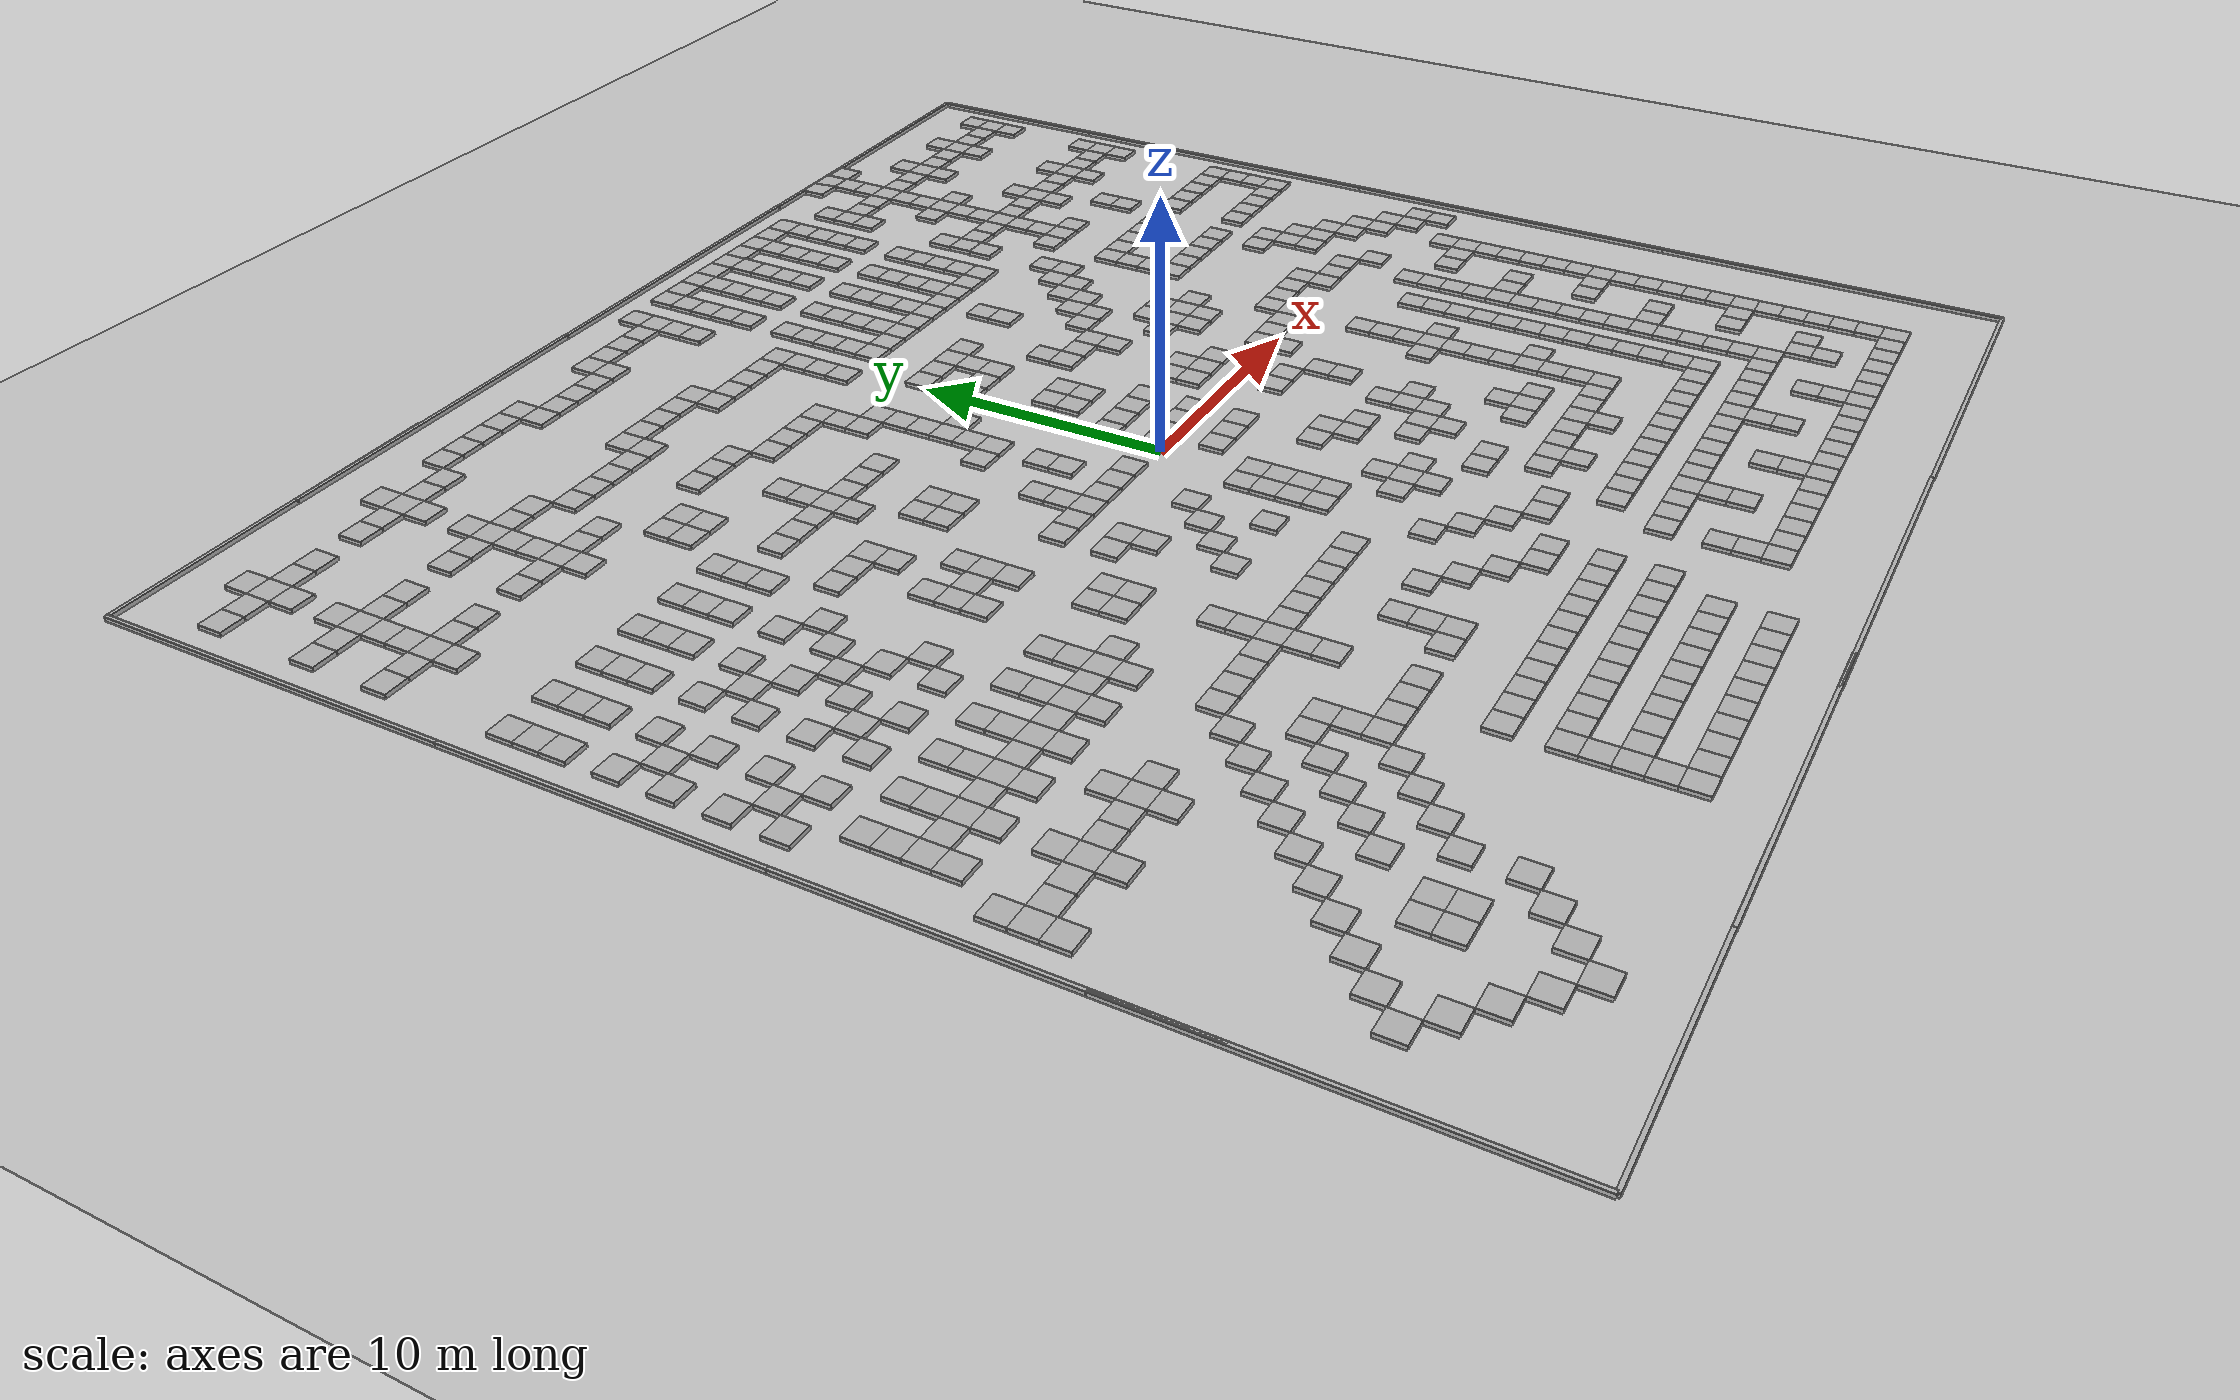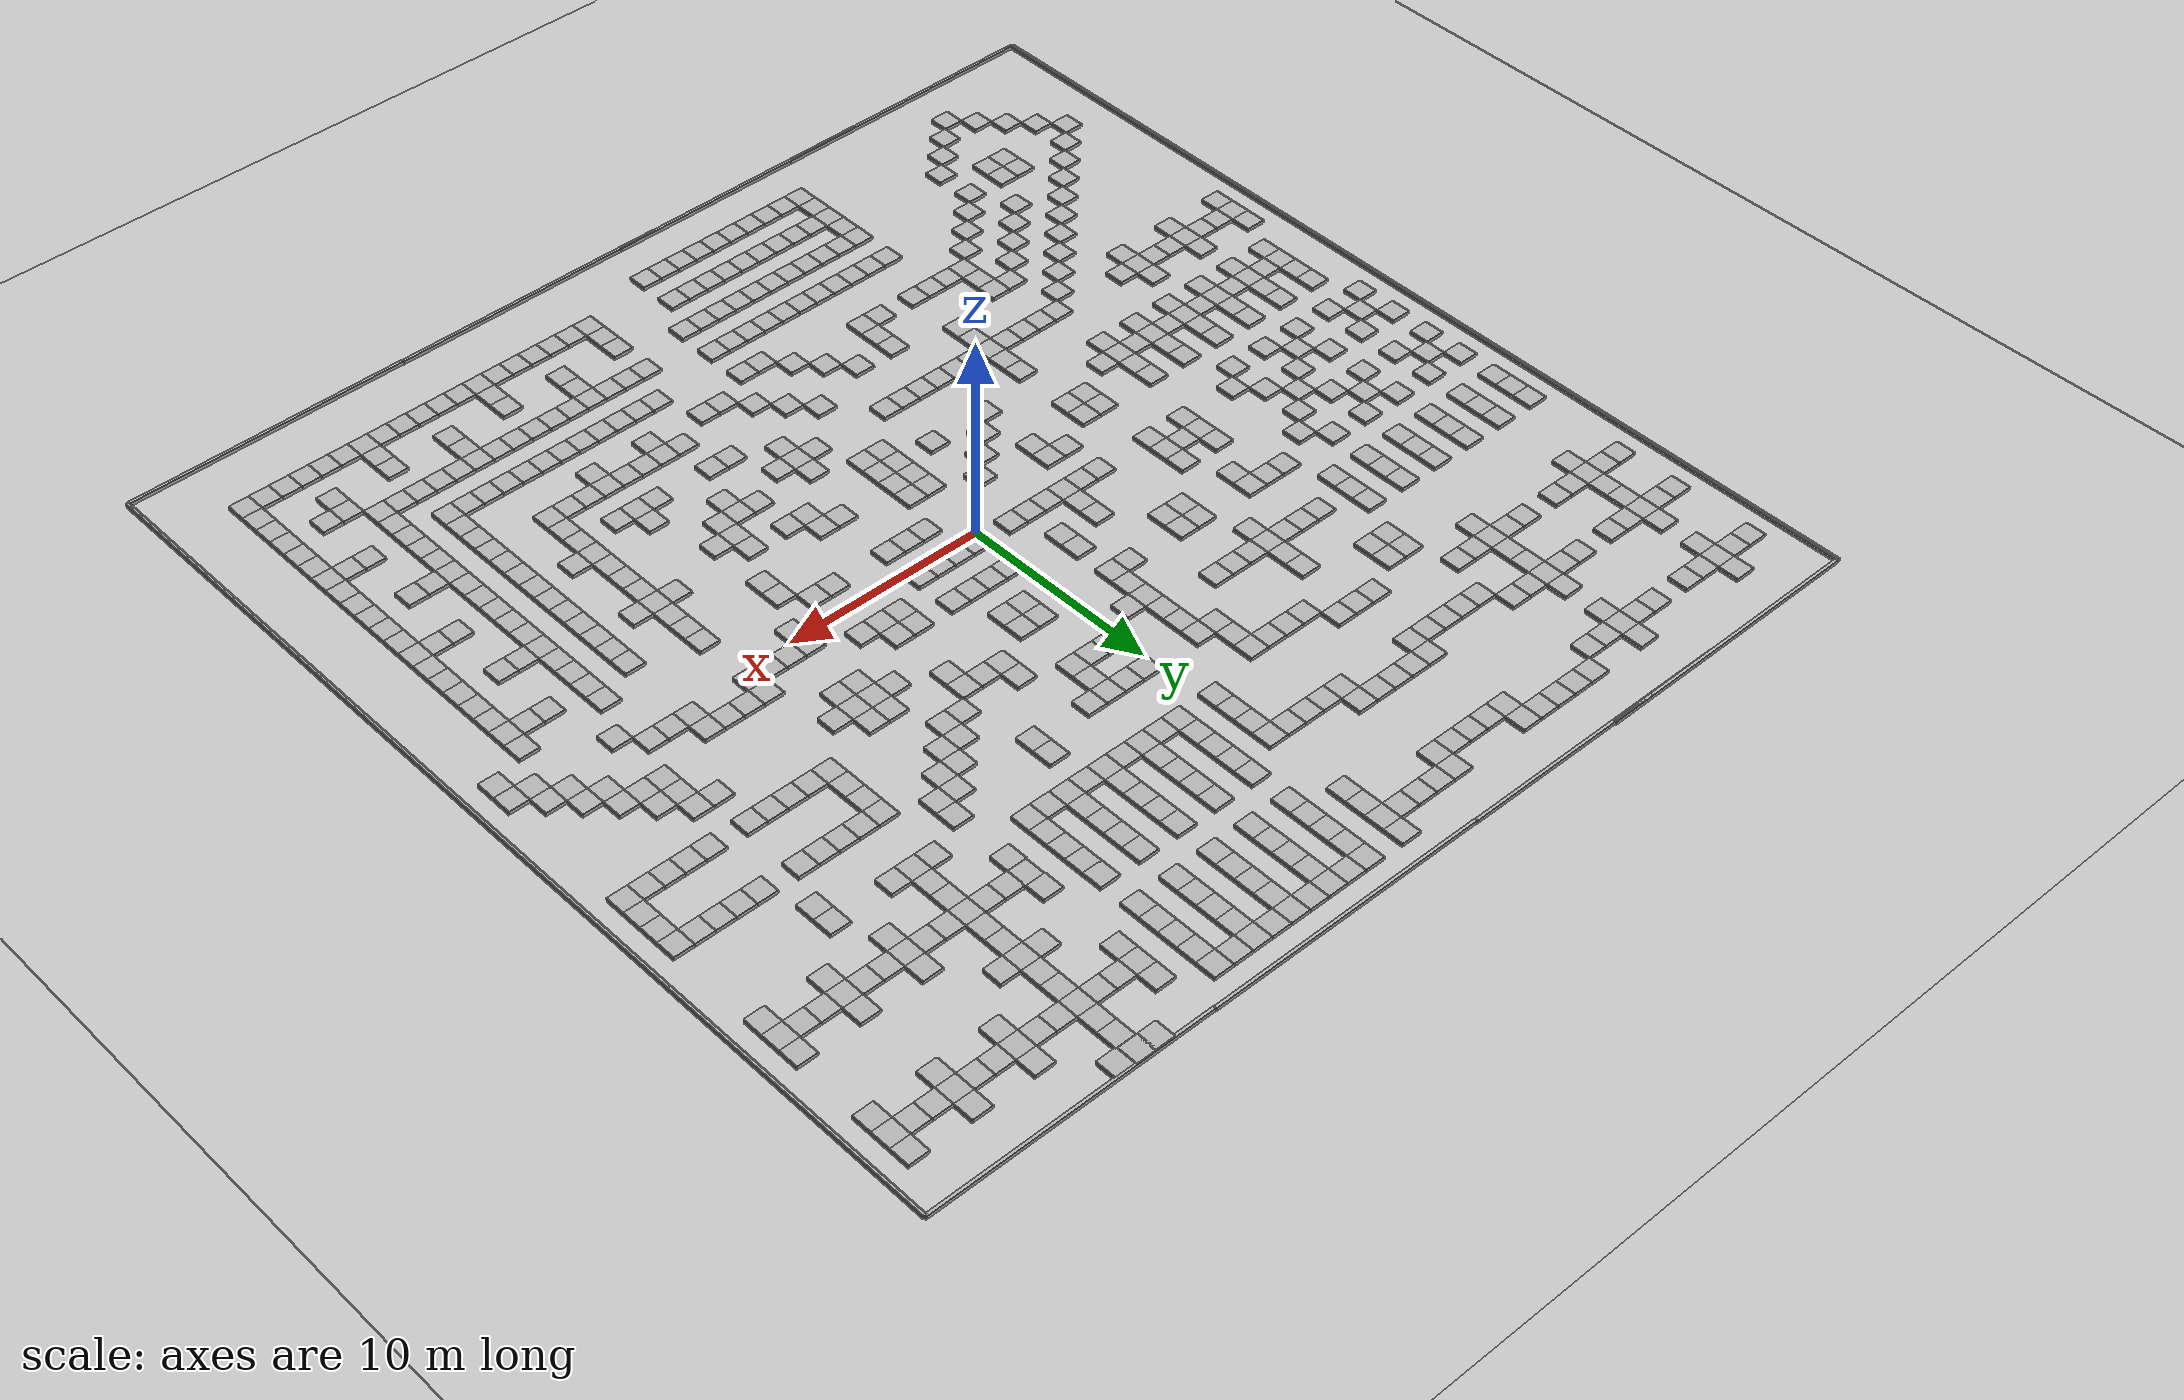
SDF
<sdf version="1.7">
 <world name="default">
  <light name="sun" type="directional">
   <pose>0 0 10 0 -0 0</pose>
   <diffuse>0.8 0.8 0.8 1</diffuse>
   <specular>0.2 0.2 0.2 1</specular>
   <attenuation>
    <range>1000</range>
    <constant>0.9</constant>
    <linear>0.01</linear>
    <quadratic>0.001</quadratic>
   </attenuation>
   <direction>-0.5 0.1 -0.9</direction>
   <spot><inner_angle>0</inner_angle><outer_angle>0</outer_angle><falloff>0</falloff></spot>
  </light>
  <model name="ground_plane">
   <static>1</static>
   <link name="link">
    <collision name="collision">
     <geometry><plane><normal>0 0 1</normal><size>100 100</size></plane></geometry>
     <surface>
      <contact><collide_bitmask>65535</collide_bitmask></contact>
      <friction><ode><mu>100</mu><mu2>50</mu2></ode></friction>
     </surface>
    </collision>
    <visual name="visual">
     <cast_shadows>0</cast_shadows>
     <geometry><plane><normal>0 0 1</normal><size>100 100</size></plane></geometry>
     <material>
      <script><uri>file://media/materials/scripts/gazebo.material</uri><name>Gazebo/Grey</name></script>
     </material>
    </visual>
   </link>
  </model>
  <gravity>0 0 -9.8</gravity>
  <magnetic_field>6e-06 2.3e-05 -4.2e-05</magnetic_field>
  <atmosphere type="adiabatic"/>
  <physics type="ode">
   <max_step_size>0.001</max_step_size>
   <real_time_factor>1</real_time_factor>
   <real_time_update_rate>1000</real_time_update_rate>
  </physics>
  <scene><ambient>0.4 0.4 0.4 1</ambient><background>0.7 0.7 0.7 1</background><shadows>1</shadows></scene>
  <spherical_coordinates>
   <surface_model>EARTH_WGS84</surface_model>
   <latitude_deg>0</latitude_deg>
   <longitude_deg>0</longitude_deg>
   <elevation>0</elevation>
   <heading_deg>0</heading_deg>
  </spherical_coordinates>
  <model name="concrete_barrier_14m_0">
   <static>1</static>
   <link name="link">
    <collision name="concrete_barrier_14m_01">
     <pose>-0 0 0.3 0 -0 0</pose>
     <geometry><box><size>14 0.15 0.6</size></box></geometry>
    </collision>
    <visual name="concrete_barrier_14m_visual">
     <geometry><mesh><uri>model://concrete_barrier_14m/meshes/concrete_barrier_14m.dae</uri></mesh></geometry>
    </visual>
   </link>
   <pose>25 -18 0 0 -0 0</pose>
  </model>
  <model name="concrete_barrier_14m_3">
   <static>1</static>
   <link name="link">
    <collision name="concrete_barrier_14m_01">
     <pose>-0 0 0.3 0 -0 0</pose>
     <geometry><box><size>14 0.15 0.6</size></box></geometry>
    </collision>
    <visual name="concrete_barrier_14m_visual">
     <geometry><mesh><uri>model://concrete_barrier_14m/meshes/concrete_barrier_14m.dae</uri></mesh></geometry>
    </visual>
   </link>
   <pose>25 10 -3.1e-05 0 -0 0</pose>
  </model>
  <model name="concrete_barrier_14m_4">
   <static>1</static>
   <link name="link">
    <collision name="concrete_barrier_14m_01">
     <pose>-0 0 0.3 0 -0 0</pose>
     <geometry><box><size>14 0.15 0.6</size></box></geometry>
    </collision>
    <visual name="concrete_barrier_14m_visual">
     <geometry><mesh><uri>model://concrete_barrier_14m/meshes/concrete_barrier_14m.dae</uri></mesh></geometry>
    </visual>
   </link>
   <pose>18 25 -3.1e-05 0 0 -1.56953</pose>
  </model>
  <model name="concrete_barrier_14m_6">
   <static>1</static>
   <link name="link">
    <collision name="concrete_barrier_14m_01">
     <pose>-0 0 0.3 0 -0 0</pose>
     <geometry><box><size>14 0.15 0.6</size></box></geometry>
    </collision>
    <visual name="concrete_barrier_14m_visual">
     <geometry><mesh><uri>model://concrete_barrier_14m/meshes/concrete_barrier_14m.dae</uri></mesh></geometry>
    </visual>
   </link>
   <pose>-8 -25 0 0 0 -1.56953</pose>
  </model>
  <model name="concrete_cube_1m">
   <static>1</static>
   <link name="link">
    <collision name="concrete_cube_1m">
     <pose>-0 0 0.3 0 -0 0</pose>
     <geometry><box><size>1 1 0.6</size></box></geometry>
    </collision>
    <visual name="concrete_cube_1m_visual">
     <geometry><mesh><uri>model://concrete_cube_1m/meshes/concrete_cube_1m.dae</uri></mesh></geometry>
    </visual>
   </link>
   <pose>-2.5 6.5 0 0 -0 0</pose>
  </model>
  <model name="concrete_cube_1m_0">
   <static>1</static>
   <link name="link">
    <collision name="concrete_cube_1m">
     <pose>-0 0 0.3 0 -0 0</pose>
     <geometry><box><size>1 1 0.6</size></box></geometry>
    </collision>
    <visual name="concrete_cube_1m_visual">
     <geometry><mesh><uri>model://concrete_cube_1m/meshes/concrete_cube_1m.dae</uri></mesh></geometry>
    </visual>
   </link>
   <pose>-6.5 4.5 0 0 -0 0</pose>
  </model>
  <model name="concrete_cube_1m_1">
   <static>1</static>
   <link name="link">
    <collision name="concrete_cube_1m">
     <pose>-0 0 0.3 0 -0 0</pose>
     <geometry><box><size>1 1 0.6</size></box></geometry>
    </collision>
    <visual name="concrete_cube_1m_visual">
     <geometry><mesh><uri>model://concrete_cube_1m/meshes/concrete_cube_1m.dae</uri></mesh></geometry>
    </visual>
   </link>
   <pose>-2.5 5.5 0 0 -0 0</pose>
  </model>
  <model name="concrete_cube_1m_2">
   <static>1</static>
   <link name="link">
    <collision name="concrete_cube_1m">
     <pose>-0 0 0.3 0 -0 0</pose>
     <geometry><box><size>1 1 0.6</size></box></geometry>
    </collision>
    <visual name="concrete_cube_1m_visual">
     <geometry><mesh><uri>model://concrete_cube_1m/meshes/concrete_cube_1m.dae</uri></mesh></geometry>
    </visual>
   </link>
   <pose>-1.5 0.5 0 0 -0 0</pose>
  </model>
  <model name="concrete_cube_1m_3">
   <static>1</static>
   <link name="link">
    <collision name="concrete_cube_1m">
     <pose>-0 0 0.3 0 -0 0</pose>
     <geometry><box><size>1 1 0.6</size></box></geometry>
    </collision>
    <visual name="concrete_cube_1m_visual">
     <geometry><mesh><uri>model://concrete_cube_1m/meshes/concrete_cube_1m.dae</uri></mesh></geometry>
    </visual>
   </link>
   <pose>-4.5 0.5 0 0 -0 0</pose>
  </model>
  <model name="concrete_cube_1m_4">
   <static>1</static>
   <link name="link">
    <collision name="concrete_cube_1m">
     <pose>-0 0 0.3 0 -0 0</pose>
     <geometry><box><size>1 1 0.6</size></box></geometry>
    </collision>
    <visual name="concrete_cube_1m_visual">
     <geometry><mesh><uri>model://concrete_cube_1m/meshes/concrete_cube_1m.dae</uri></mesh></geometry>
    </visual>
   </link>
   <pose>6.5 2.5 0 0 -0 0</pose>
  </model>
  <model name="concrete_cube_1m_5">
   <static>1</static>
   <link name="link">
    <collision name="concrete_cube_1m">
     <pose>-0 0 0.3 0 -0 0</pose>
     <geometry><box><size>1 1 0.6</size></box></geometry>
    </collision>
    <visual name="concrete_cube_1m_visual">
     <geometry><mesh><uri>model://concrete_cube_1m/meshes/concrete_cube_1m.dae</uri></mesh></geometry>
    </visual>
   </link>
   <pose>5.5 2.5 0 0 -0 0</pose>
  </model>
  <model name="concrete_cube_1m_6">
   <static>1</static>
   <link name="link">
    <collision name="concrete_cube_1m">
     <pose>-0 0 0.3 0 -0 0</pose>
     <geometry><box><size>1 1 0.6</size></box></geometry>
    </collision>
    <visual name="concrete_cube_1m_visual">
     <geometry><mesh><uri>model://concrete_cube_1m/meshes/concrete_cube_1m.dae</uri></mesh></geometry>
    </visual>
   </link>
   <pose>6.5 1.5 0 0 -0 0</pose>
  </model>
  <model name="concrete_cube_1m_7">
   <static>1</static>
   <link name="link">
    <collision name="concrete_cube_1m">
     <pose>-0 0 0.3 0 -0 0</pose>
     <geometry><box><size>1 1 0.6</size></box></geometry>
    </collision>
    <visual name="concrete_cube_1m_visual">
     <geometry><mesh><uri>model://concrete_cube_1m/meshes/concrete_cube_1m.dae</uri></mesh></geometry>
    </visual>
   </link>
   <pose>5.5 1.5 0 0 -0 0</pose>
  </model>
  <model name="concrete_cube_1m_8">
   <static>1</static>
   <link name="link">
    <collision name="concrete_cube_1m">
     <pose>-0 0 0.3 0 -0 0</pose>
     <geometry><box><size>1 1 0.6</size></box></geometry>
    </collision>
    <visual name="concrete_cube_1m_visual">
     <geometry><mesh><uri>model://concrete_cube_1m/meshes/concrete_cube_1m.dae</uri></mesh></geometry>
    </visual>
   </link>
   <pose>-0.5 -4.5 0 0 -0 0</pose>
  </model>
  <model name="concrete_cube_1m_9">
   <static>1</static>
   <link name="link">
    <collision name="concrete_cube_1m">
     <pose>-0 0 0.3 0 -0 0</pose>
     <geometry><box><size>1 1 0.6</size></box></geometry>
    </collision>
    <visual name="concrete_cube_1m_visual">
     <geometry><mesh><uri>model://concrete_cube_1m/meshes/concrete_cube_1m.dae</uri></mesh></geometry>
    </visual>
   </link>
   <pose>0.5 -4.5 0 0 -0 0</pose>
  </model>
  <model name="concrete_cube_1m_10">
   <static>1</static>
   <link name="link">
    <collision name="concrete_cube_1m">
     <pose>-0 0 0.3 0 -0 0</pose>
     <geometry><box><size>1 1 0.6</size></box></geometry>
    </collision>
    <visual name="concrete_cube_1m_visual">
     <geometry><mesh><uri>model://concrete_cube_1m/meshes/concrete_cube_1m.dae</uri></mesh></geometry>
    </visual>
   </link>
   <pose>4.5 -5.5 0 0 -0 0</pose>
  </model>
  <model name="concrete_cube_1m_11">
   <static>1</static>
   <link name="link">
    <collision name="concrete_cube_1m">
     <pose>-0 0 0.3 0 -0 0</pose>
     <geometry><box><size>1 1 0.6</size></box></geometry>
    </collision>
    <visual name="concrete_cube_1m_visual">
     <geometry><mesh><uri>model://concrete_cube_1m/meshes/concrete_cube_1m.dae</uri></mesh></geometry>
    </visual>
   </link>
   <pose>5.5 -5.5 0 0 -0 0</pose>
  </model>
  <model name="concrete_cube_1m_12">
   <static>1</static>
   <link name="link">
    <collision name="concrete_cube_1m">
     <pose>-0 0 0.3 0 -0 0</pose>
     <geometry><box><size>1 1 0.6</size></box></geometry>
    </collision>
    <visual name="concrete_cube_1m_visual">
     <geometry><mesh><uri>model://concrete_cube_1m/meshes/concrete_cube_1m.dae</uri></mesh></geometry>
    </visual>
   </link>
   <pose>-8.5 -8.5 0 0 -0 0</pose>
  </model>
  <model name="concrete_cube_1m_13">
   <static>1</static>
   <link name="link">
    <collision name="concrete_cube_1m">
     <pose>-0 0 0.3 0 -0 0</pose>
     <geometry><box><size>1 1 0.6</size></box></geometry>
    </collision>
    <visual name="concrete_cube_1m_visual">
     <geometry><mesh><uri>model://concrete_cube_1m/meshes/concrete_cube_1m.dae</uri></mesh></geometry>
    </visual>
   </link>
   <pose>-7.5 -8.5 0 0 -0 0</pose>
  </model>
  <model name="concrete_cube_1m_14">
   <static>1</static>
   <link name="link">
    <collision name="concrete_cube_1m">
     <pose>-0 0 0.3 0 -0 0</pose>
     <geometry><box><size>1 1 0.6</size></box></geometry>
    </collision>
    <visual name="concrete_cube_1m_visual">
     <geometry><mesh><uri>model://concrete_cube_1m/meshes/concrete_cube_1m.dae</uri></mesh></geometry>
    </visual>
   </link>
   <pose>-6.5 -8.5 0 0 -0 0</pose>
  </model>
  <model name="concrete_cube_1m_15">
   <static>1</static>
   <link name="link">
    <collision name="concrete_cube_1m">
     <pose>-0 0 0.3 0 -0 0</pose>
     <geometry><box><size>1 1 0.6</size></box></geometry>
    </collision>
    <visual name="concrete_cube_1m_visual">
     <geometry><mesh><uri>model://concrete_cube_1m/meshes/concrete_cube_1m.dae</uri></mesh></geometry>
    </visual>
   </link>
   <pose>-8.5 -7.5 0 0 -0 0</pose>
  </model>
  <model name="concrete_cube_1m_16">
   <static>1</static>
   <link name="link">
    <collision name="concrete_cube_1m">
     <pose>-0 0 0.3 0 -0 0</pose>
     <geometry><box><size>1 1 0.6</size></box></geometry>
    </collision>
    <visual name="concrete_cube_1m_visual">
     <geometry><mesh><uri>model://concrete_cube_1m/meshes/concrete_cube_1m.dae</uri></mesh></geometry>
    </visual>
   </link>
   <pose>-8.5 -6.5 0 0 -0 0</pose>
  </model>
  <model name="concrete_cube_1m_17">
   <static>1</static>
   <link name="link">
    <collision name="concrete_cube_1m">
     <pose>-0 0 0.3 0 -0 0</pose>
     <geometry><box><size>1 1 0.6</size></box></geometry>
    </collision>
    <visual name="concrete_cube_1m_visual">
     <geometry><mesh><uri>model://concrete_cube_1m/meshes/concrete_cube_1m.dae</uri></mesh></geometry>
    </visual>
   </link>
   <pose>2.5 5.5 0 0 -0 0</pose>
  </model>
  <model name="concrete_cube_1m_18">
   <static>1</static>
   <link name="link">
    <collision name="concrete_cube_1m">
     <pose>-0 0 0.3 0 -0 0</pose>
     <geometry><box><size>1 1 0.6</size></box></geometry>
    </collision>
    <visual name="concrete_cube_1m_visual">
     <geometry><mesh><uri>model://concrete_cube_1m/meshes/concrete_cube_1m.dae</uri></mesh></geometry>
    </visual>
   </link>
   <pose>8.5 8.5 0 0 -0 0</pose>
  </model>
  <model name="concrete_cube_1m_19">
   <static>1</static>
   <link name="link">
    <collision name="concrete_cube_1m">
     <pose>-0 0 0.3 0 -0 0</pose>
     <geometry><box><size>1 1 0.6</size></box></geometry>
    </collision>
    <visual name="concrete_cube_1m_visual">
     <geometry><mesh><uri>model://concrete_cube_1m/meshes/concrete_cube_1m.dae</uri></mesh></geometry>
    </visual>
   </link>
   <pose>7.5 7.5 0 0 -0 0</pose>
  </model>
  <model name="concrete_cube_1m_20">
   <static>1</static>
   <link name="link">
    <collision name="concrete_cube_1m">
     <pose>-0 0 0.3 0 -0 0</pose>
     <geometry><box><size>1 1 0.6</size></box></geometry>
    </collision>
    <visual name="concrete_cube_1m_visual">
     <geometry><mesh><uri>model://concrete_cube_1m/meshes/concrete_cube_1m.dae</uri></mesh></geometry>
    </visual>
   </link>
   <pose>6.5 6.5 0 0 -0 0</pose>
  </model>
  <model name="concrete_cube_1m_21">
   <static>1</static>
   <link name="link">
    <collision name="concrete_cube_1m">
     <pose>-0 0 0.3 0 -0 0</pose>
     <geometry><box><size>1 1 0.6</size></box></geometry>
    </collision>
    <visual name="concrete_cube_1m_visual">
     <geometry><mesh><uri>model://concrete_cube_1m/meshes/concrete_cube_1m.dae</uri></mesh></geometry>
    </visual>
   </link>
   <pose>6.5 5.5 0 0 -0 0</pose>
  </model>
  <model name="concrete_cube_1m_22">
   <static>1</static>
   <link name="link">
    <collision name="concrete_cube_1m">
     <pose>-0 0 0.3 0 -0 0</pose>
     <geometry><box><size>1 1 0.6</size></box></geometry>
    </collision>
    <visual name="concrete_cube_1m_visual">
     <geometry><mesh><uri>model://concrete_cube_1m/meshes/concrete_cube_1m.dae</uri></mesh></geometry>
    </visual>
   </link>
   <pose>5.5 6.5 0 0 -0 0</pose>
  </model>
  <model name="concrete_cube_1m_23">
   <static>1</static>
   <link name="link">
    <collision name="concrete_cube_1m">
     <pose>-0 0 0.3 0 -0 0</pose>
     <geometry><box><size>1 1 0.6</size></box></geometry>
    </collision>
    <visual name="concrete_cube_1m_visual">
     <geometry><mesh><uri>model://concrete_cube_1m/meshes/concrete_cube_1m.dae</uri></mesh></geometry>
    </visual>
   </link>
   <pose>4.5 6.5 0 0 -0 0</pose>
  </model>
  <model name="concrete_cube_1m_24">
   <static>1</static>
   <link name="link">
    <collision name="concrete_cube_1m">
     <pose>-0 0 0.3 0 -0 0</pose>
     <geometry><box><size>1 1 0.6</size></box></geometry>
    </collision>
    <visual name="concrete_cube_1m_visual">
     <geometry><mesh><uri>model://concrete_cube_1m/meshes/concrete_cube_1m.dae</uri></mesh></geometry>
    </visual>
   </link>
   <pose>4.5 7.5 0 0 -0 0</pose>
  </model>
  <model name="concrete_cube_1m_25">
   <static>1</static>
   <link name="link">
    <collision name="concrete_cube_1m">
     <pose>-0 0 0.3 0 -0 0</pose>
     <geometry><box><size>1 1 0.6</size></box></geometry>
    </collision>
    <visual name="concrete_cube_1m_visual">
     <geometry><mesh><uri>model://concrete_cube_1m/meshes/concrete_cube_1m.dae</uri></mesh></geometry>
    </visual>
   </link>
   <pose>3.5 2.5 0 0 -0 0</pose>
  </model>
  <model name="concrete_cube_1m_26">
   <static>1</static>
   <link name="link">
    <collision name="concrete_cube_1m">
     <pose>-0 0 0.3 0 -0 0</pose>
     <geometry><box><size>1 1 0.6</size></box></geometry>
    </collision>
    <visual name="concrete_cube_1m_visual">
     <geometry><mesh><uri>model://concrete_cube_1m/meshes/concrete_cube_1m.dae</uri></mesh></geometry>
    </visual>
   </link>
   <pose>2.5 2.5 0 0 -0 0</pose>
  </model>
  <model name="concrete_cube_1m_27">
   <static>1</static>
   <link name="link">
    <collision name="concrete_cube_1m">
     <pose>-0 0 0.3 0 -0 0</pose>
     <geometry><box><size>1 1 0.6</size></box></geometry>
    </collision>
    <visual name="concrete_cube_1m_visual">
     <geometry><mesh><uri>model://concrete_cube_1m/meshes/concrete_cube_1m.dae</uri></mesh></geometry>
    </visual>
   </link>
   <pose>1.5 2.5 0 0 -0 0</pose>
  </model>
  <model name="concrete_cube_1m_28">
   <static>1</static>
   <link name="link">
    <collision name="concrete_cube_1m">
     <pose>-0 0 0.3 0 -0 0</pose>
     <geometry><box><size>1 1 0.6</size></box></geometry>
    </collision>
    <visual name="concrete_cube_1m_visual">
     <geometry><mesh><uri>model://concrete_cube_1m/meshes/concrete_cube_1m.dae</uri></mesh></geometry>
    </visual>
   </link>
   <pose>0.5 2.5 0 0 -0 0</pose>
  </model>
  <model name="concrete_cube_1m_29">
   <static>1</static>
   <link name="link">
    <collision name="concrete_cube_1m">
     <pose>-0 0 0.3 0 -0 0</pose>
     <geometry><box><size>1 1 0.6</size></box></geometry>
    </collision>
    <visual name="concrete_cube_1m_visual">
     <geometry><mesh><uri>model://concrete_cube_1m/meshes/concrete_cube_1m.dae</uri></mesh></geometry>
    </visual>
   </link>
   <pose>1.5 4.5 0 0 -0 0</pose>
  </model>
  <model name="concrete_cube_1m_30">
   <static>1</static>
   <link name="link">
    <collision name="concrete_cube_1m">
     <pose>-0 0 0.3 0 -0 0</pose>
     <geometry><box><size>1 1 0.6</size></box></geometry>
    </collision>
    <visual name="concrete_cube_1m_visual">
     <geometry><mesh><uri>model://concrete_cube_1m/meshes/concrete_cube_1m.dae</uri></mesh></geometry>
    </visual>
   </link>
   <pose>8.5 4.5 0 0 -0 0</pose>
  </model>
  <model name="concrete_cube_1m_31">
   <static>1</static>
   <link name="link">
    <collision name="concrete_cube_1m">
     <pose>-0 0 0.3 0 -0 0</pose>
     <geometry><box><size>1 1 0.6</size></box></geometry>
    </collision>
    <visual name="concrete_cube_1m_visual">
     <geometry><mesh><uri>model://concrete_cube_1m/meshes/concrete_cube_1m.dae</uri></mesh></geometry>
    </visual>
   </link>
   <pose>9.5 4.5 0 0 -0 0</pose>
  </model>
  <model name="concrete_cube_1m_32">
   <static>1</static>
   <link name="link">
    <collision name="concrete_cube_1m">
     <pose>-0 0 0.3 0 -0 0</pose>
     <geometry><box><size>1 1 0.6</size></box></geometry>
    </collision>
    <visual name="concrete_cube_1m_visual">
     <geometry><mesh><uri>model://concrete_cube_1m/meshes/concrete_cube_1m.dae</uri></mesh></geometry>
    </visual>
   </link>
   <pose>9.5 3.5 0 0 -0 0</pose>
  </model>
  <model name="concrete_cube_1m_33">
   <static>1</static>
   <link name="link">
    <collision name="concrete_cube_1m">
     <pose>-0 0 0.3 0 -0 0</pose>
     <geometry><box><size>1 1 0.6</size></box></geometry>
    </collision>
    <visual name="concrete_cube_1m_visual">
     <geometry><mesh><uri>model://concrete_cube_1m/meshes/concrete_cube_1m.dae</uri></mesh></geometry>
    </visual>
   </link>
   <pose>9.5 5.5 0 0 -0 0</pose>
  </model>
  <model name="concrete_cube_1m_34">
   <static>1</static>
   <link name="link">
    <collision name="concrete_cube_1m">
     <pose>-0 0 0.3 0 -0 0</pose>
     <geometry><box><size>1 1 0.6</size></box></geometry>
    </collision>
    <visual name="concrete_cube_1m_visual">
     <geometry><mesh><uri>model://concrete_cube_1m/meshes/concrete_cube_1m.dae</uri></mesh></geometry>
    </visual>
   </link>
   <pose>7.5 1.5 0 0 -0 0</pose>
  </model>
  <model name="concrete_cube_1m_35">
   <static>1</static>
   <link name="link">
    <collision name="concrete_cube_1m">
     <pose>-0 0 0.3 0 -0 0</pose>
     <geometry><box><size>1 1 0.6</size></box></geometry>
    </collision>
    <visual name="concrete_cube_1m_visual">
     <geometry><mesh><uri>model://concrete_cube_1m/meshes/concrete_cube_1m.dae</uri></mesh></geometry>
    </visual>
   </link>
   <pose>9.5 0.5 0 0 -0 0</pose>
  </model>
  <model name="concrete_cube_1m_36">
   <static>1</static>
   <link name="link">
    <collision name="concrete_cube_1m">
     <pose>-0 0 0.3 0 -0 0</pose>
     <geometry><box><size>1 1 0.6</size></box></geometry>
    </collision>
    <visual name="concrete_cube_1m_visual">
     <geometry><mesh><uri>model://concrete_cube_1m/meshes/concrete_cube_1m.dae</uri></mesh></geometry>
    </visual>
   </link>
   <pose>2.5 8.5 0 0 -0 0</pose>
  </model>
  <model name="concrete_cube_1m_37">
   <static>1</static>
   <link name="link">
    <collision name="concrete_cube_1m">
     <pose>-0 0 0.3 0 -0 0</pose>
     <geometry><box><size>1 1 0.6</size></box></geometry>
    </collision>
    <visual name="concrete_cube_1m_visual">
     <geometry><mesh><uri>model://concrete_cube_1m/meshes/concrete_cube_1m.dae</uri></mesh></geometry>
    </visual>
   </link>
   <pose>1.5 8.5 0 0 -0 0</pose>
  </model>
  <model name="concrete_cube_1m_38">
   <static>1</static>
   <link name="link">
    <collision name="concrete_cube_1m">
     <pose>-0 0 0.3 0 -0 0</pose>
     <geometry><box><size>1 1 0.6</size></box></geometry>
    </collision>
    <visual name="concrete_cube_1m_visual">
     <geometry><mesh><uri>model://concrete_cube_1m/meshes/concrete_cube_1m.dae</uri></mesh></geometry>
    </visual>
   </link>
   <pose>0.5 8.5 0 0 -0 0</pose>
  </model>
  <model name="concrete_cube_1m_39">
   <static>1</static>
   <link name="link">
    <collision name="concrete_cube_1m">
     <pose>-0 0 0.3 0 -0 0</pose>
     <geometry><box><size>1 1 0.6</size></box></geometry>
    </collision>
    <visual name="concrete_cube_1m_visual">
     <geometry><mesh><uri>model://concrete_cube_1m/meshes/concrete_cube_1m.dae</uri></mesh></geometry>
    </visual>
   </link>
   <pose>2.5 4.5 0 0 -0 0</pose>
  </model>
  <model name="concrete_cube_1m_40">
   <static>1</static>
   <link name="link">
    <collision name="concrete_cube_1m">
     <pose>-0 0 0.3 0 -0 0</pose>
     <geometry><box><size>1 1 0.6</size></box></geometry>
    </collision>
    <visual name="concrete_cube_1m_visual">
     <geometry><mesh><uri>model://concrete_cube_1m/meshes/concrete_cube_1m.dae</uri></mesh></geometry>
    </visual>
   </link>
   <pose>1.5 5.5 0 0 -0 0</pose>
  </model>
  <model name="concrete_cube_1m_41">
   <static>1</static>
   <link name="link">
    <collision name="concrete_cube_1m">
     <pose>-0 0 0.3 0 -0 0</pose>
     <geometry><box><size>1 1 0.6</size></box></geometry>
    </collision>
    <visual name="concrete_cube_1m_visual">
     <geometry><mesh><uri>model://concrete_cube_1m/meshes/concrete_cube_1m.dae</uri></mesh></geometry>
    </visual>
   </link>
   <pose>3.5 0.5 0 0 -0 0</pose>
  </model>
  <model name="concrete_cube_1m_42">
   <static>1</static>
   <link name="link">
    <collision name="concrete_cube_1m">
     <pose>-0 0 0.3 0 -0 0</pose>
     <geometry><box><size>1 1 0.6</size></box></geometry>
    </collision>
    <visual name="concrete_cube_1m_visual">
     <geometry><mesh><uri>model://concrete_cube_1m/meshes/concrete_cube_1m.dae</uri></mesh></geometry>
    </visual>
   </link>
   <pose>2.5 0.5 0 0 -0 0</pose>
  </model>
  <model name="concrete_cube_1m_43">
   <static>1</static>
   <link name="link">
    <collision name="concrete_cube_1m">
     <pose>-0 0 0.3 0 -0 0</pose>
     <geometry><box><size>1 1 0.6</size></box></geometry>
    </collision>
    <visual name="concrete_cube_1m_visual">
     <geometry><mesh><uri>model://concrete_cube_1m/meshes/concrete_cube_1m.dae</uri></mesh></geometry>
    </visual>
   </link>
   <pose>-3.5 5.5 0 0 -0 0</pose>
  </model>
  <model name="concrete_cube_1m_44">
   <static>1</static>
   <link name="link">
    <collision name="concrete_cube_1m">
     <pose>-0 0 0.3 0 -0 0</pose>
     <geometry><box><size>1 1 0.6</size></box></geometry>
    </collision>
    <visual name="concrete_cube_1m_visual">
     <geometry><mesh><uri>model://concrete_cube_1m/meshes/concrete_cube_1m.dae</uri></mesh></geometry>
    </visual>
   </link>
   <pose>-2.5 7.5 0 0 -0 0</pose>
  </model>
  <model name="concrete_cube_1m_45">
   <static>1</static>
   <link name="link">
    <collision name="concrete_cube_1m">
     <pose>-0 0 0.3 0 -0 0</pose>
     <geometry><box><size>1 1 0.6</size></box></geometry>
    </collision>
    <visual name="concrete_cube_1m_visual">
     <geometry><mesh><uri>model://concrete_cube_1m/meshes/concrete_cube_1m.dae</uri></mesh></geometry>
    </visual>
   </link>
   <pose>-2.5 0.5 0 0 -0 0</pose>
  </model>
  <model name="concrete_cube_1m_46">
   <static>1</static>
   <link name="link">
    <collision name="concrete_cube_1m">
     <pose>-0 0 0.3 0 -0 0</pose>
     <geometry><box><size>1 1 0.6</size></box></geometry>
    </collision>
    <visual name="concrete_cube_1m_visual">
     <geometry><mesh><uri>model://concrete_cube_1m/meshes/concrete_cube_1m.dae</uri></mesh></geometry>
    </visual>
   </link>
   <pose>-3.5 0.5 0 0 -0 0</pose>
  </model>
  <model name="concrete_cube_1m_47">
   <static>1</static>
   <link name="link">
    <collision name="concrete_cube_1m">
     <pose>-0 0 0.3 0 -0 0</pose>
     <geometry><box><size>1 1 0.6</size></box></geometry>
    </collision>
    <visual name="concrete_cube_1m_visual">
     <geometry><mesh><uri>model://concrete_cube_1m/meshes/concrete_cube_1m.dae</uri></mesh></geometry>
    </visual>
   </link>
   <pose>-4.5 1.5 0 0 -0 0</pose>
  </model>
  <model name="concrete_cube_1m_48">
   <static>1</static>
   <link name="link">
    <collision name="concrete_cube_1m">
     <pose>-0 0 0.3 0 -0 0</pose>
     <geometry><box><size>1 1 0.6</size></box></geometry>
    </collision>
    <visual name="concrete_cube_1m_visual">
     <geometry><mesh><uri>model://concrete_cube_1m/meshes/concrete_cube_1m.dae</uri></mesh></geometry>
    </visual>
   </link>
   <pose>-4.5 2.5 0 0 -0 0</pose>
  </model>
  <model name="concrete_cube_1m_49">
   <static>1</static>
   <link name="link">
    <collision name="concrete_cube_1m">
     <pose>-0 0 0.3 0 -0 0</pose>
     <geometry><box><size>1 1 0.6</size></box></geometry>
    </collision>
    <visual name="concrete_cube_1m_visual">
     <geometry><mesh><uri>model://concrete_cube_1m/meshes/concrete_cube_1m.dae</uri></mesh></geometry>
    </visual>
   </link>
   <pose>-5.5 0.5 0 0 -0 0</pose>
  </model>
  <model name="concrete_cube_1m_50">
   <static>1</static>
   <link name="link">
    <collision name="concrete_cube_1m">
     <pose>-0 0 0.3 0 -0 0</pose>
     <geometry><box><size>1 1 0.6</size></box></geometry>
    </collision>
    <visual name="concrete_cube_1m_visual">
     <geometry><mesh><uri>model://concrete_cube_1m/meshes/concrete_cube_1m.dae</uri></mesh></geometry>
    </visual>
   </link>
   <pose>-6.5 0.5 0 0 -0 0</pose>
  </model>
  <model name="concrete_cube_1m_51">
   <static>1</static>
   <link name="link">
    <collision name="concrete_cube_1m">
     <pose>-0 0 0.3 0 -0 0</pose>
     <geometry><box><size>1 1 0.6</size></box></geometry>
    </collision>
    <visual name="concrete_cube_1m_visual">
     <geometry><mesh><uri>model://concrete_cube_1m/meshes/concrete_cube_1m.dae</uri></mesh></geometry>
    </visual>
   </link>
   <pose>-6.5 5.5 0 0 -0 0</pose>
  </model>
  <model name="concrete_cube_1m_52">
   <static>1</static>
   <link name="link">
    <collision name="concrete_cube_1m">
     <pose>-0 0 0.3 0 -0 0</pose>
     <geometry><box><size>1 1 0.6</size></box></geometry>
    </collision>
    <visual name="concrete_cube_1m_visual">
     <geometry><mesh><uri>model://concrete_cube_1m/meshes/concrete_cube_1m.dae</uri></mesh></geometry>
    </visual>
   </link>
   <pose>-7.5 4.5 0 0 -0 0</pose>
  </model>
  <model name="concrete_cube_1m_53">
   <static>1</static>
   <link name="link">
    <collision name="concrete_cube_1m">
     <pose>-0 0 0.3 0 -0 0</pose>
     <geometry><box><size>1 1 0.6</size></box></geometry>
    </collision>
    <visual name="concrete_cube_1m_visual">
     <geometry><mesh><uri>model://concrete_cube_1m/meshes/concrete_cube_1m.dae</uri></mesh></geometry>
    </visual>
   </link>
   <pose>-7.5 5.5 0 0 -0 0</pose>
  </model>
  <model name="concrete_cube_1m_54">
   <static>1</static>
   <link name="link">
    <collision name="concrete_cube_1m">
     <pose>-0 0 0.3 0 -0 0</pose>
     <geometry><box><size>1 1 0.6</size></box></geometry>
    </collision>
    <visual name="concrete_cube_1m_visual">
     <geometry><mesh><uri>model://concrete_cube_1m/meshes/concrete_cube_1m.dae</uri></mesh></geometry>
    </visual>
   </link>
   <pose>-8.5 8.5 0 0 -0 0</pose>
  </model>
  <model name="concrete_cube_1m_55">
   <static>1</static>
   <link name="link">
    <collision name="concrete_cube_1m">
     <pose>-0 0 0.3 0 -0 0</pose>
     <geometry><box><size>1 1 0.6</size></box></geometry>
    </collision>
    <visual name="concrete_cube_1m_visual">
     <geometry><mesh><uri>model://concrete_cube_1m/meshes/concrete_cube_1m.dae</uri></mesh></geometry>
    </visual>
   </link>
   <pose>-8.5 7.5 0 0 -0 0</pose>
  </model>
  <model name="concrete_cube_1m_56">
   <static>1</static>
   <link name="link">
    <collision name="concrete_cube_1m">
     <pose>-0 0 0.3 0 -0 0</pose>
     <geometry><box><size>1 1 0.6</size></box></geometry>
    </collision>
    <visual name="concrete_cube_1m_visual">
     <geometry><mesh><uri>model://concrete_cube_1m/meshes/concrete_cube_1m.dae</uri></mesh></geometry>
    </visual>
   </link>
   <pose>-7.5 8.5 0 0 -0 0</pose>
  </model>
  <model name="concrete_cube_1m_57">
   <static>1</static>
   <link name="link">
    <collision name="concrete_cube_1m">
     <pose>-0 0 0.3 0 -0 0</pose>
     <geometry><box><size>1 1 0.6</size></box></geometry>
    </collision>
    <visual name="concrete_cube_1m_visual">
     <geometry><mesh><uri>model://concrete_cube_1m/meshes/concrete_cube_1m.dae</uri></mesh></geometry>
    </visual>
   </link>
   <pose>-6.5 8.5 0 0 -0 0</pose>
  </model>
  <model name="concrete_cube_1m_58">
   <static>1</static>
   <link name="link">
    <collision name="concrete_cube_1m">
     <pose>-0 0 0.3 0 -0 0</pose>
     <geometry><box><size>1 1 0.6</size></box></geometry>
    </collision>
    <visual name="concrete_cube_1m_visual">
     <geometry><mesh><uri>model://concrete_cube_1m/meshes/concrete_cube_1m.dae</uri></mesh></geometry>
    </visual>
   </link>
   <pose>-5.5 8.5 0 0 -0 0</pose>
  </model>
  <model name="concrete_cube_1m_59">
   <static>1</static>
   <link name="link">
    <collision name="concrete_cube_1m">
     <pose>-0 0 0.3 0 -0 0</pose>
     <geometry><box><size>1 1 0.6</size></box></geometry>
    </collision>
    <visual name="concrete_cube_1m_visual">
     <geometry><mesh><uri>model://concrete_cube_1m/meshes/concrete_cube_1m.dae</uri></mesh></geometry>
    </visual>
   </link>
   <pose>-1.5 7.5 0 0 -0 0</pose>
  </model>
  <model name="concrete_cube_1m_60">
   <static>1</static>
   <link name="link">
    <collision name="concrete_cube_1m">
     <pose>-0 0 0.3 0 -0 0</pose>
     <geometry><box><size>1 1 0.6</size></box></geometry>
    </collision>
    <visual name="concrete_cube_1m_visual">
     <geometry><mesh><uri>model://concrete_cube_1m/meshes/concrete_cube_1m.dae</uri></mesh></geometry>
    </visual>
   </link>
   <pose>-9.5 1.5 0 0 -0 0</pose>
  </model>
  <model name="concrete_cube_1m_61">
   <static>1</static>
   <link name="link">
    <collision name="concrete_cube_1m">
     <pose>-0 0 0.3 0 -0 0</pose>
     <geometry><box><size>1 1 0.6</size></box></geometry>
    </collision>
    <visual name="concrete_cube_1m_visual">
     <geometry><mesh><uri>model://concrete_cube_1m/meshes/concrete_cube_1m.dae</uri></mesh></geometry>
    </visual>
   </link>
   <pose>-9.5 2.5 0 0 -0 0</pose>
  </model>
  <model name="concrete_cube_1m_62">
   <static>1</static>
   <link name="link">
    <collision name="concrete_cube_1m">
     <pose>-0 0 0.3 0 -0 0</pose>
     <geometry><box><size>1 1 0.6</size></box></geometry>
    </collision>
    <visual name="concrete_cube_1m_visual">
     <geometry><mesh><uri>model://concrete_cube_1m/meshes/concrete_cube_1m.dae</uri></mesh></geometry>
    </visual>
   </link>
   <pose>-9.5 0.5 0 0 -0 0</pose>
  </model>
  <model name="concrete_cube_1m_63">
   <static>1</static>
   <link name="link">
    <collision name="concrete_cube_1m">
     <pose>-0 0 0.3 0 -0 0</pose>
     <geometry><box><size>1 1 0.6</size></box></geometry>
    </collision>
    <visual name="concrete_cube_1m_visual">
     <geometry><mesh><uri>model://concrete_cube_1m/meshes/concrete_cube_1m.dae</uri></mesh></geometry>
    </visual>
   </link>
   <pose>-2.5 3.5 0 0 -0 0</pose>
  </model>
  <model name="concrete_cube_1m_64">
   <static>1</static>
   <link name="link">
    <collision name="concrete_cube_1m">
     <pose>-0 0 0.3 0 -0 0</pose>
     <geometry><box><size>1 1 0.6</size></box></geometry>
    </collision>
    <visual name="concrete_cube_1m_visual">
     <geometry><mesh><uri>model://concrete_cube_1m/meshes/concrete_cube_1m.dae</uri></mesh></geometry>
    </visual>
   </link>
   <pose>7.5 -7.5 0 0 -0 0</pose>
  </model>
  <model name="concrete_cube_1m_65">
   <static>1</static>
   <link name="link">
    <collision name="concrete_cube_1m">
     <pose>-0 0 0.3 0 -0 0</pose>
     <geometry><box><size>1 1 0.6</size></box></geometry>
    </collision>
    <visual name="concrete_cube_1m_visual">
     <geometry><mesh><uri>model://concrete_cube_1m/meshes/concrete_cube_1m.dae</uri></mesh></geometry>
    </visual>
   </link>
   <pose>7.5 -6.5 0 0 -0 0</pose>
  </model>
  <model name="concrete_cube_1m_66">
   <static>1</static>
   <link name="link">
    <collision name="concrete_cube_1m">
     <pose>-0 0 0.3 0 -0 0</pose>
     <geometry><box><size>1 1 0.6</size></box></geometry>
    </collision>
    <visual name="concrete_cube_1m_visual">
     <geometry><mesh><uri>model://concrete_cube_1m/meshes/concrete_cube_1m.dae</uri></mesh></geometry>
    </visual>
   </link>
   <pose>7.5 -5.5 0 0 -0 0</pose>
  </model>
  <model name="concrete_cube_1m_67">
   <static>1</static>
   <link name="link">
    <collision name="concrete_cube_1m">
     <pose>-0 0 0.3 0 -0 0</pose>
     <geometry><box><size>1 1 0.6</size></box></geometry>
    </collision>
    <visual name="concrete_cube_1m_visual">
     <geometry><mesh><uri>model://concrete_cube_1m/meshes/concrete_cube_1m.dae</uri></mesh></geometry>
    </visual>
   </link>
   <pose>6.5 -7.5 0 0 -0 0</pose>
  </model>
  <model name="concrete_cube_1m_68">
   <static>1</static>
   <link name="link">
    <collision name="concrete_cube_1m">
     <pose>-0 0 0.3 0 -0 0</pose>
     <geometry><box><size>1 1 0.6</size></box></geometry>
    </collision>
    <visual name="concrete_cube_1m_visual">
     <geometry><mesh><uri>model://concrete_cube_1m/meshes/concrete_cube_1m.dae</uri></mesh></geometry>
    </visual>
   </link>
   <pose>5.5 -7.5 0 0 -0 0</pose>
  </model>
  <model name="concrete_cube_1m_69">
   <static>1</static>
   <link name="link">
    <collision name="concrete_cube_1m">
     <pose>-0 0 0.3 0 -0 0</pose>
     <geometry><box><size>1 1 0.6</size></box></geometry>
    </collision>
    <visual name="concrete_cube_1m_visual">
     <geometry><mesh><uri>model://concrete_cube_1m/meshes/concrete_cube_1m.dae</uri></mesh></geometry>
    </visual>
   </link>
   <pose>8.5 -2.5 0 0 -0 0</pose>
  </model>
  <model name="concrete_cube_1m_70">
   <static>1</static>
   <link name="link">
    <collision name="concrete_cube_1m">
     <pose>-0 0 0.3 0 -0 0</pose>
     <geometry><box><size>1 1 0.6</size></box></geometry>
    </collision>
    <visual name="concrete_cube_1m_visual">
     <geometry><mesh><uri>model://concrete_cube_1m/meshes/concrete_cube_1m.dae</uri></mesh></geometry>
    </visual>
   </link>
   <pose>9.5 -0.5 0 0 -0 0</pose>
  </model>
  <model name="concrete_cube_1m_71">
   <static>1</static>
   <link name="link">
    <collision name="concrete_cube_1m">
     <pose>-0 0 0.3 0 -0 0</pose>
     <geometry><box><size>1 1 0.6</size></box></geometry>
    </collision>
    <visual name="concrete_cube_1m_visual">
     <geometry><mesh><uri>model://concrete_cube_1m/meshes/concrete_cube_1m.dae</uri></mesh></geometry>
    </visual>
   </link>
   <pose>7.5 -1.5 0 0 -0 0</pose>
  </model>
  <model name="concrete_cube_1m_72">
   <static>1</static>
   <link name="link">
    <collision name="concrete_cube_1m">
     <pose>-0 0 0.3 0 -0 0</pose>
     <geometry><box><size>1 1 0.6</size></box></geometry>
    </collision>
    <visual name="concrete_cube_1m_visual">
     <geometry><mesh><uri>model://concrete_cube_1m/meshes/concrete_cube_1m.dae</uri></mesh></geometry>
    </visual>
   </link>
   <pose>8.5 -3.5 0 0 -0 0</pose>
  </model>
  <model name="concrete_cube_1m_73">
   <static>1</static>
   <link name="link">
    <collision name="concrete_cube_1m">
     <pose>-0 0 0.3 0 -0 0</pose>
     <geometry><box><size>1 1 0.6</size></box></geometry>
    </collision>
    <visual name="concrete_cube_1m_visual">
     <geometry><mesh><uri>model://concrete_cube_1m/meshes/concrete_cube_1m.dae</uri></mesh></geometry>
    </visual>
   </link>
   <pose>6.5 -1.5 0 0 -0 0</pose>
  </model>
  <model name="concrete_cube_1m_74">
   <static>1</static>
   <link name="link">
    <collision name="concrete_cube_1m">
     <pose>-0 0 0.3 0 -0 0</pose>
     <geometry><box><size>1 1 0.6</size></box></geometry>
    </collision>
    <visual name="concrete_cube_1m_visual">
     <geometry><mesh><uri>model://concrete_cube_1m/meshes/concrete_cube_1m.dae</uri></mesh></geometry>
    </visual>
   </link>
   <pose>4.5 -4.5 0 0 -0 0</pose>
  </model>
  <model name="concrete_cube_1m_75">
   <static>1</static>
   <link name="link">
    <collision name="concrete_cube_1m">
     <pose>-0 0 0.3 0 -0 0</pose>
     <geometry><box><size>1 1 0.6</size></box></geometry>
    </collision>
    <visual name="concrete_cube_1m_visual">
     <geometry><mesh><uri>model://concrete_cube_1m/meshes/concrete_cube_1m.dae</uri></mesh></geometry>
    </visual>
   </link>
   <pose>3.5 -4.5 0 0 -0 0</pose>
  </model>
  <model name="concrete_cube_1m_76">
   <static>1</static>
   <link name="link">
    <collision name="concrete_cube_1m">
     <pose>-0 0 0.3 0 -0 0</pose>
     <geometry><box><size>1 1 0.6</size></box></geometry>
    </collision>
    <visual name="concrete_cube_1m_visual">
     <geometry><mesh><uri>model://concrete_cube_1m/meshes/concrete_cube_1m.dae</uri></mesh></geometry>
    </visual>
   </link>
   <pose>0.5 -3.5 0 0 -0 0</pose>
  </model>
  <model name="concrete_cube_1m_77">
   <static>1</static>
   <link name="link">
    <collision name="concrete_cube_1m">
     <pose>-0 0 0.3 0 -0 0</pose>
     <geometry><box><size>1 1 0.6</size></box></geometry>
    </collision>
    <visual name="concrete_cube_1m_visual">
     <geometry><mesh><uri>model://concrete_cube_1m/meshes/concrete_cube_1m.dae</uri></mesh></geometry>
    </visual>
   </link>
   <pose>-0.5 -3.5 0 0 -0 0</pose>
  </model>
  <model name="concrete_cube_1m_78">
   <static>1</static>
   <link name="link">
    <collision name="concrete_cube_1m">
     <pose>-0 0 0.3 0 -0 0</pose>
     <geometry><box><size>1 1 0.6</size></box></geometry>
    </collision>
    <visual name="concrete_cube_1m_visual">
     <geometry><mesh><uri>model://concrete_cube_1m/meshes/concrete_cube_1m.dae</uri></mesh></geometry>
    </visual>
   </link>
   <pose>0.5 -6.5 0 0 -0 0</pose>
  </model>
  <model name="concrete_cube_1m_79">
   <static>1</static>
   <link name="link">
    <collision name="concrete_cube_1m">
     <pose>-0 0 0.3 0 -0 0</pose>
     <geometry><box><size>1 1 0.6</size></box></geometry>
    </collision>
    <visual name="concrete_cube_1m_visual">
     <geometry><mesh><uri>model://concrete_cube_1m/meshes/concrete_cube_1m.dae</uri></mesh></geometry>
    </visual>
   </link>
   <pose>0.5 -5.5 0 0 -0 0</pose>
  </model>
  <model name="concrete_cube_1m_80">
   <static>1</static>
   <link name="link">
    <collision name="concrete_cube_1m">
     <pose>-0 0 0.3 0 -0 0</pose>
     <geometry><box><size>1 1 0.6</size></box></geometry>
    </collision>
    <visual name="concrete_cube_1m_visual">
     <geometry><mesh><uri>model://concrete_cube_1m/meshes/concrete_cube_1m.dae</uri></mesh></geometry>
    </visual>
   </link>
   <pose>-0.5 -6.5 0 0 -0 0</pose>
  </model>
  <model name="concrete_cube_1m_81">
   <static>1</static>
   <link name="link">
    <collision name="concrete_cube_1m">
     <pose>-0 0 0.3 0 -0 0</pose>
     <geometry><box><size>1 1 0.6</size></box></geometry>
    </collision>
    <visual name="concrete_cube_1m_visual">
     <geometry><mesh><uri>model://concrete_cube_1m/meshes/concrete_cube_1m.dae</uri></mesh></geometry>
    </visual>
   </link>
   <pose>-0.5 -5.5 0 0 -0 0</pose>
  </model>
  <model name="concrete_cube_1m_82">
   <static>1</static>
   <link name="link">
    <collision name="concrete_cube_1m">
     <pose>-0 0 0.3 0 -0 0</pose>
     <geometry><box><size>1 1 0.6</size></box></geometry>
    </collision>
    <visual name="concrete_cube_1m_visual">
     <geometry><mesh><uri>model://concrete_cube_1m/meshes/concrete_cube_1m.dae</uri></mesh></geometry>
    </visual>
   </link>
   <pose>2.5 -8.5 0 0 -0 0</pose>
  </model>
  <model name="concrete_cube_1m_83">
   <static>1</static>
   <link name="link">
    <collision name="concrete_cube_1m">
     <pose>-0 0 0.3 0 -0 0</pose>
     <geometry><box><size>1 1 0.6</size></box></geometry>
    </collision>
    <visual name="concrete_cube_1m_visual">
     <geometry><mesh><uri>model://concrete_cube_1m/meshes/concrete_cube_1m.dae</uri></mesh></geometry>
    </visual>
   </link>
   <pose>3.5 -8.5 0 0 -0 0</pose>
  </model>
  <model name="concrete_cube_1m_84">
   <static>1</static>
   <link name="link">
    <collision name="concrete_cube_1m">
     <pose>-0 0 0.3 0 -0 0</pose>
     <geometry><box><size>1 1 0.6</size></box></geometry>
    </collision>
    <visual name="concrete_cube_1m_visual">
     <geometry><mesh><uri>model://concrete_cube_1m/meshes/concrete_cube_1m.dae</uri></mesh></geometry>
    </visual>
   </link>
   <pose>3.5 -1.5 0 0 -0 0</pose>
  </model>
  <model name="concrete_cube_1m_85">
   <static>1</static>
   <link name="link">
    <collision name="concrete_cube_1m">
     <pose>-0 0 0.3 0 -0 0</pose>
     <geometry><box><size>1 1 0.6</size></box></geometry>
    </collision>
    <visual name="concrete_cube_1m_visual">
     <geometry><mesh><uri>model://concrete_cube_1m/meshes/concrete_cube_1m.dae</uri></mesh></geometry>
    </visual>
   </link>
   <pose>2.5 -1.5 0 0 -0 0</pose>
  </model>
  <model name="concrete_cube_1m_86">
   <static>1</static>
   <link name="link">
    <collision name="concrete_cube_1m">
     <pose>-0 0 0.3 0 -0 0</pose>
     <geometry><box><size>1 1 0.6</size></box></geometry>
    </collision>
    <visual name="concrete_cube_1m_visual">
     <geometry><mesh><uri>model://concrete_cube_1m/meshes/concrete_cube_1m.dae</uri></mesh></geometry>
    </visual>
   </link>
   <pose>1.5 -1.5 0 0 -0 0</pose>
  </model>
  <model name="concrete_cube_1m_87">
   <static>1</static>
   <link name="link">
    <collision name="concrete_cube_1m">
     <pose>-0 0 0.3 0 -0 0</pose>
     <geometry><box><size>1 1 0.6</size></box></geometry>
    </collision>
    <visual name="concrete_cube_1m_visual">
     <geometry><mesh><uri>model://concrete_cube_1m/meshes/concrete_cube_1m.dae</uri></mesh></geometry>
    </visual>
   </link>
   <pose>2.5 -7.5 0 0 -0 0</pose>
  </model>
  <model name="concrete_cube_1m_88">
   <static>1</static>
   <link name="link">
    <collision name="concrete_cube_1m">
     <pose>-0 0 0.3 0 -0 0</pose>
     <geometry><box><size>1 1 0.6</size></box></geometry>
    </collision>
    <visual name="concrete_cube_1m_visual">
     <geometry><mesh><uri>model://concrete_cube_1m/meshes/concrete_cube_1m.dae</uri></mesh></geometry>
    </visual>
   </link>
   <pose>-5.5 -8.5 0 0 -0 0</pose>
  </model>
  <model name="concrete_cube_1m_89">
   <static>1</static>
   <link name="link">
    <collision name="concrete_cube_1m">
     <pose>-0 0 0.3 0 -0 0</pose>
     <geometry><box><size>1 1 0.6</size></box></geometry>
    </collision>
    <visual name="concrete_cube_1m_visual">
     <geometry><mesh><uri>model://concrete_cube_1m/meshes/concrete_cube_1m.dae</uri></mesh></geometry>
    </visual>
   </link>
   <pose>-4.5 -8.5 0 0 -0 0</pose>
  </model>
  <model name="concrete_cube_1m_90">
   <static>1</static>
   <link name="link">
    <collision name="concrete_cube_1m">
     <pose>-0 0 0.3 0 -0 0</pose>
     <geometry><box><size>1 1 0.6</size></box></geometry>
    </collision>
    <visual name="concrete_cube_1m_visual">
     <geometry><mesh><uri>model://concrete_cube_1m/meshes/concrete_cube_1m.dae</uri></mesh></geometry>
    </visual>
   </link>
   <pose>-3.5 -8.5 0 0 -0 0</pose>
  </model>
  <model name="concrete_cube_1m_91">
   <static>1</static>
   <link name="link">
    <collision name="concrete_cube_1m">
     <pose>-0 0 0.3 0 -0 0</pose>
     <geometry><box><size>1 1 0.6</size></box></geometry>
    </collision>
    <visual name="concrete_cube_1m_visual">
     <geometry><mesh><uri>model://concrete_cube_1m/meshes/concrete_cube_1m.dae</uri></mesh></geometry>
    </visual>
   </link>
   <pose>-2.5 -8.5 0 0 -0 0</pose>
  </model>
  <model name="concrete_cube_1m_92">
   <static>1</static>
   <link name="link">
    <collision name="concrete_cube_1m">
     <pose>-0 0 0.3 0 -0 0</pose>
     <geometry><box><size>1 1 0.6</size></box></geometry>
    </collision>
    <visual name="concrete_cube_1m_visual">
     <geometry><mesh><uri>model://concrete_cube_1m/meshes/concrete_cube_1m.dae</uri></mesh></geometry>
    </visual>
   </link>
   <pose>-9.5 -3.5 0 0 -0 0</pose>
  </model>
  <model name="concrete_cube_1m_93">
   <static>1</static>
   <link name="link">
    <collision name="concrete_cube_1m">
     <pose>-0 0 0.3 0 -0 0</pose>
     <geometry><box><size>1 1 0.6</size></box></geometry>
    </collision>
    <visual name="concrete_cube_1m_visual">
     <geometry><mesh><uri>model://concrete_cube_1m/meshes/concrete_cube_1m.dae</uri></mesh></geometry>
    </visual>
   </link>
   <pose>-8.5 -3.5 0 0 -0 0</pose>
  </model>
  <model name="concrete_cube_1m_94">
   <static>1</static>
   <link name="link">
    <collision name="concrete_cube_1m">
     <pose>-0 0 0.3 0 -0 0</pose>
     <geometry><box><size>1 1 0.6</size></box></geometry>
    </collision>
    <visual name="concrete_cube_1m_visual">
     <geometry><mesh><uri>model://concrete_cube_1m/meshes/concrete_cube_1m.dae</uri></mesh></geometry>
    </visual>
   </link>
   <pose>-8.5 -2.5 0 0 -0 0</pose>
  </model>
  <model name="concrete_cube_1m_95">
   <static>1</static>
   <link name="link">
    <collision name="concrete_cube_1m">
     <pose>-0 0 0.3 0 -0 0</pose>
     <geometry><box><size>1 1 0.6</size></box></geometry>
    </collision>
    <visual name="concrete_cube_1m_visual">
     <geometry><mesh><uri>model://concrete_cube_1m/meshes/concrete_cube_1m.dae</uri></mesh></geometry>
    </visual>
   </link>
   <pose>-9.5 -2.5 0 0 -0 0</pose>
  </model>
  <model name="concrete_cube_1m_96">
   <static>1</static>
   <link name="link">
    <collision name="concrete_cube_1m">
     <pose>-0 0 0.3 0 -0 0</pose>
     <geometry><box><size>1 1 0.6</size></box></geometry>
    </collision>
    <visual name="concrete_cube_1m_visual">
     <geometry><mesh><uri>model://concrete_cube_1m/meshes/concrete_cube_1m.dae</uri></mesh></geometry>
    </visual>
   </link>
   <pose>-5.5 -5.5 0 0 -0 0</pose>
  </model>
  <model name="concrete_cube_1m_97">
   <static>1</static>
   <link name="link">
    <collision name="concrete_cube_1m">
     <pose>-0 0 0.3 0 -0 0</pose>
     <geometry><box><size>1 1 0.6</size></box></geometry>
    </collision>
    <visual name="concrete_cube_1m_visual">
     <geometry><mesh><uri>model://concrete_cube_1m/meshes/concrete_cube_1m.dae</uri></mesh></geometry>
    </visual>
   </link>
   <pose>-4.5 -4.5 0 0 -0 0</pose>
  </model>
  <model name="concrete_cube_1m_98">
   <static>1</static>
   <link name="link">
    <collision name="concrete_cube_1m">
     <pose>-0 0 0.3 0 -0 0</pose>
     <geometry><box><size>1 1 0.6</size></box></geometry>
    </collision>
    <visual name="concrete_cube_1m_visual">
     <geometry><mesh><uri>model://concrete_cube_1m/meshes/concrete_cube_1m.dae</uri></mesh></geometry>
    </visual>
   </link>
   <pose>-3.5 -3.5 0 0 -0 0</pose>
  </model>
  <model name="concrete_cube_1m_99">
   <static>1</static>
   <link name="link">
    <collision name="concrete_cube_1m">
     <pose>-0 0 0.3 0 -0 0</pose>
     <geometry><box><size>1 1 0.6</size></box></geometry>
    </collision>
    <visual name="concrete_cube_1m_visual">
     <geometry><mesh><uri>model://concrete_cube_1m/meshes/concrete_cube_1m.dae</uri></mesh></geometry>
    </visual>
   </link>
   <pose>-2.5 -2.5 0 0 -0 0</pose>
  </model>
  <model name="concrete_cube_1m_100">
   <static>1</static>
   <link name="link">
    <collision name="concrete_cube_1m">
     <pose>-0 0 0.3 0 -0 0</pose>
     <geometry><box><size>1 1 0.6</size></box></geometry>
    </collision>
    <visual name="concrete_cube_1m_visual">
     <geometry><mesh><uri>model://concrete_cube_1m/meshes/concrete_cube_1m.dae</uri></mesh></geometry>
    </visual>
   </link>
   <pose>-6.5 -1.5 0 0 -0 0</pose>
  </model>
  <model name="concrete_cube_1m_101">
   <static>1</static>
   <link name="link">
    <collision name="concrete_cube_1m">
     <pose>-0 0 0.3 0 -0 0</pose>
     <geometry><box><size>1 1 0.6</size></box></geometry>
    </collision>
    <visual name="concrete_cube_1m_visual">
     <geometry><mesh><uri>model://concrete_cube_1m/meshes/concrete_cube_1m.dae</uri></mesh></geometry>
    </visual>
   </link>
   <pose>-5.5 -1.5 0 0 -0 0</pose>
  </model>
  <model name="concrete_cube_1m_102">
   <static>1</static>
   <link name="link">
    <collision name="concrete_cube_1m">
     <pose>-0 0 0.3 0 -0 0</pose>
     <geometry><box><size>1 1 0.6</size></box></geometry>
    </collision>
    <visual name="concrete_cube_1m_visual">
     <geometry><mesh><uri>model://concrete_cube_1m/meshes/concrete_cube_1m.dae</uri></mesh></geometry>
    </visual>
   </link>
   <pose>-5.5 -2.5 0 0 -0 0</pose>
  </model>
  <model name="concrete_cube_1m_103">
   <static>1</static>
   <link name="link">
    <collision name="concrete_cube_1m">
     <pose>-0 0 0.3 0 -0 0</pose>
     <geometry><box><size>1 1 0.6</size></box></geometry>
    </collision>
    <visual name="concrete_cube_1m_visual">
     <geometry><mesh><uri>model://concrete_cube_1m/meshes/concrete_cube_1m.dae</uri></mesh></geometry>
    </visual>
   </link>
   <pose>-2.5 -5.5 0 0 -0 0</pose>
  </model>
  <model name="concrete_cube_1m_104">
   <static>1</static>
   <link name="link">
    <collision name="concrete_cube_1m">
     <pose>-0 0 0.3 0 -0 0</pose>
     <geometry><box><size>1 1 0.6</size></box></geometry>
    </collision>
    <visual name="concrete_cube_1m_visual">
     <geometry><mesh><uri>model://concrete_cube_1m/meshes/concrete_cube_1m.dae</uri></mesh></geometry>
    </visual>
   </link>
   <pose>6.5 -8.5 0 0 -0 0</pose>
  </model>
  <model name="concrete_cube_1m_105">
   <static>1</static>
   <link name="link">
    <collision name="concrete_cube_1m">
     <pose>-0 0 0.3 0 -0 0</pose>
     <geometry><box><size>1 1 0.6</size></box></geometry>
    </collision>
    <visual name="concrete_cube_1m_visual">
     <geometry><mesh><uri>model://concrete_cube_1m/meshes/concrete_cube_1m.dae</uri></mesh></geometry>
    </visual>
   </link>
   <pose>8.5 -6.5 0 0 -0 0</pose>
  </model>
  <model name="concrete_cube_1m_106">
   <static>1</static>
   <link name="link">
    <collision name="concrete_cube_1m">
     <pose>-0 0 0.3 0 -0 0</pose>
     <geometry><box><size>1 1 0.6</size></box></geometry>
    </collision>
    <visual name="concrete_cube_1m_visual">
     <geometry><mesh><uri>model://concrete_cube_1m/meshes/concrete_cube_1m.dae</uri></mesh></geometry>
    </visual>
   </link>
   <pose>9.5 -9.5 0 0 -0 0</pose>
  </model>
  <model name="concrete_cube_1m_107">
   <static>1</static>
   <link name="link">
    <collision name="concrete_cube_1m">
     <pose>-0 0 0.3 0 -0 0</pose>
     <geometry><box><size>1 1 0.6</size></box></geometry>
    </collision>
    <visual name="concrete_cube_1m_visual">
     <geometry><mesh><uri>model://concrete_cube_1m/meshes/concrete_cube_1m.dae</uri></mesh></geometry>
    </visual>
   </link>
   <pose>0.5 -14.5 0 0 -0 0</pose>
  </model>
  <model name="concrete_cube_1m_108">
   <static>1</static>
   <link name="link">
    <collision name="concrete_cube_1m">
     <pose>-0 0 0.3 0 -0 0</pose>
     <geometry><box><size>1 1 0.6</size></box></geometry>
    </collision>
    <visual name="concrete_cube_1m_visual">
     <geometry><mesh><uri>model://concrete_cube_1m/meshes/concrete_cube_1m.dae</uri></mesh></geometry>
    </visual>
   </link>
   <pose>-0.5 -14.5 0 0 -0 0</pose>
  </model>
  <model name="concrete_cube_1m_109">
   <static>1</static>
   <link name="link">
    <collision name="concrete_cube_1m">
     <pose>-0 0 0.3 0 -0 0</pose>
     <geometry><box><size>1 1 0.6</size></box></geometry>
    </collision>
    <visual name="concrete_cube_1m_visual">
     <geometry><mesh><uri>model://concrete_cube_1m/meshes/concrete_cube_1m.dae</uri></mesh></geometry>
    </visual>
   </link>
   <pose>-13.5 -12.5 0 0 -0 0</pose>
  </model>
  <model name="concrete_cube_1m_110">
   <static>1</static>
   <link name="link">
    <collision name="concrete_cube_1m">
     <pose>-0 0 0.3 0 -0 0</pose>
     <geometry><box><size>1 1 0.6</size></box></geometry>
    </collision>
    <visual name="concrete_cube_1m_visual">
     <geometry><mesh><uri>model://concrete_cube_1m/meshes/concrete_cube_1m.dae</uri></mesh></geometry>
    </visual>
   </link>
   <pose>-14.5 0.5 0 0 -0 0</pose>
  </model>
  <model name="concrete_cube_1m_111">
   <static>1</static>
   <link name="link">
    <collision name="concrete_cube_1m">
     <pose>-0 0 0.3 0 -0 0</pose>
     <geometry><box><size>1 1 0.6</size></box></geometry>
    </collision>
    <visual name="concrete_cube_1m_visual">
     <geometry><mesh><uri>model://concrete_cube_1m/meshes/concrete_cube_1m.dae</uri></mesh></geometry>
    </visual>
   </link>
   <pose>-14.5 14.5 0 0 -0 0</pose>
  </model>
  <model name="concrete_cube_1m_112">
   <static>1</static>
   <link name="link">
    <collision name="concrete_cube_1m">
     <pose>-0 0 0.3 0 -0 0</pose>
     <geometry><box><size>1 1 0.6</size></box></geometry>
    </collision>
    <visual name="concrete_cube_1m_visual">
     <geometry><mesh><uri>model://concrete_cube_1m/meshes/concrete_cube_1m.dae</uri></mesh></geometry>
    </visual>
   </link>
   <pose>-13.5 14.5 0 0 -0 0</pose>
  </model>
  <model name="concrete_cube_1m_113">
   <static>1</static>
   <link name="link">
    <collision name="concrete_cube_1m">
     <pose>-0 0 0.3 0 -0 0</pose>
     <geometry><box><size>1 1 0.6</size></box></geometry>
    </collision>
    <visual name="concrete_cube_1m_visual">
     <geometry><mesh><uri>model://concrete_cube_1m/meshes/concrete_cube_1m.dae</uri></mesh></geometry>
    </visual>
   </link>
   <pose>14.5 14.5 0 0 -0 0</pose>
  </model>
  <model name="concrete_cube_1m_114">
   <static>1</static>
   <link name="link">
    <collision name="concrete_cube_1m">
     <pose>-0 0 0.3 0 -0 0</pose>
     <geometry><box><size>1 1 0.6</size></box></geometry>
    </collision>
    <visual name="concrete_cube_1m_visual">
     <geometry><mesh><uri>model://concrete_cube_1m/meshes/concrete_cube_1m.dae</uri></mesh></geometry>
    </visual>
   </link>
   <pose>14.5 13.5 0 0 -0 0</pose>
  </model>
  <model name="concrete_cube_1m_115">
   <static>1</static>
   <link name="link">
    <collision name="concrete_cube_1m">
     <pose>-0 0 0.3 0 -0 0</pose>
     <geometry><box><size>1 1 0.6</size></box></geometry>
    </collision>
    <visual name="concrete_cube_1m_visual">
     <geometry><mesh><uri>model://concrete_cube_1m/meshes/concrete_cube_1m.dae</uri></mesh></geometry>
    </visual>
   </link>
   <pose>10.5 0.5 0 0 -0 0</pose>
  </model>
  <model name="concrete_cube_1m_116">
   <static>1</static>
   <link name="link">
    <collision name="concrete_cube_1m">
     <pose>-0 0 0.3 0 -0 0</pose>
     <geometry><box><size>1 1 0.6</size></box></geometry>
    </collision>
    <visual name="concrete_cube_1m_visual">
     <geometry><mesh><uri>model://concrete_cube_1m/meshes/concrete_cube_1m.dae</uri></mesh></geometry>
    </visual>
   </link>
   <pose>11.5 0.5 0 0 -0 0</pose>
  </model>
  <model name="concrete_cube_1m_117">
   <static>1</static>
   <link name="link">
    <collision name="concrete_cube_1m">
     <pose>-0 0 0.3 0 -0 0</pose>
     <geometry><box><size>1 1 0.6</size></box></geometry>
    </collision>
    <visual name="concrete_cube_1m_visual">
     <geometry><mesh><uri>model://concrete_cube_1m/meshes/concrete_cube_1m.dae</uri></mesh></geometry>
    </visual>
   </link>
   <pose>12.5 0.5 0 0 -0 0</pose>
  </model>
  <model name="concrete_cube_1m_118">
   <static>1</static>
   <link name="link">
    <collision name="concrete_cube_1m">
     <pose>-0 0 0.3 0 -0 0</pose>
     <geometry><box><size>1 1 0.6</size></box></geometry>
    </collision>
    <visual name="concrete_cube_1m_visual">
     <geometry><mesh><uri>model://concrete_cube_1m/meshes/concrete_cube_1m.dae</uri></mesh></geometry>
    </visual>
   </link>
   <pose>12.5 1.5 0 0 -0 0</pose>
  </model>
  <model name="concrete_cube_1m_119">
   <static>1</static>
   <link name="link">
    <collision name="concrete_cube_1m">
     <pose>-0 0 0.3 0 -0 0</pose>
     <geometry><box><size>1 1 0.6</size></box></geometry>
    </collision>
    <visual name="concrete_cube_1m_visual">
     <geometry><mesh><uri>model://concrete_cube_1m/meshes/concrete_cube_1m.dae</uri></mesh></geometry>
    </visual>
   </link>
   <pose>10.5 3.5 0 0 -0 0</pose>
  </model>
  <model name="concrete_cube_1m_120">
   <static>1</static>
   <link name="link">
    <collision name="concrete_cube_1m">
     <pose>-0 0 0.3 0 -0 0</pose>
     <geometry><box><size>1 1 0.6</size></box></geometry>
    </collision>
    <visual name="concrete_cube_1m_visual">
     <geometry><mesh><uri>model://concrete_cube_1m/meshes/concrete_cube_1m.dae</uri></mesh></geometry>
    </visual>
   </link>
   <pose>10.5 4.5 0 0 -0 0</pose>
  </model>
  <model name="concrete_cube_1m_121">
   <static>1</static>
   <link name="link">
    <collision name="concrete_cube_1m">
     <pose>-0 0 0.3 0 -0 0</pose>
     <geometry><box><size>1 1 0.6</size></box></geometry>
    </collision>
    <visual name="concrete_cube_1m_visual">
     <geometry><mesh><uri>model://concrete_cube_1m/meshes/concrete_cube_1m.dae</uri></mesh></geometry>
    </visual>
   </link>
   <pose>10.5 5.5 0 0 -0 0</pose>
  </model>
  <model name="concrete_cube_1m_122">
   <static>1</static>
   <link name="link">
    <collision name="concrete_cube_1m">
     <pose>-0 0 0.3 0 -0 0</pose>
     <geometry><box><size>1 1 0.6</size></box></geometry>
    </collision>
    <visual name="concrete_cube_1m_visual">
     <geometry><mesh><uri>model://concrete_cube_1m/meshes/concrete_cube_1m.dae</uri></mesh></geometry>
    </visual>
   </link>
   <pose>11.5 4.5 0 0 -0 0</pose>
  </model>
  <model name="concrete_cube_1m_123">
   <static>1</static>
   <link name="link">
    <collision name="concrete_cube_1m">
     <pose>-0 0 0.3 0 -0 0</pose>
     <geometry><box><size>1 1 0.6</size></box></geometry>
    </collision>
    <visual name="concrete_cube_1m_visual">
     <geometry><mesh><uri>model://concrete_cube_1m/meshes/concrete_cube_1m.dae</uri></mesh></geometry>
    </visual>
   </link>
   <pose>9.5 9.5 0 0 -0 0</pose>
  </model>
  <model name="concrete_cube_1m_124">
   <static>1</static>
   <link name="link">
    <collision name="concrete_cube_1m">
     <pose>-0 0 0.3 0 -0 0</pose>
     <geometry><box><size>1 1 0.6</size></box></geometry>
    </collision>
    <visual name="concrete_cube_1m_visual">
     <geometry><mesh><uri>model://concrete_cube_1m/meshes/concrete_cube_1m.dae</uri></mesh></geometry>
    </visual>
   </link>
   <pose>10.5 10.5 0 0 -0 0</pose>
  </model>
  <model name="concrete_cube_1m_125">
   <static>1</static>
   <link name="link">
    <collision name="concrete_cube_1m">
     <pose>-0 0 0.3 0 -0 0</pose>
     <geometry><box><size>1 1 0.6</size></box></geometry>
    </collision>
    <visual name="concrete_cube_1m_visual">
     <geometry><mesh><uri>model://concrete_cube_1m/meshes/concrete_cube_1m.dae</uri></mesh></geometry>
    </visual>
   </link>
   <pose>10.5 9.5 0 0 -0 0</pose>
  </model>
  <model name="concrete_cube_1m_126">
   <static>1</static>
   <link name="link">
    <collision name="concrete_cube_1m">
     <pose>-0 0 0.3 0 -0 0</pose>
     <geometry><box><size>1 1 0.6</size></box></geometry>
    </collision>
    <visual name="concrete_cube_1m_visual">
     <geometry><mesh><uri>model://concrete_cube_1m/meshes/concrete_cube_1m.dae</uri></mesh></geometry>
    </visual>
   </link>
   <pose>9.5 8.5 0 0 -0 0</pose>
  </model>
  <model name="concrete_cube_1m_127">
   <static>1</static>
   <link name="link">
    <collision name="concrete_cube_1m">
     <pose>-0 0 0.3 0 -0 0</pose>
     <geometry><box><size>1 1 0.6</size></box></geometry>
    </collision>
    <visual name="concrete_cube_1m_visual">
     <geometry><mesh><uri>model://concrete_cube_1m/meshes/concrete_cube_1m.dae</uri></mesh></geometry>
    </visual>
   </link>
   <pose>8.5 7.5 0 0 -0 0</pose>
  </model>
  <model name="concrete_cube_1m_128">
   <static>1</static>
   <link name="link">
    <collision name="concrete_cube_1m">
     <pose>-0 0 0.3 0 -0 0</pose>
     <geometry><box><size>1 1 0.6</size></box></geometry>
    </collision>
    <visual name="concrete_cube_1m_visual">
     <geometry><mesh><uri>model://concrete_cube_1m/meshes/concrete_cube_1m.dae</uri></mesh></geometry>
    </visual>
   </link>
   <pose>11.5 10.5 0 0 -0 0</pose>
  </model>
  <model name="concrete_cube_1m_129">
   <static>1</static>
   <link name="link">
    <collision name="concrete_cube_1m">
     <pose>-0 0 0.3 0 -0 0</pose>
     <geometry><box><size>1 1 0.6</size></box></geometry>
    </collision>
    <visual name="concrete_cube_1m_visual">
     <geometry><mesh><uri>model://concrete_cube_1m/meshes/concrete_cube_1m.dae</uri></mesh></geometry>
    </visual>
   </link>
   <pose>11.5 11.5 0 0 -0 0</pose>
  </model>
  <model name="concrete_cube_1m_130">
   <static>1</static>
   <link name="link">
    <collision name="concrete_cube_1m">
     <pose>-0 0 0.3 0 -0 0</pose>
     <geometry><box><size>1 1 0.6</size></box></geometry>
    </collision>
    <visual name="concrete_cube_1m_visual">
     <geometry><mesh><uri>model://concrete_cube_1m/meshes/concrete_cube_1m.dae</uri></mesh></geometry>
    </visual>
   </link>
   <pose>2.5 9.5 0 0 -0 0</pose>
  </model>
  <model name="concrete_cube_1m_131">
   <static>1</static>
   <link name="link">
    <collision name="concrete_cube_1m">
     <pose>-0 0 0.3 0 -0 0</pose>
     <geometry><box><size>1 1 0.6</size></box></geometry>
    </collision>
    <visual name="concrete_cube_1m_visual">
     <geometry><mesh><uri>model://concrete_cube_1m/meshes/concrete_cube_1m.dae</uri></mesh></geometry>
    </visual>
   </link>
   <pose>2.5 10.5 0 0 -0 0</pose>
  </model>
  <model name="concrete_cube_1m_132">
   <static>1</static>
   <link name="link">
    <collision name="concrete_cube_1m">
     <pose>-0 0 0.3 0 -0 0</pose>
     <geometry><box><size>1 1 0.6</size></box></geometry>
    </collision>
    <visual name="concrete_cube_1m_visual">
     <geometry><mesh><uri>model://concrete_cube_1m/meshes/concrete_cube_1m.dae</uri></mesh></geometry>
    </visual>
   </link>
   <pose>1.5 10.5 0 0 -0 0</pose>
  </model>
  <model name="concrete_cube_1m_133">
   <static>1</static>
   <link name="link">
    <collision name="concrete_cube_1m">
     <pose>-0 0 0.3 0 -0 0</pose>
     <geometry><box><size>1 1 0.6</size></box></geometry>
    </collision>
    <visual name="concrete_cube_1m_visual">
     <geometry><mesh><uri>model://concrete_cube_1m/meshes/concrete_cube_1m.dae</uri></mesh></geometry>
    </visual>
   </link>
   <pose>0.5 10.5 0 0 -0 0</pose>
  </model>
  <model name="concrete_cube_1m_134">
   <static>1</static>
   <link name="link">
    <collision name="concrete_cube_1m">
     <pose>-0 0 0.3 0 -0 0</pose>
     <geometry><box><size>1 1 0.6</size></box></geometry>
    </collision>
    <visual name="concrete_cube_1m_visual">
     <geometry><mesh><uri>model://concrete_cube_1m/meshes/concrete_cube_1m.dae</uri></mesh></geometry>
    </visual>
   </link>
   <pose>3.5 10.5 0 0 -0 0</pose>
  </model>
  <model name="concrete_cube_1m_135">
   <static>1</static>
   <link name="link">
    <collision name="concrete_cube_1m">
     <pose>-0 0 0.3 0 -0 0</pose>
     <geometry><box><size>1 1 0.6</size></box></geometry>
    </collision>
    <visual name="concrete_cube_1m_visual">
     <geometry><mesh><uri>model://concrete_cube_1m/meshes/concrete_cube_1m.dae</uri></mesh></geometry>
    </visual>
   </link>
   <pose>9.5 13.5 0 0 -0 0</pose>
  </model>
  <model name="concrete_cube_1m_136">
   <static>1</static>
   <link name="link">
    <collision name="concrete_cube_1m">
     <pose>-0 0 0.3 0 -0 0</pose>
     <geometry><box><size>1 1 0.6</size></box></geometry>
    </collision>
    <visual name="concrete_cube_1m_visual">
     <geometry><mesh><uri>model://concrete_cube_1m/meshes/concrete_cube_1m.dae</uri></mesh></geometry>
    </visual>
   </link>
   <pose>8.5 13.5 0 0 -0 0</pose>
  </model>
  <model name="concrete_cube_1m_137">
   <static>1</static>
   <link name="link">
    <collision name="concrete_cube_1m">
     <pose>-0 0 0.3 0 -0 0</pose>
     <geometry><box><size>1 1 0.6</size></box></geometry>
    </collision>
    <visual name="concrete_cube_1m_visual">
     <geometry><mesh><uri>model://concrete_cube_1m/meshes/concrete_cube_1m.dae</uri></mesh></geometry>
    </visual>
   </link>
   <pose>7.5 13.5 0 0 -0 0</pose>
  </model>
  <model name="concrete_cube_1m_138">
   <static>1</static>
   <link name="link">
    <collision name="concrete_cube_1m">
     <pose>-0 0 0.3 0 -0 0</pose>
     <geometry><box><size>1 1 0.6</size></box></geometry>
    </collision>
    <visual name="concrete_cube_1m_visual">
     <geometry><mesh><uri>model://concrete_cube_1m/meshes/concrete_cube_1m.dae</uri></mesh></geometry>
    </visual>
   </link>
   <pose>6.5 13.5 0 0 -0 0</pose>
  </model>
  <model name="concrete_cube_1m_139">
   <static>1</static>
   <link name="link">
    <collision name="concrete_cube_1m">
     <pose>-0 0 0.3 0 -0 0</pose>
     <geometry><box><size>1 1 0.6</size></box></geometry>
    </collision>
    <visual name="concrete_cube_1m_visual">
     <geometry><mesh><uri>model://concrete_cube_1m/meshes/concrete_cube_1m.dae</uri></mesh></geometry>
    </visual>
   </link>
   <pose>5.5 13.5 0 0 -0 0</pose>
  </model>
  <model name="concrete_cube_1m_140">
   <static>1</static>
   <link name="link">
    <collision name="concrete_cube_1m">
     <pose>-0 0 0.3 0 -0 0</pose>
     <geometry><box><size>1 1 0.6</size></box></geometry>
    </collision>
    <visual name="concrete_cube_1m_visual">
     <geometry><mesh><uri>model://concrete_cube_1m/meshes/concrete_cube_1m.dae</uri></mesh></geometry>
    </visual>
   </link>
   <pose>4.5 13.5 0 0 -0 0</pose>
  </model>
  <model name="concrete_cube_1m_141">
   <static>1</static>
   <link name="link">
    <collision name="concrete_cube_1m">
     <pose>-0 0 0.3 0 -0 0</pose>
     <geometry><box><size>1 1 0.6</size></box></geometry>
    </collision>
    <visual name="concrete_cube_1m_visual">
     <geometry><mesh><uri>model://concrete_cube_1m/meshes/concrete_cube_1m.dae</uri></mesh></geometry>
    </visual>
   </link>
   <pose>3.5 13.5 0 0 -0 0</pose>
  </model>
  <model name="concrete_cube_1m_142">
   <static>1</static>
   <link name="link">
    <collision name="concrete_cube_1m">
     <pose>-0 0 0.3 0 -0 0</pose>
     <geometry><box><size>1 1 0.6</size></box></geometry>
    </collision>
    <visual name="concrete_cube_1m_visual">
     <geometry><mesh><uri>model://concrete_cube_1m/meshes/concrete_cube_1m.dae</uri></mesh></geometry>
    </visual>
   </link>
   <pose>2.5 13.5 0 0 -0 0</pose>
  </model>
  <model name="concrete_cube_1m_143">
   <static>1</static>
   <link name="link">
    <collision name="concrete_cube_1m">
     <pose>-0 0 0.3 0 -0 0</pose>
     <geometry><box><size>1 1 0.6</size></box></geometry>
    </collision>
    <visual name="concrete_cube_1m_visual">
     <geometry><mesh><uri>model://concrete_cube_1m/meshes/concrete_cube_1m.dae</uri></mesh></geometry>
    </visual>
   </link>
   <pose>6.5 10.5 0 0 -0 0</pose>
  </model>
  <model name="concrete_cube_1m_144">
   <static>1</static>
   <link name="link">
    <collision name="concrete_cube_1m">
     <pose>-0 0 0.3 0 -0 0</pose>
     <geometry><box><size>1 1 0.6</size></box></geometry>
    </collision>
    <visual name="concrete_cube_1m_visual">
     <geometry><mesh><uri>model://concrete_cube_1m/meshes/concrete_cube_1m.dae</uri></mesh></geometry>
    </visual>
   </link>
   <pose>6.5 11.5 0 0 -0 0</pose>
  </model>
  <model name="concrete_cube_1m_145">
   <static>1</static>
   <link name="link">
    <collision name="concrete_cube_1m">
     <pose>-0 0 0.3 0 -0 0</pose>
     <geometry><box><size>1 1 0.6</size></box></geometry>
    </collision>
    <visual name="concrete_cube_1m_visual">
     <geometry><mesh><uri>model://concrete_cube_1m/meshes/concrete_cube_1m.dae</uri></mesh></geometry>
    </visual>
   </link>
   <pose>1.5 0.5 0 0 -0 0</pose>
  </model>
  <model name="concrete_cube_1m_146">
   <static>1</static>
   <link name="link">
    <collision name="concrete_cube_1m">
     <pose>-0 0 0.3 0 -0 0</pose>
     <geometry><box><size>1 1 0.6</size></box></geometry>
    </collision>
    <visual name="concrete_cube_1m_visual">
     <geometry><mesh><uri>model://concrete_cube_1m/meshes/concrete_cube_1m.dae</uri></mesh></geometry>
    </visual>
   </link>
   <pose>0.5 0.5 0 0 -0 0</pose>
  </model>
  <model name="concrete_cube_1m_147">
   <static>1</static>
   <link name="link">
    <collision name="concrete_cube_1m">
     <pose>-0 0 0.3 0 -0 0</pose>
     <geometry><box><size>1 1 0.6</size></box></geometry>
    </collision>
    <visual name="concrete_cube_1m_visual">
     <geometry><mesh><uri>model://concrete_cube_1m/meshes/concrete_cube_1m.dae</uri></mesh></geometry>
    </visual>
   </link>
   <pose>13.5 6.5 0 0 -0 0</pose>
  </model>
  <model name="concrete_cube_1m_148">
   <static>1</static>
   <link name="link">
    <collision name="concrete_cube_1m">
     <pose>-0 0 0.3 0 -0 0</pose>
     <geometry><box><size>1 1 0.6</size></box></geometry>
    </collision>
    <visual name="concrete_cube_1m_visual">
     <geometry><mesh><uri>model://concrete_cube_1m/meshes/concrete_cube_1m.dae</uri></mesh></geometry>
    </visual>
   </link>
   <pose>13.5 7.5 0 0 -0 0</pose>
  </model>
  <model name="concrete_cube_1m_149">
   <static>1</static>
   <link name="link">
    <collision name="concrete_cube_1m">
     <pose>-0 0 0.3 0 -0 0</pose>
     <geometry><box><size>1 1 0.6</size></box></geometry>
    </collision>
    <visual name="concrete_cube_1m_visual">
     <geometry><mesh><uri>model://concrete_cube_1m/meshes/concrete_cube_1m.dae</uri></mesh></geometry>
    </visual>
   </link>
   <pose>13.5 8.5 0 0 -0 0</pose>
  </model>
  <model name="concrete_cube_1m_150">
   <static>1</static>
   <link name="link">
    <collision name="concrete_cube_1m">
     <pose>-0 0 0.3 0 -0 0</pose>
     <geometry><box><size>1 1 0.6</size></box></geometry>
    </collision>
    <visual name="concrete_cube_1m_visual">
     <geometry><mesh><uri>model://concrete_cube_1m/meshes/concrete_cube_1m.dae</uri></mesh></geometry>
    </visual>
   </link>
   <pose>13.5 9.5 0 0 -0 0</pose>
  </model>
  <model name="concrete_cube_1m_151">
   <static>1</static>
   <link name="link">
    <collision name="concrete_cube_1m">
     <pose>-0 0 0.3 0 -0 0</pose>
     <geometry><box><size>1 1 0.6</size></box></geometry>
    </collision>
    <visual name="concrete_cube_1m_visual">
     <geometry><mesh><uri>model://concrete_cube_1m/meshes/concrete_cube_1m.dae</uri></mesh></geometry>
    </visual>
   </link>
   <pose>1.5 13.5 0 0 -0 0</pose>
  </model>
  <model name="concrete_cube_1m_152">
   <static>1</static>
   <link name="link">
    <collision name="concrete_cube_1m">
     <pose>-0 0 0.3 0 -0 0</pose>
     <geometry><box><size>1 1 0.6</size></box></geometry>
    </collision>
    <visual name="concrete_cube_1m_visual">
     <geometry><mesh><uri>model://concrete_cube_1m/meshes/concrete_cube_1m.dae</uri></mesh></geometry>
    </visual>
   </link>
   <pose>-10.5 1.5 0 0 -0 0</pose>
  </model>
  <model name="concrete_cube_1m_153">
   <static>1</static>
   <link name="link">
    <collision name="concrete_cube_1m">
     <pose>-0 0 0.3 0 -0 0</pose>
     <geometry><box><size>1 1 0.6</size></box></geometry>
    </collision>
    <visual name="concrete_cube_1m_visual">
     <geometry><mesh><uri>model://concrete_cube_1m/meshes/concrete_cube_1m.dae</uri></mesh></geometry>
    </visual>
   </link>
   <pose>-11.5 1.5 0 0 -0 0</pose>
  </model>
  <model name="concrete_cube_1m_154">
   <static>1</static>
   <link name="link">
    <collision name="concrete_cube_1m">
     <pose>-0 0 0.3 0 -0 0</pose>
     <geometry><box><size>1 1 0.6</size></box></geometry>
    </collision>
    <visual name="concrete_cube_1m_visual">
     <geometry><mesh><uri>model://concrete_cube_1m/meshes/concrete_cube_1m.dae</uri></mesh></geometry>
    </visual>
   </link>
   <pose>-11.5 2.5 0 0 -0 0</pose>
  </model>
  <model name="concrete_cube_1m_155">
   <static>1</static>
   <link name="link">
    <collision name="concrete_cube_1m">
     <pose>-0 0 0.3 0 -0 0</pose>
     <geometry><box><size>1 1 0.6</size></box></geometry>
    </collision>
    <visual name="concrete_cube_1m_visual">
     <geometry><mesh><uri>model://concrete_cube_1m/meshes/concrete_cube_1m.dae</uri></mesh></geometry>
    </visual>
   </link>
   <pose>-11.5 5.5 0 0 -0 0</pose>
  </model>
  <model name="concrete_cube_1m_156">
   <static>1</static>
   <link name="link">
    <collision name="concrete_cube_1m">
     <pose>-0 0 0.3 0 -0 0</pose>
     <geometry><box><size>1 1 0.6</size></box></geometry>
    </collision>
    <visual name="concrete_cube_1m_visual">
     <geometry><mesh><uri>model://concrete_cube_1m/meshes/concrete_cube_1m.dae</uri></mesh></geometry>
    </visual>
   </link>
   <pose>-8.5 9.5 0 0 -0 0</pose>
  </model>
  <model name="concrete_cube_1m_157">
   <static>1</static>
   <link name="link">
    <collision name="concrete_cube_1m">
     <pose>-0 0 0.3 0 -0 0</pose>
     <geometry><box><size>1 1 0.6</size></box></geometry>
    </collision>
    <visual name="concrete_cube_1m_visual">
     <geometry><mesh><uri>model://concrete_cube_1m/meshes/concrete_cube_1m.dae</uri></mesh></geometry>
    </visual>
   </link>
   <pose>-9.5 8.5 0 0 -0 0</pose>
  </model>
  <model name="concrete_cube_1m_158">
   <static>1</static>
   <link name="link">
    <collision name="concrete_cube_1m">
     <pose>-0 0 0.3 0 -0 0</pose>
     <geometry><box><size>1 1 0.6</size></box></geometry>
    </collision>
    <visual name="concrete_cube_1m_visual">
     <geometry><mesh><uri>model://concrete_cube_1m/meshes/concrete_cube_1m.dae</uri></mesh></geometry>
    </visual>
   </link>
   <pose>-10.5 8.5 0 0 -0 0</pose>
  </model>
  <model name="concrete_cube_1m_159">
   <static>1</static>
   <link name="link">
    <collision name="concrete_cube_1m">
     <pose>-0 0 0.3 0 -0 0</pose>
     <geometry><box><size>1 1 0.6</size></box></geometry>
    </collision>
    <visual name="concrete_cube_1m_visual">
     <geometry><mesh><uri>model://concrete_cube_1m/meshes/concrete_cube_1m.dae</uri></mesh></geometry>
    </visual>
   </link>
   <pose>-11.5 8.5 0 0 -0 0</pose>
  </model>
  <model name="concrete_cube_1m_160">
   <static>1</static>
   <link name="link">
    <collision name="concrete_cube_1m">
     <pose>-0 0 0.3 0 -0 0</pose>
     <geometry><box><size>1 1 0.6</size></box></geometry>
    </collision>
    <visual name="concrete_cube_1m_visual">
     <geometry><mesh><uri>model://concrete_cube_1m/meshes/concrete_cube_1m.dae</uri></mesh></geometry>
    </visual>
   </link>
   <pose>-2.5 8.5 0 0 -0 0</pose>
  </model>
  <model name="concrete_cube_1m_161">
   <static>1</static>
   <link name="link">
    <collision name="concrete_cube_1m">
     <pose>-0 0 0.3 0 -0 0</pose>
     <geometry><box><size>1 1 0.6</size></box></geometry>
    </collision>
    <visual name="concrete_cube_1m_visual">
     <geometry><mesh><uri>model://concrete_cube_1m/meshes/concrete_cube_1m.dae</uri></mesh></geometry>
    </visual>
   </link>
   <pose>-2.5 9.5 0 0 -0 0</pose>
  </model>
  <model name="concrete_cube_1m_162">
   <static>1</static>
   <link name="link">
    <collision name="concrete_cube_1m">
     <pose>-0 0 0.3 0 -0 0</pose>
     <geometry><box><size>1 1 0.6</size></box></geometry>
    </collision>
    <visual name="concrete_cube_1m_visual">
     <geometry><mesh><uri>model://concrete_cube_1m/meshes/concrete_cube_1m.dae</uri></mesh></geometry>
    </visual>
   </link>
   <pose>-2.5 10.5 0 0 -0 0</pose>
  </model>
  <model name="concrete_cube_1m_163">
   <static>1</static>
   <link name="link">
    <collision name="concrete_cube_1m">
     <pose>-0 0 0.3 0 -0 0</pose>
     <geometry><box><size>1 1 0.6</size></box></geometry>
    </collision>
    <visual name="concrete_cube_1m_visual">
     <geometry><mesh><uri>model://concrete_cube_1m/meshes/concrete_cube_1m.dae</uri></mesh></geometry>
    </visual>
   </link>
   <pose>-3.5 10.5 0 0 -0 0</pose>
  </model>
  <model name="concrete_cube_1m_164">
   <static>1</static>
   <link name="link">
    <collision name="concrete_cube_1m">
     <pose>-0 0 0.3 0 -0 0</pose>
     <geometry><box><size>1 1 0.6</size></box></geometry>
    </collision>
    <visual name="concrete_cube_1m_visual">
     <geometry><mesh><uri>model://concrete_cube_1m/meshes/concrete_cube_1m.dae</uri></mesh></geometry>
    </visual>
   </link>
   <pose>-3.5 11.5 0 0 -0 0</pose>
  </model>
  <model name="concrete_cube_1m_165">
   <static>1</static>
   <link name="link">
    <collision name="concrete_cube_1m">
     <pose>-0 0 0.3 0 -0 0</pose>
     <geometry><box><size>1 1 0.6</size></box></geometry>
    </collision>
    <visual name="concrete_cube_1m_visual">
     <geometry><mesh><uri>model://concrete_cube_1m/meshes/concrete_cube_1m.dae</uri></mesh></geometry>
    </visual>
   </link>
   <pose>-3.5 12.5 0 0 -0 0</pose>
  </model>
  <model name="concrete_cube_1m_166">
   <static>1</static>
   <link name="link">
    <collision name="concrete_cube_1m">
     <pose>-0 0 0.3 0 -0 0</pose>
     <geometry><box><size>1 1 0.6</size></box></geometry>
    </collision>
    <visual name="concrete_cube_1m_visual">
     <geometry><mesh><uri>model://concrete_cube_1m/meshes/concrete_cube_1m.dae</uri></mesh></geometry>
    </visual>
   </link>
   <pose>-4.5 12.5 0 0 -0 0</pose>
  </model>
  <model name="concrete_cube_1m_167">
   <static>1</static>
   <link name="link">
    <collision name="concrete_cube_1m">
     <pose>-0 0 0.3 0 -0 0</pose>
     <geometry><box><size>1 1 0.6</size></box></geometry>
    </collision>
    <visual name="concrete_cube_1m_visual">
     <geometry><mesh><uri>model://concrete_cube_1m/meshes/concrete_cube_1m.dae</uri></mesh></geometry>
    </visual>
   </link>
   <pose>-5.5 12.5 0 0 -0 0</pose>
  </model>
  <model name="concrete_cube_1m_168">
   <static>1</static>
   <link name="link">
    <collision name="concrete_cube_1m">
     <pose>-0 0 0.3 0 -0 0</pose>
     <geometry><box><size>1 1 0.6</size></box></geometry>
    </collision>
    <visual name="concrete_cube_1m_visual">
     <geometry><mesh><uri>model://concrete_cube_1m/meshes/concrete_cube_1m.dae</uri></mesh></geometry>
    </visual>
   </link>
   <pose>-6.5 12.5 0 0 -0 0</pose>
  </model>
  <model name="concrete_cube_1m_169">
   <static>1</static>
   <link name="link">
    <collision name="concrete_cube_1m">
     <pose>-0 0 0.3 0 -0 0</pose>
     <geometry><box><size>1 1 0.6</size></box></geometry>
    </collision>
    <visual name="concrete_cube_1m_visual">
     <geometry><mesh><uri>model://concrete_cube_1m/meshes/concrete_cube_1m.dae</uri></mesh></geometry>
    </visual>
   </link>
   <pose>-12.5 5.5 0 0 -0 0</pose>
  </model>
  <model name="concrete_cube_1m_170">
   <static>1</static>
   <link name="link">
    <collision name="concrete_cube_1m">
     <pose>-0 0 0.3 0 -0 0</pose>
     <geometry><box><size>1 1 0.6</size></box></geometry>
    </collision>
    <visual name="concrete_cube_1m_visual">
     <geometry><mesh><uri>model://concrete_cube_1m/meshes/concrete_cube_1m.dae</uri></mesh></geometry>
    </visual>
   </link>
   <pose>-11.5 11.5 0 0 -0 0</pose>
  </model>
  <model name="concrete_cube_1m_171">
   <static>1</static>
   <link name="link">
    <collision name="concrete_cube_1m">
     <pose>-0 0 0.3 0 -0 0</pose>
     <geometry><box><size>1 1 0.6</size></box></geometry>
    </collision>
    <visual name="concrete_cube_1m_visual">
     <geometry><mesh><uri>model://concrete_cube_1m/meshes/concrete_cube_1m.dae</uri></mesh></geometry>
    </visual>
   </link>
   <pose>-11.5 12.5 0 0 -0 0</pose>
  </model>
  <model name="concrete_cube_1m_172">
   <static>1</static>
   <link name="link">
    <collision name="concrete_cube_1m">
     <pose>-0 0 0.3 0 -0 0</pose>
     <geometry><box><size>1 1 0.6</size></box></geometry>
    </collision>
    <visual name="concrete_cube_1m_visual">
     <geometry><mesh><uri>model://concrete_cube_1m/meshes/concrete_cube_1m.dae</uri></mesh></geometry>
    </visual>
   </link>
   <pose>-12.5 11.5 0 0 -0 0</pose>
  </model>
  <model name="concrete_cube_1m_173">
   <static>1</static>
   <link name="link">
    <collision name="concrete_cube_1m">
     <pose>-0 0 0.3 0 -0 0</pose>
     <geometry><box><size>1 1 0.6</size></box></geometry>
    </collision>
    <visual name="concrete_cube_1m_visual">
     <geometry><mesh><uri>model://concrete_cube_1m/meshes/concrete_cube_1m.dae</uri></mesh></geometry>
    </visual>
   </link>
   <pose>-12.5 12.5 0 0 -0 0</pose>
  </model>
  <model name="concrete_cube_1m_174">
   <static>1</static>
   <link name="link">
    <collision name="concrete_cube_1m">
     <pose>-0 0 0.3 0 -0 0</pose>
     <geometry><box><size>1 1 0.6</size></box></geometry>
    </collision>
    <visual name="concrete_cube_1m_visual">
     <geometry><mesh><uri>model://concrete_cube_1m/meshes/concrete_cube_1m.dae</uri></mesh></geometry>
    </visual>
   </link>
   <pose>-13.5 7.5 0 0 -0 0</pose>
  </model>
  <model name="concrete_cube_1m_175">
   <static>1</static>
   <link name="link">
    <collision name="concrete_cube_1m">
     <pose>-0 0 0.3 0 -0 0</pose>
     <geometry><box><size>1 1 0.6</size></box></geometry>
    </collision>
    <visual name="concrete_cube_1m_visual">
     <geometry><mesh><uri>model://concrete_cube_1m/meshes/concrete_cube_1m.dae</uri></mesh></geometry>
    </visual>
   </link>
   <pose>-13.5 8.5 0 0 -0 0</pose>
  </model>
  <model name="concrete_cube_1m_176">
   <static>1</static>
   <link name="link">
    <collision name="concrete_cube_1m">
     <pose>-0 0 0.3 0 -0 0</pose>
     <geometry><box><size>1 1 0.6</size></box></geometry>
    </collision>
    <visual name="concrete_cube_1m_visual">
     <geometry><mesh><uri>model://concrete_cube_1m/meshes/concrete_cube_1m.dae</uri></mesh></geometry>
    </visual>
   </link>
   <pose>-13.5 9.5 0 0 -0 0</pose>
  </model>
  <model name="concrete_cube_1m_177">
   <static>1</static>
   <link name="link">
    <collision name="concrete_cube_1m">
     <pose>-0 0 0.3 0 -0 0</pose>
     <geometry><box><size>1 1 0.6</size></box></geometry>
    </collision>
    <visual name="concrete_cube_1m_visual">
     <geometry><mesh><uri>model://concrete_cube_1m/meshes/concrete_cube_1m.dae</uri></mesh></geometry>
    </visual>
   </link>
   <pose>-8.5 13.5 0 0 -0 0</pose>
  </model>
  <model name="concrete_cube_1m_178">
   <static>1</static>
   <link name="link">
    <collision name="concrete_cube_1m">
     <pose>-0 0 0.3 0 -0 0</pose>
     <geometry><box><size>1 1 0.6</size></box></geometry>
    </collision>
    <visual name="concrete_cube_1m_visual">
     <geometry><mesh><uri>model://concrete_cube_1m/meshes/concrete_cube_1m.dae</uri></mesh></geometry>
    </visual>
   </link>
   <pose>-9.5 13.5 0 0 -0 0</pose>
  </model>
  <model name="concrete_cube_1m_179">
   <static>1</static>
   <link name="link">
    <collision name="concrete_cube_1m">
     <pose>-0 0 0.3 0 -0 0</pose>
     <geometry><box><size>1 1 0.6</size></box></geometry>
    </collision>
    <visual name="concrete_cube_1m_visual">
     <geometry><mesh><uri>model://concrete_cube_1m/meshes/concrete_cube_1m.dae</uri></mesh></geometry>
    </visual>
   </link>
   <pose>-8.5 10.5 0 0 -0 0</pose>
  </model>
  <model name="concrete_cube_1m_180">
   <static>1</static>
   <link name="link">
    <collision name="concrete_cube_1m">
     <pose>-0 0 0.3 0 -0 0</pose>
     <geometry><box><size>1 1 0.6</size></box></geometry>
    </collision>
    <visual name="concrete_cube_1m_visual">
     <geometry><mesh><uri>model://concrete_cube_1m/meshes/concrete_cube_1m.dae</uri></mesh></geometry>
    </visual>
   </link>
   <pose>-2.5 2.5 0 0 -0 0</pose>
  </model>
  <model name="concrete_cube_1m_181">
   <static>1</static>
   <link name="link">
    <collision name="concrete_cube_1m">
     <pose>-0 0 0.3 0 -0 0</pose>
     <geometry><box><size>1 1 0.6</size></box></geometry>
    </collision>
    <visual name="concrete_cube_1m_visual">
     <geometry><mesh><uri>model://concrete_cube_1m/meshes/concrete_cube_1m.dae</uri></mesh></geometry>
    </visual>
   </link>
   <pose>-0.5 13.5 0 0 -0 0</pose>
  </model>
  <model name="concrete_cube_1m_182">
   <static>1</static>
   <link name="link">
    <collision name="concrete_cube_1m">
     <pose>-0 0 0.3 0 -0 0</pose>
     <geometry><box><size>1 1 0.6</size></box></geometry>
    </collision>
    <visual name="concrete_cube_1m_visual">
     <geometry><mesh><uri>model://concrete_cube_1m/meshes/concrete_cube_1m.dae</uri></mesh></geometry>
    </visual>
   </link>
   <pose>-0.5 14.5 0 0 -0 0</pose>
  </model>
  <model name="concrete_cube_1m_183">
   <static>1</static>
   <link name="link">
    <collision name="concrete_cube_1m">
     <pose>-0 0 0.3 0 -0 0</pose>
     <geometry><box><size>1 1 0.6</size></box></geometry>
    </collision>
    <visual name="concrete_cube_1m_visual">
     <geometry><mesh><uri>model://concrete_cube_1m/meshes/concrete_cube_1m.dae</uri></mesh></geometry>
    </visual>
   </link>
   <pose>-8.5 -9.5 0 0 -0 0</pose>
  </model>
  <model name="concrete_cube_1m_184">
   <static>1</static>
   <link name="link">
    <collision name="concrete_cube_1m">
     <pose>-0 0 0.3 0 -0 0</pose>
     <geometry><box><size>1 1 0.6</size></box></geometry>
    </collision>
    <visual name="concrete_cube_1m_visual">
     <geometry><mesh><uri>model://concrete_cube_1m/meshes/concrete_cube_1m.dae</uri></mesh></geometry>
    </visual>
   </link>
   <pose>-8.5 -10.5 0 0 -0 0</pose>
  </model>
  <model name="concrete_cube_1m_185">
   <static>1</static>
   <link name="link">
    <collision name="concrete_cube_1m">
     <pose>-0 0 0.3 0 -0 0</pose>
     <geometry><box><size>1 1 0.6</size></box></geometry>
    </collision>
    <visual name="concrete_cube_1m_visual">
     <geometry><mesh><uri>model://concrete_cube_1m/meshes/concrete_cube_1m.dae</uri></mesh></geometry>
    </visual>
   </link>
   <pose>-9.5 -8.5 0 0 -0 0</pose>
  </model>
  <model name="concrete_cube_1m_186">
   <static>1</static>
   <link name="link">
    <collision name="concrete_cube_1m">
     <pose>-0 0 0.3 0 -0 0</pose>
     <geometry><box><size>1 1 0.6</size></box></geometry>
    </collision>
    <visual name="concrete_cube_1m_visual">
     <geometry><mesh><uri>model://concrete_cube_1m/meshes/concrete_cube_1m.dae</uri></mesh></geometry>
    </visual>
   </link>
   <pose>-10.5 -8.5 0 0 -0 0</pose>
  </model>
  <model name="concrete_cube_1m_187">
   <static>1</static>
   <link name="link">
    <collision name="concrete_cube_1m">
     <pose>-0 0 0.3 0 -0 0</pose>
     <geometry><box><size>1 1 0.6</size></box></geometry>
    </collision>
    <visual name="concrete_cube_1m_visual">
     <geometry><mesh><uri>model://concrete_cube_1m/meshes/concrete_cube_1m.dae</uri></mesh></geometry>
    </visual>
   </link>
   <pose>-11.5 -8.5 0 0 -0 0</pose>
  </model>
  <model name="concrete_cube_1m_188">
   <static>1</static>
   <link name="link">
    <collision name="concrete_cube_1m">
     <pose>-0 0 0.3 0 -0 0</pose>
     <geometry><box><size>1 1 0.6</size></box></geometry>
    </collision>
    <visual name="concrete_cube_1m_visual">
     <geometry><mesh><uri>model://concrete_cube_1m/meshes/concrete_cube_1m.dae</uri></mesh></geometry>
    </visual>
   </link>
   <pose>-12.5 -8.5 0 0 -0 0</pose>
  </model>
  <model name="concrete_cube_1m_189">
   <static>1</static>
   <link name="link">
    <collision name="concrete_cube_1m">
     <pose>-0 0 0.3 0 -0 0</pose>
     <geometry><box><size>1 1 0.6</size></box></geometry>
    </collision>
    <visual name="concrete_cube_1m_visual">
     <geometry><mesh><uri>model://concrete_cube_1m/meshes/concrete_cube_1m.dae</uri></mesh></geometry>
    </visual>
   </link>
   <pose>-12.5 -5.5 0 0 -0 0</pose>
  </model>
  <model name="concrete_cube_1m_190">
   <static>1</static>
   <link name="link">
    <collision name="concrete_cube_1m">
     <pose>-0 0 0.3 0 -0 0</pose>
     <geometry><box><size>1 1 0.6</size></box></geometry>
    </collision>
    <visual name="concrete_cube_1m_visual">
     <geometry><mesh><uri>model://concrete_cube_1m/meshes/concrete_cube_1m.dae</uri></mesh></geometry>
    </visual>
   </link>
   <pose>-12.5 -4.5 0 0 -0 0</pose>
  </model>
  <model name="concrete_cube_1m_191">
   <static>1</static>
   <link name="link">
    <collision name="concrete_cube_1m">
     <pose>-0 0 0.3 0 -0 0</pose>
     <geometry><box><size>1 1 0.6</size></box></geometry>
    </collision>
    <visual name="concrete_cube_1m_visual">
     <geometry><mesh><uri>model://concrete_cube_1m/meshes/concrete_cube_1m.dae</uri></mesh></geometry>
    </visual>
   </link>
   <pose>-12.5 -3.5 0 0 -0 0</pose>
  </model>
  <model name="concrete_cube_1m_192">
   <static>1</static>
   <link name="link">
    <collision name="concrete_cube_1m">
     <pose>-0 0 0.3 0 -0 0</pose>
     <geometry><box><size>1 1 0.6</size></box></geometry>
    </collision>
    <visual name="concrete_cube_1m_visual">
     <geometry><mesh><uri>model://concrete_cube_1m/meshes/concrete_cube_1m.dae</uri></mesh></geometry>
    </visual>
   </link>
   <pose>-1.5 -13.5 0 0 -0 0</pose>
  </model>
  <model name="concrete_cube_1m_193">
   <static>1</static>
   <link name="link">
    <collision name="concrete_cube_1m">
     <pose>-0 0 0.3 0 -0 0</pose>
     <geometry><box><size>1 1 0.6</size></box></geometry>
    </collision>
    <visual name="concrete_cube_1m_visual">
     <geometry><mesh><uri>model://concrete_cube_1m/meshes/concrete_cube_1m.dae</uri></mesh></geometry>
    </visual>
   </link>
   <pose>-2.5 -12.5 0 0 -0 0</pose>
  </model>
  <model name="concrete_cube_1m_194">
   <static>1</static>
   <link name="link">
    <collision name="concrete_cube_1m">
     <pose>-0 0 0.3 0 -0 0</pose>
     <geometry><box><size>1 1 0.6</size></box></geometry>
    </collision>
    <visual name="concrete_cube_1m_visual">
     <geometry><mesh><uri>model://concrete_cube_1m/meshes/concrete_cube_1m.dae</uri></mesh></geometry>
    </visual>
   </link>
   <pose>-3.5 -11.5 0 0 -0 0</pose>
  </model>
  <model name="concrete_cube_1m_195">
   <static>1</static>
   <link name="link">
    <collision name="concrete_cube_1m">
     <pose>-0 0 0.3 0 -0 0</pose>
     <geometry><box><size>1 1 0.6</size></box></geometry>
    </collision>
    <visual name="concrete_cube_1m_visual">
     <geometry><mesh><uri>model://concrete_cube_1m/meshes/concrete_cube_1m.dae</uri></mesh></geometry>
    </visual>
   </link>
   <pose>-10.5 -13.5 0 0 -0 0</pose>
  </model>
  <model name="concrete_cube_1m_196">
   <static>1</static>
   <link name="link">
    <collision name="concrete_cube_1m">
     <pose>-0 0 0.3 0 -0 0</pose>
     <geometry><box><size>1 1 0.6</size></box></geometry>
    </collision>
    <visual name="concrete_cube_1m_visual">
     <geometry><mesh><uri>model://concrete_cube_1m/meshes/concrete_cube_1m.dae</uri></mesh></geometry>
    </visual>
   </link>
   <pose>-9.5 -13.5 0 0 -0 0</pose>
  </model>
  <model name="concrete_cube_1m_197">
   <static>1</static>
   <link name="link">
    <collision name="concrete_cube_1m">
     <pose>-0 0 0.3 0 -0 0</pose>
     <geometry><box><size>1 1 0.6</size></box></geometry>
    </collision>
    <visual name="concrete_cube_1m_visual">
     <geometry><mesh><uri>model://concrete_cube_1m/meshes/concrete_cube_1m.dae</uri></mesh></geometry>
    </visual>
   </link>
   <pose>-8.5 -13.5 0 0 -0 0</pose>
  </model>
  <model name="concrete_cube_1m_198">
   <static>1</static>
   <link name="link">
    <collision name="concrete_cube_1m">
     <pose>-0 0 0.3 0 -0 0</pose>
     <geometry><box><size>1 1 0.6</size></box></geometry>
    </collision>
    <visual name="concrete_cube_1m_visual">
     <geometry><mesh><uri>model://concrete_cube_1m/meshes/concrete_cube_1m.dae</uri></mesh></geometry>
    </visual>
   </link>
   <pose>-7.5 13.5 0 0 -0 0</pose>
  </model>
  <model name="concrete_cube_1m_199">
   <static>1</static>
   <link name="link">
    <collision name="concrete_cube_1m">
     <pose>-0 0 0.3 0 -0 0</pose>
     <geometry><box><size>1 1 0.6</size></box></geometry>
    </collision>
    <visual name="concrete_cube_1m_visual">
     <geometry><mesh><uri>model://concrete_cube_1m/meshes/concrete_cube_1m.dae</uri></mesh></geometry>
    </visual>
   </link>
   <pose>-6.5 -13.5 0 0 -0 0</pose>
  </model>
  <model name="concrete_cube_1m_200">
   <static>1</static>
   <link name="link">
    <collision name="concrete_cube_1m">
     <pose>-0 0 0.3 0 -0 0</pose>
     <geometry><box><size>1 1 0.6</size></box></geometry>
    </collision>
    <visual name="concrete_cube_1m_visual">
     <geometry><mesh><uri>model://concrete_cube_1m/meshes/concrete_cube_1m.dae</uri></mesh></geometry>
    </visual>
   </link>
   <pose>-5.5 -13.5 0 0 -0 0</pose>
  </model>
  <model name="concrete_cube_1m_201">
   <static>1</static>
   <link name="link">
    <collision name="concrete_cube_1m">
     <pose>-0 0 0.3 0 -0 0</pose>
     <geometry><box><size>1 1 0.6</size></box></geometry>
    </collision>
    <visual name="concrete_cube_1m_visual">
     <geometry><mesh><uri>model://concrete_cube_1m/meshes/concrete_cube_1m.dae</uri></mesh></geometry>
    </visual>
   </link>
   <pose>-5.5 -12.5 0 0 -0 0</pose>
  </model>
  <model name="concrete_cube_1m_202">
   <static>1</static>
   <link name="link">
    <collision name="concrete_cube_1m">
     <pose>-0 0 0.3 0 -0 0</pose>
     <geometry><box><size>1 1 0.6</size></box></geometry>
    </collision>
    <visual name="concrete_cube_1m_visual">
     <geometry><mesh><uri>model://concrete_cube_1m/meshes/concrete_cube_1m.dae</uri></mesh></geometry>
    </visual>
   </link>
   <pose>-5.5 -11.5 0 0 -0 0</pose>
  </model>
  <model name="concrete_cube_1m_203">
   <static>1</static>
   <link name="link">
    <collision name="concrete_cube_1m">
     <pose>-0 0 0.3 0 -0 0</pose>
     <geometry><box><size>1 1 0.6</size></box></geometry>
    </collision>
    <visual name="concrete_cube_1m_visual">
     <geometry><mesh><uri>model://concrete_cube_1m/meshes/concrete_cube_1m.dae</uri></mesh></geometry>
    </visual>
   </link>
   <pose>-11.5 -13.5 0 0 -0 0</pose>
  </model>
  <model name="concrete_cube_1m_204">
   <static>1</static>
   <link name="link">
    <collision name="concrete_cube_1m">
     <pose>-0 0 0.3 0 -0 0</pose>
     <geometry><box><size>1 1 0.6</size></box></geometry>
    </collision>
    <visual name="concrete_cube_1m_visual">
     <geometry><mesh><uri>model://concrete_cube_1m/meshes/concrete_cube_1m.dae</uri></mesh></geometry>
    </visual>
   </link>
   <pose>-11.5 -12.5 0 0 -0 0</pose>
  </model>
  <model name="concrete_cube_1m_205">
   <static>1</static>
   <link name="link">
    <collision name="concrete_cube_1m">
     <pose>-0 0 0.3 0 -0 0</pose>
     <geometry><box><size>1 1 0.6</size></box></geometry>
    </collision>
    <visual name="concrete_cube_1m_visual">
     <geometry><mesh><uri>model://concrete_cube_1m/meshes/concrete_cube_1m.dae</uri></mesh></geometry>
    </visual>
   </link>
   <pose>-11.5 -11.5 0 0 -0 0</pose>
  </model>
  <model name="concrete_cube_1m_206">
   <static>1</static>
   <link name="link">
    <collision name="concrete_cube_1m">
     <pose>-0 0 0.3 0 -0 0</pose>
     <geometry><box><size>1 1 0.6</size></box></geometry>
    </collision>
    <visual name="concrete_cube_1m_visual">
     <geometry><mesh><uri>model://concrete_cube_1m/meshes/concrete_cube_1m.dae</uri></mesh></geometry>
    </visual>
   </link>
   <pose>-12.5 -11.5 0 0 -0 0</pose>
  </model>
  <model name="concrete_cube_1m_207">
   <static>1</static>
   <link name="link">
    <collision name="concrete_cube_1m">
     <pose>-0 0 0.3 0 -0 0</pose>
     <geometry><box><size>1 1 0.6</size></box></geometry>
    </collision>
    <visual name="concrete_cube_1m_visual">
     <geometry><mesh><uri>model://concrete_cube_1m/meshes/concrete_cube_1m.dae</uri></mesh></geometry>
    </visual>
   </link>
   <pose>-0.5 -10.5 0 0 -0 0</pose>
  </model>
  <model name="concrete_cube_1m_208">
   <static>1</static>
   <link name="link">
    <collision name="concrete_cube_1m">
     <pose>-0 0 0.3 0 -0 0</pose>
     <geometry><box><size>1 1 0.6</size></box></geometry>
    </collision>
    <visual name="concrete_cube_1m_visual">
     <geometry><mesh><uri>model://concrete_cube_1m/meshes/concrete_cube_1m.dae</uri></mesh></geometry>
    </visual>
   </link>
   <pose>-11.4847 -4.47764 0 0 -0 0</pose>
  </model>
  <model name="concrete_cube_1m_209">
   <static>1</static>
   <link name="link">
    <collision name="concrete_cube_1m">
     <pose>-0 0 0.3 0 -0 0</pose>
     <geometry><box><size>1 1 0.6</size></box></geometry>
    </collision>
    <visual name="concrete_cube_1m_visual">
     <geometry><mesh><uri>model://concrete_cube_1m/meshes/concrete_cube_1m.dae</uri></mesh></geometry>
    </visual>
   </link>
   <pose>-13.5 -4.5 0 0 -0 0</pose>
  </model>
  <model name="concrete_cube_1m_210">
   <static>1</static>
   <link name="link">
    <collision name="concrete_cube_1m">
     <pose>-0 0 0.3 0 -0 0</pose>
     <geometry><box><size>1 1 0.6</size></box></geometry>
    </collision>
    <visual name="concrete_cube_1m_visual">
     <geometry><mesh><uri>model://concrete_cube_1m/meshes/concrete_cube_1m.dae</uri></mesh></geometry>
    </visual>
   </link>
   <pose>-11.5 0.5 0 0 -0 0</pose>
  </model>
  <model name="concrete_cube_1m_211">
   <static>1</static>
   <link name="link">
    <collision name="concrete_cube_1m">
     <pose>-0 0 0.3 0 -0 0</pose>
     <geometry><box><size>1 1 0.6</size></box></geometry>
    </collision>
    <visual name="concrete_cube_1m_visual">
     <geometry><mesh><uri>model://concrete_cube_1m/meshes/concrete_cube_1m.dae</uri></mesh></geometry>
    </visual>
   </link>
   <pose>2.5 -9.5 0 0 -0 0</pose>
  </model>
  <model name="concrete_cube_1m_212">
   <static>1</static>
   <link name="link">
    <collision name="concrete_cube_1m">
     <pose>-0 0 0.3 0 -0 0</pose>
     <geometry><box><size>1 1 0.6</size></box></geometry>
    </collision>
    <visual name="concrete_cube_1m_visual">
     <geometry><mesh><uri>model://concrete_cube_1m/meshes/concrete_cube_1m.dae</uri></mesh></geometry>
    </visual>
   </link>
   <pose>1.5 -8.5 0 0 -0 0</pose>
  </model>
  <model name="concrete_cube_1m_213">
   <static>1</static>
   <link name="link">
    <collision name="concrete_cube_1m">
     <pose>-0 0 0.3 0 -0 0</pose>
     <geometry><box><size>1 1 0.6</size></box></geometry>
    </collision>
    <visual name="concrete_cube_1m_visual">
     <geometry><mesh><uri>model://concrete_cube_1m/meshes/concrete_cube_1m.dae</uri></mesh></geometry>
    </visual>
   </link>
   <pose>0.5 -11.5 0 0 -0 0</pose>
  </model>
  <model name="concrete_cube_1m_214">
   <static>1</static>
   <link name="link">
    <collision name="concrete_cube_1m">
     <pose>-0 0 0.3 0 -0 0</pose>
     <geometry><box><size>1 1 0.6</size></box></geometry>
    </collision>
    <visual name="concrete_cube_1m_visual">
     <geometry><mesh><uri>model://concrete_cube_1m/meshes/concrete_cube_1m.dae</uri></mesh></geometry>
    </visual>
   </link>
   <pose>1.5 -12.5 0 0 -0 0</pose>
  </model>
  <model name="concrete_cube_1m_215">
   <static>1</static>
   <link name="link">
    <collision name="concrete_cube_1m">
     <pose>-0 0 0.3 0 -0 0</pose>
     <geometry><box><size>1 1 0.6</size></box></geometry>
    </collision>
    <visual name="concrete_cube_1m_visual">
     <geometry><mesh><uri>model://concrete_cube_1m/meshes/concrete_cube_1m.dae</uri></mesh></geometry>
    </visual>
   </link>
   <pose>2.5 -13.5 0 0 -0 0</pose>
  </model>
  <model name="concrete_cube_1m_216">
   <static>1</static>
   <link name="link">
    <collision name="concrete_cube_1m">
     <pose>-0 0 0.3 0 -0 0</pose>
     <geometry><box><size>1 1 0.6</size></box></geometry>
    </collision>
    <visual name="concrete_cube_1m_visual">
     <geometry><mesh><uri>model://concrete_cube_1m/meshes/concrete_cube_1m.dae</uri></mesh></geometry>
    </visual>
   </link>
   <pose>9.5 -10.5 0 0 -0 0</pose>
  </model>
  <model name="concrete_cube_1m_217">
   <static>1</static>
   <link name="link">
    <collision name="concrete_cube_1m">
     <pose>-0 0 0.3 0 -0 0</pose>
     <geometry><box><size>1 1 0.6</size></box></geometry>
    </collision>
    <visual name="concrete_cube_1m_visual">
     <geometry><mesh><uri>model://concrete_cube_1m/meshes/concrete_cube_1m.dae</uri></mesh></geometry>
    </visual>
   </link>
   <pose>10.5 -10.5 0 0 -0 0</pose>
  </model>
  <model name="concrete_cube_1m_218">
   <static>1</static>
   <link name="link">
    <collision name="concrete_cube_1m">
     <pose>-0 0 0.3 0 -0 0</pose>
     <geometry><box><size>1 1 0.6</size></box></geometry>
    </collision>
    <visual name="concrete_cube_1m_visual">
     <geometry><mesh><uri>model://concrete_cube_1m/meshes/concrete_cube_1m.dae</uri></mesh></geometry>
    </visual>
   </link>
   <pose>8.5 -10.5 0 0 -0 0</pose>
  </model>
  <model name="concrete_cube_1m_219">
   <static>1</static>
   <link name="link">
    <collision name="concrete_cube_1m">
     <pose>-0 0 0.3 0 -0 0</pose>
     <geometry><box><size>1 1 0.6</size></box></geometry>
    </collision>
    <visual name="concrete_cube_1m_visual">
     <geometry><mesh><uri>model://concrete_cube_1m/meshes/concrete_cube_1m.dae</uri></mesh></geometry>
    </visual>
   </link>
   <pose>12.5 -12.5 0 0 -0 0</pose>
  </model>
  <model name="concrete_cube_1m_220">
   <static>1</static>
   <link name="link">
    <collision name="concrete_cube_1m">
     <pose>-0 0 0.3 0 -0 0</pose>
     <geometry><box><size>1 1 0.6</size></box></geometry>
    </collision>
    <visual name="concrete_cube_1m_visual">
     <geometry><mesh><uri>model://concrete_cube_1m/meshes/concrete_cube_1m.dae</uri></mesh></geometry>
    </visual>
   </link>
   <pose>11.5 -12.5 0 0 -0 0</pose>
  </model>
  <model name="concrete_cube_1m_221">
   <static>1</static>
   <link name="link">
    <collision name="concrete_cube_1m">
     <pose>-0 0 0.3 0 -0 0</pose>
     <geometry><box><size>1 1 0.6</size></box></geometry>
    </collision>
    <visual name="concrete_cube_1m_visual">
     <geometry><mesh><uri>model://concrete_cube_1m/meshes/concrete_cube_1m.dae</uri></mesh></geometry>
    </visual>
   </link>
   <pose>10.5 -12.5 0 0 -0 0</pose>
  </model>
  <model name="concrete_cube_1m_222">
   <static>1</static>
   <link name="link">
    <collision name="concrete_cube_1m">
     <pose>-0 0 0.3 0 -0 0</pose>
     <geometry><box><size>1 1 0.6</size></box></geometry>
    </collision>
    <visual name="concrete_cube_1m_visual">
     <geometry><mesh><uri>model://concrete_cube_1m/meshes/concrete_cube_1m.dae</uri></mesh></geometry>
    </visual>
   </link>
   <pose>9.5 -12.5 0 0 -0 0</pose>
  </model>
  <model name="concrete_cube_1m_223">
   <static>1</static>
   <link name="link">
    <collision name="concrete_cube_1m">
     <pose>-0 0 0.3 0 -0 0</pose>
     <geometry><box><size>1 1 0.6</size></box></geometry>
    </collision>
    <visual name="concrete_cube_1m_visual">
     <geometry><mesh><uri>model://concrete_cube_1m/meshes/concrete_cube_1m.dae</uri></mesh></geometry>
    </visual>
   </link>
   <pose>8.5 -12.5 0 0 -0 0</pose>
  </model>
  <model name="concrete_cube_1m_224">
   <static>1</static>
   <link name="link">
    <collision name="concrete_cube_1m">
     <pose>-0 0 0.3 0 -0 0</pose>
     <geometry><box><size>1 1 0.6</size></box></geometry>
    </collision>
    <visual name="concrete_cube_1m_visual">
     <geometry><mesh><uri>model://concrete_cube_1m/meshes/concrete_cube_1m.dae</uri></mesh></geometry>
    </visual>
   </link>
   <pose>7.5 -12.5 0 0 -0 0</pose>
  </model>
  <model name="concrete_cube_1m_225">
   <static>1</static>
   <link name="link">
    <collision name="concrete_cube_1m">
     <pose>-0 0 0.3 0 -0 0</pose>
     <geometry><box><size>1 1 0.6</size></box></geometry>
    </collision>
    <visual name="concrete_cube_1m_visual">
     <geometry><mesh><uri>model://concrete_cube_1m/meshes/concrete_cube_1m.dae</uri></mesh></geometry>
    </visual>
   </link>
   <pose>6.5 -12.5 0 0 -0 0</pose>
  </model>
  <model name="concrete_cube_1m_226">
   <static>1</static>
   <link name="link">
    <collision name="concrete_cube_1m">
     <pose>-0 0 0.3 0 -0 0</pose>
     <geometry><box><size>1 1 0.6</size></box></geometry>
    </collision>
    <visual name="concrete_cube_1m_visual">
     <geometry><mesh><uri>model://concrete_cube_1m/meshes/concrete_cube_1m.dae</uri></mesh></geometry>
    </visual>
   </link>
   <pose>5.5 -12.5 0 0 -0 0</pose>
  </model>
  <model name="concrete_cube_1m_227">
   <static>1</static>
   <link name="link">
    <collision name="concrete_cube_1m">
     <pose>-0 0 0.3 0 -0 0</pose>
     <geometry><box><size>1 1 0.6</size></box></geometry>
    </collision>
    <visual name="concrete_cube_1m_visual">
     <geometry><mesh><uri>model://concrete_cube_1m/meshes/concrete_cube_1m.dae</uri></mesh></geometry>
    </visual>
   </link>
   <pose>12.5 -11.5 0 0 -0 0</pose>
  </model>
  <model name="concrete_cube_1m_228">
   <static>1</static>
   <link name="link">
    <collision name="concrete_cube_1m">
     <pose>-0 0 0.3 0 -0 0</pose>
     <geometry><box><size>1 1 0.6</size></box></geometry>
    </collision>
    <visual name="concrete_cube_1m_visual">
     <geometry><mesh><uri>model://concrete_cube_1m/meshes/concrete_cube_1m.dae</uri></mesh></geometry>
    </visual>
   </link>
   <pose>12.5 -10.5 0 0 -0 0</pose>
  </model>
  <model name="concrete_cube_1m_229">
   <static>1</static>
   <link name="link">
    <collision name="concrete_cube_1m">
     <pose>-0 0 0.3 0 -0 0</pose>
     <geometry><box><size>1 1 0.6</size></box></geometry>
    </collision>
    <visual name="concrete_cube_1m_visual">
     <geometry><mesh><uri>model://concrete_cube_1m/meshes/concrete_cube_1m.dae</uri></mesh></geometry>
    </visual>
   </link>
   <pose>12.5 -9.5 0 0 -0 0</pose>
  </model>
  <model name="concrete_cube_1m_230">
   <static>1</static>
   <link name="link">
    <collision name="concrete_cube_1m">
     <pose>-0 0 0.3 0 -0 0</pose>
     <geometry><box><size>1 1 0.6</size></box></geometry>
    </collision>
    <visual name="concrete_cube_1m_visual">
     <geometry><mesh><uri>model://concrete_cube_1m/meshes/concrete_cube_1m.dae</uri></mesh></geometry>
    </visual>
   </link>
   <pose>12.5 -8.5 0 0 -0 0</pose>
  </model>
  <model name="concrete_cube_1m_231">
   <static>1</static>
   <link name="link">
    <collision name="concrete_cube_1m">
     <pose>-0 0 0.3 0 -0 0</pose>
     <geometry><box><size>1 1 0.6</size></box></geometry>
    </collision>
    <visual name="concrete_cube_1m_visual">
     <geometry><mesh><uri>model://concrete_cube_1m/meshes/concrete_cube_1m.dae</uri></mesh></geometry>
    </visual>
   </link>
   <pose>12.5 -7.5 0 0 -0 0</pose>
  </model>
  <model name="concrete_cube_1m_232">
   <static>1</static>
   <link name="link">
    <collision name="concrete_cube_1m">
     <pose>-0 0 0.3 0 -0 0</pose>
     <geometry><box><size>1 1 0.6</size></box></geometry>
    </collision>
    <visual name="concrete_cube_1m_visual">
     <geometry><mesh><uri>model://concrete_cube_1m/meshes/concrete_cube_1m.dae</uri></mesh></geometry>
    </visual>
   </link>
   <pose>12.5 -6.5 0 0 -0 0</pose>
  </model>
  <model name="concrete_cube_1m_233">
   <static>1</static>
   <link name="link">
    <collision name="concrete_cube_1m">
     <pose>-0 0 0.3 0 -0 0</pose>
     <geometry><box><size>1 1 0.6</size></box></geometry>
    </collision>
    <visual name="concrete_cube_1m_visual">
     <geometry><mesh><uri>model://concrete_cube_1m/meshes/concrete_cube_1m.dae</uri></mesh></geometry>
    </visual>
   </link>
   <pose>12.5 -5.5 0 0 -0 0</pose>
  </model>
  <model name="concrete_cube_1m_234">
   <static>1</static>
   <link name="link">
    <collision name="concrete_cube_1m">
     <pose>-0 0 0.3 0 -0 0</pose>
     <geometry><box><size>1 1 0.6</size></box></geometry>
    </collision>
    <visual name="concrete_cube_1m_visual">
     <geometry><mesh><uri>model://concrete_cube_1m/meshes/concrete_cube_1m.dae</uri></mesh></geometry>
    </visual>
   </link>
   <pose>12.5 -4.5 0 0 -0 0</pose>
  </model>
  <model name="concrete_cube_1m_235">
   <static>1</static>
   <link name="link">
    <collision name="concrete_cube_1m">
     <pose>-0 0 0.3 0 -0 0</pose>
     <geometry><box><size>1 1 0.6</size></box></geometry>
    </collision>
    <visual name="concrete_cube_1m_visual">
     <geometry><mesh><uri>model://concrete_cube_1m/meshes/concrete_cube_1m.dae</uri></mesh></geometry>
    </visual>
   </link>
   <pose>12.5 -3.5 0 0 -0 0</pose>
  </model>
  <model name="concrete_cube_1m_236">
   <static>1</static>
   <link name="link">
    <collision name="concrete_cube_1m">
     <pose>-0 0 0.3 0 -0 0</pose>
     <geometry><box><size>1 1 0.6</size></box></geometry>
    </collision>
    <visual name="concrete_cube_1m_visual">
     <geometry><mesh><uri>model://concrete_cube_1m/meshes/concrete_cube_1m.dae</uri></mesh></geometry>
    </visual>
   </link>
   <pose>12.5 -2.5 0 0 -0 0</pose>
  </model>
  <model name="concrete_cube_1m_238">
   <static>1</static>
   <link name="link">
    <collision name="concrete_cube_1m">
     <pose>-0 0 0.3 0 -0 0</pose>
     <geometry><box><size>1 1 0.6</size></box></geometry>
    </collision>
    <visual name="concrete_cube_1m_visual">
     <geometry><mesh><uri>model://concrete_cube_1m/meshes/concrete_cube_1m.dae</uri></mesh></geometry>
    </visual>
   </link>
   <pose>11.5 -5.5 0 0 -0 0</pose>
  </model>
  <model name="concrete_cube_1m_239">
   <static>1</static>
   <link name="link">
    <collision name="concrete_cube_1m">
     <pose>-0 0 0.3 0 -0 0</pose>
     <geometry><box><size>1 1 0.6</size></box></geometry>
    </collision>
    <visual name="concrete_cube_1m_visual">
     <geometry><mesh><uri>model://concrete_cube_1m/meshes/concrete_cube_1m.dae</uri></mesh></geometry>
    </visual>
   </link>
   <pose>13.5 -9.5 0 0 -0 0</pose>
  </model>
  <model name="concrete_cube_1m_240">
   <static>1</static>
   <link name="link">
    <collision name="concrete_cube_1m">
     <pose>-0 0 0.3 0 -0 0</pose>
     <geometry><box><size>1 1 0.6</size></box></geometry>
    </collision>
    <visual name="concrete_cube_1m_visual">
     <geometry><mesh><uri>model://concrete_cube_1m/meshes/concrete_cube_1m.dae</uri></mesh></geometry>
    </visual>
   </link>
   <pose>13.5 -5.5 0 0 -0 0</pose>
  </model>
  <model name="concrete_cube_1m_241">
   <static>1</static>
   <link name="link">
    <collision name="concrete_cube_1m">
     <pose>-0 0 0.3 0 -0 0</pose>
     <geometry><box><size>1 1 0.6</size></box></geometry>
    </collision>
    <visual name="concrete_cube_1m_visual">
     <geometry><mesh><uri>model://concrete_cube_1m/meshes/concrete_cube_1m.dae</uri></mesh></geometry>
    </visual>
   </link>
   <pose>9.5 -13.5 0 0 -0 0</pose>
  </model>
  <model name="concrete_cube_1m_242">
   <static>1</static>
   <link name="link">
    <collision name="concrete_cube_1m">
     <pose>-0 0 0.3 0 -0 0</pose>
     <geometry><box><size>1 1 0.6</size></box></geometry>
    </collision>
    <visual name="concrete_cube_1m_visual">
     <geometry><mesh><uri>model://concrete_cube_1m/meshes/concrete_cube_1m.dae</uri></mesh></geometry>
    </visual>
   </link>
   <pose>6.5 -13.5 0 0 -0 0</pose>
  </model>
  <model name="concrete_cube_1m_243">
   <static>1</static>
   <link name="link">
    <collision name="concrete_cube_1m">
     <pose>-0 0 0.3 0 -0 0</pose>
     <geometry><box><size>1 1 0.6</size></box></geometry>
    </collision>
    <visual name="concrete_cube_1m_visual">
     <geometry><mesh><uri>model://concrete_cube_1m/meshes/concrete_cube_1m.dae</uri></mesh></geometry>
    </visual>
   </link>
   <pose>3.5 -13.5 0 0 -0 0</pose>
  </model>
  <model name="concrete_cube_1m_244">
   <static>1</static>
   <link name="link">
    <collision name="concrete_cube_1m">
     <pose>-0 0 0.3 0 -0 0</pose>
     <geometry><box><size>1 1 0.6</size></box></geometry>
    </collision>
    <visual name="concrete_cube_1m_visual">
     <geometry><mesh><uri>model://concrete_cube_1m/meshes/concrete_cube_1m.dae</uri></mesh></geometry>
    </visual>
   </link>
   <pose>5.5 -10.5 0 0 -0 0</pose>
  </model>
  <model name="concrete_cube_1m_245">
   <static>1</static>
   <link name="link">
    <collision name="concrete_cube_1m">
     <pose>-0 0 0.3 0 -0 0</pose>
     <geometry><box><size>1 1 0.6</size></box></geometry>
    </collision>
    <visual name="concrete_cube_1m_visual">
     <geometry><mesh><uri>model://concrete_cube_1m/meshes/concrete_cube_1m.dae</uri></mesh></geometry>
    </visual>
   </link>
   <pose>4.5 -10.5 0 0 -0 0</pose>
  </model>
  <model name="concrete_barrier_14m_7">
   <static>1</static>
   <link name="link">
    <collision name="concrete_barrier_14m_01">
     <pose>-0 0 0.3 0 -0 0</pose>
     <geometry><box><size>14 0.15 0.6</size></box></geometry>
    </collision>
    <visual name="concrete_barrier_14m_visual">
     <geometry><mesh><uri>model://concrete_barrier_14m/meshes/concrete_barrier_14m.dae</uri></mesh></geometry>
    </visual>
   </link>
   <pose>25 -4 0 0 -0 0</pose>
  </model>
  <model name="concrete_barrier_14m_8">
   <static>1</static>
   <link name="link">
    <collision name="concrete_barrier_14m_01">
     <pose>-0 0 0.3 0 -0 0</pose>
     <geometry><box><size>14 0.15 0.6</size></box></geometry>
    </collision>
    <visual name="concrete_barrier_14m_visual">
     <geometry><mesh><uri>model://concrete_barrier_14m/meshes/concrete_barrier_14m.dae</uri></mesh></geometry>
    </visual>
   </link>
   <pose>-25 4 0 0 -0 0</pose>
  </model>
  <model name="concrete_barrier_14m_9">
   <static>1</static>
   <link name="link">
    <collision name="concrete_barrier_14m_01">
     <pose>-0 0 0.3 0 -0 0</pose>
     <geometry><box><size>14 0.15 0.6</size></box></geometry>
    </collision>
    <visual name="concrete_barrier_14m_visual">
     <geometry><mesh><uri>model://concrete_barrier_14m/meshes/concrete_barrier_14m.dae</uri></mesh></geometry>
    </visual>
   </link>
   <pose>-25 -8 0 0 -0 0</pose>
  </model>
  <model name="concrete_barrier_14m_10">
   <static>1</static>
   <link name="link">
    <collision name="concrete_barrier_14m_01">
     <pose>-0 0 0.3 0 -0 0</pose>
     <geometry><box><size>14 0.15 0.6</size></box></geometry>
    </collision>
    <visual name="concrete_barrier_14m_visual">
     <geometry><mesh><uri>model://concrete_barrier_14m/meshes/concrete_barrier_14m.dae</uri></mesh></geometry>
    </visual>
   </link>
   <pose>-25 18 0 0 -0 0</pose>
  </model>
  <model name="concrete_barrier_14m_4_clone">
   <static>1</static>
   <link name="link">
    <collision name="concrete_barrier_14m_01">
     <pose>-0 0 0.3 0 -0 0</pose>
     <geometry><box><size>14 0.15 0.6</size></box></geometry>
    </collision>
    <visual name="concrete_barrier_14m_visual">
     <geometry><mesh><uri>model://concrete_barrier_14m/meshes/concrete_barrier_14m.dae</uri></mesh></geometry>
    </visual>
   </link>
   <pose>4 25 0 0 0 -1.56953</pose>
  </model>
  <model name="concrete_barrier_14m_4_clone_0">
   <static>1</static>
   <link name="link">
    <collision name="concrete_barrier_14m_01">
     <pose>-0 0 0.3 0 -0 0</pose>
     <geometry><box><size>14 0.15 0.6</size></box></geometry>
    </collision>
    <visual name="concrete_barrier_14m_visual">
     <geometry><mesh><uri>model://concrete_barrier_14m/meshes/concrete_barrier_14m.dae</uri></mesh></geometry>
    </visual>
   </link>
   <pose>-10 25 0 0 0 -1.56953</pose>
  </model>
  <model name="concrete_barrier_14m_4_clone_1">
   <static>1</static>
   <link name="link">
    <collision name="concrete_barrier_14m_01">
     <pose>-0 0 0.3 0 -0 0</pose>
     <geometry><box><size>14 0.15 0.6</size></box></geometry>
    </collision>
    <visual name="concrete_barrier_14m_visual">
     <geometry><mesh><uri>model://concrete_barrier_14m/meshes/concrete_barrier_14m.dae</uri></mesh></geometry>
    </visual>
   </link>
   <pose>18 -25 0 0 0 -1.56953</pose>
  </model>
  <model name="concrete_barrier_14m_4_clone_2">
   <static>1</static>
   <link name="link">
    <collision name="concrete_barrier_14m_01">
     <pose>-0 0 0.3 0 -0 0</pose>
     <geometry><box><size>14 0.15 0.6</size></box></geometry>
    </collision>
    <visual name="concrete_barrier_14m_visual">
     <geometry><mesh><uri>model://concrete_barrier_14m/meshes/concrete_barrier_14m.dae</uri></mesh></geometry>
    </visual>
   </link>
   <pose>4 -25 0 0 0 -1.56953</pose>
  </model>
  <model name="concrete_cube_1m_246">
   <static>1</static>
   <link name="link">
    <collision name="concrete_cube_1m">
     <pose>-0 0 0.3 0 -0 0</pose>
     <geometry><box><size>1 1 0.6</size></box></geometry>
    </collision>
    <visual name="concrete_cube_1m_visual">
     <geometry><mesh><uri>model://concrete_cube_1m/meshes/concrete_cube_1m.dae</uri></mesh></geometry>
    </visual>
   </link>
   <pose>-0.5 15.5 0 0 -0 0</pose>
  </model>
  <model name="concrete_cube_1m_247">
   <static>1</static>
   <link name="link">
    <collision name="concrete_cube_1m">
     <pose>-0 0 0.3 0 -0 0</pose>
     <geometry><box><size>1 1 0.6</size></box></geometry>
    </collision>
    <visual name="concrete_cube_1m_visual">
     <geometry><mesh><uri>model://concrete_cube_1m/meshes/concrete_cube_1m.dae</uri></mesh></geometry>
    </visual>
   </link>
   <pose>-0.5 16.5 0 0 -0 0</pose>
  </model>
  <model name="concrete_cube_1m_248">
   <static>1</static>
   <link name="link">
    <collision name="concrete_cube_1m">
     <pose>-0 0 0.3 0 -0 0</pose>
     <geometry><box><size>1 1 0.6</size></box></geometry>
    </collision>
    <visual name="concrete_cube_1m_visual">
     <geometry><mesh><uri>model://concrete_cube_1m/meshes/concrete_cube_1m.dae</uri></mesh></geometry>
    </visual>
   </link>
   <pose>14.5 15.5 0 0 -0 0</pose>
  </model>
  <model name="concrete_cube_1m_249">
   <static>1</static>
   <link name="link">
    <collision name="concrete_cube_1m">
     <pose>-0 0 0.3 0 -0 0</pose>
     <geometry><box><size>1 1 0.6</size></box></geometry>
    </collision>
    <visual name="concrete_cube_1m_visual">
     <geometry><mesh><uri>model://concrete_cube_1m/meshes/concrete_cube_1m.dae</uri></mesh></geometry>
    </visual>
   </link>
   <pose>14.5 16.5 0 0 -0 0</pose>
  </model>
  <model name="concrete_cube_1m_250">
   <static>1</static>
   <link name="link">
    <collision name="concrete_cube_1m">
     <pose>-0 0 0.3 0 -0 0</pose>
     <geometry><box><size>1 1 0.6</size></box></geometry>
    </collision>
    <visual name="concrete_cube_1m_visual">
     <geometry><mesh><uri>model://concrete_cube_1m/meshes/concrete_cube_1m.dae</uri></mesh></geometry>
    </visual>
   </link>
   <pose>9.5 14.5 0 0 -0 0</pose>
  </model>
  <model name="concrete_cube_1m_251">
   <static>1</static>
   <link name="link">
    <collision name="concrete_cube_1m">
     <pose>-0 0 0.3 0 -0 0</pose>
     <geometry><box><size>1 1 0.6</size></box></geometry>
    </collision>
    <visual name="concrete_cube_1m_visual">
     <geometry><mesh><uri>model://concrete_cube_1m/meshes/concrete_cube_1m.dae</uri></mesh></geometry>
    </visual>
   </link>
   <pose>9.5 15.5 0 0 -0 0</pose>
  </model>
  <model name="concrete_cube_1m_252">
   <static>1</static>
   <link name="link">
    <collision name="concrete_cube_1m">
     <pose>-0 0 0.3 0 -0 0</pose>
     <geometry><box><size>1 1 0.6</size></box></geometry>
    </collision>
    <visual name="concrete_cube_1m_visual">
     <geometry><mesh><uri>model://concrete_cube_1m/meshes/concrete_cube_1m.dae</uri></mesh></geometry>
    </visual>
   </link>
   <pose>9.5 16.5 0 0 -0 0</pose>
  </model>
  <model name="concrete_cube_1m_253">
   <static>1</static>
   <link name="link">
    <collision name="concrete_cube_1m">
     <pose>-0 0 0.3 0 -0 0</pose>
     <geometry><box><size>1 1 0.6</size></box></geometry>
    </collision>
    <visual name="concrete_cube_1m_visual">
     <geometry><mesh><uri>model://concrete_cube_1m/meshes/concrete_cube_1m.dae</uri></mesh></geometry>
    </visual>
   </link>
   <pose>9.4922 17.4677 0 0 -0 0</pose>
  </model>
  <model name="concrete_cube_1m_254">
   <static>1</static>
   <link name="link">
    <collision name="concrete_cube_1m">
     <pose>-0 0 0.3 0 -0 0</pose>
     <geometry><box><size>1 1 0.6</size></box></geometry>
    </collision>
    <visual name="concrete_cube_1m_visual">
     <geometry><mesh><uri>model://concrete_cube_1m/meshes/concrete_cube_1m.dae</uri></mesh></geometry>
    </visual>
   </link>
   <pose>14.5 9.5 0 0 -0 0</pose>
  </model>
  <model name="concrete_cube_1m_255">
   <static>1</static>
   <link name="link">
    <collision name="concrete_cube_1m">
     <pose>-0 0 0.3 0 -0 0</pose>
     <geometry><box><size>1 1 0.6</size></box></geometry>
    </collision>
    <visual name="concrete_cube_1m_visual">
     <geometry><mesh><uri>model://concrete_cube_1m/meshes/concrete_cube_1m.dae</uri></mesh></geometry>
    </visual>
   </link>
   <pose>14.5 6.5 0 0 -0 0</pose>
  </model>
  <model name="concrete_cube_1m_256">
   <static>1</static>
   <link name="link">
    <collision name="concrete_cube_1m">
     <pose>-0 0 0.3 0 -0 0</pose>
     <geometry><box><size>1 1 0.6</size></box></geometry>
    </collision>
    <visual name="concrete_cube_1m_visual">
     <geometry><mesh><uri>model://concrete_cube_1m/meshes/concrete_cube_1m.dae</uri></mesh></geometry>
    </visual>
   </link>
   <pose>15.5 6.5 0 0 -0 0</pose>
  </model>
  <model name="concrete_cube_1m_257">
   <static>1</static>
   <link name="link">
    <collision name="concrete_cube_1m">
     <pose>-0 0 0.3 0 -0 0</pose>
     <geometry><box><size>1 1 0.6</size></box></geometry>
    </collision>
    <visual name="concrete_cube_1m_visual">
     <geometry><mesh><uri>model://concrete_cube_1m/meshes/concrete_cube_1m.dae</uri></mesh></geometry>
    </visual>
   </link>
   <pose>16.5 6.5 0 0 -0 0</pose>
  </model>
  <model name="concrete_cube_1m_258">
   <static>1</static>
   <link name="link">
    <collision name="concrete_cube_1m">
     <pose>-0 0 0.3 0 -0 0</pose>
     <geometry><box><size>1 1 0.6</size></box></geometry>
    </collision>
    <visual name="concrete_cube_1m_visual">
     <geometry><mesh><uri>model://concrete_cube_1m/meshes/concrete_cube_1m.dae</uri></mesh></geometry>
    </visual>
   </link>
   <pose>17.5 6.5 0 0 -0 0</pose>
  </model>
  <model name="concrete_cube_1m_259">
   <static>1</static>
   <link name="link">
    <collision name="concrete_cube_1m">
     <pose>-0 0 0.3 0 -0 0</pose>
     <geometry><box><size>1 1 0.6</size></box></geometry>
    </collision>
    <visual name="concrete_cube_1m_visual">
     <geometry><mesh><uri>model://concrete_cube_1m/meshes/concrete_cube_1m.dae</uri></mesh></geometry>
    </visual>
   </link>
   <pose>15.5 9.5 0 0 -0 0</pose>
  </model>
  <model name="concrete_cube_1m_260">
   <static>1</static>
   <link name="link">
    <collision name="concrete_cube_1m">
     <pose>-0 0 0.3 0 -0 0</pose>
     <geometry><box><size>1 1 0.6</size></box></geometry>
    </collision>
    <visual name="concrete_cube_1m_visual">
     <geometry><mesh><uri>model://concrete_cube_1m/meshes/concrete_cube_1m.dae</uri></mesh></geometry>
    </visual>
   </link>
   <pose>16.5 9.5 0 0 -0 0</pose>
  </model>
  <model name="concrete_cube_1m_261">
   <static>1</static>
   <link name="link">
    <collision name="concrete_cube_1m">
     <pose>-0 0 0.3 0 -0 0</pose>
     <geometry><box><size>1 1 0.6</size></box></geometry>
    </collision>
    <visual name="concrete_cube_1m_visual">
     <geometry><mesh><uri>model://concrete_cube_1m/meshes/concrete_cube_1m.dae</uri></mesh></geometry>
    </visual>
   </link>
   <pose>17.5 9.5 0 0 -0 0</pose>
  </model>
  <model name="concrete_cube_1m_262">
   <static>1</static>
   <link name="link">
    <collision name="concrete_cube_1m">
     <pose>-0 0 0.3 0 -0 0</pose>
     <geometry><box><size>1 1 0.6</size></box></geometry>
    </collision>
    <visual name="concrete_cube_1m_visual">
     <geometry><mesh><uri>model://concrete_cube_1m/meshes/concrete_cube_1m.dae</uri></mesh></geometry>
    </visual>
   </link>
   <pose>13.5 1.5 0 0 -0 0</pose>
  </model>
  <model name="concrete_cube_1m_263">
   <static>1</static>
   <link name="link">
    <collision name="concrete_cube_1m">
     <pose>-0 0 0.3 0 -0 0</pose>
     <geometry><box><size>1 1 0.6</size></box></geometry>
    </collision>
    <visual name="concrete_cube_1m_visual">
     <geometry><mesh><uri>model://concrete_cube_1m/meshes/concrete_cube_1m.dae</uri></mesh></geometry>
    </visual>
   </link>
   <pose>14.5 1.5 0 0 -0 0</pose>
  </model>
  <model name="concrete_cube_1m_264">
   <static>1</static>
   <link name="link">
    <collision name="concrete_cube_1m">
     <pose>-0 0 0.3 0 -0 0</pose>
     <geometry><box><size>1 1 0.6</size></box></geometry>
    </collision>
    <visual name="concrete_cube_1m_visual">
     <geometry><mesh><uri>model://concrete_cube_1m/meshes/concrete_cube_1m.dae</uri></mesh></geometry>
    </visual>
   </link>
   <pose>15.5 1.5 0 0 -0 0</pose>
  </model>
  <model name="concrete_cube_1m_265">
   <static>1</static>
   <link name="link">
    <collision name="concrete_cube_1m">
     <pose>-0 0 0.3 0 -0 0</pose>
     <geometry><box><size>1 1 0.6</size></box></geometry>
    </collision>
    <visual name="concrete_cube_1m_visual">
     <geometry><mesh><uri>model://concrete_cube_1m/meshes/concrete_cube_1m.dae</uri></mesh></geometry>
    </visual>
   </link>
   <pose>15.5 0.5 0 0 -0 0</pose>
  </model>
  <model name="concrete_cube_1m_266">
   <static>1</static>
   <link name="link">
    <collision name="concrete_cube_1m">
     <pose>-0 0 0.3 0 -0 0</pose>
     <geometry><box><size>1 1 0.6</size></box></geometry>
    </collision>
    <visual name="concrete_cube_1m_visual">
     <geometry><mesh><uri>model://concrete_cube_1m/meshes/concrete_cube_1m.dae</uri></mesh></geometry>
    </visual>
   </link>
   <pose>16.5 0.5 0 0 -0 0</pose>
  </model>
  <model name="concrete_cube_1m_267">
   <static>1</static>
   <link name="link">
    <collision name="concrete_cube_1m">
     <pose>-0 0 0.3 0 -0 0</pose>
     <geometry><box><size>1 1 0.6</size></box></geometry>
    </collision>
    <visual name="concrete_cube_1m_visual">
     <geometry><mesh><uri>model://concrete_cube_1m/meshes/concrete_cube_1m.dae</uri></mesh></geometry>
    </visual>
   </link>
   <pose>17.5 0.5 0 0 -0 0</pose>
  </model>
  <model name="concrete_cube_1m_268">
   <static>1</static>
   <link name="link">
    <collision name="concrete_cube_1m">
     <pose>-0 0 0.3 0 -0 0</pose>
     <geometry><box><size>1 1 0.6</size></box></geometry>
    </collision>
    <visual name="concrete_cube_1m_visual">
     <geometry><mesh><uri>model://concrete_cube_1m/meshes/concrete_cube_1m.dae</uri></mesh></geometry>
    </visual>
   </link>
   <pose>14.5 17.5 0 0 -0 0</pose>
  </model>
  <model name="concrete_cube_1m_269">
   <static>1</static>
   <link name="link">
    <collision name="concrete_cube_1m">
     <pose>-0 0 0.3 0 -0 0</pose>
     <geometry><box><size>1 1 0.6</size></box></geometry>
    </collision>
    <visual name="concrete_cube_1m_visual">
     <geometry><mesh><uri>model://concrete_cube_1m/meshes/concrete_cube_1m.dae</uri></mesh></geometry>
    </visual>
   </link>
   <pose>15.5 15.5 0 0 -0 0</pose>
  </model>
  <model name="concrete_cube_1m_270">
   <static>1</static>
   <link name="link">
    <collision name="concrete_cube_1m">
     <pose>-0 0 0.3 0 -0 0</pose>
     <geometry><box><size>1 1 0.6</size></box></geometry>
    </collision>
    <visual name="concrete_cube_1m_visual">
     <geometry><mesh><uri>model://concrete_cube_1m/meshes/concrete_cube_1m.dae</uri></mesh></geometry>
    </visual>
   </link>
   <pose>16.5 15.5 0 0 -0 0</pose>
  </model>
  <model name="concrete_cube_1m_271">
   <static>1</static>
   <link name="link">
    <collision name="concrete_cube_1m">
     <pose>-0 0 0.3 0 -0 0</pose>
     <geometry><box><size>1 1 0.6</size></box></geometry>
    </collision>
    <visual name="concrete_cube_1m_visual">
     <geometry><mesh><uri>model://concrete_cube_1m/meshes/concrete_cube_1m.dae</uri></mesh></geometry>
    </visual>
   </link>
   <pose>17.5 15.5 0 0 -0 0</pose>
  </model>
  <model name="concrete_cube_1m_272">
   <static>1</static>
   <link name="link">
    <collision name="concrete_cube_1m">
     <pose>-0 0 0.3 0 -0 0</pose>
     <geometry><box><size>1 1 0.6</size></box></geometry>
    </collision>
    <visual name="concrete_cube_1m_visual">
     <geometry><mesh><uri>model://concrete_cube_1m/meshes/concrete_cube_1m.dae</uri></mesh></geometry>
    </visual>
   </link>
   <pose>13.5 15.5 0 0 -0 0</pose>
  </model>
  <model name="concrete_cube_1m_273">
   <static>1</static>
   <link name="link">
    <collision name="concrete_cube_1m">
     <pose>-0 0 0.3 0 -0 0</pose>
     <geometry><box><size>1 1 0.6</size></box></geometry>
    </collision>
    <visual name="concrete_cube_1m_visual">
     <geometry><mesh><uri>model://concrete_cube_1m/meshes/concrete_cube_1m.dae</uri></mesh></geometry>
    </visual>
   </link>
   <pose>12.5 15.5 0 0 -0 0</pose>
  </model>
  <model name="concrete_cube_1m_274">
   <static>1</static>
   <link name="link">
    <collision name="concrete_cube_1m">
     <pose>-0 0 0.3 0 -0 0</pose>
     <geometry><box><size>1 1 0.6</size></box></geometry>
    </collision>
    <visual name="concrete_cube_1m_visual">
     <geometry><mesh><uri>model://concrete_cube_1m/meshes/concrete_cube_1m.dae</uri></mesh></geometry>
    </visual>
   </link>
   <pose>11.5431 15.5169 0 0 -0 0</pose>
  </model>
  <model name="concrete_cube_1m_275">
   <static>1</static>
   <link name="link">
    <collision name="concrete_cube_1m">
     <pose>-0 0 0.3 0 -0 0</pose>
     <geometry><box><size>1 1 0.6</size></box></geometry>
    </collision>
    <visual name="concrete_cube_1m_visual">
     <geometry><mesh><uri>model://concrete_cube_1m/meshes/concrete_cube_1m.dae</uri></mesh></geometry>
    </visual>
   </link>
   <pose>14.5 12.5 0 0 -0 0</pose>
  </model>
  <model name="concrete_cube_1m_276">
   <static>1</static>
   <link name="link">
    <collision name="concrete_cube_1m">
     <pose>-0 0 0.3 0 -0 0</pose>
     <geometry><box><size>1 1 0.6</size></box></geometry>
    </collision>
    <visual name="concrete_cube_1m_visual">
     <geometry><mesh><uri>model://concrete_cube_1m/meshes/concrete_cube_1m.dae</uri></mesh></geometry>
    </visual>
   </link>
   <pose>14.5 18.5 0 0 -0 0</pose>
  </model>
  <model name="concrete_cube_1m_277">
   <static>1</static>
   <link name="link">
    <collision name="concrete_cube_1m">
     <pose>-0 0 0.3 0 -0 0</pose>
     <geometry><box><size>1 1 0.6</size></box></geometry>
    </collision>
    <visual name="concrete_cube_1m_visual">
     <geometry><mesh><uri>model://concrete_cube_1m/meshes/concrete_cube_1m.dae</uri></mesh></geometry>
    </visual>
   </link>
   <pose>17.5 14.5 0 0 -0 0</pose>
  </model>
  <model name="concrete_cube_1m_278">
   <static>1</static>
   <link name="link">
    <collision name="concrete_cube_1m">
     <pose>-0 0 0.3 0 -0 0</pose>
     <geometry><box><size>1 1 0.6</size></box></geometry>
    </collision>
    <visual name="concrete_cube_1m_visual">
     <geometry><mesh><uri>model://concrete_cube_1m/meshes/concrete_cube_1m.dae</uri></mesh></geometry>
    </visual>
   </link>
   <pose>17.5 16.5 0 0 -0 0</pose>
  </model>
  <model name="concrete_cube_1m_279">
   <static>1</static>
   <link name="link">
    <collision name="concrete_cube_1m">
     <pose>-0 0 0.3 0 -0 0</pose>
     <geometry><box><size>1 1 0.6</size></box></geometry>
    </collision>
    <visual name="concrete_cube_1m_visual">
     <geometry><mesh><uri>model://concrete_cube_1m/meshes/concrete_cube_1m.dae</uri></mesh></geometry>
    </visual>
   </link>
   <pose>13.5 12.5 0 0 -0 0</pose>
  </model>
  <model name="concrete_cube_1m_280">
   <static>1</static>
   <link name="link">
    <collision name="concrete_cube_1m">
     <pose>-0 0 0.3 0 -0 0</pose>
     <geometry><box><size>1 1 0.6</size></box></geometry>
    </collision>
    <visual name="concrete_cube_1m_visual">
     <geometry><mesh><uri>model://concrete_cube_1m/meshes/concrete_cube_1m.dae</uri></mesh></geometry>
    </visual>
   </link>
   <pose>15.5 12.5 0 0 -0 0</pose>
  </model>
  <model name="concrete_cube_1m_281">
   <static>1</static>
   <link name="link">
    <collision name="concrete_cube_1m">
     <pose>-0 0 0.3 0 -0 0</pose>
     <geometry><box><size>1 1 0.6</size></box></geometry>
    </collision>
    <visual name="concrete_cube_1m_visual">
     <geometry><mesh><uri>model://concrete_cube_1m/meshes/concrete_cube_1m.dae</uri></mesh></geometry>
    </visual>
   </link>
   <pose>11.5 14.5 0 0 -0 0</pose>
  </model>
  <model name="concrete_cube_1m_282">
   <static>1</static>
   <link name="link">
    <collision name="concrete_cube_1m">
     <pose>-0 0 0.3 0 -0 0</pose>
     <geometry><box><size>1 1 0.6</size></box></geometry>
    </collision>
    <visual name="concrete_cube_1m_visual">
     <geometry><mesh><uri>model://concrete_cube_1m/meshes/concrete_cube_1m.dae</uri></mesh></geometry>
    </visual>
   </link>
   <pose>11.5 16.5 0 0 -0 0</pose>
  </model>
  <model name="concrete_cube_1m_283">
   <static>1</static>
   <link name="link">
    <collision name="concrete_cube_1m">
     <pose>-0 0 0.3 0 -0 0</pose>
     <geometry><box><size>1 1 0.6</size></box></geometry>
    </collision>
    <visual name="concrete_cube_1m_visual">
     <geometry><mesh><uri>model://concrete_cube_1m/meshes/concrete_cube_1m.dae</uri></mesh></geometry>
    </visual>
   </link>
   <pose>13.5 18.5 0 0 -0 0</pose>
  </model>
  <model name="concrete_cube_1m_284">
   <static>1</static>
   <link name="link">
    <collision name="concrete_cube_1m">
     <pose>-0 0 0.3 0 -0 0</pose>
     <geometry><box><size>1 1 0.6</size></box></geometry>
    </collision>
    <visual name="concrete_cube_1m_visual">
     <geometry><mesh><uri>model://concrete_cube_1m/meshes/concrete_cube_1m.dae</uri></mesh></geometry>
    </visual>
   </link>
   <pose>15.5 18.5 0 0 -0 0</pose>
  </model>
  <model name="concrete_cube_1m_285">
   <static>1</static>
   <link name="link">
    <collision name="concrete_cube_1m">
     <pose>-0 0 0.3 0 -0 0</pose>
     <geometry><box><size>1 1 0.6</size></box></geometry>
    </collision>
    <visual name="concrete_cube_1m_visual">
     <geometry><mesh><uri>model://concrete_cube_1m/meshes/concrete_cube_1m.dae</uri></mesh></geometry>
    </visual>
   </link>
   <pose>7.5 14.5 0 0 -0 0</pose>
  </model>
  <model name="concrete_cube_1m_286">
   <static>1</static>
   <link name="link">
    <collision name="concrete_cube_1m">
     <pose>-0 0 0.3 0 -0 0</pose>
     <geometry><box><size>1 1 0.6</size></box></geometry>
    </collision>
    <visual name="concrete_cube_1m_visual">
     <geometry><mesh><uri>model://concrete_cube_1m/meshes/concrete_cube_1m.dae</uri></mesh></geometry>
    </visual>
   </link>
   <pose>7.5 15.5 0 0 -0 0</pose>
  </model>
  <model name="concrete_cube_1m_287">
   <static>1</static>
   <link name="link">
    <collision name="concrete_cube_1m">
     <pose>-0 0 0.3 0 -0 0</pose>
     <geometry><box><size>1 1 0.6</size></box></geometry>
    </collision>
    <visual name="concrete_cube_1m_visual">
     <geometry><mesh><uri>model://concrete_cube_1m/meshes/concrete_cube_1m.dae</uri></mesh></geometry>
    </visual>
   </link>
   <pose>7.5 16.5 0 0 -0 0</pose>
  </model>
  <model name="concrete_cube_1m_288">
   <static>1</static>
   <link name="link">
    <collision name="concrete_cube_1m">
     <pose>-0 0 0.3 0 -0 0</pose>
     <geometry><box><size>1 1 0.6</size></box></geometry>
    </collision>
    <visual name="concrete_cube_1m_visual">
     <geometry><mesh><uri>model://concrete_cube_1m/meshes/concrete_cube_1m.dae</uri></mesh></geometry>
    </visual>
   </link>
   <pose>7.5 17.5 0 0 -0 0</pose>
  </model>
  <model name="concrete_cube_1m_289">
   <static>1</static>
   <link name="link">
    <collision name="concrete_cube_1m">
     <pose>-0 0 0.3 0 -0 0</pose>
     <geometry><box><size>1 1 0.6</size></box></geometry>
    </collision>
    <visual name="concrete_cube_1m_visual">
     <geometry><mesh><uri>model://concrete_cube_1m/meshes/concrete_cube_1m.dae</uri></mesh></geometry>
    </visual>
   </link>
   <pose>5.5 14.5 0 0 -0 0</pose>
  </model>
  <model name="concrete_cube_1m_290">
   <static>1</static>
   <link name="link">
    <collision name="concrete_cube_1m">
     <pose>-0 0 0.3 0 -0 0</pose>
     <geometry><box><size>1 1 0.6</size></box></geometry>
    </collision>
    <visual name="concrete_cube_1m_visual">
     <geometry><mesh><uri>model://concrete_cube_1m/meshes/concrete_cube_1m.dae</uri></mesh></geometry>
    </visual>
   </link>
   <pose>5.5 15.5 0 0 -0 0</pose>
  </model>
  <model name="concrete_cube_1m_291">
   <static>1</static>
   <link name="link">
    <collision name="concrete_cube_1m">
     <pose>-0 0 0.3 0 -0 0</pose>
     <geometry><box><size>1 1 0.6</size></box></geometry>
    </collision>
    <visual name="concrete_cube_1m_visual">
     <geometry><mesh><uri>model://concrete_cube_1m/meshes/concrete_cube_1m.dae</uri></mesh></geometry>
    </visual>
   </link>
   <pose>5.5 16.5 0 0 -0 0</pose>
  </model>
  <model name="concrete_cube_1m_292">
   <static>1</static>
   <link name="link">
    <collision name="concrete_cube_1m">
     <pose>-0 0 0.3 0 -0 0</pose>
     <geometry><box><size>1 1 0.6</size></box></geometry>
    </collision>
    <visual name="concrete_cube_1m_visual">
     <geometry><mesh><uri>model://concrete_cube_1m/meshes/concrete_cube_1m.dae</uri></mesh></geometry>
    </visual>
   </link>
   <pose>5.5 17.5 0 0 -0 0</pose>
  </model>
  <model name="concrete_cube_1m_293">
   <static>1</static>
   <link name="link">
    <collision name="concrete_cube_1m">
     <pose>-0 0 0.3 0 -0 0</pose>
     <geometry><box><size>1 1 0.6</size></box></geometry>
    </collision>
    <visual name="concrete_cube_1m_visual">
     <geometry><mesh><uri>model://concrete_cube_1m/meshes/concrete_cube_1m.dae</uri></mesh></geometry>
    </visual>
   </link>
   <pose>3.5 14.5 0 0 -0 0</pose>
  </model>
  <model name="concrete_cube_1m_294">
   <static>1</static>
   <link name="link">
    <collision name="concrete_cube_1m">
     <pose>-0 0 0.3 0 -0 0</pose>
     <geometry><box><size>1 1 0.6</size></box></geometry>
    </collision>
    <visual name="concrete_cube_1m_visual">
     <geometry><mesh><uri>model://concrete_cube_1m/meshes/concrete_cube_1m.dae</uri></mesh></geometry>
    </visual>
   </link>
   <pose>3.5 15.5 0 0 -0 0</pose>
  </model>
  <model name="concrete_cube_1m_295">
   <static>1</static>
   <link name="link">
    <collision name="concrete_cube_1m">
     <pose>-0 0 0.3 0 -0 0</pose>
     <geometry><box><size>1 1 0.6</size></box></geometry>
    </collision>
    <visual name="concrete_cube_1m_visual">
     <geometry><mesh><uri>model://concrete_cube_1m/meshes/concrete_cube_1m.dae</uri></mesh></geometry>
    </visual>
   </link>
   <pose>3.5 16.5 0 0 -0 0</pose>
  </model>
  <model name="concrete_cube_1m_296">
   <static>1</static>
   <link name="link">
    <collision name="concrete_cube_1m">
     <pose>-0 0 0.3 0 -0 0</pose>
     <geometry><box><size>1 1 0.6</size></box></geometry>
    </collision>
    <visual name="concrete_cube_1m_visual">
     <geometry><mesh><uri>model://concrete_cube_1m/meshes/concrete_cube_1m.dae</uri></mesh></geometry>
    </visual>
   </link>
   <pose>3.5 17.5 0 0 -0 0</pose>
  </model>
  <model name="concrete_cube_1m_297">
   <static>1</static>
   <link name="link">
    <collision name="concrete_cube_1m">
     <pose>-0 0 0.3 0 -0 0</pose>
     <geometry><box><size>1 1 0.6</size></box></geometry>
    </collision>
    <visual name="concrete_cube_1m_visual">
     <geometry><mesh><uri>model://concrete_cube_1m/meshes/concrete_cube_1m.dae</uri></mesh></geometry>
    </visual>
   </link>
   <pose>1.5 14.5 0 0 -0 0</pose>
  </model>
  <model name="concrete_cube_1m_298">
   <static>1</static>
   <link name="link">
    <collision name="concrete_cube_1m">
     <pose>-0 0 0.3 0 -0 0</pose>
     <geometry><box><size>1 1 0.6</size></box></geometry>
    </collision>
    <visual name="concrete_cube_1m_visual">
     <geometry><mesh><uri>model://concrete_cube_1m/meshes/concrete_cube_1m.dae</uri></mesh></geometry>
    </visual>
   </link>
   <pose>1.5 15.5 0 0 -0 0</pose>
  </model>
  <model name="concrete_cube_1m_299">
   <static>1</static>
   <link name="link">
    <collision name="concrete_cube_1m">
     <pose>-0 0 0.3 0 -0 0</pose>
     <geometry><box><size>1 1 0.6</size></box></geometry>
    </collision>
    <visual name="concrete_cube_1m_visual">
     <geometry><mesh><uri>model://concrete_cube_1m/meshes/concrete_cube_1m.dae</uri></mesh></geometry>
    </visual>
   </link>
   <pose>1.5 16.5 0 0 -0 0</pose>
  </model>
  <model name="concrete_cube_1m_300">
   <static>1</static>
   <link name="link">
    <collision name="concrete_cube_1m">
     <pose>-0 0 0.3 0 -0 0</pose>
     <geometry><box><size>1 1 0.6</size></box></geometry>
    </collision>
    <visual name="concrete_cube_1m_visual">
     <geometry><mesh><uri>model://concrete_cube_1m/meshes/concrete_cube_1m.dae</uri></mesh></geometry>
    </visual>
   </link>
   <pose>1.5 17.5 0 0 -0 0</pose>
  </model>
  <model name="concrete_cube_1m_301">
   <static>1</static>
   <link name="link">
    <collision name="concrete_cube_1m">
     <pose>-0 0 0.3 0 -0 0</pose>
     <geometry><box><size>1 1 0.6</size></box></geometry>
    </collision>
    <visual name="concrete_cube_1m_visual">
     <geometry><mesh><uri>model://concrete_cube_1m/meshes/concrete_cube_1m.dae</uri></mesh></geometry>
    </visual>
   </link>
   <pose>18.5 2.5 0 0 -0 0</pose>
  </model>
  <model name="concrete_cube_1m_302">
   <static>1</static>
   <link name="link">
    <collision name="concrete_cube_1m">
     <pose>-0 0 0.3 0 -0 0</pose>
     <geometry><box><size>1 1 0.6</size></box></geometry>
    </collision>
    <visual name="concrete_cube_1m_visual">
     <geometry><mesh><uri>model://concrete_cube_1m/meshes/concrete_cube_1m.dae</uri></mesh></geometry>
    </visual>
   </link>
   <pose>18.5 3.5 0 0 -0 0</pose>
  </model>
  <model name="concrete_cube_1m_303">
   <static>1</static>
   <link name="link">
    <collision name="concrete_cube_1m">
     <pose>-0 0 0.3 0 -0 0</pose>
     <geometry><box><size>1 1 0.6</size></box></geometry>
    </collision>
    <visual name="concrete_cube_1m_visual">
     <geometry><mesh><uri>model://concrete_cube_1m/meshes/concrete_cube_1m.dae</uri></mesh></geometry>
    </visual>
   </link>
   <pose>18.5 4.5 0 0 -0 0</pose>
  </model>
  <model name="concrete_cube_1m_304">
   <static>1</static>
   <link name="link">
    <collision name="concrete_cube_1m">
     <pose>-0 0 0.3 0 -0 0</pose>
     <geometry><box><size>1 1 0.6</size></box></geometry>
    </collision>
    <visual name="concrete_cube_1m_visual">
     <geometry><mesh><uri>model://concrete_cube_1m/meshes/concrete_cube_1m.dae</uri></mesh></geometry>
    </visual>
   </link>
   <pose>18.5 11.5 0 0 -0 0</pose>
  </model>
  <model name="concrete_cube_1m_305">
   <static>1</static>
   <link name="link">
    <collision name="concrete_cube_1m">
     <pose>-0 0 0.3 0 -0 0</pose>
     <geometry><box><size>1 1 0.6</size></box></geometry>
    </collision>
    <visual name="concrete_cube_1m_visual">
     <geometry><mesh><uri>model://concrete_cube_1m/meshes/concrete_cube_1m.dae</uri></mesh></geometry>
    </visual>
   </link>
   <pose>18.5 12.5 0 0 -0 0</pose>
  </model>
  <model name="concrete_cube_1m_306">
   <static>1</static>
   <link name="link">
    <collision name="concrete_cube_1m">
     <pose>-0 0 0.3 0 -0 0</pose>
     <geometry><box><size>1 1 0.6</size></box></geometry>
    </collision>
    <visual name="concrete_cube_1m_visual">
     <geometry><mesh><uri>model://concrete_cube_1m/meshes/concrete_cube_1m.dae</uri></mesh></geometry>
    </visual>
   </link>
   <pose>-1.5 16.5 0 0 -0 0</pose>
  </model>
  <model name="concrete_cube_1m_307">
   <static>1</static>
   <link name="link">
    <collision name="concrete_cube_1m">
     <pose>-0 0 0.3 0 -0 0</pose>
     <geometry><box><size>1 1 0.6</size></box></geometry>
    </collision>
    <visual name="concrete_cube_1m_visual">
     <geometry><mesh><uri>model://concrete_cube_1m/meshes/concrete_cube_1m.dae</uri></mesh></geometry>
    </visual>
   </link>
   <pose>-2.5 16.5 0 0 -0 0</pose>
  </model>
  <model name="concrete_cube_1m_308">
   <static>1</static>
   <link name="link">
    <collision name="concrete_cube_1m">
     <pose>-0 0 0.3 0 -0 0</pose>
     <geometry><box><size>1 1 0.6</size></box></geometry>
    </collision>
    <visual name="concrete_cube_1m_visual">
     <geometry><mesh><uri>model://concrete_cube_1m/meshes/concrete_cube_1m.dae</uri></mesh></geometry>
    </visual>
   </link>
   <pose>-3.5 16.5 0 0 -0 0</pose>
  </model>
  <model name="concrete_cube_1m_309">
   <static>1</static>
   <link name="link">
    <collision name="concrete_cube_1m">
     <pose>-0 0 0.3 0 -0 0</pose>
     <geometry><box><size>1 1 0.6</size></box></geometry>
    </collision>
    <visual name="concrete_cube_1m_visual">
     <geometry><mesh><uri>model://concrete_cube_1m/meshes/concrete_cube_1m.dae</uri></mesh></geometry>
    </visual>
   </link>
   <pose>-4.5 16.5 0 0 -0 0</pose>
  </model>
  <model name="concrete_cube_1m_310">
   <static>1</static>
   <link name="link">
    <collision name="concrete_cube_1m">
     <pose>-0 0 0.3 0 -0 0</pose>
     <geometry><box><size>1 1 0.6</size></box></geometry>
    </collision>
    <visual name="concrete_cube_1m_visual">
     <geometry><mesh><uri>model://concrete_cube_1m/meshes/concrete_cube_1m.dae</uri></mesh></geometry>
    </visual>
   </link>
   <pose>-4.5 17.5 0 0 -0 0</pose>
  </model>
  <model name="concrete_cube_1m_311">
   <static>1</static>
   <link name="link">
    <collision name="concrete_cube_1m">
     <pose>-0 0 0.3 0 -0 0</pose>
     <geometry><box><size>1 1 0.6</size></box></geometry>
    </collision>
    <visual name="concrete_cube_1m_visual">
     <geometry><mesh><uri>model://concrete_cube_1m/meshes/concrete_cube_1m.dae</uri></mesh></geometry>
    </visual>
   </link>
   <pose>-5.5 17.5 0 0 -0 0</pose>
  </model>
  <model name="concrete_cube_1m_312">
   <static>1</static>
   <link name="link">
    <collision name="concrete_cube_1m">
     <pose>-0 0 0.3 0 -0 0</pose>
     <geometry><box><size>1 1 0.6</size></box></geometry>
    </collision>
    <visual name="concrete_cube_1m_visual">
     <geometry><mesh><uri>model://concrete_cube_1m/meshes/concrete_cube_1m.dae</uri></mesh></geometry>
    </visual>
   </link>
   <pose>-6.5 17.5 0 0 -0 0</pose>
  </model>
  <model name="concrete_cube_1m_313">
   <static>1</static>
   <link name="link">
    <collision name="concrete_cube_1m">
     <pose>-0 0 0.3 0 -0 0</pose>
     <geometry><box><size>1 1 0.6</size></box></geometry>
    </collision>
    <visual name="concrete_cube_1m_visual">
     <geometry><mesh><uri>model://concrete_cube_1m/meshes/concrete_cube_1m.dae</uri></mesh></geometry>
    </visual>
   </link>
   <pose>-7.5 17.5 0 0 -0 0</pose>
  </model>
  <model name="concrete_cube_1m_314">
   <static>1</static>
   <link name="link">
    <collision name="concrete_cube_1m">
     <pose>-0 0 0.3 0 -0 0</pose>
     <geometry><box><size>1 1 0.6</size></box></geometry>
    </collision>
    <visual name="concrete_cube_1m_visual">
     <geometry><mesh><uri>model://concrete_cube_1m/meshes/concrete_cube_1m.dae</uri></mesh></geometry>
    </visual>
   </link>
   <pose>-8.5 17.5 0 0 -0 0</pose>
  </model>
  <model name="concrete_cube_1m_315">
   <static>1</static>
   <link name="link">
    <collision name="concrete_cube_1m">
     <pose>-0 0 0.3 0 -0 0</pose>
     <geometry><box><size>1 1 0.6</size></box></geometry>
    </collision>
    <visual name="concrete_cube_1m_visual">
     <geometry><mesh><uri>model://concrete_cube_1m/meshes/concrete_cube_1m.dae</uri></mesh></geometry>
    </visual>
   </link>
   <pose>-8.5 16.5 0 0 -0 0</pose>
  </model>
  <model name="concrete_cube_1m_316">
   <static>1</static>
   <link name="link">
    <collision name="concrete_cube_1m">
     <pose>-0 0 0.3 0 -0 0</pose>
     <geometry><box><size>1 1 0.6</size></box></geometry>
    </collision>
    <visual name="concrete_cube_1m_visual">
     <geometry><mesh><uri>model://concrete_cube_1m/meshes/concrete_cube_1m.dae</uri></mesh></geometry>
    </visual>
   </link>
   <pose>-9.5 16.5 0 0 -0 0</pose>
  </model>
  <model name="concrete_cube_1m_317">
   <static>1</static>
   <link name="link">
    <collision name="concrete_cube_1m">
     <pose>-0 0 0.3 0 -0 0</pose>
     <geometry><box><size>1 1 0.6</size></box></geometry>
    </collision>
    <visual name="concrete_cube_1m_visual">
     <geometry><mesh><uri>model://concrete_cube_1m/meshes/concrete_cube_1m.dae</uri></mesh></geometry>
    </visual>
   </link>
   <pose>-10.5 16.5 0 0 -0 0</pose>
  </model>
  <model name="concrete_cube_1m_318">
   <static>1</static>
   <link name="link">
    <collision name="concrete_cube_1m">
     <pose>-0 0 0.3 0 -0 0</pose>
     <geometry><box><size>1 1 0.6</size></box></geometry>
    </collision>
    <visual name="concrete_cube_1m_visual">
     <geometry><mesh><uri>model://concrete_cube_1m/meshes/concrete_cube_1m.dae</uri></mesh></geometry>
    </visual>
   </link>
   <pose>-11.5 16.5 0 0 -0 0</pose>
  </model>
  <model name="concrete_cube_1m_319">
   <static>1</static>
   <link name="link">
    <collision name="concrete_cube_1m">
     <pose>-0 0 0.3 0 -0 0</pose>
     <geometry><box><size>1 1 0.6</size></box></geometry>
    </collision>
    <visual name="concrete_cube_1m_visual">
     <geometry><mesh><uri>model://concrete_cube_1m/meshes/concrete_cube_1m.dae</uri></mesh></geometry>
    </visual>
   </link>
   <pose>-12.5 16.5 0 0 -0 0</pose>
  </model>
  <model name="concrete_cube_1m_320">
   <static>1</static>
   <link name="link">
    <collision name="concrete_cube_1m">
     <pose>-0 0 0.3 0 -0 0</pose>
     <geometry><box><size>1 1 0.6</size></box></geometry>
    </collision>
    <visual name="concrete_cube_1m_visual">
     <geometry><mesh><uri>model://concrete_cube_1m/meshes/concrete_cube_1m.dae</uri></mesh></geometry>
    </visual>
   </link>
   <pose>-15.5 7.5 0 0 -0 0</pose>
  </model>
  <model name="concrete_cube_1m_321">
   <static>1</static>
   <link name="link">
    <collision name="concrete_cube_1m">
     <pose>-0 0 0.3 0 -0 0</pose>
     <geometry><box><size>1 1 0.6</size></box></geometry>
    </collision>
    <visual name="concrete_cube_1m_visual">
     <geometry><mesh><uri>model://concrete_cube_1m/meshes/concrete_cube_1m.dae</uri></mesh></geometry>
    </visual>
   </link>
   <pose>-15.5 8.5 0 0 -0 0</pose>
  </model>
  <model name="concrete_cube_1m_322">
   <static>1</static>
   <link name="link">
    <collision name="concrete_cube_1m">
     <pose>-0 0 0.3 0 -0 0</pose>
     <geometry><box><size>1 1 0.6</size></box></geometry>
    </collision>
    <visual name="concrete_cube_1m_visual">
     <geometry><mesh><uri>model://concrete_cube_1m/meshes/concrete_cube_1m.dae</uri></mesh></geometry>
    </visual>
   </link>
   <pose>-15.5 9.5 0 0 -0 0</pose>
  </model>
  <model name="concrete_cube_1m_323">
   <static>1</static>
   <link name="link">
    <collision name="concrete_cube_1m">
     <pose>-0 0 0.3 0 -0 0</pose>
     <geometry><box><size>1 1 0.6</size></box></geometry>
    </collision>
    <visual name="concrete_cube_1m_visual">
     <geometry><mesh><uri>model://concrete_cube_1m/meshes/concrete_cube_1m.dae</uri></mesh></geometry>
    </visual>
   </link>
   <pose>-17.5 7.5 0 0 -0 0</pose>
  </model>
  <model name="concrete_cube_1m_324">
   <static>1</static>
   <link name="link">
    <collision name="concrete_cube_1m">
     <pose>-0 0 0.3 0 -0 0</pose>
     <geometry><box><size>1 1 0.6</size></box></geometry>
    </collision>
    <visual name="concrete_cube_1m_visual">
     <geometry><mesh><uri>model://concrete_cube_1m/meshes/concrete_cube_1m.dae</uri></mesh></geometry>
    </visual>
   </link>
   <pose>-17.5 8.5 0 0 -0 0</pose>
  </model>
  <model name="concrete_cube_1m_325">
   <static>1</static>
   <link name="link">
    <collision name="concrete_cube_1m">
     <pose>-0 0 0.3 0 -0 0</pose>
     <geometry><box><size>1 1 0.6</size></box></geometry>
    </collision>
    <visual name="concrete_cube_1m_visual">
     <geometry><mesh><uri>model://concrete_cube_1m/meshes/concrete_cube_1m.dae</uri></mesh></geometry>
    </visual>
   </link>
   <pose>-17.5 9.5 0 0 -0 0</pose>
  </model>
  <model name="concrete_cube_1m_326">
   <static>1</static>
   <link name="link">
    <collision name="concrete_cube_1m">
     <pose>-0 0 0.3 0 -0 0</pose>
     <geometry><box><size>1 1 0.6</size></box></geometry>
    </collision>
    <visual name="concrete_cube_1m_visual">
     <geometry><mesh><uri>model://concrete_cube_1m/meshes/concrete_cube_1m.dae</uri></mesh></geometry>
    </visual>
   </link>
   <pose>-15.5 14.5 0 0 -0 0</pose>
  </model>
  <model name="concrete_cube_1m_327">
   <static>1</static>
   <link name="link">
    <collision name="concrete_cube_1m">
     <pose>-0 0 0.3 0 -0 0</pose>
     <geometry><box><size>1 1 0.6</size></box></geometry>
    </collision>
    <visual name="concrete_cube_1m_visual">
     <geometry><mesh><uri>model://concrete_cube_1m/meshes/concrete_cube_1m.dae</uri></mesh></geometry>
    </visual>
   </link>
   <pose>-16.5 14.5 0 0 -0 0</pose>
  </model>
  <model name="concrete_cube_1m_328">
   <static>1</static>
   <link name="link">
    <collision name="concrete_cube_1m">
     <pose>-0 0 0.3 0 -0 0</pose>
     <geometry><box><size>1 1 0.6</size></box></geometry>
    </collision>
    <visual name="concrete_cube_1m_visual">
     <geometry><mesh><uri>model://concrete_cube_1m/meshes/concrete_cube_1m.dae</uri></mesh></geometry>
    </visual>
   </link>
   <pose>-17.5 14.5 0 0 -0 0</pose>
  </model>
  <model name="concrete_cube_1m_329">
   <static>1</static>
   <link name="link">
    <collision name="concrete_cube_1m">
     <pose>-0 0 0.3 0 -0 0</pose>
     <geometry><box><size>1 1 0.6</size></box></geometry>
    </collision>
    <visual name="concrete_cube_1m_visual">
     <geometry><mesh><uri>model://concrete_cube_1m/meshes/concrete_cube_1m.dae</uri></mesh></geometry>
    </visual>
   </link>
   <pose>-13.5 17.5 0 0 -0 0</pose>
  </model>
  <model name="concrete_cube_1m_330">
   <static>1</static>
   <link name="link">
    <collision name="concrete_cube_1m">
     <pose>-0 0 0.3 0 -0 0</pose>
     <geometry><box><size>1 1 0.6</size></box></geometry>
    </collision>
    <visual name="concrete_cube_1m_visual">
     <geometry><mesh><uri>model://concrete_cube_1m/meshes/concrete_cube_1m.dae</uri></mesh></geometry>
    </visual>
   </link>
   <pose>-14.5 17.5 0 0 -0 0</pose>
  </model>
  <model name="concrete_cube_1m_331">
   <static>1</static>
   <link name="link">
    <collision name="concrete_cube_1m">
     <pose>-0 0 0.3 0 -0 0</pose>
     <geometry><box><size>1 1 0.6</size></box></geometry>
    </collision>
    <visual name="concrete_cube_1m_visual">
     <geometry><mesh><uri>model://concrete_cube_1m/meshes/concrete_cube_1m.dae</uri></mesh></geometry>
    </visual>
   </link>
   <pose>-15.5 17.5 0 0 -0 0</pose>
  </model>
  <model name="concrete_cube_1m_332">
   <static>1</static>
   <link name="link">
    <collision name="concrete_cube_1m">
     <pose>-0 0 0.3 0 -0 0</pose>
     <geometry><box><size>1 1 0.6</size></box></geometry>
    </collision>
    <visual name="concrete_cube_1m_visual">
     <geometry><mesh><uri>model://concrete_cube_1m/meshes/concrete_cube_1m.dae</uri></mesh></geometry>
    </visual>
   </link>
   <pose>-16.5 17.5 0 0 -0 0</pose>
  </model>
  <model name="concrete_cube_1m_333">
   <static>1</static>
   <link name="link">
    <collision name="concrete_cube_1m">
     <pose>-0 0 0.3 0 -0 0</pose>
     <geometry><box><size>1 1 0.6</size></box></geometry>
    </collision>
    <visual name="concrete_cube_1m_visual">
     <geometry><mesh><uri>model://concrete_cube_1m/meshes/concrete_cube_1m.dae</uri></mesh></geometry>
    </visual>
   </link>
   <pose>-17.5 17.5 0 0 -0 0</pose>
  </model>
  <model name="concrete_cube_1m_334">
   <static>1</static>
   <link name="link">
    <collision name="concrete_cube_1m">
     <pose>-0 0 0.3 0 -0 0</pose>
     <geometry><box><size>1 1 0.6</size></box></geometry>
    </collision>
    <visual name="concrete_cube_1m_visual">
     <geometry><mesh><uri>model://concrete_cube_1m/meshes/concrete_cube_1m.dae</uri></mesh></geometry>
    </visual>
   </link>
   <pose>-15.5 15.5 0 0 -0 0</pose>
  </model>
  <model name="concrete_cube_1m_335">
   <static>1</static>
   <link name="link">
    <collision name="concrete_cube_1m">
     <pose>-0 0 0.3 0 -0 0</pose>
     <geometry><box><size>1 1 0.6</size></box></geometry>
    </collision>
    <visual name="concrete_cube_1m_visual">
     <geometry><mesh><uri>model://concrete_cube_1m/meshes/concrete_cube_1m.dae</uri></mesh></geometry>
    </visual>
   </link>
   <pose>-15.5 16.5 0 0 -0 0</pose>
  </model>
  <model name="concrete_cube_1m_336">
   <static>1</static>
   <link name="link">
    <collision name="concrete_cube_1m">
     <pose>-0 0 0.3 0 -0 0</pose>
     <geometry><box><size>1 1 0.6</size></box></geometry>
    </collision>
    <visual name="concrete_cube_1m_visual">
     <geometry><mesh><uri>model://concrete_cube_1m/meshes/concrete_cube_1m.dae</uri></mesh></geometry>
    </visual>
   </link>
   <pose>-15.5 18.5 0 0 -0 0</pose>
  </model>
  <model name="concrete_cube_1m_337">
   <static>1</static>
   <link name="link">
    <collision name="concrete_cube_1m">
     <pose>-0 0 0.3 0 -0 0</pose>
     <geometry><box><size>1 1 0.6</size></box></geometry>
    </collision>
    <visual name="concrete_cube_1m_visual">
     <geometry><mesh><uri>model://concrete_cube_1m/meshes/concrete_cube_1m.dae</uri></mesh></geometry>
    </visual>
   </link>
   <pose>-15.5 13.5 0 0 -0 0</pose>
  </model>
  <model name="concrete_cube_1m_338">
   <static>1</static>
   <link name="link">
    <collision name="concrete_cube_1m">
     <pose>-0 0 0.3 0 -0 0</pose>
     <geometry><box><size>1 1 0.6</size></box></geometry>
    </collision>
    <visual name="concrete_cube_1m_visual">
     <geometry><mesh><uri>model://concrete_cube_1m/meshes/concrete_cube_1m.dae</uri></mesh></geometry>
    </visual>
   </link>
   <pose>-15.5 1.5 0 0 -0 0</pose>
  </model>
  <model name="concrete_cube_1m_339">
   <static>1</static>
   <link name="link">
    <collision name="concrete_cube_1m">
     <pose>-0 0 0.3 0 -0 0</pose>
     <geometry><box><size>1 1 0.6</size></box></geometry>
    </collision>
    <visual name="concrete_cube_1m_visual">
     <geometry><mesh><uri>model://concrete_cube_1m/meshes/concrete_cube_1m.dae</uri></mesh></geometry>
    </visual>
   </link>
   <pose>-16.5 2.5 0 0 -0 0</pose>
  </model>
  <model name="concrete_cube_1m_340">
   <static>1</static>
   <link name="link">
    <collision name="concrete_cube_1m">
     <pose>-0 0 0.3 0 -0 0</pose>
     <geometry><box><size>1 1 0.6</size></box></geometry>
    </collision>
    <visual name="concrete_cube_1m_visual">
     <geometry><mesh><uri>model://concrete_cube_1m/meshes/concrete_cube_1m.dae</uri></mesh></geometry>
    </visual>
   </link>
   <pose>-17.5 3.5 0 0 -0 0</pose>
  </model>
  <model name="concrete_cube_1m_341">
   <static>1</static>
   <link name="link">
    <collision name="concrete_cube_1m">
     <pose>-0 0 0.3 0 -0 0</pose>
     <geometry><box><size>1 1 0.6</size></box></geometry>
    </collision>
    <visual name="concrete_cube_1m_visual">
     <geometry><mesh><uri>model://concrete_cube_1m/meshes/concrete_cube_1m.dae</uri></mesh></geometry>
    </visual>
   </link>
   <pose>-18.5 4.5 0 0 -0 0</pose>
  </model>
  <model name="concrete_cube_1m_342">
   <static>1</static>
   <link name="link">
    <collision name="concrete_cube_1m">
     <pose>-0 0 0.3 0 -0 0</pose>
     <geometry><box><size>1 1 0.6</size></box></geometry>
    </collision>
    <visual name="concrete_cube_1m_visual">
     <geometry><mesh><uri>model://concrete_cube_1m/meshes/concrete_cube_1m.dae</uri></mesh></geometry>
    </visual>
   </link>
   <pose>-15.5 3.5 0 0 -0 0</pose>
  </model>
  <model name="concrete_cube_1m_343">
   <static>1</static>
   <link name="link">
    <collision name="concrete_cube_1m">
     <pose>-0 0 0.3 0 -0 0</pose>
     <geometry><box><size>1 1 0.6</size></box></geometry>
    </collision>
    <visual name="concrete_cube_1m_visual">
     <geometry><mesh><uri>model://concrete_cube_1m/meshes/concrete_cube_1m.dae</uri></mesh></geometry>
    </visual>
   </link>
   <pose>-14.5 4.5 0 0 -0 0</pose>
  </model>
  <model name="concrete_cube_1m_344">
   <static>1</static>
   <link name="link">
    <collision name="concrete_cube_1m">
     <pose>-0 0 0.3 0 -0 0</pose>
     <geometry><box><size>1 1 0.6</size></box></geometry>
    </collision>
    <visual name="concrete_cube_1m_visual">
     <geometry><mesh><uri>model://concrete_cube_1m/meshes/concrete_cube_1m.dae</uri></mesh></geometry>
    </visual>
   </link>
   <pose>-17.5 1.5 0 0 -0 0</pose>
  </model>
  <model name="concrete_cube_1m_345">
   <static>1</static>
   <link name="link">
    <collision name="concrete_cube_1m">
     <pose>-0 0 0.3 0 -0 0</pose>
     <geometry><box><size>1 1 0.6</size></box></geometry>
    </collision>
    <visual name="concrete_cube_1m_visual">
     <geometry><mesh><uri>model://concrete_cube_1m/meshes/concrete_cube_1m.dae</uri></mesh></geometry>
    </visual>
   </link>
   <pose>-18.5 0.5 0 0 -0 0</pose>
  </model>
  <model name="concrete_cube_1m_346">
   <static>1</static>
   <link name="link">
    <collision name="concrete_cube_1m">
     <pose>-0 0 0.3 0 -0 0</pose>
     <geometry><box><size>1 1 0.6</size></box></geometry>
    </collision>
    <visual name="concrete_cube_1m_visual">
     <geometry><mesh><uri>model://concrete_cube_1m/meshes/concrete_cube_1m.dae</uri></mesh></geometry>
    </visual>
   </link>
   <pose>-19.5 7.5 0 0 -0 0</pose>
  </model>
  <model name="concrete_cube_1m_347">
   <static>1</static>
   <link name="link">
    <collision name="concrete_cube_1m">
     <pose>-0 0 0.3 0 -0 0</pose>
     <geometry><box><size>1 1 0.6</size></box></geometry>
    </collision>
    <visual name="concrete_cube_1m_visual">
     <geometry><mesh><uri>model://concrete_cube_1m/meshes/concrete_cube_1m.dae</uri></mesh></geometry>
    </visual>
   </link>
   <pose>-19.5 8.5 0 0 -0 0</pose>
  </model>
  <model name="concrete_cube_1m_348">
   <static>1</static>
   <link name="link">
    <collision name="concrete_cube_1m">
     <pose>-0 0 0.3 0 -0 0</pose>
     <geometry><box><size>1 1 0.6</size></box></geometry>
    </collision>
    <visual name="concrete_cube_1m_visual">
     <geometry><mesh><uri>model://concrete_cube_1m/meshes/concrete_cube_1m.dae</uri></mesh></geometry>
    </visual>
   </link>
   <pose>-19.5 9.5 0 0 -0 0</pose>
  </model>
  <model name="concrete_cube_1m_349">
   <static>1</static>
   <link name="link">
    <collision name="concrete_cube_1m">
     <pose>-0 0 0.3 0 -0 0</pose>
     <geometry><box><size>1 1 0.6</size></box></geometry>
    </collision>
    <visual name="concrete_cube_1m_visual">
     <geometry><mesh><uri>model://concrete_cube_1m/meshes/concrete_cube_1m.dae</uri></mesh></geometry>
    </visual>
   </link>
   <pose>-14.5 -4.5 0 0 -0 0</pose>
  </model>
  <model name="concrete_cube_1m_350">
   <static>1</static>
   <link name="link">
    <collision name="concrete_cube_1m">
     <pose>-0 0 0.3 0 -0 0</pose>
     <geometry><box><size>1 1 0.6</size></box></geometry>
    </collision>
    <visual name="concrete_cube_1m_visual">
     <geometry><mesh><uri>model://concrete_cube_1m/meshes/concrete_cube_1m.dae</uri></mesh></geometry>
    </visual>
   </link>
   <pose>-14.5 -3.5 0 0 -0 0</pose>
  </model>
  <model name="concrete_cube_1m_351">
   <static>1</static>
   <link name="link">
    <collision name="concrete_cube_1m">
     <pose>-0 0 0.3 0 -0 0</pose>
     <geometry><box><size>1 1 0.6</size></box></geometry>
    </collision>
    <visual name="concrete_cube_1m_visual">
     <geometry><mesh><uri>model://concrete_cube_1m/meshes/concrete_cube_1m.dae</uri></mesh></geometry>
    </visual>
   </link>
   <pose>-14.5 -5.5 0 0 -0 0</pose>
  </model>
  <model name="concrete_cube_1m_352">
   <static>1</static>
   <link name="link">
    <collision name="concrete_cube_1m">
     <pose>-0 0 0.3 0 -0 0</pose>
     <geometry><box><size>1 1 0.6</size></box></geometry>
    </collision>
    <visual name="concrete_cube_1m_visual">
     <geometry><mesh><uri>model://concrete_cube_1m/meshes/concrete_cube_1m.dae</uri></mesh></geometry>
    </visual>
   </link>
   <pose>-15.5 -4.5 0 0 -0 0</pose>
  </model>
  <model name="concrete_cube_1m_353">
   <static>1</static>
   <link name="link">
    <collision name="concrete_cube_1m">
     <pose>-0 0 0.3 0 -0 0</pose>
     <geometry><box><size>1 1 0.6</size></box></geometry>
    </collision>
    <visual name="concrete_cube_1m_visual">
     <geometry><mesh><uri>model://concrete_cube_1m/meshes/concrete_cube_1m.dae</uri></mesh></geometry>
    </visual>
   </link>
   <pose>-16.5 -4.5 0 0 -0 0</pose>
  </model>
  <model name="concrete_cube_1m_354">
   <static>1</static>
   <link name="link">
    <collision name="concrete_cube_1m">
     <pose>-0 0 0.3 0 -0 0</pose>
     <geometry><box><size>1 1 0.6</size></box></geometry>
    </collision>
    <visual name="concrete_cube_1m_visual">
     <geometry><mesh><uri>model://concrete_cube_1m/meshes/concrete_cube_1m.dae</uri></mesh></geometry>
    </visual>
   </link>
   <pose>-16.5 -3.5 0 0 -0 0</pose>
  </model>
  <model name="concrete_cube_1m_355">
   <static>1</static>
   <link name="link">
    <collision name="concrete_cube_1m">
     <pose>-0 0 0.3 0 -0 0</pose>
     <geometry><box><size>1 1 0.6</size></box></geometry>
    </collision>
    <visual name="concrete_cube_1m_visual">
     <geometry><mesh><uri>model://concrete_cube_1m/meshes/concrete_cube_1m.dae</uri></mesh></geometry>
    </visual>
   </link>
   <pose>-16.5 -5.5 0 0 -0 0</pose>
  </model>
  <model name="concrete_cube_1m_356">
   <static>1</static>
   <link name="link">
    <collision name="concrete_cube_1m">
     <pose>-0 0 0.3 0 -0 0</pose>
     <geometry><box><size>1 1 0.6</size></box></geometry>
    </collision>
    <visual name="concrete_cube_1m_visual">
     <geometry><mesh><uri>model://concrete_cube_1m/meshes/concrete_cube_1m.dae</uri></mesh></geometry>
    </visual>
   </link>
   <pose>-17.5 -4.5 0 0 -0 0</pose>
  </model>
  <model name="concrete_cube_1m_357">
   <static>1</static>
   <link name="link">
    <collision name="concrete_cube_1m">
     <pose>-0 0 0.3 0 -0 0</pose>
     <geometry><box><size>1 1 0.6</size></box></geometry>
    </collision>
    <visual name="concrete_cube_1m_visual">
     <geometry><mesh><uri>model://concrete_cube_1m/meshes/concrete_cube_1m.dae</uri></mesh></geometry>
    </visual>
   </link>
   <pose>-18.5 -4.5 0 0 -0 0</pose>
  </model>
  <model name="concrete_cube_1m_358">
   <static>1</static>
   <link name="link">
    <collision name="concrete_cube_1m">
     <pose>-0 0 0.3 0 -0 0</pose>
     <geometry><box><size>1 1 0.6</size></box></geometry>
    </collision>
    <visual name="concrete_cube_1m_visual">
     <geometry><mesh><uri>model://concrete_cube_1m/meshes/concrete_cube_1m.dae</uri></mesh></geometry>
    </visual>
   </link>
   <pose>-18.5 -3.5 0 0 -0 0</pose>
  </model>
  <model name="concrete_cube_1m_359">
   <static>1</static>
   <link name="link">
    <collision name="concrete_cube_1m">
     <pose>-0 0 0.3 0 -0 0</pose>
     <geometry><box><size>1 1 0.6</size></box></geometry>
    </collision>
    <visual name="concrete_cube_1m_visual">
     <geometry><mesh><uri>model://concrete_cube_1m/meshes/concrete_cube_1m.dae</uri></mesh></geometry>
    </visual>
   </link>
   <pose>-18.5 -5.5 0 0 -0 0</pose>
  </model>
  <model name="concrete_cube_1m_360">
   <static>1</static>
   <link name="link">
    <collision name="concrete_cube_1m">
     <pose>-0 0 0.3 0 -0 0</pose>
     <geometry><box><size>1 1 0.6</size></box></geometry>
    </collision>
    <visual name="concrete_cube_1m_visual">
     <geometry><mesh><uri>model://concrete_cube_1m/meshes/concrete_cube_1m.dae</uri></mesh></geometry>
    </visual>
   </link>
   <pose>-13.5 -9.5 0 0 -0 0</pose>
  </model>
  <model name="concrete_cube_1m_361">
   <static>1</static>
   <link name="link">
    <collision name="concrete_cube_1m">
     <pose>-0 0 0.3 0 -0 0</pose>
     <geometry><box><size>1 1 0.6</size></box></geometry>
    </collision>
    <visual name="concrete_cube_1m_visual">
     <geometry><mesh><uri>model://concrete_cube_1m/meshes/concrete_cube_1m.dae</uri></mesh></geometry>
    </visual>
   </link>
   <pose>-14.5 -10.5 0 0 -0 0</pose>
  </model>
  <model name="concrete_cube_1m_362">
   <static>1</static>
   <link name="link">
    <collision name="concrete_cube_1m">
     <pose>-0 0 0.3 0 -0 0</pose>
     <geometry><box><size>1 1 0.6</size></box></geometry>
    </collision>
    <visual name="concrete_cube_1m_visual">
     <geometry><mesh><uri>model://concrete_cube_1m/meshes/concrete_cube_1m.dae</uri></mesh></geometry>
    </visual>
   </link>
   <pose>-15.5 -11.5 0 0 -0 0</pose>
  </model>
  <model name="concrete_cube_1m_363">
   <static>1</static>
   <link name="link">
    <collision name="concrete_cube_1m">
     <pose>-0 0 0.3 0 -0 0</pose>
     <geometry><box><size>1 1 0.6</size></box></geometry>
    </collision>
    <visual name="concrete_cube_1m_visual">
     <geometry><mesh><uri>model://concrete_cube_1m/meshes/concrete_cube_1m.dae</uri></mesh></geometry>
    </visual>
   </link>
   <pose>-16.5 -12.5 0 0 -0 0</pose>
  </model>
  <model name="concrete_cube_1m_364">
   <static>1</static>
   <link name="link">
    <collision name="concrete_cube_1m">
     <pose>-0 0 0.3 0 -0 0</pose>
     <geometry><box><size>1 1 0.6</size></box></geometry>
    </collision>
    <visual name="concrete_cube_1m_visual">
     <geometry><mesh><uri>model://concrete_cube_1m/meshes/concrete_cube_1m.dae</uri></mesh></geometry>
    </visual>
   </link>
   <pose>-17.5 -13.5 0 0 -0 0</pose>
  </model>
  <model name="concrete_cube_1m_365">
   <static>1</static>
   <link name="link">
    <collision name="concrete_cube_1m">
     <pose>-0 0 0.3 0 -0 0</pose>
     <geometry><box><size>1 1 0.6</size></box></geometry>
    </collision>
    <visual name="concrete_cube_1m_visual">
     <geometry><mesh><uri>model://concrete_cube_1m/meshes/concrete_cube_1m.dae</uri></mesh></geometry>
    </visual>
   </link>
   <pose>-18.5 -8.5 0 0 -0 0</pose>
  </model>
  <model name="concrete_cube_1m_366">
   <static>1</static>
   <link name="link">
    <collision name="concrete_cube_1m">
     <pose>-0 0 0.3 0 -0 0</pose>
     <geometry><box><size>1 1 0.6</size></box></geometry>
    </collision>
    <visual name="concrete_cube_1m_visual">
     <geometry><mesh><uri>model://concrete_cube_1m/meshes/concrete_cube_1m.dae</uri></mesh></geometry>
    </visual>
   </link>
   <pose>-17.5 -8.5 0 0 -0 0</pose>
  </model>
  <model name="concrete_cube_1m_367">
   <static>1</static>
   <link name="link">
    <collision name="concrete_cube_1m">
     <pose>-0 0 0.3 0 -0 0</pose>
     <geometry><box><size>1 1 0.6</size></box></geometry>
    </collision>
    <visual name="concrete_cube_1m_visual">
     <geometry><mesh><uri>model://concrete_cube_1m/meshes/concrete_cube_1m.dae</uri></mesh></geometry>
    </visual>
   </link>
   <pose>-17.5 -7.5 0 0 -0 0</pose>
  </model>
  <model name="concrete_cube_1m_368">
   <static>1</static>
   <link name="link">
    <collision name="concrete_cube_1m">
     <pose>-0 0 0.3 0 -0 0</pose>
     <geometry><box><size>1 1 0.6</size></box></geometry>
    </collision>
    <visual name="concrete_cube_1m_visual">
     <geometry><mesh><uri>model://concrete_cube_1m/meshes/concrete_cube_1m.dae</uri></mesh></geometry>
    </visual>
   </link>
   <pose>-16.5 -8.5 0 0 -0 0</pose>
  </model>
  <model name="concrete_cube_1m_369">
   <static>1</static>
   <link name="link">
    <collision name="concrete_cube_1m">
     <pose>-0 0 0.3 0 -0 0</pose>
     <geometry><box><size>1 1 0.6</size></box></geometry>
    </collision>
    <visual name="concrete_cube_1m_visual">
     <geometry><mesh><uri>model://concrete_cube_1m/meshes/concrete_cube_1m.dae</uri></mesh></geometry>
    </visual>
   </link>
   <pose>-17.5 -9.5 0 0 -0 0</pose>
  </model>
  <model name="concrete_cube_1m_370">
   <static>1</static>
   <link name="link">
    <collision name="concrete_cube_1m">
     <pose>-0 0 0.3 0 -0 0</pose>
     <geometry><box><size>1 1 0.6</size></box></geometry>
    </collision>
    <visual name="concrete_cube_1m_visual">
     <geometry><mesh><uri>model://concrete_cube_1m/meshes/concrete_cube_1m.dae</uri></mesh></geometry>
    </visual>
   </link>
   <pose>-14.5 -13.5 0 0 -0 0</pose>
  </model>
  <model name="concrete_cube_1m_371">
   <static>1</static>
   <link name="link">
    <collision name="concrete_cube_1m">
     <pose>-0 0 0.3 0 -0 0</pose>
     <geometry><box><size>1 1 0.6</size></box></geometry>
    </collision>
    <visual name="concrete_cube_1m_visual">
     <geometry><mesh><uri>model://concrete_cube_1m/meshes/concrete_cube_1m.dae</uri></mesh></geometry>
    </visual>
   </link>
   <pose>-15.5 -14.5 0 0 -0 0</pose>
  </model>
  <model name="concrete_cube_1m_372">
   <static>1</static>
   <link name="link">
    <collision name="concrete_cube_1m">
     <pose>-0 0 0.3 0 -0 0</pose>
     <geometry><box><size>1 1 0.6</size></box></geometry>
    </collision>
    <visual name="concrete_cube_1m_visual">
     <geometry><mesh><uri>model://concrete_cube_1m/meshes/concrete_cube_1m.dae</uri></mesh></geometry>
    </visual>
   </link>
   <pose>-16.5 -15.5 0 0 -0 0</pose>
  </model>
  <model name="concrete_cube_1m_374">
   <static>1</static>
   <link name="link">
    <collision name="concrete_cube_1m">
     <pose>-0 0 0.3 0 -0 0</pose>
     <geometry><box><size>1 1 0.6</size></box></geometry>
    </collision>
    <visual name="concrete_cube_1m_visual">
     <geometry><mesh><uri>model://concrete_cube_1m/meshes/concrete_cube_1m.dae</uri></mesh></geometry>
    </visual>
   </link>
   <pose>-15.5 -0.5 0 0 -0 0</pose>
  </model>
  <model name="concrete_cube_1m_375">
   <static>1</static>
   <link name="link">
    <collision name="concrete_cube_1m">
     <pose>-0 0 0.3 0 -0 0</pose>
     <geometry><box><size>1 1 0.6</size></box></geometry>
    </collision>
    <visual name="concrete_cube_1m_visual">
     <geometry><mesh><uri>model://concrete_cube_1m/meshes/concrete_cube_1m.dae</uri></mesh></geometry>
    </visual>
   </link>
   <pose>-17.5 -0.5 0 0 -0 0</pose>
  </model>
  <model name="concrete_cube_1m_376">
   <static>1</static>
   <link name="link">
    <collision name="concrete_cube_1m">
     <pose>-0 0 0.3 0 -0 0</pose>
     <geometry><box><size>1 1 0.6</size></box></geometry>
    </collision>
    <visual name="concrete_cube_1m_visual">
     <geometry><mesh><uri>model://concrete_cube_1m/meshes/concrete_cube_1m.dae</uri></mesh></geometry>
    </visual>
   </link>
   <pose>-15.5 5.5 0 0 -0 0</pose>
  </model>
  <model name="concrete_cube_1m_377">
   <static>1</static>
   <link name="link">
    <collision name="concrete_cube_1m">
     <pose>-0 0 0.3 0 -0 0</pose>
     <geometry><box><size>1 1 0.6</size></box></geometry>
    </collision>
    <visual name="concrete_cube_1m_visual">
     <geometry><mesh><uri>model://concrete_cube_1m/meshes/concrete_cube_1m.dae</uri></mesh></geometry>
    </visual>
   </link>
   <pose>-17.5 5.5 0 0 -0 0</pose>
  </model>
  <model name="concrete_cube_1m_378">
   <static>1</static>
   <link name="link">
    <collision name="concrete_cube_1m">
     <pose>-0 0 0.3 0 -0 0</pose>
     <geometry><box><size>1 1 0.6</size></box></geometry>
    </collision>
    <visual name="concrete_cube_1m_visual">
     <geometry><mesh><uri>model://concrete_cube_1m/meshes/concrete_cube_1m.dae</uri></mesh></geometry>
    </visual>
   </link>
   <pose>-10.5 5.5 0 0 -0 0</pose>
  </model>
  <model name="concrete_cube_1m_379">
   <static>1</static>
   <link name="link">
    <collision name="concrete_cube_1m">
     <pose>-0 0 0.3 0 -0 0</pose>
     <geometry><box><size>1 1 0.6</size></box></geometry>
    </collision>
    <visual name="concrete_cube_1m_visual">
     <geometry><mesh><uri>model://concrete_cube_1m/meshes/concrete_cube_1m.dae</uri></mesh></geometry>
    </visual>
   </link>
   <pose>-10.5 4.5 0 0 -0 0</pose>
  </model>
  <model name="concrete_cube_1m_380">
   <static>1</static>
   <link name="link">
    <collision name="concrete_cube_1m">
     <pose>-0 0 0.3 0 -0 0</pose>
     <geometry><box><size>1 1 0.6</size></box></geometry>
    </collision>
    <visual name="concrete_cube_1m_visual">
     <geometry><mesh><uri>model://concrete_cube_1m/meshes/concrete_cube_1m.dae</uri></mesh></geometry>
    </visual>
   </link>
   <pose>-12.5 -2.5 0 0 -0 0</pose>
  </model>
  <model name="concrete_cube_1m_381">
   <static>1</static>
   <link name="link">
    <collision name="concrete_cube_1m">
     <pose>-0 0 0.3 0 -0 0</pose>
     <geometry><box><size>1 1 0.6</size></box></geometry>
    </collision>
    <visual name="concrete_cube_1m_visual">
     <geometry><mesh><uri>model://concrete_cube_1m/meshes/concrete_cube_1m.dae</uri></mesh></geometry>
    </visual>
   </link>
   <pose>-14.5 -2.5 0 0 -0 0</pose>
  </model>
  <model name="concrete_cube_1m_382">
   <static>1</static>
   <link name="link">
    <collision name="concrete_cube_1m">
     <pose>-0 0 0.3 0 -0 0</pose>
     <geometry><box><size>1 1 0.6</size></box></geometry>
    </collision>
    <visual name="concrete_cube_1m_visual">
     <geometry><mesh><uri>model://concrete_cube_1m/meshes/concrete_cube_1m.dae</uri></mesh></geometry>
    </visual>
   </link>
   <pose>-16.5 -2.5 0 0 -0 0</pose>
  </model>
  <model name="concrete_cube_1m_383">
   <static>1</static>
   <link name="link">
    <collision name="concrete_cube_1m">
     <pose>-0 0 0.3 0 -0 0</pose>
     <geometry><box><size>1 1 0.6</size></box></geometry>
    </collision>
    <visual name="concrete_cube_1m_visual">
     <geometry><mesh><uri>model://concrete_cube_1m/meshes/concrete_cube_1m.dae</uri></mesh></geometry>
    </visual>
   </link>
   <pose>-18.5 -2.5 0 0 -0 0</pose>
  </model>
  <model name="concrete_cube_1m_384">
   <static>1</static>
   <link name="link">
    <collision name="concrete_cube_1m">
     <pose>-0 0 0.3 0 -0 0</pose>
     <geometry><box><size>1 1 0.6</size></box></geometry>
    </collision>
    <visual name="concrete_cube_1m_visual">
     <geometry><mesh><uri>model://concrete_cube_1m/meshes/concrete_cube_1m.dae</uri></mesh></geometry>
    </visual>
   </link>
   <pose>-12.5 -14.5 0 0 -0 0</pose>
  </model>
  <model name="concrete_cube_1m_385">
   <static>1</static>
   <link name="link">
    <collision name="concrete_cube_1m">
     <pose>-0 0 0.3 0 -0 0</pose>
     <geometry><box><size>1 1 0.6</size></box></geometry>
    </collision>
    <visual name="concrete_cube_1m_visual">
     <geometry><mesh><uri>model://concrete_cube_1m/meshes/concrete_cube_1m.dae</uri></mesh></geometry>
    </visual>
   </link>
   <pose>-13.5 -15.5 0 0 -0 0</pose>
  </model>
  <model name="concrete_cube_1m_386">
   <static>1</static>
   <link name="link">
    <collision name="concrete_cube_1m">
     <pose>-0 0 0.3 0 -0 0</pose>
     <geometry><box><size>1 1 0.6</size></box></geometry>
    </collision>
    <visual name="concrete_cube_1m_visual">
     <geometry><mesh><uri>model://concrete_cube_1m/meshes/concrete_cube_1m.dae</uri></mesh></geometry>
    </visual>
   </link>
   <pose>-14.5 -16.5 0 0 -0 0</pose>
  </model>
  <model name="concrete_cube_1m_387">
   <static>1</static>
   <link name="link">
    <collision name="concrete_cube_1m">
     <pose>-0 0 0.3 0 -0 0</pose>
     <geometry><box><size>1 1 0.6</size></box></geometry>
    </collision>
    <visual name="concrete_cube_1m_visual">
     <geometry><mesh><uri>model://concrete_cube_1m/meshes/concrete_cube_1m.dae</uri></mesh></geometry>
    </visual>
   </link>
   <pose>-15.5 -17.5 0 0 -0 0</pose>
  </model>
  <model name="concrete_cube_1m_373">
   <static>1</static>
   <link name="link">
    <collision name="concrete_cube_1m">
     <pose>-0 0 0.3 0 -0 0</pose>
     <geometry><box><size>1 1 0.6</size></box></geometry>
    </collision>
    <visual name="concrete_cube_1m_visual">
     <geometry><mesh><uri>model://concrete_cube_1m/meshes/concrete_cube_1m.dae</uri></mesh></geometry>
    </visual>
   </link>
   <pose>-17.5 -18.5 0 0 -0 0</pose>
  </model>
  <model name="concrete_cube_1m_388">
   <static>1</static>
   <link name="link">
    <collision name="concrete_cube_1m">
     <pose>-0 0 0.3 0 -0 0</pose>
     <geometry><box><size>1 1 0.6</size></box></geometry>
    </collision>
    <visual name="concrete_cube_1m_visual">
     <geometry><mesh><uri>model://concrete_cube_1m/meshes/concrete_cube_1m.dae</uri></mesh></geometry>
    </visual>
   </link>
   <pose>-17.5 -17.5 0 0 -0 0</pose>
  </model>
  <model name="concrete_cube_1m_389">
   <static>1</static>
   <link name="link">
    <collision name="concrete_cube_1m">
     <pose>-0 0 0.3 0 -0 0</pose>
     <geometry><box><size>1 1 0.6</size></box></geometry>
    </collision>
    <visual name="concrete_cube_1m_visual">
     <geometry><mesh><uri>model://concrete_cube_1m/meshes/concrete_cube_1m.dae</uri></mesh></geometry>
    </visual>
   </link>
   <pose>-18.5 -18.5 0 0 -0 0</pose>
  </model>
  <model name="concrete_cube_1m_390">
   <static>1</static>
   <link name="link">
    <collision name="concrete_cube_1m">
     <pose>-0 0 0.3 0 -0 0</pose>
     <geometry><box><size>1 1 0.6</size></box></geometry>
    </collision>
    <visual name="concrete_cube_1m_visual">
     <geometry><mesh><uri>model://concrete_cube_1m/meshes/concrete_cube_1m.dae</uri></mesh></geometry>
    </visual>
   </link>
   <pose>-18.5 -17.5 0 0 -0 0</pose>
  </model>
  <model name="concrete_cube_1m_391">
   <static>1</static>
   <link name="link">
    <collision name="concrete_cube_1m">
     <pose>-0 0 0.3 0 -0 0</pose>
     <geometry><box><size>1 1 0.6</size></box></geometry>
    </collision>
    <visual name="concrete_cube_1m_visual">
     <geometry><mesh><uri>model://concrete_cube_1m/meshes/concrete_cube_1m.dae</uri></mesh></geometry>
    </visual>
   </link>
   <pose>-7.5 -16.5 0 0 -0 0</pose>
  </model>
  <model name="concrete_cube_1m_392">
   <static>1</static>
   <link name="link">
    <collision name="concrete_cube_1m">
     <pose>-0 0 0.3 0 -0 0</pose>
     <geometry><box><size>1 1 0.6</size></box></geometry>
    </collision>
    <visual name="concrete_cube_1m_visual">
     <geometry><mesh><uri>model://concrete_cube_1m/meshes/concrete_cube_1m.dae</uri></mesh></geometry>
    </visual>
   </link>
   <pose>-9.5 -16.5 0 0 -0 0</pose>
  </model>
  <model name="concrete_cube_1m_393">
   <static>1</static>
   <link name="link">
    <collision name="concrete_cube_1m">
     <pose>-0 0 0.3 0 -0 0</pose>
     <geometry><box><size>1 1 0.6</size></box></geometry>
    </collision>
    <visual name="concrete_cube_1m_visual">
     <geometry><mesh><uri>model://concrete_cube_1m/meshes/concrete_cube_1m.dae</uri></mesh></geometry>
    </visual>
   </link>
   <pose>0.5 -18.5 0 0 -0 0</pose>
  </model>
  <model name="concrete_cube_1m_394">
   <static>1</static>
   <link name="link">
    <collision name="concrete_cube_1m">
     <pose>-0 0 0.3 0 -0 0</pose>
     <geometry><box><size>1 1 0.6</size></box></geometry>
    </collision>
    <visual name="concrete_cube_1m_visual">
     <geometry><mesh><uri>model://concrete_cube_1m/meshes/concrete_cube_1m.dae</uri></mesh></geometry>
    </visual>
   </link>
   <pose>-9.5 -18.5 0 0 -0 0</pose>
  </model>
  <model name="concrete_cube_1m_395">
   <static>1</static>
   <link name="link">
    <collision name="concrete_cube_1m">
     <pose>-0 0 0.3 0 -0 0</pose>
     <geometry><box><size>1 1 0.6</size></box></geometry>
    </collision>
    <visual name="concrete_cube_1m_visual">
     <geometry><mesh><uri>model://concrete_cube_1m/meshes/concrete_cube_1m.dae</uri></mesh></geometry>
    </visual>
   </link>
   <pose>-8.5 -18.5 0 0 -0 0</pose>
  </model>
  <model name="concrete_cube_1m_396">
   <static>1</static>
   <link name="link">
    <collision name="concrete_cube_1m">
     <pose>-0 0 0.3 0 -0 0</pose>
     <geometry><box><size>1 1 0.6</size></box></geometry>
    </collision>
    <visual name="concrete_cube_1m_visual">
     <geometry><mesh><uri>model://concrete_cube_1m/meshes/concrete_cube_1m.dae</uri></mesh></geometry>
    </visual>
   </link>
   <pose>-7.5 -18.5 0 0 -0 0</pose>
  </model>
  <model name="concrete_cube_1m_397">
   <static>1</static>
   <link name="link">
    <collision name="concrete_cube_1m">
     <pose>-0 0 0.3 0 -0 0</pose>
     <geometry><box><size>1 1 0.6</size></box></geometry>
    </collision>
    <visual name="concrete_cube_1m_visual">
     <geometry><mesh><uri>model://concrete_cube_1m/meshes/concrete_cube_1m.dae</uri></mesh></geometry>
    </visual>
   </link>
   <pose>-6.5 -18.5 0 0 -0 0</pose>
  </model>
  <model name="concrete_cube_1m_398">
   <static>1</static>
   <link name="link">
    <collision name="concrete_cube_1m">
     <pose>-0 0 0.3 0 -0 0</pose>
     <geometry><box><size>1 1 0.6</size></box></geometry>
    </collision>
    <visual name="concrete_cube_1m_visual">
     <geometry><mesh><uri>model://concrete_cube_1m/meshes/concrete_cube_1m.dae</uri></mesh></geometry>
    </visual>
   </link>
   <pose>-5.5 -18.5 0 0 -0 0</pose>
  </model>
  <model name="concrete_cube_1m_399">
   <static>1</static>
   <link name="link">
    <collision name="concrete_cube_1m">
     <pose>-0 0 0.3 0 -0 0</pose>
     <geometry><box><size>1 1 0.6</size></box></geometry>
    </collision>
    <visual name="concrete_cube_1m_visual">
     <geometry><mesh><uri>model://concrete_cube_1m/meshes/concrete_cube_1m.dae</uri></mesh></geometry>
    </visual>
   </link>
   <pose>-4.5 -18.5 0 0 -0 0</pose>
  </model>
  <model name="concrete_cube_1m_400">
   <static>1</static>
   <link name="link">
    <collision name="concrete_cube_1m">
     <pose>-0 0 0.3 0 -0 0</pose>
     <geometry><box><size>1 1 0.6</size></box></geometry>
    </collision>
    <visual name="concrete_cube_1m_visual">
     <geometry><mesh><uri>model://concrete_cube_1m/meshes/concrete_cube_1m.dae</uri></mesh></geometry>
    </visual>
   </link>
   <pose>-3.5 -18.5 0 0 -0 0</pose>
  </model>
  <model name="concrete_cube_1m_401">
   <static>1</static>
   <link name="link">
    <collision name="concrete_cube_1m">
     <pose>-0 0 0.3 0 -0 0</pose>
     <geometry><box><size>1 1 0.6</size></box></geometry>
    </collision>
    <visual name="concrete_cube_1m_visual">
     <geometry><mesh><uri>model://concrete_cube_1m/meshes/concrete_cube_1m.dae</uri></mesh></geometry>
    </visual>
   </link>
   <pose>-2.5 -18.5 0 0 -0 0</pose>
  </model>
  <model name="concrete_cube_1m_402">
   <static>1</static>
   <link name="link">
    <collision name="concrete_cube_1m">
     <pose>-0 0 0.3 0 -0 0</pose>
     <geometry><box><size>1 1 0.6</size></box></geometry>
    </collision>
    <visual name="concrete_cube_1m_visual">
     <geometry><mesh><uri>model://concrete_cube_1m/meshes/concrete_cube_1m.dae</uri></mesh></geometry>
    </visual>
   </link>
   <pose>-1.5 -18.5 0 0 -0 0</pose>
  </model>
  <model name="concrete_cube_1m_403">
   <static>1</static>
   <link name="link">
    <collision name="concrete_cube_1m">
     <pose>-0 0 0.3 0 -0 0</pose>
     <geometry><box><size>1 1 0.6</size></box></geometry>
    </collision>
    <visual name="concrete_cube_1m_visual">
     <geometry><mesh><uri>model://concrete_cube_1m/meshes/concrete_cube_1m.dae</uri></mesh></geometry>
    </visual>
   </link>
   <pose>-8.5 -16.5 0 0 -0 0</pose>
  </model>
  <model name="concrete_cube_1m_404">
   <static>1</static>
   <link name="link">
    <collision name="concrete_cube_1m">
     <pose>-0 0 0.3 0 -0 0</pose>
     <geometry><box><size>1 1 0.6</size></box></geometry>
    </collision>
    <visual name="concrete_cube_1m_visual">
     <geometry><mesh><uri>model://concrete_cube_1m/meshes/concrete_cube_1m.dae</uri></mesh></geometry>
    </visual>
   </link>
   <pose>-6.5 -16.5 0 0 -0 0</pose>
  </model>
  <model name="concrete_cube_1m_405">
   <static>1</static>
   <link name="link">
    <collision name="concrete_cube_1m">
     <pose>-0 0 0.3 0 -0 0</pose>
     <geometry><box><size>1 1 0.6</size></box></geometry>
    </collision>
    <visual name="concrete_cube_1m_visual">
     <geometry><mesh><uri>model://concrete_cube_1m/meshes/concrete_cube_1m.dae</uri></mesh></geometry>
    </visual>
   </link>
   <pose>-5.5 -16.5 0 0 -0 0</pose>
  </model>
  <model name="concrete_cube_1m_406">
   <static>1</static>
   <link name="link">
    <collision name="concrete_cube_1m">
     <pose>-0 0 0.3 0 -0 0</pose>
     <geometry><box><size>1 1 0.6</size></box></geometry>
    </collision>
    <visual name="concrete_cube_1m_visual">
     <geometry><mesh><uri>model://concrete_cube_1m/meshes/concrete_cube_1m.dae</uri></mesh></geometry>
    </visual>
   </link>
   <pose>-4.5 -16.5 0 0 -0 0</pose>
  </model>
  <model name="concrete_cube_1m_407">
   <static>1</static>
   <link name="link">
    <collision name="concrete_cube_1m">
     <pose>-0 0 0.3 0 -0 0</pose>
     <geometry><box><size>1 1 0.6</size></box></geometry>
    </collision>
    <visual name="concrete_cube_1m_visual">
     <geometry><mesh><uri>model://concrete_cube_1m/meshes/concrete_cube_1m.dae</uri></mesh></geometry>
    </visual>
   </link>
   <pose>-3.5 -16.5 0 0 -0 0</pose>
  </model>
  <model name="concrete_cube_1m_408">
   <static>1</static>
   <link name="link">
    <collision name="concrete_cube_1m">
     <pose>-0 0 0.3 0 -0 0</pose>
     <geometry><box><size>1 1 0.6</size></box></geometry>
    </collision>
    <visual name="concrete_cube_1m_visual">
     <geometry><mesh><uri>model://concrete_cube_1m/meshes/concrete_cube_1m.dae</uri></mesh></geometry>
    </visual>
   </link>
   <pose>-2.5 -16.5 0 0 -0 0</pose>
  </model>
  <model name="concrete_cube_1m_409">
   <static>1</static>
   <link name="link">
    <collision name="concrete_cube_1m">
     <pose>-0 0 0.3 0 -0 0</pose>
     <geometry><box><size>1 1 0.6</size></box></geometry>
    </collision>
    <visual name="concrete_cube_1m_visual">
     <geometry><mesh><uri>model://concrete_cube_1m/meshes/concrete_cube_1m.dae</uri></mesh></geometry>
    </visual>
   </link>
   <pose>-1.5 -16.5 0 0 -0 0</pose>
  </model>
  <model name="concrete_cube_1m_410">
   <static>1</static>
   <link name="link">
    <collision name="concrete_cube_1m">
     <pose>-0 0 0.3 0 -0 0</pose>
     <geometry><box><size>1 1 0.6</size></box></geometry>
    </collision>
    <visual name="concrete_cube_1m_visual">
     <geometry><mesh><uri>model://concrete_cube_1m/meshes/concrete_cube_1m.dae</uri></mesh></geometry>
    </visual>
   </link>
   <pose>-0.5 -16.5 0 0 -0 0</pose>
  </model>
  <model name="concrete_cube_1m_411">
   <static>1</static>
   <link name="link">
    <collision name="concrete_cube_1m">
     <pose>-0 0 0.3 0 -0 0</pose>
     <geometry><box><size>1 1 0.6</size></box></geometry>
    </collision>
    <visual name="concrete_cube_1m_visual">
     <geometry><mesh><uri>model://concrete_cube_1m/meshes/concrete_cube_1m.dae</uri></mesh></geometry>
    </visual>
   </link>
   <pose>0.5 -16.5 0 0 -0 0</pose>
  </model>
  <model name="concrete_cube_1m_412">
   <static>1</static>
   <link name="link">
    <collision name="concrete_cube_1m">
     <pose>-0 0 0.3 0 -0 0</pose>
     <geometry><box><size>1 1 0.6</size></box></geometry>
    </collision>
    <visual name="concrete_cube_1m_visual">
     <geometry><mesh><uri>model://concrete_cube_1m/meshes/concrete_cube_1m.dae</uri></mesh></geometry>
    </visual>
   </link>
   <pose>-0.5 -18.5 0 0 -0 0</pose>
  </model>
  <model name="concrete_cube_1m_413">
   <static>1</static>
   <link name="link">
    <collision name="concrete_cube_1m">
     <pose>-0 0 0.3 0 -0 0</pose>
     <geometry><box><size>1 1 0.6</size></box></geometry>
    </collision>
    <visual name="concrete_cube_1m_visual">
     <geometry><mesh><uri>model://concrete_cube_1m/meshes/concrete_cube_1m.dae</uri></mesh></geometry>
    </visual>
   </link>
   <pose>3.5 -17.5 0 0 -0 0</pose>
  </model>
  <model name="concrete_cube_1m_414">
   <static>1</static>
   <link name="link">
    <collision name="concrete_cube_1m">
     <pose>-0 0 0.3 0 -0 0</pose>
     <geometry><box><size>1 1 0.6</size></box></geometry>
    </collision>
    <visual name="concrete_cube_1m_visual">
     <geometry><mesh><uri>model://concrete_cube_1m/meshes/concrete_cube_1m.dae</uri></mesh></geometry>
    </visual>
   </link>
   <pose>4.5 -17.5 0 0 -0 0</pose>
  </model>
  <model name="concrete_cube_1m_415">
   <static>1</static>
   <link name="link">
    <collision name="concrete_cube_1m">
     <pose>-0 0 0.3 0 -0 0</pose>
     <geometry><box><size>1 1 0.6</size></box></geometry>
    </collision>
    <visual name="concrete_cube_1m_visual">
     <geometry><mesh><uri>model://concrete_cube_1m/meshes/concrete_cube_1m.dae</uri></mesh></geometry>
    </visual>
   </link>
   <pose>5.5 -17.5 0 0 -0 0</pose>
  </model>
  <model name="concrete_cube_1m_416">
   <static>1</static>
   <link name="link">
    <collision name="concrete_cube_1m">
     <pose>-0 0 0.3 0 -0 0</pose>
     <geometry><box><size>1 1 0.6</size></box></geometry>
    </collision>
    <visual name="concrete_cube_1m_visual">
     <geometry><mesh><uri>model://concrete_cube_1m/meshes/concrete_cube_1m.dae</uri></mesh></geometry>
    </visual>
   </link>
   <pose>6.5 -17.5 0 0 -0 0</pose>
  </model>
  <model name="concrete_cube_1m_417">
   <static>1</static>
   <link name="link">
    <collision name="concrete_cube_1m">
     <pose>-0 0 0.3 0 -0 0</pose>
     <geometry><box><size>1 1 0.6</size></box></geometry>
    </collision>
    <visual name="concrete_cube_1m_visual">
     <geometry><mesh><uri>model://concrete_cube_1m/meshes/concrete_cube_1m.dae</uri></mesh></geometry>
    </visual>
   </link>
   <pose>7.5 -17.5 0 0 -0 0</pose>
  </model>
  <model name="concrete_cube_1m_418">
   <static>1</static>
   <link name="link">
    <collision name="concrete_cube_1m">
     <pose>-0 0 0.3 0 -0 0</pose>
     <geometry><box><size>1 1 0.6</size></box></geometry>
    </collision>
    <visual name="concrete_cube_1m_visual">
     <geometry><mesh><uri>model://concrete_cube_1m/meshes/concrete_cube_1m.dae</uri></mesh></geometry>
    </visual>
   </link>
   <pose>8.5 -17.5 0 0 -0 0</pose>
  </model>
  <model name="concrete_cube_1m_419">
   <static>1</static>
   <link name="link">
    <collision name="concrete_cube_1m">
     <pose>-0 0 0.3 0 -0 0</pose>
     <geometry><box><size>1 1 0.6</size></box></geometry>
    </collision>
    <visual name="concrete_cube_1m_visual">
     <geometry><mesh><uri>model://concrete_cube_1m/meshes/concrete_cube_1m.dae</uri></mesh></geometry>
    </visual>
   </link>
   <pose>9.5 -17.5 0 0 -0 0</pose>
  </model>
  <model name="concrete_cube_1m_420">
   <static>1</static>
   <link name="link">
    <collision name="concrete_cube_1m">
     <pose>-0 0 0.3 0 -0 0</pose>
     <geometry><box><size>1 1 0.6</size></box></geometry>
    </collision>
    <visual name="concrete_cube_1m_visual">
     <geometry><mesh><uri>model://concrete_cube_1m/meshes/concrete_cube_1m.dae</uri></mesh></geometry>
    </visual>
   </link>
   <pose>10.5 -17.5 0 0 -0 0</pose>
  </model>
  <model name="concrete_cube_1m_421">
   <static>1</static>
   <link name="link">
    <collision name="concrete_cube_1m">
     <pose>-0 0 0.3 0 -0 0</pose>
     <geometry><box><size>1 1 0.6</size></box></geometry>
    </collision>
    <visual name="concrete_cube_1m_visual">
     <geometry><mesh><uri>model://concrete_cube_1m/meshes/concrete_cube_1m.dae</uri></mesh></geometry>
    </visual>
   </link>
   <pose>11.5 -17.5 0 0 -0 0</pose>
  </model>
  <model name="concrete_cube_1m_422">
   <static>1</static>
   <link name="link">
    <collision name="concrete_cube_1m">
     <pose>-0 0 0.3 0 -0 0</pose>
     <geometry><box><size>1 1 0.6</size></box></geometry>
    </collision>
    <visual name="concrete_cube_1m_visual">
     <geometry><mesh><uri>model://concrete_cube_1m/meshes/concrete_cube_1m.dae</uri></mesh></geometry>
    </visual>
   </link>
   <pose>12.5 -17.5 0 0 -0 0</pose>
  </model>
  <model name="concrete_cube_1m_423">
   <static>1</static>
   <link name="link">
    <collision name="concrete_cube_1m">
     <pose>-0 0 0.3 0 -0 0</pose>
     <geometry><box><size>1 1 0.6</size></box></geometry>
    </collision>
    <visual name="concrete_cube_1m_visual">
     <geometry><mesh><uri>model://concrete_cube_1m/meshes/concrete_cube_1m.dae</uri></mesh></geometry>
    </visual>
   </link>
   <pose>13.5 -17.5 0 0 -0 0</pose>
  </model>
  <model name="concrete_cube_1m_424">
   <static>1</static>
   <link name="link">
    <collision name="concrete_cube_1m">
     <pose>-0 0 0.3 0 -0 0</pose>
     <geometry><box><size>1 1 0.6</size></box></geometry>
    </collision>
    <visual name="concrete_cube_1m_visual">
     <geometry><mesh><uri>model://concrete_cube_1m/meshes/concrete_cube_1m.dae</uri></mesh></geometry>
    </visual>
   </link>
   <pose>14.5 -17.5 0 0 -0 0</pose>
  </model>
  <model name="concrete_cube_1m_425">
   <static>1</static>
   <link name="link">
    <collision name="concrete_cube_1m">
     <pose>-0 0 0.3 0 -0 0</pose>
     <geometry><box><size>1 1 0.6</size></box></geometry>
    </collision>
    <visual name="concrete_cube_1m_visual">
     <geometry><mesh><uri>model://concrete_cube_1m/meshes/concrete_cube_1m.dae</uri></mesh></geometry>
    </visual>
   </link>
   <pose>15.5 -17.5 0 0 -0 0</pose>
  </model>
  <model name="concrete_cube_1m_426">
   <static>1</static>
   <link name="link">
    <collision name="concrete_cube_1m">
     <pose>-0 0 0.3 0 -0 0</pose>
     <geometry><box><size>1 1 0.6</size></box></geometry>
    </collision>
    <visual name="concrete_cube_1m_visual">
     <geometry><mesh><uri>model://concrete_cube_1m/meshes/concrete_cube_1m.dae</uri></mesh></geometry>
    </visual>
   </link>
   <pose>16.5 -17.5 0 0 -0 0</pose>
  </model>
  <model name="concrete_cube_1m_427">
   <static>1</static>
   <link name="link">
    <collision name="concrete_cube_1m">
     <pose>-0 0 0.3 0 -0 0</pose>
     <geometry><box><size>1 1 0.6</size></box></geometry>
    </collision>
    <visual name="concrete_cube_1m_visual">
     <geometry><mesh><uri>model://concrete_cube_1m/meshes/concrete_cube_1m.dae</uri></mesh></geometry>
    </visual>
   </link>
   <pose>17.5 -17.5 0 0 -0 0</pose>
  </model>
  <model name="concrete_cube_1m_428">
   <static>1</static>
   <link name="link">
    <collision name="concrete_cube_1m">
     <pose>-0 0 0.3 0 -0 0</pose>
     <geometry><box><size>1 1 0.6</size></box></geometry>
    </collision>
    <visual name="concrete_cube_1m_visual">
     <geometry><mesh><uri>model://concrete_cube_1m/meshes/concrete_cube_1m.dae</uri></mesh></geometry>
    </visual>
   </link>
   <pose>18.5 -18.5 0 0 -0 0</pose>
  </model>
  <model name="concrete_cube_1m_429">
   <static>1</static>
   <link name="link">
    <collision name="concrete_cube_1m">
     <pose>-0 0 0.3 0 -0 0</pose>
     <geometry><box><size>1 1 0.6</size></box></geometry>
    </collision>
    <visual name="concrete_cube_1m_visual">
     <geometry><mesh><uri>model://concrete_cube_1m/meshes/concrete_cube_1m.dae</uri></mesh></geometry>
    </visual>
   </link>
   <pose>17.5 -16.5 0 0 -0 0</pose>
  </model>
  <model name="concrete_cube_1m_430">
   <static>1</static>
   <link name="link">
    <collision name="concrete_cube_1m">
     <pose>-0 0 0.3 0 -0 0</pose>
     <geometry><box><size>1 1 0.6</size></box></geometry>
    </collision>
    <visual name="concrete_cube_1m_visual">
     <geometry><mesh><uri>model://concrete_cube_1m/meshes/concrete_cube_1m.dae</uri></mesh></geometry>
    </visual>
   </link>
   <pose>17.5 -15.5 0 0 -0 0</pose>
  </model>
  <model name="concrete_cube_1m_431">
   <static>1</static>
   <link name="link">
    <collision name="concrete_cube_1m">
     <pose>-0 0 0.3 0 -0 0</pose>
     <geometry><box><size>1 1 0.6</size></box></geometry>
    </collision>
    <visual name="concrete_cube_1m_visual">
     <geometry><mesh><uri>model://concrete_cube_1m/meshes/concrete_cube_1m.dae</uri></mesh></geometry>
    </visual>
   </link>
   <pose>17.5 -14.5 0 0 -0 0</pose>
  </model>
  <model name="concrete_cube_1m_432">
   <static>1</static>
   <link name="link">
    <collision name="concrete_cube_1m">
     <pose>-0 0 0.3 0 -0 0</pose>
     <geometry><box><size>1 1 0.6</size></box></geometry>
    </collision>
    <visual name="concrete_cube_1m_visual">
     <geometry><mesh><uri>model://concrete_cube_1m/meshes/concrete_cube_1m.dae</uri></mesh></geometry>
    </visual>
   </link>
   <pose>17.5 -13.5 0 0 -0 0</pose>
  </model>
  <model name="concrete_cube_1m_433">
   <static>1</static>
   <link name="link">
    <collision name="concrete_cube_1m">
     <pose>-0 0 0.3 0 -0 0</pose>
     <geometry><box><size>1 1 0.6</size></box></geometry>
    </collision>
    <visual name="concrete_cube_1m_visual">
     <geometry><mesh><uri>model://concrete_cube_1m/meshes/concrete_cube_1m.dae</uri></mesh></geometry>
    </visual>
   </link>
   <pose>17.5 -12.5 0 0 -0 0</pose>
  </model>
  <model name="concrete_cube_1m_434">
   <static>1</static>
   <link name="link">
    <collision name="concrete_cube_1m">
     <pose>-0 0 0.3 0 -0 0</pose>
     <geometry><box><size>1 1 0.6</size></box></geometry>
    </collision>
    <visual name="concrete_cube_1m_visual">
     <geometry><mesh><uri>model://concrete_cube_1m/meshes/concrete_cube_1m.dae</uri></mesh></geometry>
    </visual>
   </link>
   <pose>17.5 -11.5 0 0 -0 0</pose>
  </model>
  <model name="concrete_cube_1m_435">
   <static>1</static>
   <link name="link">
    <collision name="concrete_cube_1m">
     <pose>-0 0 0.3 0 -0 0</pose>
     <geometry><box><size>1 1 0.6</size></box></geometry>
    </collision>
    <visual name="concrete_cube_1m_visual">
     <geometry><mesh><uri>model://concrete_cube_1m/meshes/concrete_cube_1m.dae</uri></mesh></geometry>
    </visual>
   </link>
   <pose>17.5 -10.5 0 0 -0 0</pose>
  </model>
  <model name="concrete_cube_1m_436">
   <static>1</static>
   <link name="link">
    <collision name="concrete_cube_1m">
     <pose>-0 0 0.3 0 -0 0</pose>
     <geometry><box><size>1 1 0.6</size></box></geometry>
    </collision>
    <visual name="concrete_cube_1m_visual">
     <geometry><mesh><uri>model://concrete_cube_1m/meshes/concrete_cube_1m.dae</uri></mesh></geometry>
    </visual>
   </link>
   <pose>17.5 -9.5 0 0 -0 0</pose>
  </model>
  <model name="concrete_cube_1m_437">
   <static>1</static>
   <link name="link">
    <collision name="concrete_cube_1m">
     <pose>-0 0 0.3 0 -0 0</pose>
     <geometry><box><size>1 1 0.6</size></box></geometry>
    </collision>
    <visual name="concrete_cube_1m_visual">
     <geometry><mesh><uri>model://concrete_cube_1m/meshes/concrete_cube_1m.dae</uri></mesh></geometry>
    </visual>
   </link>
   <pose>17.5 -8.5 0 0 -0 0</pose>
  </model>
  <model name="concrete_cube_1m_438">
   <static>1</static>
   <link name="link">
    <collision name="concrete_cube_1m">
     <pose>-0 0 0.3 0 -0 0</pose>
     <geometry><box><size>1 1 0.6</size></box></geometry>
    </collision>
    <visual name="concrete_cube_1m_visual">
     <geometry><mesh><uri>model://concrete_cube_1m/meshes/concrete_cube_1m.dae</uri></mesh></geometry>
    </visual>
   </link>
   <pose>17.5 -7.5 0 0 -0 0</pose>
  </model>
  <model name="concrete_cube_1m_439">
   <static>1</static>
   <link name="link">
    <collision name="concrete_cube_1m">
     <pose>-0 0 0.3 0 -0 0</pose>
     <geometry><box><size>1 1 0.6</size></box></geometry>
    </collision>
    <visual name="concrete_cube_1m_visual">
     <geometry><mesh><uri>model://concrete_cube_1m/meshes/concrete_cube_1m.dae</uri></mesh></geometry>
    </visual>
   </link>
   <pose>17.5 -6.5 0 0 -0 0</pose>
  </model>
  <model name="concrete_cube_1m_440">
   <static>1</static>
   <link name="link">
    <collision name="concrete_cube_1m">
     <pose>-0 0 0.3 0 -0 0</pose>
     <geometry><box><size>1 1 0.6</size></box></geometry>
    </collision>
    <visual name="concrete_cube_1m_visual">
     <geometry><mesh><uri>model://concrete_cube_1m/meshes/concrete_cube_1m.dae</uri></mesh></geometry>
    </visual>
   </link>
   <pose>17.5 -5.5 0 0 -0 0</pose>
  </model>
  <model name="concrete_cube_1m_441">
   <static>1</static>
   <link name="link">
    <collision name="concrete_cube_1m">
     <pose>-0 0 0.3 0 -0 0</pose>
     <geometry><box><size>1 1 0.6</size></box></geometry>
    </collision>
    <visual name="concrete_cube_1m_visual">
     <geometry><mesh><uri>model://concrete_cube_1m/meshes/concrete_cube_1m.dae</uri></mesh></geometry>
    </visual>
   </link>
   <pose>17.5 -4.5 0 0 -0 0</pose>
  </model>
  <model name="concrete_cube_1m_442">
   <static>1</static>
   <link name="link">
    <collision name="concrete_cube_1m">
     <pose>-0 0 0.3 0 -0 0</pose>
     <geometry><box><size>1 1 0.6</size></box></geometry>
    </collision>
    <visual name="concrete_cube_1m_visual">
     <geometry><mesh><uri>model://concrete_cube_1m/meshes/concrete_cube_1m.dae</uri></mesh></geometry>
    </visual>
   </link>
   <pose>17.5 -3.5 0 0 -0 0</pose>
  </model>
  <model name="concrete_cube_1m_443">
   <static>1</static>
   <link name="link">
    <collision name="concrete_cube_1m">
     <pose>-0 0 0.3 0 -0 0</pose>
     <geometry><box><size>1 1 0.6</size></box></geometry>
    </collision>
    <visual name="concrete_cube_1m_visual">
     <geometry><mesh><uri>model://concrete_cube_1m/meshes/concrete_cube_1m.dae</uri></mesh></geometry>
    </visual>
   </link>
   <pose>17.5 -2.5 0 0 -0 0</pose>
  </model>
  <model name="concrete_cube_1m_444">
   <static>1</static>
   <link name="link">
    <collision name="concrete_cube_1m">
     <pose>-0 0 0.3 0 -0 0</pose>
     <geometry><box><size>1 1 0.6</size></box></geometry>
    </collision>
    <visual name="concrete_cube_1m_visual">
     <geometry><mesh><uri>model://concrete_cube_1m/meshes/concrete_cube_1m.dae</uri></mesh></geometry>
    </visual>
   </link>
   <pose>4.5 -15.5 0 0 -0 0</pose>
  </model>
  <model name="concrete_cube_1m_445">
   <static>1</static>
   <link name="link">
    <collision name="concrete_cube_1m">
     <pose>-0 0 0.3 0 -0 0</pose>
     <geometry><box><size>1 1 0.6</size></box></geometry>
    </collision>
    <visual name="concrete_cube_1m_visual">
     <geometry><mesh><uri>model://concrete_cube_1m/meshes/concrete_cube_1m.dae</uri></mesh></geometry>
    </visual>
   </link>
   <pose>5.5 -15.5 0 0 -0 0</pose>
  </model>
  <model name="concrete_cube_1m_446">
   <static>1</static>
   <link name="link">
    <collision name="concrete_cube_1m">
     <pose>-0 0 0.3 0 -0 0</pose>
     <geometry><box><size>1 1 0.6</size></box></geometry>
    </collision>
    <visual name="concrete_cube_1m_visual">
     <geometry><mesh><uri>model://concrete_cube_1m/meshes/concrete_cube_1m.dae</uri></mesh></geometry>
    </visual>
   </link>
   <pose>6.5 -15.5 0 0 -0 0</pose>
  </model>
  <model name="concrete_cube_1m_447">
   <static>1</static>
   <link name="link">
    <collision name="concrete_cube_1m">
     <pose>-0 0 0.3 0 -0 0</pose>
     <geometry><box><size>1 1 0.6</size></box></geometry>
    </collision>
    <visual name="concrete_cube_1m_visual">
     <geometry><mesh><uri>model://concrete_cube_1m/meshes/concrete_cube_1m.dae</uri></mesh></geometry>
    </visual>
   </link>
   <pose>7.5 -15.5 0 0 -0 0</pose>
  </model>
  <model name="concrete_cube_1m_448">
   <static>1</static>
   <link name="link">
    <collision name="concrete_cube_1m">
     <pose>-0 0 0.3 0 -0 0</pose>
     <geometry><box><size>1 1 0.6</size></box></geometry>
    </collision>
    <visual name="concrete_cube_1m_visual">
     <geometry><mesh><uri>model://concrete_cube_1m/meshes/concrete_cube_1m.dae</uri></mesh></geometry>
    </visual>
   </link>
   <pose>8.5 -15.5 0 0 -0 0</pose>
  </model>
  <model name="concrete_cube_1m_449">
   <static>1</static>
   <link name="link">
    <collision name="concrete_cube_1m">
     <pose>-0 0 0.3 0 -0 0</pose>
     <geometry><box><size>1 1 0.6</size></box></geometry>
    </collision>
    <visual name="concrete_cube_1m_visual">
     <geometry><mesh><uri>model://concrete_cube_1m/meshes/concrete_cube_1m.dae</uri></mesh></geometry>
    </visual>
   </link>
   <pose>9.5 -15.5 0 0 -0 0</pose>
  </model>
  <model name="concrete_cube_1m_450">
   <static>1</static>
   <link name="link">
    <collision name="concrete_cube_1m">
     <pose>-0 0 0.3 0 -0 0</pose>
     <geometry><box><size>1 1 0.6</size></box></geometry>
    </collision>
    <visual name="concrete_cube_1m_visual">
     <geometry><mesh><uri>model://concrete_cube_1m/meshes/concrete_cube_1m.dae</uri></mesh></geometry>
    </visual>
   </link>
   <pose>10.5 -15.5 0 0 -0 0</pose>
  </model>
  <model name="concrete_cube_1m_451">
   <static>1</static>
   <link name="link">
    <collision name="concrete_cube_1m">
     <pose>-0 0 0.3 0 -0 0</pose>
     <geometry><box><size>1 1 0.6</size></box></geometry>
    </collision>
    <visual name="concrete_cube_1m_visual">
     <geometry><mesh><uri>model://concrete_cube_1m/meshes/concrete_cube_1m.dae</uri></mesh></geometry>
    </visual>
   </link>
   <pose>11.5 -15.5 0 0 -0 0</pose>
  </model>
  <model name="concrete_cube_1m_452">
   <static>1</static>
   <link name="link">
    <collision name="concrete_cube_1m">
     <pose>-0 0 0.3 0 -0 0</pose>
     <geometry><box><size>1 1 0.6</size></box></geometry>
    </collision>
    <visual name="concrete_cube_1m_visual">
     <geometry><mesh><uri>model://concrete_cube_1m/meshes/concrete_cube_1m.dae</uri></mesh></geometry>
    </visual>
   </link>
   <pose>12.5 -15.5 0 0 -0 0</pose>
  </model>
  <model name="concrete_cube_1m_453">
   <static>1</static>
   <link name="link">
    <collision name="concrete_cube_1m">
     <pose>-0 0 0.3 0 -0 0</pose>
     <geometry><box><size>1 1 0.6</size></box></geometry>
    </collision>
    <visual name="concrete_cube_1m_visual">
     <geometry><mesh><uri>model://concrete_cube_1m/meshes/concrete_cube_1m.dae</uri></mesh></geometry>
    </visual>
   </link>
   <pose>13.5 -15.5 0 0 -0 0</pose>
  </model>
  <model name="concrete_cube_1m_454">
   <static>1</static>
   <link name="link">
    <collision name="concrete_cube_1m">
     <pose>-0 0 0.3 0 -0 0</pose>
     <geometry><box><size>1 1 0.6</size></box></geometry>
    </collision>
    <visual name="concrete_cube_1m_visual">
     <geometry><mesh><uri>model://concrete_cube_1m/meshes/concrete_cube_1m.dae</uri></mesh></geometry>
    </visual>
   </link>
   <pose>14.5 -15.5 0 0 -0 0</pose>
  </model>
  <model name="concrete_cube_1m_237">
   <static>1</static>
   <link name="link">
    <collision name="concrete_cube_1m">
     <pose>-0 0 0.3 0 -0 0</pose>
     <geometry><box><size>1 1 0.6</size></box></geometry>
    </collision>
    <visual name="concrete_cube_1m_visual">
     <geometry><mesh><uri>model://concrete_cube_1m/meshes/concrete_cube_1m.dae</uri></mesh></geometry>
    </visual>
   </link>
   <pose>15.5 -15.5 0 0 -0 0</pose>
  </model>
  <model name="concrete_cube_1m_455">
   <static>1</static>
   <link name="link">
    <collision name="concrete_cube_1m">
     <pose>-0 0 0.3 0 -0 0</pose>
     <geometry><box><size>1 1 0.6</size></box></geometry>
    </collision>
    <visual name="concrete_cube_1m_visual">
     <geometry><mesh><uri>model://concrete_cube_1m/meshes/concrete_cube_1m.dae</uri></mesh></geometry>
    </visual>
   </link>
   <pose>15.5 -13.5 0 0 -0 0</pose>
  </model>
  <model name="concrete_cube_1m_456">
   <static>1</static>
   <link name="link">
    <collision name="concrete_cube_1m">
     <pose>-0 0 0.3 0 -0 0</pose>
     <geometry><box><size>1 1 0.6</size></box></geometry>
    </collision>
    <visual name="concrete_cube_1m_visual">
     <geometry><mesh><uri>model://concrete_cube_1m/meshes/concrete_cube_1m.dae</uri></mesh></geometry>
    </visual>
   </link>
   <pose>15.5 -14.5 0 0 -0 0</pose>
  </model>
  <model name="concrete_cube_1m_457">
   <static>1</static>
   <link name="link">
    <collision name="concrete_cube_1m">
     <pose>-0 0 0.3 0 -0 0</pose>
     <geometry><box><size>1 1 0.6</size></box></geometry>
    </collision>
    <visual name="concrete_cube_1m_visual">
     <geometry><mesh><uri>model://concrete_cube_1m/meshes/concrete_cube_1m.dae</uri></mesh></geometry>
    </visual>
   </link>
   <pose>15.5 -12.5 0 0 -0 0</pose>
  </model>
  <model name="concrete_cube_1m_458">
   <static>1</static>
   <link name="link">
    <collision name="concrete_cube_1m">
     <pose>-0 0 0.3 0 -0 0</pose>
     <geometry><box><size>1 1 0.6</size></box></geometry>
    </collision>
    <visual name="concrete_cube_1m_visual">
     <geometry><mesh><uri>model://concrete_cube_1m/meshes/concrete_cube_1m.dae</uri></mesh></geometry>
    </visual>
   </link>
   <pose>15.5 -11.5 0 0 -0 0</pose>
  </model>
  <model name="concrete_cube_1m_459">
   <static>1</static>
   <link name="link">
    <collision name="concrete_cube_1m">
     <pose>-0 0 0.3 0 -0 0</pose>
     <geometry><box><size>1 1 0.6</size></box></geometry>
    </collision>
    <visual name="concrete_cube_1m_visual">
     <geometry><mesh><uri>model://concrete_cube_1m/meshes/concrete_cube_1m.dae</uri></mesh></geometry>
    </visual>
   </link>
   <pose>15.5 -10.5 0 0 -0 0</pose>
  </model>
  <model name="concrete_cube_1m_460">
   <static>1</static>
   <link name="link">
    <collision name="concrete_cube_1m">
     <pose>-0 0 0.3 0 -0 0</pose>
     <geometry><box><size>1 1 0.6</size></box></geometry>
    </collision>
    <visual name="concrete_cube_1m_visual">
     <geometry><mesh><uri>model://concrete_cube_1m/meshes/concrete_cube_1m.dae</uri></mesh></geometry>
    </visual>
   </link>
   <pose>15.5 -9.5 0 0 -0 0</pose>
  </model>
  <model name="concrete_cube_1m_461">
   <static>1</static>
   <link name="link">
    <collision name="concrete_cube_1m">
     <pose>-0 0 0.3 0 -0 0</pose>
     <geometry><box><size>1 1 0.6</size></box></geometry>
    </collision>
    <visual name="concrete_cube_1m_visual">
     <geometry><mesh><uri>model://concrete_cube_1m/meshes/concrete_cube_1m.dae</uri></mesh></geometry>
    </visual>
   </link>
   <pose>15.5 -8.5 0 0 -0 0</pose>
  </model>
  <model name="concrete_cube_1m_462">
   <static>1</static>
   <link name="link">
    <collision name="concrete_cube_1m">
     <pose>-0 0 0.3 0 -0 0</pose>
     <geometry><box><size>1 1 0.6</size></box></geometry>
    </collision>
    <visual name="concrete_cube_1m_visual">
     <geometry><mesh><uri>model://concrete_cube_1m/meshes/concrete_cube_1m.dae</uri></mesh></geometry>
    </visual>
   </link>
   <pose>15.5 -7.5 0 0 -0 0</pose>
  </model>
  <model name="concrete_cube_1m_463">
   <static>1</static>
   <link name="link">
    <collision name="concrete_cube_1m">
     <pose>-0 0 0.3 0 -0 0</pose>
     <geometry><box><size>1 1 0.6</size></box></geometry>
    </collision>
    <visual name="concrete_cube_1m_visual">
     <geometry><mesh><uri>model://concrete_cube_1m/meshes/concrete_cube_1m.dae</uri></mesh></geometry>
    </visual>
   </link>
   <pose>15.5 -6.5 0 0 -0 0</pose>
  </model>
  <model name="concrete_cube_1m_464">
   <static>1</static>
   <link name="link">
    <collision name="concrete_cube_1m">
     <pose>-0 0 0.3 0 -0 0</pose>
     <geometry><box><size>1 1 0.6</size></box></geometry>
    </collision>
    <visual name="concrete_cube_1m_visual">
     <geometry><mesh><uri>model://concrete_cube_1m/meshes/concrete_cube_1m.dae</uri></mesh></geometry>
    </visual>
   </link>
   <pose>15.5 -5.5 0 0 -0 0</pose>
  </model>
  <model name="concrete_cube_1m_465">
   <static>1</static>
   <link name="link">
    <collision name="concrete_cube_1m">
     <pose>-0 0 0.3 0 -0 0</pose>
     <geometry><box><size>1 1 0.6</size></box></geometry>
    </collision>
    <visual name="concrete_cube_1m_visual">
     <geometry><mesh><uri>model://concrete_cube_1m/meshes/concrete_cube_1m.dae</uri></mesh></geometry>
    </visual>
   </link>
   <pose>15.5 -4.5 0 0 -0 0</pose>
  </model>
  <model name="concrete_cube_1m_466">
   <static>1</static>
   <link name="link">
    <collision name="concrete_cube_1m">
     <pose>-0 0 0.3 0 -0 0</pose>
     <geometry><box><size>1 1 0.6</size></box></geometry>
    </collision>
    <visual name="concrete_cube_1m_visual">
     <geometry><mesh><uri>model://concrete_cube_1m/meshes/concrete_cube_1m.dae</uri></mesh></geometry>
    </visual>
   </link>
   <pose>15.5 -3.5 0 0 -0 0</pose>
  </model>
  <model name="concrete_cube_1m_467">
   <static>1</static>
   <link name="link">
    <collision name="concrete_cube_1m">
     <pose>-0 0 0.3 0 -0 0</pose>
     <geometry><box><size>1 1 0.6</size></box></geometry>
    </collision>
    <visual name="concrete_cube_1m_visual">
     <geometry><mesh><uri>model://concrete_cube_1m/meshes/concrete_cube_1m.dae</uri></mesh></geometry>
    </visual>
   </link>
   <pose>15.5 -19.5 0 0 -0 0</pose>
  </model>
  <model name="concrete_cube_1m_468">
   <static>1</static>
   <link name="link">
    <collision name="concrete_cube_1m">
     <pose>-0 0 0.3 0 -0 0</pose>
     <geometry><box><size>1 1 0.6</size></box></geometry>
    </collision>
    <visual name="concrete_cube_1m_visual">
     <geometry><mesh><uri>model://concrete_cube_1m/meshes/concrete_cube_1m.dae</uri></mesh></geometry>
    </visual>
   </link>
   <pose>12.5 -18.5 0 0 -0 0</pose>
  </model>
  <model name="concrete_cube_1m_469">
   <static>1</static>
   <link name="link">
    <collision name="concrete_cube_1m">
     <pose>-0 0 0.3 0 -0 0</pose>
     <geometry><box><size>1 1 0.6</size></box></geometry>
    </collision>
    <visual name="concrete_cube_1m_visual">
     <geometry><mesh><uri>model://concrete_cube_1m/meshes/concrete_cube_1m.dae</uri></mesh></geometry>
    </visual>
   </link>
   <pose>9.5 -19.5 0 0 -0 0</pose>
  </model>
  <model name="concrete_cube_1m_470">
   <static>1</static>
   <link name="link">
    <collision name="concrete_cube_1m">
     <pose>-0 0 0.3 0 -0 0</pose>
     <geometry><box><size>1 1 0.6</size></box></geometry>
    </collision>
    <visual name="concrete_cube_1m_visual">
     <geometry><mesh><uri>model://concrete_cube_1m/meshes/concrete_cube_1m.dae</uri></mesh></geometry>
    </visual>
   </link>
   <pose>6.5 -18.5 0 0 -0 0</pose>
  </model>
  <model name="concrete_cube_1m_471">
   <static>1</static>
   <link name="link">
    <collision name="concrete_cube_1m">
     <pose>-0 0 0.3 0 -0 0</pose>
     <geometry><box><size>1 1 0.6</size></box></geometry>
    </collision>
    <visual name="concrete_cube_1m_visual">
     <geometry><mesh><uri>model://concrete_cube_1m/meshes/concrete_cube_1m.dae</uri></mesh></geometry>
    </visual>
   </link>
   <pose>3.5 -19.5 0 0 -0 0</pose>
  </model>
  <model name="concrete_cube_1m_472">
   <static>1</static>
   <link name="link">
    <collision name="concrete_cube_1m">
     <pose>-0 0 0.3 0 -0 0</pose>
     <geometry><box><size>1 1 0.6</size></box></geometry>
    </collision>
    <visual name="concrete_cube_1m_visual">
     <geometry><mesh><uri>model://concrete_cube_1m/meshes/concrete_cube_1m.dae</uri></mesh></geometry>
    </visual>
   </link>
   <pose>19.5 -15.5 0 0 -0 0</pose>
  </model>
  <model name="concrete_cube_1m_473">
   <static>1</static>
   <link name="link">
    <collision name="concrete_cube_1m">
     <pose>-0 0 0.3 0 -0 0</pose>
     <geometry><box><size>1 1 0.6</size></box></geometry>
    </collision>
    <visual name="concrete_cube_1m_visual">
     <geometry><mesh><uri>model://concrete_cube_1m/meshes/concrete_cube_1m.dae</uri></mesh></geometry>
    </visual>
   </link>
   <pose>18.5 -12.5 0 0 -0 0</pose>
  </model>
  <model name="concrete_cube_1m_474">
   <static>1</static>
   <link name="link">
    <collision name="concrete_cube_1m">
     <pose>-0 0 0.3 0 -0 0</pose>
     <geometry><box><size>1 1 0.6</size></box></geometry>
    </collision>
    <visual name="concrete_cube_1m_visual">
     <geometry><mesh><uri>model://concrete_cube_1m/meshes/concrete_cube_1m.dae</uri></mesh></geometry>
    </visual>
   </link>
   <pose>19.5 -9.5 0 0 -0 0</pose>
  </model>
  <model name="concrete_cube_1m_475">
   <static>1</static>
   <link name="link">
    <collision name="concrete_cube_1m">
     <pose>-0 0 0.3 0 -0 0</pose>
     <geometry><box><size>1 1 0.6</size></box></geometry>
    </collision>
    <visual name="concrete_cube_1m_visual">
     <geometry><mesh><uri>model://concrete_cube_1m/meshes/concrete_cube_1m.dae</uri></mesh></geometry>
    </visual>
   </link>
   <pose>18.5 -6.5 0 0 -0 0</pose>
  </model>
  <model name="concrete_cube_1m_476">
   <static>1</static>
   <link name="link">
    <collision name="concrete_cube_1m">
     <pose>-0 0 0.3 0 -0 0</pose>
     <geometry><box><size>1 1 0.6</size></box></geometry>
    </collision>
    <visual name="concrete_cube_1m_visual">
     <geometry><mesh><uri>model://concrete_cube_1m/meshes/concrete_cube_1m.dae</uri></mesh></geometry>
    </visual>
   </link>
   <pose>19.5 -3.5 0 0 -0 0</pose>
  </model>
  <model name="concrete_cube_1m_477">
   <static>1</static>
   <link name="link">
    <collision name="concrete_cube_1m">
     <pose>-0 0 0.3 0 -0 0</pose>
     <geometry><box><size>1 1 0.6</size></box></geometry>
    </collision>
    <visual name="concrete_cube_1m_visual">
     <geometry><mesh><uri>model://concrete_cube_1m/meshes/concrete_cube_1m.dae</uri></mesh></geometry>
    </visual>
   </link>
   <pose>18.5 -0.5 0 0 -0 0</pose>
  </model>
  <model name="concrete_barrier_14m">
   <static>1</static>
   <link name="link">
    <collision name="concrete_barrier_14m_01">
     <pose>-0 0 0.3 0 -0 0</pose>
     <geometry><box><size>14 0.15 0.6</size></box></geometry>
    </collision>
    <visual name="concrete_barrier_14m_visual">
     <geometry><mesh><uri>model://concrete_barrier_14m/meshes/concrete_barrier_14m.dae</uri></mesh></geometry>
    </visual>
   </link>
   <pose>25 18 0 0 -0 0</pose>
  </model>
  <model name="concrete_barrier_14m_1">
   <static>1</static>
   <link name="link">
    <collision name="concrete_barrier_14m_01">
     <pose>-0 0 0.3 0 -0 0</pose>
     <geometry><box><size>14 0.15 0.6</size></box></geometry>
    </collision>
    <visual name="concrete_barrier_14m_visual">
     <geometry><mesh><uri>model://concrete_barrier_14m/meshes/concrete_barrier_14m.dae</uri></mesh></geometry>
    </visual>
   </link>
   <pose>-25 -18 0 0 -0 0</pose>
  </model>
  <model name="concrete_barrier_14m_2">
   <static>1</static>
   <link name="link">
    <collision name="concrete_barrier_14m_01">
     <pose>-0 0 0.3 0 -0 0</pose>
     <geometry><box><size>14 0.15 0.6</size></box></geometry>
    </collision>
    <visual name="concrete_barrier_14m_visual">
     <geometry><mesh><uri>model://concrete_barrier_14m/meshes/concrete_barrier_14m.dae</uri></mesh></geometry>
    </visual>
   </link>
   <pose>-18 -25 0 0 0 -1.56953</pose>
  </model>
  <model name="concrete_barrier_14m_2_clone">
   <static>1</static>
   <link name="link">
    <collision name="concrete_barrier_14m_01">
     <pose>-0 0 0.3 0 -0 0</pose>
     <geometry><box><size>14 0.15 0.6</size></box></geometry>
    </collision>
    <visual name="concrete_barrier_14m_visual">
     <geometry><mesh><uri>model://concrete_barrier_14m/meshes/concrete_barrier_14m.dae</uri></mesh></geometry>
    </visual>
   </link>
   <pose>-18 25 0 0 -0 1.57802</pose>
  </model>
  <model name="concrete_cube_1m_478">
   <static>1</static>
   <link name="link">
    <collision name="concrete_cube_1m">
     <pose>-0 0 0.3 0 -0 0</pose>
     <geometry><box><size>1 1 0.6</size></box></geometry>
    </collision>
    <visual name="concrete_cube_1m_visual">
     <geometry><mesh><uri>model://concrete_cube_1m/meshes/concrete_cube_1m.dae</uri></mesh></geometry>
    </visual>
   </link>
   <pose>-21.5 8.5 0 0 -0 0</pose>
  </model>
  <model name="concrete_cube_1m_479">
   <static>1</static>
   <link name="link">
    <collision name="concrete_cube_1m">
     <pose>-0 0 0.3 0 -0 0</pose>
     <geometry><box><size>1 1 0.6</size></box></geometry>
    </collision>
    <visual name="concrete_cube_1m_visual">
     <geometry><mesh><uri>model://concrete_cube_1m/meshes/concrete_cube_1m.dae</uri></mesh></geometry>
    </visual>
   </link>
   <pose>-21.5 7.5 0 0 -0 0</pose>
  </model>
  <model name="concrete_cube_1m_480">
   <static>1</static>
   <link name="link">
    <collision name="concrete_cube_1m">
     <pose>-0 0 0.3 0 -0 0</pose>
     <geometry><box><size>1 1 0.6</size></box></geometry>
    </collision>
    <visual name="concrete_cube_1m_visual">
     <geometry><mesh><uri>model://concrete_cube_1m/meshes/concrete_cube_1m.dae</uri></mesh></geometry>
    </visual>
   </link>
   <pose>-21.5 9.5 0 0 -0 0</pose>
  </model>
  <model name="concrete_cube_1m_481">
   <static>1</static>
   <link name="link">
    <collision name="concrete_cube_1m">
     <pose>-0 0 0.3 0 -0 0</pose>
     <geometry><box><size>1 1 0.6</size></box></geometry>
    </collision>
    <visual name="concrete_cube_1m_visual">
     <geometry><mesh><uri>model://concrete_cube_1m/meshes/concrete_cube_1m.dae</uri></mesh></geometry>
    </visual>
   </link>
   <pose>-23.5 7.5 0 0 -0 0</pose>
  </model>
  <model name="concrete_cube_1m_482">
   <static>1</static>
   <link name="link">
    <collision name="concrete_cube_1m">
     <pose>-0 0 0.3 0 -0 0</pose>
     <geometry><box><size>1 1 0.6</size></box></geometry>
    </collision>
    <visual name="concrete_cube_1m_visual">
     <geometry><mesh><uri>model://concrete_cube_1m/meshes/concrete_cube_1m.dae</uri></mesh></geometry>
    </visual>
   </link>
   <pose>-23.5 8.5 0 0 -0 0</pose>
  </model>
  <model name="concrete_cube_1m_483">
   <static>1</static>
   <link name="link">
    <collision name="concrete_cube_1m">
     <pose>-0 0 0.3 0 -0 0</pose>
     <geometry><box><size>1 1 0.6</size></box></geometry>
    </collision>
    <visual name="concrete_cube_1m_visual">
     <geometry><mesh><uri>model://concrete_cube_1m/meshes/concrete_cube_1m.dae</uri></mesh></geometry>
    </visual>
   </link>
   <pose>-23.5 9.5 0 0 -0 0</pose>
  </model>
  <model name="concrete_cube_1m_484">
   <static>1</static>
   <link name="link">
    <collision name="concrete_cube_1m">
     <pose>-0 0 0.3 0 -0 0</pose>
     <geometry><box><size>1 1 0.6</size></box></geometry>
    </collision>
    <visual name="concrete_cube_1m_visual">
     <geometry><mesh><uri>model://concrete_cube_1m/meshes/concrete_cube_1m.dae</uri></mesh></geometry>
    </visual>
   </link>
   <pose>-19.5 5.5 0 0 -0 0</pose>
  </model>
  <model name="concrete_cube_1m_485">
   <static>1</static>
   <link name="link">
    <collision name="concrete_cube_1m">
     <pose>-0 0 0.3 0 -0 0</pose>
     <geometry><box><size>1 1 0.6</size></box></geometry>
    </collision>
    <visual name="concrete_cube_1m_visual">
     <geometry><mesh><uri>model://concrete_cube_1m/meshes/concrete_cube_1m.dae</uri></mesh></geometry>
    </visual>
   </link>
   <pose>-19.5 3.5 0 0 -0 0</pose>
  </model>
  <model name="concrete_cube_1m_486">
   <static>1</static>
   <link name="link">
    <collision name="concrete_cube_1m">
     <pose>-0 0 0.3 0 -0 0</pose>
     <geometry><box><size>1 1 0.6</size></box></geometry>
    </collision>
    <visual name="concrete_cube_1m_visual">
     <geometry><mesh><uri>model://concrete_cube_1m/meshes/concrete_cube_1m.dae</uri></mesh></geometry>
    </visual>
   </link>
   <pose>-21.5 5.5 0 0 -0 0</pose>
  </model>
  <model name="concrete_cube_1m_487">
   <static>1</static>
   <link name="link">
    <collision name="concrete_cube_1m">
     <pose>-0 0 0.3 0 -0 0</pose>
     <geometry><box><size>1 1 0.6</size></box></geometry>
    </collision>
    <visual name="concrete_cube_1m_visual">
     <geometry><mesh><uri>model://concrete_cube_1m/meshes/concrete_cube_1m.dae</uri></mesh></geometry>
    </visual>
   </link>
   <pose>-22.5 4.5 0 0 -0 0</pose>
  </model>
  <model name="concrete_cube_1m_488">
   <static>1</static>
   <link name="link">
    <collision name="concrete_cube_1m">
     <pose>-0 0 0.3 0 -0 0</pose>
     <geometry><box><size>1 1 0.6</size></box></geometry>
    </collision>
    <visual name="concrete_cube_1m_visual">
     <geometry><mesh><uri>model://concrete_cube_1m/meshes/concrete_cube_1m.dae</uri></mesh></geometry>
    </visual>
   </link>
   <pose>-21.5 3.5 0 0 -0 0</pose>
  </model>
  <model name="concrete_cube_1m_489">
   <static>1</static>
   <link name="link">
    <collision name="concrete_cube_1m">
     <pose>-0 0 0.3 0 -0 0</pose>
     <geometry><box><size>1 1 0.6</size></box></geometry>
    </collision>
    <visual name="concrete_cube_1m_visual">
     <geometry><mesh><uri>model://concrete_cube_1m/meshes/concrete_cube_1m.dae</uri></mesh></geometry>
    </visual>
   </link>
   <pose>-23.5 5.5 0 0 -0 0</pose>
  </model>
  <model name="concrete_cube_1m_490">
   <static>1</static>
   <link name="link">
    <collision name="concrete_cube_1m">
     <pose>-0 0 0.3 0 -0 0</pose>
     <geometry><box><size>1 1 0.6</size></box></geometry>
    </collision>
    <visual name="concrete_cube_1m_visual">
     <geometry><mesh><uri>model://concrete_cube_1m/meshes/concrete_cube_1m.dae</uri></mesh></geometry>
    </visual>
   </link>
   <pose>-23.5 3.5 0 0 -0 0</pose>
  </model>
  <model name="concrete_cube_1m_491">
   <static>1</static>
   <link name="link">
    <collision name="concrete_cube_1m">
     <pose>-0 0 0.3 0 -0 0</pose>
     <geometry><box><size>1 1 0.6</size></box></geometry>
    </collision>
    <visual name="concrete_cube_1m_visual">
     <geometry><mesh><uri>model://concrete_cube_1m/meshes/concrete_cube_1m.dae</uri></mesh></geometry>
    </visual>
   </link>
   <pose>-19.5 1.5 0 0 -0 0</pose>
  </model>
  <model name="concrete_cube_1m_492">
   <static>1</static>
   <link name="link">
    <collision name="concrete_cube_1m">
     <pose>-0 0 0.3 0 -0 0</pose>
     <geometry><box><size>1 1 0.6</size></box></geometry>
    </collision>
    <visual name="concrete_cube_1m_visual">
     <geometry><mesh><uri>model://concrete_cube_1m/meshes/concrete_cube_1m.dae</uri></mesh></geometry>
    </visual>
   </link>
   <pose>-19.5 -0.5 0 0 -0 0</pose>
  </model>
  <model name="concrete_cube_1m_493">
   <static>1</static>
   <link name="link">
    <collision name="concrete_cube_1m">
     <pose>-0 0 0.3 0 -0 0</pose>
     <geometry><box><size>1 1 0.6</size></box></geometry>
    </collision>
    <visual name="concrete_cube_1m_visual">
     <geometry><mesh><uri>model://concrete_cube_1m/meshes/concrete_cube_1m.dae</uri></mesh></geometry>
    </visual>
   </link>
   <pose>-21.5 1.5 0 0 -0 0</pose>
  </model>
  <model name="concrete_cube_1m_494">
   <static>1</static>
   <link name="link">
    <collision name="concrete_cube_1m">
     <pose>-0 0 0.3 0 -0 0</pose>
     <geometry><box><size>1 1 0.6</size></box></geometry>
    </collision>
    <visual name="concrete_cube_1m_visual">
     <geometry><mesh><uri>model://concrete_cube_1m/meshes/concrete_cube_1m.dae</uri></mesh></geometry>
    </visual>
   </link>
   <pose>-22.5 0.5 0 0 -0 0</pose>
  </model>
  <model name="concrete_cube_1m_495">
   <static>1</static>
   <link name="link">
    <collision name="concrete_cube_1m">
     <pose>-0 0 0.3 0 -0 0</pose>
     <geometry><box><size>1 1 0.6</size></box></geometry>
    </collision>
    <visual name="concrete_cube_1m_visual">
     <geometry><mesh><uri>model://concrete_cube_1m/meshes/concrete_cube_1m.dae</uri></mesh></geometry>
    </visual>
   </link>
   <pose>-21.5 -0.5 0 0 -0 0</pose>
  </model>
  <model name="concrete_cube_1m_496">
   <static>1</static>
   <link name="link">
    <collision name="concrete_cube_1m">
     <pose>-0 0 0.3 0 -0 0</pose>
     <geometry><box><size>1 1 0.6</size></box></geometry>
    </collision>
    <visual name="concrete_cube_1m_visual">
     <geometry><mesh><uri>model://concrete_cube_1m/meshes/concrete_cube_1m.dae</uri></mesh></geometry>
    </visual>
   </link>
   <pose>-23.5 -0.5 0 0 -0 0</pose>
  </model>
  <model name="concrete_cube_1m_497">
   <static>1</static>
   <link name="link">
    <collision name="concrete_cube_1m">
     <pose>-0 0 0.3 0 -0 0</pose>
     <geometry><box><size>1 1 0.6</size></box></geometry>
    </collision>
    <visual name="concrete_cube_1m_visual">
     <geometry><mesh><uri>model://concrete_cube_1m/meshes/concrete_cube_1m.dae</uri></mesh></geometry>
    </visual>
   </link>
   <pose>-23.5 1.5 0 0 -0 0</pose>
  </model>
  <model name="concrete_cube_1m_498">
   <static>1</static>
   <link name="link">
    <collision name="concrete_cube_1m">
     <pose>-0 0 0.3 0 -0 0</pose>
     <geometry><box><size>1 1 0.6</size></box></geometry>
    </collision>
    <visual name="concrete_cube_1m_visual">
     <geometry><mesh><uri>model://concrete_cube_1m/meshes/concrete_cube_1m.dae</uri></mesh></geometry>
    </visual>
   </link>
   <pose>-19.5 -4.5 0 0 -0 0</pose>
  </model>
  <model name="concrete_cube_1m_499">
   <static>1</static>
   <link name="link">
    <collision name="concrete_cube_1m">
     <pose>-0 0 0.3 0 -0 0</pose>
     <geometry><box><size>1 1 0.6</size></box></geometry>
    </collision>
    <visual name="concrete_cube_1m_visual">
     <geometry><mesh><uri>model://concrete_cube_1m/meshes/concrete_cube_1m.dae</uri></mesh></geometry>
    </visual>
   </link>
   <pose>-20.5 -4.5 0 0 -0 0</pose>
  </model>
  <model name="concrete_cube_1m_500">
   <static>1</static>
   <link name="link">
    <collision name="concrete_cube_1m">
     <pose>-0 0 0.3 0 -0 0</pose>
     <geometry><box><size>1 1 0.6</size></box></geometry>
    </collision>
    <visual name="concrete_cube_1m_visual">
     <geometry><mesh><uri>model://concrete_cube_1m/meshes/concrete_cube_1m.dae</uri></mesh></geometry>
    </visual>
   </link>
   <pose>-21.5 -4.5 0 0 -0 0</pose>
  </model>
  <model name="concrete_cube_1m_501">
   <static>1</static>
   <link name="link">
    <collision name="concrete_cube_1m">
     <pose>-0 0 0.3 0 -0 0</pose>
     <geometry><box><size>1 1 0.6</size></box></geometry>
    </collision>
    <visual name="concrete_cube_1m_visual">
     <geometry><mesh><uri>model://concrete_cube_1m/meshes/concrete_cube_1m.dae</uri></mesh></geometry>
    </visual>
   </link>
   <pose>-22.5 -4.5 0 0 -0 0</pose>
  </model>
  <model name="concrete_cube_1m_502">
   <static>1</static>
   <link name="link">
    <collision name="concrete_cube_1m">
     <pose>-0 0 0.3 0 -0 0</pose>
     <geometry><box><size>1 1 0.6</size></box></geometry>
    </collision>
    <visual name="concrete_cube_1m_visual">
     <geometry><mesh><uri>model://concrete_cube_1m/meshes/concrete_cube_1m.dae</uri></mesh></geometry>
    </visual>
   </link>
   <pose>-20.5 -3.5 0 0 -0 0</pose>
  </model>
  <model name="concrete_cube_1m_503">
   <static>1</static>
   <link name="link">
    <collision name="concrete_cube_1m">
     <pose>-0 0 0.3 0 -0 0</pose>
     <geometry><box><size>1 1 0.6</size></box></geometry>
    </collision>
    <visual name="concrete_cube_1m_visual">
     <geometry><mesh><uri>model://concrete_cube_1m/meshes/concrete_cube_1m.dae</uri></mesh></geometry>
    </visual>
   </link>
   <pose>-20.5 -2.5 0 0 -0 0</pose>
  </model>
  <model name="concrete_cube_1m_504">
   <static>1</static>
   <link name="link">
    <collision name="concrete_cube_1m">
     <pose>-0 0 0.3 0 -0 0</pose>
     <geometry><box><size>1 1 0.6</size></box></geometry>
    </collision>
    <visual name="concrete_cube_1m_visual">
     <geometry><mesh><uri>model://concrete_cube_1m/meshes/concrete_cube_1m.dae</uri></mesh></geometry>
    </visual>
   </link>
   <pose>-20.5 -5.5 0 0 -0 0</pose>
  </model>
  <model name="concrete_cube_1m_505">
   <static>1</static>
   <link name="link">
    <collision name="concrete_cube_1m">
     <pose>-0 0 0.3 0 -0 0</pose>
     <geometry><box><size>1 1 0.6</size></box></geometry>
    </collision>
    <visual name="concrete_cube_1m_visual">
     <geometry><mesh><uri>model://concrete_cube_1m/meshes/concrete_cube_1m.dae</uri></mesh></geometry>
    </visual>
   </link>
   <pose>-22.5 -5.5 0 0 -0 0</pose>
  </model>
  <model name="concrete_cube_1m_506">
   <static>1</static>
   <link name="link">
    <collision name="concrete_cube_1m">
     <pose>-0 0 0.3 0 -0 0</pose>
     <geometry><box><size>1 1 0.6</size></box></geometry>
    </collision>
    <visual name="concrete_cube_1m_visual">
     <geometry><mesh><uri>model://concrete_cube_1m/meshes/concrete_cube_1m.dae</uri></mesh></geometry>
    </visual>
   </link>
   <pose>-22.5 -3.5 0 0 -0 0</pose>
  </model>
  <model name="concrete_cube_1m_507">
   <static>1</static>
   <link name="link">
    <collision name="concrete_cube_1m">
     <pose>-0 0 0.3 0 -0 0</pose>
     <geometry><box><size>1 1 0.6</size></box></geometry>
    </collision>
    <visual name="concrete_cube_1m_visual">
     <geometry><mesh><uri>model://concrete_cube_1m/meshes/concrete_cube_1m.dae</uri></mesh></geometry>
    </visual>
   </link>
   <pose>-22.5 -2.5 0 0 -0 0</pose>
  </model>
  <model name="concrete_cube_1m_508">
   <static>1</static>
   <link name="link">
    <collision name="concrete_cube_1m">
     <pose>-0 0 0.3 0 -0 0</pose>
     <geometry><box><size>1 1 0.6</size></box></geometry>
    </collision>
    <visual name="concrete_cube_1m_visual">
     <geometry><mesh><uri>model://concrete_cube_1m/meshes/concrete_cube_1m.dae</uri></mesh></geometry>
    </visual>
   </link>
   <pose>-19.5 -8.5 0 0 -0 0</pose>
  </model>
  <model name="concrete_cube_1m_509">
   <static>1</static>
   <link name="link">
    <collision name="concrete_cube_1m">
     <pose>-0 0 0.3 0 -0 0</pose>
     <geometry><box><size>1 1 0.6</size></box></geometry>
    </collision>
    <visual name="concrete_cube_1m_visual">
     <geometry><mesh><uri>model://concrete_cube_1m/meshes/concrete_cube_1m.dae</uri></mesh></geometry>
    </visual>
   </link>
   <pose>-20.5 -8.5 0 0 -0 0</pose>
  </model>
  <model name="concrete_cube_1m_510">
   <static>1</static>
   <link name="link">
    <collision name="concrete_cube_1m">
     <pose>-0 0 0.3 0 -0 0</pose>
     <geometry><box><size>1 1 0.6</size></box></geometry>
    </collision>
    <visual name="concrete_cube_1m_visual">
     <geometry><mesh><uri>model://concrete_cube_1m/meshes/concrete_cube_1m.dae</uri></mesh></geometry>
    </visual>
   </link>
   <pose>-20.5 -9.5 0 0 -0 0</pose>
  </model>
  <model name="concrete_cube_1m_511">
   <static>1</static>
   <link name="link">
    <collision name="concrete_cube_1m">
     <pose>-0 0 0.3 0 -0 0</pose>
     <geometry><box><size>1 1 0.6</size></box></geometry>
    </collision>
    <visual name="concrete_cube_1m_visual">
     <geometry><mesh><uri>model://concrete_cube_1m/meshes/concrete_cube_1m.dae</uri></mesh></geometry>
    </visual>
   </link>
   <pose>-20.5 -7.5 0 0 -0 0</pose>
  </model>
  <model name="concrete_cube_1m_512">
   <static>1</static>
   <link name="link">
    <collision name="concrete_cube_1m">
     <pose>-0 0 0.3 0 -0 0</pose>
     <geometry><box><size>1 1 0.6</size></box></geometry>
    </collision>
    <visual name="concrete_cube_1m_visual">
     <geometry><mesh><uri>model://concrete_cube_1m/meshes/concrete_cube_1m.dae</uri></mesh></geometry>
    </visual>
   </link>
   <pose>-21.5 -8.5 0 0 -0 0</pose>
  </model>
  <model name="concrete_cube_1m_513">
   <static>1</static>
   <link name="link">
    <collision name="concrete_cube_1m">
     <pose>-0 0 0.3 0 -0 0</pose>
     <geometry><box><size>1 1 0.6</size></box></geometry>
    </collision>
    <visual name="concrete_cube_1m_visual">
     <geometry><mesh><uri>model://concrete_cube_1m/meshes/concrete_cube_1m.dae</uri></mesh></geometry>
    </visual>
   </link>
   <pose>-22.5 -8.5 0 0 -0 0</pose>
  </model>
  <model name="concrete_cube_1m_514">
   <static>1</static>
   <link name="link">
    <collision name="concrete_cube_1m">
     <pose>-0 0 0.3 0 -0 0</pose>
     <geometry><box><size>1 1 0.6</size></box></geometry>
    </collision>
    <visual name="concrete_cube_1m_visual">
     <geometry><mesh><uri>model://concrete_cube_1m/meshes/concrete_cube_1m.dae</uri></mesh></geometry>
    </visual>
   </link>
   <pose>-23.5 -8.5 0 0 -0 0</pose>
  </model>
  <model name="concrete_cube_1m_515">
   <static>1</static>
   <link name="link">
    <collision name="concrete_cube_1m">
     <pose>-0 0 0.3 0 -0 0</pose>
     <geometry><box><size>1 1 0.6</size></box></geometry>
    </collision>
    <visual name="concrete_cube_1m_visual">
     <geometry><mesh><uri>model://concrete_cube_1m/meshes/concrete_cube_1m.dae</uri></mesh></geometry>
    </visual>
   </link>
   <pose>-23.5 -7.5 0 0 -0 0</pose>
  </model>
  <model name="concrete_cube_1m_516">
   <static>1</static>
   <link name="link">
    <collision name="concrete_cube_1m">
     <pose>-0 0 0.3 0 -0 0</pose>
     <geometry><box><size>1 1 0.6</size></box></geometry>
    </collision>
    <visual name="concrete_cube_1m_visual">
     <geometry><mesh><uri>model://concrete_cube_1m/meshes/concrete_cube_1m.dae</uri></mesh></geometry>
    </visual>
   </link>
   <pose>-23.5 -9.5 0 0 -0 0</pose>
  </model>
  <model name="concrete_cube_1m_517">
   <static>1</static>
   <link name="link">
    <collision name="concrete_cube_1m">
     <pose>-0 0 0.3 0 -0 0</pose>
     <geometry><box><size>1 1 0.6</size></box></geometry>
    </collision>
    <visual name="concrete_cube_1m_visual">
     <geometry><mesh><uri>model://concrete_cube_1m/meshes/concrete_cube_1m.dae</uri></mesh></geometry>
    </visual>
   </link>
   <pose>-18.5 -14.5 0 0 -0 0</pose>
  </model>
  <model name="concrete_cube_1m_518">
   <static>1</static>
   <link name="link">
    <collision name="concrete_cube_1m">
     <pose>-0 0 0.3 0 -0 0</pose>
     <geometry><box><size>1 1 0.6</size></box></geometry>
    </collision>
    <visual name="concrete_cube_1m_visual">
     <geometry><mesh><uri>model://concrete_cube_1m/meshes/concrete_cube_1m.dae</uri></mesh></geometry>
    </visual>
   </link>
   <pose>-19.5 -15.5 0 0 -0 0</pose>
  </model>
  <model name="concrete_cube_1m_519">
   <static>1</static>
   <link name="link">
    <collision name="concrete_cube_1m">
     <pose>-0 0 0.3 0 -0 0</pose>
     <geometry><box><size>1 1 0.6</size></box></geometry>
    </collision>
    <visual name="concrete_cube_1m_visual">
     <geometry><mesh><uri>model://concrete_cube_1m/meshes/concrete_cube_1m.dae</uri></mesh></geometry>
    </visual>
   </link>
   <pose>-20.5 -16.5 0 0 -0 0</pose>
  </model>
  <model name="concrete_cube_1m_520">
   <static>1</static>
   <link name="link">
    <collision name="concrete_cube_1m">
     <pose>-0 0 0.3 0 -0 0</pose>
     <geometry><box><size>1 1 0.6</size></box></geometry>
    </collision>
    <visual name="concrete_cube_1m_visual">
     <geometry><mesh><uri>model://concrete_cube_1m/meshes/concrete_cube_1m.dae</uri></mesh></geometry>
    </visual>
   </link>
   <pose>-21.5 -17.5 0 0 -0 0</pose>
  </model>
  <model name="concrete_cube_1m_521">
   <static>1</static>
   <link name="link">
    <collision name="concrete_cube_1m">
     <pose>-0 0 0.3 0 -0 0</pose>
     <geometry><box><size>1 1 0.6</size></box></geometry>
    </collision>
    <visual name="concrete_cube_1m_visual">
     <geometry><mesh><uri>model://concrete_cube_1m/meshes/concrete_cube_1m.dae</uri></mesh></geometry>
    </visual>
   </link>
   <pose>-22.5 -18.5 0 0 -0 0</pose>
  </model>
  <model name="concrete_cube_1m_522">
   <static>1</static>
   <link name="link">
    <collision name="concrete_cube_1m">
     <pose>-0 0 0.3 0 -0 0</pose>
     <geometry><box><size>1 1 0.6</size></box></geometry>
    </collision>
    <visual name="concrete_cube_1m_visual">
     <geometry><mesh><uri>model://concrete_cube_1m/meshes/concrete_cube_1m.dae</uri></mesh></geometry>
    </visual>
   </link>
   <pose>-21.5 -19.5 0 0 -0 0</pose>
  </model>
  <model name="concrete_cube_1m_523">
   <static>1</static>
   <link name="link">
    <collision name="concrete_cube_1m">
     <pose>-0 0 0.3 0 -0 0</pose>
     <geometry><box><size>1 1 0.6</size></box></geometry>
    </collision>
    <visual name="concrete_cube_1m_visual">
     <geometry><mesh><uri>model://concrete_cube_1m/meshes/concrete_cube_1m.dae</uri></mesh></geometry>
    </visual>
   </link>
   <pose>-20.5 -20.5 0 0 -0 0</pose>
  </model>
  <model name="concrete_cube_1m_524">
   <static>1</static>
   <link name="link">
    <collision name="concrete_cube_1m">
     <pose>-0 0 0.3 0 -0 0</pose>
     <geometry><box><size>1 1 0.6</size></box></geometry>
    </collision>
    <visual name="concrete_cube_1m_visual">
     <geometry><mesh><uri>model://concrete_cube_1m/meshes/concrete_cube_1m.dae</uri></mesh></geometry>
    </visual>
   </link>
   <pose>-19.5 -21.5 0 0 -0 0</pose>
  </model>
  <model name="concrete_cube_1m_525">
   <static>1</static>
   <link name="link">
    <collision name="concrete_cube_1m">
     <pose>-0 0 0.3 0 -0 0</pose>
     <geometry><box><size>1 1 0.6</size></box></geometry>
    </collision>
    <visual name="concrete_cube_1m_visual">
     <geometry><mesh><uri>model://concrete_cube_1m/meshes/concrete_cube_1m.dae</uri></mesh></geometry>
    </visual>
   </link>
   <pose>-18.5 -22.5 0 0 -0 0</pose>
  </model>
  <model name="concrete_cube_1m_526">
   <static>1</static>
   <link name="link">
    <collision name="concrete_cube_1m">
     <pose>-0 0 0.3 0 -0 0</pose>
     <geometry><box><size>1 1 0.6</size></box></geometry>
    </collision>
    <visual name="concrete_cube_1m_visual">
     <geometry><mesh><uri>model://concrete_cube_1m/meshes/concrete_cube_1m.dae</uri></mesh></geometry>
    </visual>
   </link>
   <pose>-17.5 -21.5 0 0 -0 0</pose>
  </model>
  <model name="concrete_cube_1m_527">
   <static>1</static>
   <link name="link">
    <collision name="concrete_cube_1m">
     <pose>-0 0 0.3 0 -0 0</pose>
     <geometry><box><size>1 1 0.6</size></box></geometry>
    </collision>
    <visual name="concrete_cube_1m_visual">
     <geometry><mesh><uri>model://concrete_cube_1m/meshes/concrete_cube_1m.dae</uri></mesh></geometry>
    </visual>
   </link>
   <pose>-16.5 -20.5 0 0 -0 0</pose>
  </model>
  <model name="concrete_cube_1m_528">
   <static>1</static>
   <link name="link">
    <collision name="concrete_cube_1m">
     <pose>-0 0 0.3 0 -0 0</pose>
     <geometry><box><size>1 1 0.6</size></box></geometry>
    </collision>
    <visual name="concrete_cube_1m_visual">
     <geometry><mesh><uri>model://concrete_cube_1m/meshes/concrete_cube_1m.dae</uri></mesh></geometry>
    </visual>
   </link>
   <pose>-15.5 -19.5 0 0 -0 0</pose>
  </model>
  <model name="concrete_cube_1m_529">
   <static>1</static>
   <link name="link">
    <collision name="concrete_cube_1m">
     <pose>-0 0 0.3 0 -0 0</pose>
     <geometry><box><size>1 1 0.6</size></box></geometry>
    </collision>
    <visual name="concrete_cube_1m_visual">
     <geometry><mesh><uri>model://concrete_cube_1m/meshes/concrete_cube_1m.dae</uri></mesh></geometry>
    </visual>
   </link>
   <pose>-9.5 -19.5 0 0 -0 0</pose>
  </model>
  <model name="concrete_cube_1m_530">
   <static>1</static>
   <link name="link">
    <collision name="concrete_cube_1m">
     <pose>-0 0 0.3 0 -0 0</pose>
     <geometry><box><size>1 1 0.6</size></box></geometry>
    </collision>
    <visual name="concrete_cube_1m_visual">
     <geometry><mesh><uri>model://concrete_cube_1m/meshes/concrete_cube_1m.dae</uri></mesh></geometry>
    </visual>
   </link>
   <pose>-9.5 -20.5 0 0 -0 0</pose>
  </model>
  <model name="concrete_cube_1m_531">
   <static>1</static>
   <link name="link">
    <collision name="concrete_cube_1m">
     <pose>-0 0 0.3 0 -0 0</pose>
     <geometry><box><size>1 1 0.6</size></box></geometry>
    </collision>
    <visual name="concrete_cube_1m_visual">
     <geometry><mesh><uri>model://concrete_cube_1m/meshes/concrete_cube_1m.dae</uri></mesh></geometry>
    </visual>
   </link>
   <pose>-8.5 -20.5 0 0 -0 0</pose>
  </model>
  <model name="concrete_cube_1m_532">
   <static>1</static>
   <link name="link">
    <collision name="concrete_cube_1m">
     <pose>-0 0 0.3 0 -0 0</pose>
     <geometry><box><size>1 1 0.6</size></box></geometry>
    </collision>
    <visual name="concrete_cube_1m_visual">
     <geometry><mesh><uri>model://concrete_cube_1m/meshes/concrete_cube_1m.dae</uri></mesh></geometry>
    </visual>
   </link>
   <pose>-7.5 -20.5 0 0 -0 0</pose>
  </model>
  <model name="concrete_cube_1m_533">
   <static>1</static>
   <link name="link">
    <collision name="concrete_cube_1m">
     <pose>-0 0 0.3 0 -0 0</pose>
     <geometry><box><size>1 1 0.6</size></box></geometry>
    </collision>
    <visual name="concrete_cube_1m_visual">
     <geometry><mesh><uri>model://concrete_cube_1m/meshes/concrete_cube_1m.dae</uri></mesh></geometry>
    </visual>
   </link>
   <pose>-6.5 -20.5 0 0 -0 0</pose>
  </model>
  <model name="concrete_cube_1m_534">
   <static>1</static>
   <link name="link">
    <collision name="concrete_cube_1m">
     <pose>-0 0 0.3 0 -0 0</pose>
     <geometry><box><size>1 1 0.6</size></box></geometry>
    </collision>
    <visual name="concrete_cube_1m_visual">
     <geometry><mesh><uri>model://concrete_cube_1m/meshes/concrete_cube_1m.dae</uri></mesh></geometry>
    </visual>
   </link>
   <pose>-5.5 -20.5 0 0 -0 0</pose>
  </model>
  <model name="concrete_cube_1m_535">
   <static>1</static>
   <link name="link">
    <collision name="concrete_cube_1m">
     <pose>-0 0 0.3 0 -0 0</pose>
     <geometry><box><size>1 1 0.6</size></box></geometry>
    </collision>
    <visual name="concrete_cube_1m_visual">
     <geometry><mesh><uri>model://concrete_cube_1m/meshes/concrete_cube_1m.dae</uri></mesh></geometry>
    </visual>
   </link>
   <pose>-4.5 -20.5 0 0 -0 0</pose>
  </model>
  <model name="concrete_cube_1m_536">
   <static>1</static>
   <link name="link">
    <collision name="concrete_cube_1m">
     <pose>-0 0 0.3 0 -0 0</pose>
     <geometry><box><size>1 1 0.6</size></box></geometry>
    </collision>
    <visual name="concrete_cube_1m_visual">
     <geometry><mesh><uri>model://concrete_cube_1m/meshes/concrete_cube_1m.dae</uri></mesh></geometry>
    </visual>
   </link>
   <pose>-3.5 -20.5 0 0 -0 0</pose>
  </model>
  <model name="concrete_cube_1m_537">
   <static>1</static>
   <link name="link">
    <collision name="concrete_cube_1m">
     <pose>-0 0 0.3 0 -0 0</pose>
     <geometry><box><size>1 1 0.6</size></box></geometry>
    </collision>
    <visual name="concrete_cube_1m_visual">
     <geometry><mesh><uri>model://concrete_cube_1m/meshes/concrete_cube_1m.dae</uri></mesh></geometry>
    </visual>
   </link>
   <pose>-2.5 -20.5 0 0 -0 0</pose>
  </model>
  <model name="concrete_cube_1m_538">
   <static>1</static>
   <link name="link">
    <collision name="concrete_cube_1m">
     <pose>-0 0 0.3 0 -0 0</pose>
     <geometry><box><size>1 1 0.6</size></box></geometry>
    </collision>
    <visual name="concrete_cube_1m_visual">
     <geometry><mesh><uri>model://concrete_cube_1m/meshes/concrete_cube_1m.dae</uri></mesh></geometry>
    </visual>
   </link>
   <pose>-1.5 -20.5 0 0 -0 0</pose>
  </model>
  <model name="concrete_cube_1m_539">
   <static>1</static>
   <link name="link">
    <collision name="concrete_cube_1m">
     <pose>-0 0 0.3 0 -0 0</pose>
     <geometry><box><size>1 1 0.6</size></box></geometry>
    </collision>
    <visual name="concrete_cube_1m_visual">
     <geometry><mesh><uri>model://concrete_cube_1m/meshes/concrete_cube_1m.dae</uri></mesh></geometry>
    </visual>
   </link>
   <pose>-0.5 -20.5 0 0 -0 0</pose>
  </model>
  <model name="concrete_cube_1m_540">
   <static>1</static>
   <link name="link">
    <collision name="concrete_cube_1m">
     <pose>-0 0 0.3 0 -0 0</pose>
     <geometry><box><size>1 1 0.6</size></box></geometry>
    </collision>
    <visual name="concrete_cube_1m_visual">
     <geometry><mesh><uri>model://concrete_cube_1m/meshes/concrete_cube_1m.dae</uri></mesh></geometry>
    </visual>
   </link>
   <pose>-9.5 -21.5 0 0 -0 0</pose>
  </model>
  <model name="concrete_cube_1m_541">
   <static>1</static>
   <link name="link">
    <collision name="concrete_cube_1m">
     <pose>-0 0 0.3 0 -0 0</pose>
     <geometry><box><size>1 1 0.6</size></box></geometry>
    </collision>
    <visual name="concrete_cube_1m_visual">
     <geometry><mesh><uri>model://concrete_cube_1m/meshes/concrete_cube_1m.dae</uri></mesh></geometry>
    </visual>
   </link>
   <pose>-9.5 -22.5 0 0 -0 0</pose>
  </model>
  <model name="concrete_cube_1m_542">
   <static>1</static>
   <link name="link">
    <collision name="concrete_cube_1m">
     <pose>-0 0 0.3 0 -0 0</pose>
     <geometry><box><size>1 1 0.6</size></box></geometry>
    </collision>
    <visual name="concrete_cube_1m_visual">
     <geometry><mesh><uri>model://concrete_cube_1m/meshes/concrete_cube_1m.dae</uri></mesh></geometry>
    </visual>
   </link>
   <pose>-8.5 -22.5 0 0 -0 0</pose>
  </model>
  <model name="concrete_cube_1m_543">
   <static>1</static>
   <link name="link">
    <collision name="concrete_cube_1m">
     <pose>-0 0 0.3 0 -0 0</pose>
     <geometry><box><size>1 1 0.6</size></box></geometry>
    </collision>
    <visual name="concrete_cube_1m_visual">
     <geometry><mesh><uri>model://concrete_cube_1m/meshes/concrete_cube_1m.dae</uri></mesh></geometry>
    </visual>
   </link>
   <pose>-7.5 -22.5 0 0 -0 0</pose>
  </model>
  <model name="concrete_cube_1m_544">
   <static>1</static>
   <link name="link">
    <collision name="concrete_cube_1m">
     <pose>-0 0 0.3 0 -0 0</pose>
     <geometry><box><size>1 1 0.6</size></box></geometry>
    </collision>
    <visual name="concrete_cube_1m_visual">
     <geometry><mesh><uri>model://concrete_cube_1m/meshes/concrete_cube_1m.dae</uri></mesh></geometry>
    </visual>
   </link>
   <pose>-6.5 -22.5 0 0 -0 0</pose>
  </model>
  <model name="concrete_cube_1m_545">
   <static>1</static>
   <link name="link">
    <collision name="concrete_cube_1m">
     <pose>-0 0 0.3 0 -0 0</pose>
     <geometry><box><size>1 1 0.6</size></box></geometry>
    </collision>
    <visual name="concrete_cube_1m_visual">
     <geometry><mesh><uri>model://concrete_cube_1m/meshes/concrete_cube_1m.dae</uri></mesh></geometry>
    </visual>
   </link>
   <pose>-5.5 -22.5 0 0 -0 0</pose>
  </model>
  <model name="concrete_cube_1m_546">
   <static>1</static>
   <link name="link">
    <collision name="concrete_cube_1m">
     <pose>-0 0 0.3 0 -0 0</pose>
     <geometry><box><size>1 1 0.6</size></box></geometry>
    </collision>
    <visual name="concrete_cube_1m_visual">
     <geometry><mesh><uri>model://concrete_cube_1m/meshes/concrete_cube_1m.dae</uri></mesh></geometry>
    </visual>
   </link>
   <pose>-4.5 -22.5 0 0 -0 0</pose>
  </model>
  <model name="concrete_cube_1m_547">
   <static>1</static>
   <link name="link">
    <collision name="concrete_cube_1m">
     <pose>-0 0 0.3 0 -0 0</pose>
     <geometry><box><size>1 1 0.6</size></box></geometry>
    </collision>
    <visual name="concrete_cube_1m_visual">
     <geometry><mesh><uri>model://concrete_cube_1m/meshes/concrete_cube_1m.dae</uri></mesh></geometry>
    </visual>
   </link>
   <pose>-3.5 -22.5 0 0 -0 0</pose>
  </model>
  <model name="concrete_cube_1m_548">
   <static>1</static>
   <link name="link">
    <collision name="concrete_cube_1m">
     <pose>-0 0 0.3 0 -0 0</pose>
     <geometry><box><size>1 1 0.6</size></box></geometry>
    </collision>
    <visual name="concrete_cube_1m_visual">
     <geometry><mesh><uri>model://concrete_cube_1m/meshes/concrete_cube_1m.dae</uri></mesh></geometry>
    </visual>
   </link>
   <pose>-2.5 -22.5 0 0 -0 0</pose>
  </model>
  <model name="concrete_cube_1m_549">
   <static>1</static>
   <link name="link">
    <collision name="concrete_cube_1m">
     <pose>-0 0 0.3 0 -0 0</pose>
     <geometry><box><size>1 1 0.6</size></box></geometry>
    </collision>
    <visual name="concrete_cube_1m_visual">
     <geometry><mesh><uri>model://concrete_cube_1m/meshes/concrete_cube_1m.dae</uri></mesh></geometry>
    </visual>
   </link>
   <pose>-1.5 -22.5 0 0 -0 0</pose>
  </model>
  <model name="concrete_cube_1m_550">
   <static>1</static>
   <link name="link">
    <collision name="concrete_cube_1m">
     <pose>-0 0 0.3 0 -0 0</pose>
     <geometry><box><size>1 1 0.6</size></box></geometry>
    </collision>
    <visual name="concrete_cube_1m_visual">
     <geometry><mesh><uri>model://concrete_cube_1m/meshes/concrete_cube_1m.dae</uri></mesh></geometry>
    </visual>
   </link>
   <pose>-0.5 -22.5 0 0 -0 0</pose>
  </model>
  <model name="concrete_cube_1m_551">
   <static>1</static>
   <link name="link">
    <collision name="concrete_cube_1m">
     <pose>-0 0 0.3 0 -0 0</pose>
     <geometry><box><size>1 1 0.6</size></box></geometry>
    </collision>
    <visual name="concrete_cube_1m_visual">
     <geometry><mesh><uri>model://concrete_cube_1m/meshes/concrete_cube_1m.dae</uri></mesh></geometry>
    </visual>
   </link>
   <pose>-19.5 14.5 0 0 -0 0</pose>
  </model>
  <model name="concrete_cube_1m_552">
   <static>1</static>
   <link name="link">
    <collision name="concrete_cube_1m">
     <pose>-0 0 0.3 0 -0 0</pose>
     <geometry><box><size>1 1 0.6</size></box></geometry>
    </collision>
    <visual name="concrete_cube_1m_visual">
     <geometry><mesh><uri>model://concrete_cube_1m/meshes/concrete_cube_1m.dae</uri></mesh></geometry>
    </visual>
   </link>
   <pose>-19.5 17.5 0 0 -0 0</pose>
  </model>
  <model name="concrete_cube_1m_553">
   <static>1</static>
   <link name="link">
    <collision name="concrete_cube_1m">
     <pose>-0 0 0.3 0 -0 0</pose>
     <geometry><box><size>1 1 0.6</size></box></geometry>
    </collision>
    <visual name="concrete_cube_1m_visual">
     <geometry><mesh><uri>model://concrete_cube_1m/meshes/concrete_cube_1m.dae</uri></mesh></geometry>
    </visual>
   </link>
   <pose>-20.5 14.5 0 0 -0 0</pose>
  </model>
  <model name="concrete_cube_1m_554">
   <static>1</static>
   <link name="link">
    <collision name="concrete_cube_1m">
     <pose>-0 0 0.3 0 -0 0</pose>
     <geometry><box><size>1 1 0.6</size></box></geometry>
    </collision>
    <visual name="concrete_cube_1m_visual">
     <geometry><mesh><uri>model://concrete_cube_1m/meshes/concrete_cube_1m.dae</uri></mesh></geometry>
    </visual>
   </link>
   <pose>-20.5 17.5 0 0 -0 0</pose>
  </model>
  <model name="concrete_cube_1m_555">
   <static>1</static>
   <link name="link">
    <collision name="concrete_cube_1m">
     <pose>-0 0 0.3 0 -0 0</pose>
     <geometry><box><size>1 1 0.6</size></box></geometry>
    </collision>
    <visual name="concrete_cube_1m_visual">
     <geometry><mesh><uri>model://concrete_cube_1m/meshes/concrete_cube_1m.dae</uri></mesh></geometry>
    </visual>
   </link>
   <pose>-21.5 14.5 0 0 -0 0</pose>
  </model>
  <model name="concrete_cube_1m_556">
   <static>1</static>
   <link name="link">
    <collision name="concrete_cube_1m">
     <pose>-0 0 0.3 0 -0 0</pose>
     <geometry><box><size>1 1 0.6</size></box></geometry>
    </collision>
    <visual name="concrete_cube_1m_visual">
     <geometry><mesh><uri>model://concrete_cube_1m/meshes/concrete_cube_1m.dae</uri></mesh></geometry>
    </visual>
   </link>
   <pose>-21.5 13.5 0 0 -0 0</pose>
  </model>
  <model name="concrete_cube_1m_557">
   <static>1</static>
   <link name="link">
    <collision name="concrete_cube_1m">
     <pose>-0 0 0.3 0 -0 0</pose>
     <geometry><box><size>1 1 0.6</size></box></geometry>
    </collision>
    <visual name="concrete_cube_1m_visual">
     <geometry><mesh><uri>model://concrete_cube_1m/meshes/concrete_cube_1m.dae</uri></mesh></geometry>
    </visual>
   </link>
   <pose>-21.5 15.5 0 0 -0 0</pose>
  </model>
  <model name="concrete_cube_1m_558">
   <static>1</static>
   <link name="link">
    <collision name="concrete_cube_1m">
     <pose>-0 0 0.3 0 -0 0</pose>
     <geometry><box><size>1 1 0.6</size></box></geometry>
    </collision>
    <visual name="concrete_cube_1m_visual">
     <geometry><mesh><uri>model://concrete_cube_1m/meshes/concrete_cube_1m.dae</uri></mesh></geometry>
    </visual>
   </link>
   <pose>-21.5 16.5 0 0 -0 0</pose>
  </model>
  <model name="concrete_cube_1m_559">
   <static>1</static>
   <link name="link">
    <collision name="concrete_cube_1m">
     <pose>-0 0 0.3 0 -0 0</pose>
     <geometry><box><size>1 1 0.6</size></box></geometry>
    </collision>
    <visual name="concrete_cube_1m_visual">
     <geometry><mesh><uri>model://concrete_cube_1m/meshes/concrete_cube_1m.dae</uri></mesh></geometry>
    </visual>
   </link>
   <pose>-21.5 17.5 0 0 -0 0</pose>
  </model>
  <model name="concrete_cube_1m_560">
   <static>1</static>
   <link name="link">
    <collision name="concrete_cube_1m">
     <pose>-0 0 0.3 0 -0 0</pose>
     <geometry><box><size>1 1 0.6</size></box></geometry>
    </collision>
    <visual name="concrete_cube_1m_visual">
     <geometry><mesh><uri>model://concrete_cube_1m/meshes/concrete_cube_1m.dae</uri></mesh></geometry>
    </visual>
   </link>
   <pose>-21.5 18.5 0 0 -0 0</pose>
  </model>
  <model name="concrete_cube_1m_561">
   <static>1</static>
   <link name="link">
    <collision name="concrete_cube_1m">
     <pose>-0 0 0.3 0 -0 0</pose>
     <geometry><box><size>1 1 0.6</size></box></geometry>
    </collision>
    <visual name="concrete_cube_1m_visual">
     <geometry><mesh><uri>model://concrete_cube_1m/meshes/concrete_cube_1m.dae</uri></mesh></geometry>
    </visual>
   </link>
   <pose>-22.5 14.5 0 0 -0 0</pose>
  </model>
  <model name="concrete_cube_1m_562">
   <static>1</static>
   <link name="link">
    <collision name="concrete_cube_1m">
     <pose>-0 0 0.3 0 -0 0</pose>
     <geometry><box><size>1 1 0.6</size></box></geometry>
    </collision>
    <visual name="concrete_cube_1m_visual">
     <geometry><mesh><uri>model://concrete_cube_1m/meshes/concrete_cube_1m.dae</uri></mesh></geometry>
    </visual>
   </link>
   <pose>-23.5 14.5 0 0 -0 0</pose>
  </model>
  <model name="concrete_cube_1m_563">
   <static>1</static>
   <link name="link">
    <collision name="concrete_cube_1m">
     <pose>-0 0 0.3 0 -0 0</pose>
     <geometry><box><size>1 1 0.6</size></box></geometry>
    </collision>
    <visual name="concrete_cube_1m_visual">
     <geometry><mesh><uri>model://concrete_cube_1m/meshes/concrete_cube_1m.dae</uri></mesh></geometry>
    </visual>
   </link>
   <pose>-22.5 17.5 0 0 -0 0</pose>
  </model>
  <model name="concrete_cube_1m_564">
   <static>1</static>
   <link name="link">
    <collision name="concrete_cube_1m">
     <pose>-0 0 0.3 0 -0 0</pose>
     <geometry><box><size>1 1 0.6</size></box></geometry>
    </collision>
    <visual name="concrete_cube_1m_visual">
     <geometry><mesh><uri>model://concrete_cube_1m/meshes/concrete_cube_1m.dae</uri></mesh></geometry>
    </visual>
   </link>
   <pose>-23.5 17.5 0 0 -0 0</pose>
  </model>
  <model name="concrete_cube_1m_565">
   <static>1</static>
   <link name="link">
    <collision name="concrete_cube_1m">
     <pose>-0 0 0.3 0 -0 0</pose>
     <geometry><box><size>1 1 0.6</size></box></geometry>
    </collision>
    <visual name="concrete_cube_1m_visual">
     <geometry><mesh><uri>model://concrete_cube_1m/meshes/concrete_cube_1m.dae</uri></mesh></geometry>
    </visual>
   </link>
   <pose>-21.5 20.5 0 0 -0 0</pose>
  </model>
  <model name="concrete_cube_1m_566">
   <static>1</static>
   <link name="link">
    <collision name="concrete_cube_1m">
     <pose>-0 0 0.3 0 -0 0</pose>
     <geometry><box><size>1 1 0.6</size></box></geometry>
    </collision>
    <visual name="concrete_cube_1m_visual">
     <geometry><mesh><uri>model://concrete_cube_1m/meshes/concrete_cube_1m.dae</uri></mesh></geometry>
    </visual>
   </link>
   <pose>-21.5 21.5 0 0 -0 0</pose>
  </model>
  <model name="concrete_cube_1m_567">
   <static>1</static>
   <link name="link">
    <collision name="concrete_cube_1m">
     <pose>-0 0 0.3 0 -0 0</pose>
     <geometry><box><size>1 1 0.6</size></box></geometry>
    </collision>
    <visual name="concrete_cube_1m_visual">
     <geometry><mesh><uri>model://concrete_cube_1m/meshes/concrete_cube_1m.dae</uri></mesh></geometry>
    </visual>
   </link>
   <pose>-20.5 21.5 0 0 -0 0</pose>
  </model>
  <model name="concrete_cube_1m_568">
   <static>1</static>
   <link name="link">
    <collision name="concrete_cube_1m">
     <pose>-0 0 0.3 0 -0 0</pose>
     <geometry><box><size>1 1 0.6</size></box></geometry>
    </collision>
    <visual name="concrete_cube_1m_visual">
     <geometry><mesh><uri>model://concrete_cube_1m/meshes/concrete_cube_1m.dae</uri></mesh></geometry>
    </visual>
   </link>
   <pose>-19.5 21.5 0 0 -0 0</pose>
  </model>
  <model name="concrete_cube_1m_569">
   <static>1</static>
   <link name="link">
    <collision name="concrete_cube_1m">
     <pose>-0 0 0.3 0 -0 0</pose>
     <geometry><box><size>1 1 0.6</size></box></geometry>
    </collision>
    <visual name="concrete_cube_1m_visual">
     <geometry><mesh><uri>model://concrete_cube_1m/meshes/concrete_cube_1m.dae</uri></mesh></geometry>
    </visual>
   </link>
   <pose>-22.5 21.5 0 0 -0 0</pose>
  </model>
  <model name="concrete_cube_1m_570">
   <static>1</static>
   <link name="link">
    <collision name="concrete_cube_1m">
     <pose>-0 0 0.3 0 -0 0</pose>
     <geometry><box><size>1 1 0.6</size></box></geometry>
    </collision>
    <visual name="concrete_cube_1m_visual">
     <geometry><mesh><uri>model://concrete_cube_1m/meshes/concrete_cube_1m.dae</uri></mesh></geometry>
    </visual>
   </link>
   <pose>-23.5 21.5 0 0 -0 0</pose>
  </model>
  <model name="concrete_cube_1m_571">
   <static>1</static>
   <link name="link">
    <collision name="concrete_cube_1m">
     <pose>-0 0 0.3 0 -0 0</pose>
     <geometry><box><size>1 1 0.6</size></box></geometry>
    </collision>
    <visual name="concrete_cube_1m_visual">
     <geometry><mesh><uri>model://concrete_cube_1m/meshes/concrete_cube_1m.dae</uri></mesh></geometry>
    </visual>
   </link>
   <pose>-21.5 22.5 0 0 -0 0</pose>
  </model>
  <model name="concrete_cube_1m_572">
   <static>1</static>
   <link name="link">
    <collision name="concrete_cube_1m">
     <pose>-0 0 0.3 0 -0 0</pose>
     <geometry><box><size>1 1 0.6</size></box></geometry>
    </collision>
    <visual name="concrete_cube_1m_visual">
     <geometry><mesh><uri>model://concrete_cube_1m/meshes/concrete_cube_1m.dae</uri></mesh></geometry>
    </visual>
   </link>
   <pose>-17.5 21.5 0 0 -0 0</pose>
  </model>
  <model name="concrete_cube_1m_573">
   <static>1</static>
   <link name="link">
    <collision name="concrete_cube_1m">
     <pose>-0 0 0.3 0 -0 0</pose>
     <geometry><box><size>1 1 0.6</size></box></geometry>
    </collision>
    <visual name="concrete_cube_1m_visual">
     <geometry><mesh><uri>model://concrete_cube_1m/meshes/concrete_cube_1m.dae</uri></mesh></geometry>
    </visual>
   </link>
   <pose>-16.5 21.5 0 0 -0 0</pose>
  </model>
  <model name="concrete_cube_1m_574">
   <static>1</static>
   <link name="link">
    <collision name="concrete_cube_1m">
     <pose>-0 0 0.3 0 -0 0</pose>
     <geometry><box><size>1 1 0.6</size></box></geometry>
    </collision>
    <visual name="concrete_cube_1m_visual">
     <geometry><mesh><uri>model://concrete_cube_1m/meshes/concrete_cube_1m.dae</uri></mesh></geometry>
    </visual>
   </link>
   <pose>-15.5 21.5 0 0 -0 0</pose>
  </model>
  <model name="concrete_cube_1m_575">
   <static>1</static>
   <link name="link">
    <collision name="concrete_cube_1m">
     <pose>-0 0 0.3 0 -0 0</pose>
     <geometry><box><size>1 1 0.6</size></box></geometry>
    </collision>
    <visual name="concrete_cube_1m_visual">
     <geometry><mesh><uri>model://concrete_cube_1m/meshes/concrete_cube_1m.dae</uri></mesh></geometry>
    </visual>
   </link>
   <pose>-14.5 21.5 0 0 -0 0</pose>
  </model>
  <model name="concrete_cube_1m_576">
   <static>1</static>
   <link name="link">
    <collision name="concrete_cube_1m">
     <pose>-0 0 0.3 0 -0 0</pose>
     <geometry><box><size>1 1 0.6</size></box></geometry>
    </collision>
    <visual name="concrete_cube_1m_visual">
     <geometry><mesh><uri>model://concrete_cube_1m/meshes/concrete_cube_1m.dae</uri></mesh></geometry>
    </visual>
   </link>
   <pose>-15.5 20.5 0 0 -0 0</pose>
  </model>
  <model name="concrete_cube_1m_577">
   <static>1</static>
   <link name="link">
    <collision name="concrete_cube_1m">
     <pose>-0 0 0.3 0 -0 0</pose>
     <geometry><box><size>1 1 0.6</size></box></geometry>
    </collision>
    <visual name="concrete_cube_1m_visual">
     <geometry><mesh><uri>model://concrete_cube_1m/meshes/concrete_cube_1m.dae</uri></mesh></geometry>
    </visual>
   </link>
   <pose>-15.5 22.5 0 0 -0 0</pose>
  </model>
  <model name="concrete_cube_1m_578">
   <static>1</static>
   <link name="link">
    <collision name="concrete_cube_1m">
     <pose>-0 0 0.3 0 -0 0</pose>
     <geometry><box><size>1 1 0.6</size></box></geometry>
    </collision>
    <visual name="concrete_cube_1m_visual">
     <geometry><mesh><uri>model://concrete_cube_1m/meshes/concrete_cube_1m.dae</uri></mesh></geometry>
    </visual>
   </link>
   <pose>-13.5 21.5 0 0 -0 0</pose>
  </model>
  <model name="concrete_cube_1m_579">
   <static>1</static>
   <link name="link">
    <collision name="concrete_cube_1m">
     <pose>-0 0 0.3 0 -0 0</pose>
     <geometry><box><size>1 1 0.6</size></box></geometry>
    </collision>
    <visual name="concrete_cube_1m_visual">
     <geometry><mesh><uri>model://concrete_cube_1m/meshes/concrete_cube_1m.dae</uri></mesh></geometry>
    </visual>
   </link>
   <pose>-12.5 22.5 0 0 -0 0</pose>
  </model>
  <model name="concrete_cube_1m_580">
   <static>1</static>
   <link name="link">
    <collision name="concrete_cube_1m">
     <pose>-0 0 0.3 0 -0 0</pose>
     <geometry><box><size>1 1 0.6</size></box></geometry>
    </collision>
    <visual name="concrete_cube_1m_visual">
     <geometry><mesh><uri>model://concrete_cube_1m/meshes/concrete_cube_1m.dae</uri></mesh></geometry>
    </visual>
   </link>
   <pose>-11.5 22.5 0 0 -0 0</pose>
  </model>
  <model name="concrete_cube_1m_581">
   <static>1</static>
   <link name="link">
    <collision name="concrete_cube_1m">
     <pose>-0 0 0.3 0 -0 0</pose>
     <geometry><box><size>1 1 0.6</size></box></geometry>
    </collision>
    <visual name="concrete_cube_1m_visual">
     <geometry><mesh><uri>model://concrete_cube_1m/meshes/concrete_cube_1m.dae</uri></mesh></geometry>
    </visual>
   </link>
   <pose>-10.5 22.5 0 0 -0 0</pose>
  </model>
  <model name="concrete_cube_1m_582">
   <static>1</static>
   <link name="link">
    <collision name="concrete_cube_1m">
     <pose>-0 0 0.3 0 -0 0</pose>
     <geometry><box><size>1 1 0.6</size></box></geometry>
    </collision>
    <visual name="concrete_cube_1m_visual">
     <geometry><mesh><uri>model://concrete_cube_1m/meshes/concrete_cube_1m.dae</uri></mesh></geometry>
    </visual>
   </link>
   <pose>-9.5 22.5 0 0 -0 0</pose>
  </model>
  <model name="concrete_cube_1m_583">
   <static>1</static>
   <link name="link">
    <collision name="concrete_cube_1m">
     <pose>-0 0 0.3 0 -0 0</pose>
     <geometry><box><size>1 1 0.6</size></box></geometry>
    </collision>
    <visual name="concrete_cube_1m_visual">
     <geometry><mesh><uri>model://concrete_cube_1m/meshes/concrete_cube_1m.dae</uri></mesh></geometry>
    </visual>
   </link>
   <pose>-8.5 22.5 0 0 -0 0</pose>
  </model>
  <model name="concrete_cube_1m_584">
   <static>1</static>
   <link name="link">
    <collision name="concrete_cube_1m">
     <pose>-0 0 0.3 0 -0 0</pose>
     <geometry><box><size>1 1 0.6</size></box></geometry>
    </collision>
    <visual name="concrete_cube_1m_visual">
     <geometry><mesh><uri>model://concrete_cube_1m/meshes/concrete_cube_1m.dae</uri></mesh></geometry>
    </visual>
   </link>
   <pose>-8.5 21.5 0 0 -0 0</pose>
  </model>
  <model name="concrete_cube_1m_585">
   <static>1</static>
   <link name="link">
    <collision name="concrete_cube_1m">
     <pose>-0 0 0.3 0 -0 0</pose>
     <geometry><box><size>1 1 0.6</size></box></geometry>
    </collision>
    <visual name="concrete_cube_1m_visual">
     <geometry><mesh><uri>model://concrete_cube_1m/meshes/concrete_cube_1m.dae</uri></mesh></geometry>
    </visual>
   </link>
   <pose>-7.5 21.5 0 0 -0 0</pose>
  </model>
  <model name="concrete_cube_1m_586">
   <static>1</static>
   <link name="link">
    <collision name="concrete_cube_1m">
     <pose>-0 0 0.3 0 -0 0</pose>
     <geometry><box><size>1 1 0.6</size></box></geometry>
    </collision>
    <visual name="concrete_cube_1m_visual">
     <geometry><mesh><uri>model://concrete_cube_1m/meshes/concrete_cube_1m.dae</uri></mesh></geometry>
    </visual>
   </link>
   <pose>-6.5 21.5 0 0 -0 0</pose>
  </model>
  <model name="concrete_cube_1m_587">
   <static>1</static>
   <link name="link">
    <collision name="concrete_cube_1m">
     <pose>-0 0 0.3 0 -0 0</pose>
     <geometry><box><size>1 1 0.6</size></box></geometry>
    </collision>
    <visual name="concrete_cube_1m_visual">
     <geometry><mesh><uri>model://concrete_cube_1m/meshes/concrete_cube_1m.dae</uri></mesh></geometry>
    </visual>
   </link>
   <pose>-5.5 21.5 0 0 -0 0</pose>
  </model>
  <model name="concrete_cube_1m_588">
   <static>1</static>
   <link name="link">
    <collision name="concrete_cube_1m">
     <pose>-0 0 0.3 0 -0 0</pose>
     <geometry><box><size>1 1 0.6</size></box></geometry>
    </collision>
    <visual name="concrete_cube_1m_visual">
     <geometry><mesh><uri>model://concrete_cube_1m/meshes/concrete_cube_1m.dae</uri></mesh></geometry>
    </visual>
   </link>
   <pose>-4.5 21.5 0 0 -0 0</pose>
  </model>
  <model name="concrete_cube_1m_589">
   <static>1</static>
   <link name="link">
    <collision name="concrete_cube_1m">
     <pose>-0 0 0.3 0 -0 0</pose>
     <geometry><box><size>1 1 0.6</size></box></geometry>
    </collision>
    <visual name="concrete_cube_1m_visual">
     <geometry><mesh><uri>model://concrete_cube_1m/meshes/concrete_cube_1m.dae</uri></mesh></geometry>
    </visual>
   </link>
   <pose>-4.5 22.5 0 0 -0 0</pose>
  </model>
  <model name="concrete_cube_1m_590">
   <static>1</static>
   <link name="link">
    <collision name="concrete_cube_1m">
     <pose>-0 0 0.3 0 -0 0</pose>
     <geometry><box><size>1 1 0.6</size></box></geometry>
    </collision>
    <visual name="concrete_cube_1m_visual">
     <geometry><mesh><uri>model://concrete_cube_1m/meshes/concrete_cube_1m.dae</uri></mesh></geometry>
    </visual>
   </link>
   <pose>-3.5 22.5 0 0 -0 0</pose>
  </model>
  <model name="concrete_cube_1m_591">
   <static>1</static>
   <link name="link">
    <collision name="concrete_cube_1m">
     <pose>-0 0 0.3 0 -0 0</pose>
     <geometry><box><size>1 1 0.6</size></box></geometry>
    </collision>
    <visual name="concrete_cube_1m_visual">
     <geometry><mesh><uri>model://concrete_cube_1m/meshes/concrete_cube_1m.dae</uri></mesh></geometry>
    </visual>
   </link>
   <pose>-2.5 22.5 0 0 -0 0</pose>
  </model>
  <model name="concrete_cube_1m_592">
   <static>1</static>
   <link name="link">
    <collision name="concrete_cube_1m">
     <pose>-0 0 0.3 0 -0 0</pose>
     <geometry><box><size>1 1 0.6</size></box></geometry>
    </collision>
    <visual name="concrete_cube_1m_visual">
     <geometry><mesh><uri>model://concrete_cube_1m/meshes/concrete_cube_1m.dae</uri></mesh></geometry>
    </visual>
   </link>
   <pose>-1.5 22.5 0 0 -0 0</pose>
  </model>
  <model name="concrete_cube_1m_593">
   <static>1</static>
   <link name="link">
    <collision name="concrete_cube_1m">
     <pose>-0 0 0.3 0 -0 0</pose>
     <geometry><box><size>1 1 0.6</size></box></geometry>
    </collision>
    <visual name="concrete_cube_1m_visual">
     <geometry><mesh><uri>model://concrete_cube_1m/meshes/concrete_cube_1m.dae</uri></mesh></geometry>
    </visual>
   </link>
   <pose>-0.5 22.5 0 0 -0 0</pose>
  </model>
  <model name="concrete_cube_1m_594">
   <static>1</static>
   <link name="link">
    <collision name="concrete_cube_1m">
     <pose>-0 0 0.3 0 -0 0</pose>
     <geometry><box><size>1 1 0.6</size></box></geometry>
    </collision>
    <visual name="concrete_cube_1m_visual">
     <geometry><mesh><uri>model://concrete_cube_1m/meshes/concrete_cube_1m.dae</uri></mesh></geometry>
    </visual>
   </link>
   <pose>-0.5 20.5 0 0 -0 0</pose>
  </model>
  <model name="concrete_cube_1m_595">
   <static>1</static>
   <link name="link">
    <collision name="concrete_cube_1m">
     <pose>-0 0 0.3 0 -0 0</pose>
     <geometry><box><size>1 1 0.6</size></box></geometry>
    </collision>
    <visual name="concrete_cube_1m_visual">
     <geometry><mesh><uri>model://concrete_cube_1m/meshes/concrete_cube_1m.dae</uri></mesh></geometry>
    </visual>
   </link>
   <pose>-0.5 21.5 0 0 -0 0</pose>
  </model>
  <model name="concrete_cube_1m_596">
   <static>1</static>
   <link name="link">
    <collision name="concrete_cube_1m">
     <pose>-0 0 0.3 0 -0 0</pose>
     <geometry><box><size>1 1 0.6</size></box></geometry>
    </collision>
    <visual name="concrete_cube_1m_visual">
     <geometry><mesh><uri>model://concrete_cube_1m/meshes/concrete_cube_1m.dae</uri></mesh></geometry>
    </visual>
   </link>
   <pose>-0.5 23.5 0 0 -0 0</pose>
  </model>
  <model name="concrete_cube_1m_597">
   <static>1</static>
   <link name="link">
    <collision name="concrete_cube_1m">
     <pose>-0 0 0.3 0 -0 0</pose>
     <geometry><box><size>1 1 0.6</size></box></geometry>
    </collision>
    <visual name="concrete_cube_1m_visual">
     <geometry><mesh><uri>model://concrete_cube_1m/meshes/concrete_cube_1m.dae</uri></mesh></geometry>
    </visual>
   </link>
   <pose>1.5 23.5 0 0 -0 0</pose>
  </model>
  <model name="concrete_cube_1m_598">
   <static>1</static>
   <link name="link">
    <collision name="concrete_cube_1m">
     <pose>-0 0 0.3 0 -0 0</pose>
     <geometry><box><size>1 1 0.6</size></box></geometry>
    </collision>
    <visual name="concrete_cube_1m_visual">
     <geometry><mesh><uri>model://concrete_cube_1m/meshes/concrete_cube_1m.dae</uri></mesh></geometry>
    </visual>
   </link>
   <pose>2.5 23.5 0 0 -0 0</pose>
  </model>
  <model name="concrete_cube_1m_599">
   <static>1</static>
   <link name="link">
    <collision name="concrete_cube_1m">
     <pose>-0 0 0.3 0 -0 0</pose>
     <geometry><box><size>1 1 0.6</size></box></geometry>
    </collision>
    <visual name="concrete_cube_1m_visual">
     <geometry><mesh><uri>model://concrete_cube_1m/meshes/concrete_cube_1m.dae</uri></mesh></geometry>
    </visual>
   </link>
   <pose>3.5 23.5 0 0 -0 0</pose>
  </model>
  <model name="concrete_cube_1m_600">
   <static>1</static>
   <link name="link">
    <collision name="concrete_cube_1m">
     <pose>-0 0 0.3 0 -0 0</pose>
     <geometry><box><size>1 1 0.6</size></box></geometry>
    </collision>
    <visual name="concrete_cube_1m_visual">
     <geometry><mesh><uri>model://concrete_cube_1m/meshes/concrete_cube_1m.dae</uri></mesh></geometry>
    </visual>
   </link>
   <pose>4.5 23.5 0 0 -0 0</pose>
  </model>
  <model name="concrete_cube_1m_601">
   <static>1</static>
   <link name="link">
    <collision name="concrete_cube_1m">
     <pose>-0 0 0.3 0 -0 0</pose>
     <geometry><box><size>1 1 0.6</size></box></geometry>
    </collision>
    <visual name="concrete_cube_1m_visual">
     <geometry><mesh><uri>model://concrete_cube_1m/meshes/concrete_cube_1m.dae</uri></mesh></geometry>
    </visual>
   </link>
   <pose>5.5 23.5 0 0 -0 0</pose>
  </model>
  <model name="concrete_cube_1m_602">
   <static>1</static>
   <link name="link">
    <collision name="concrete_cube_1m">
     <pose>-0 0 0.3 0 -0 0</pose>
     <geometry><box><size>1 1 0.6</size></box></geometry>
    </collision>
    <visual name="concrete_cube_1m_visual">
     <geometry><mesh><uri>model://concrete_cube_1m/meshes/concrete_cube_1m.dae</uri></mesh></geometry>
    </visual>
   </link>
   <pose>6.5 23.5 0 0 -0 0</pose>
  </model>
  <model name="concrete_cube_1m_603">
   <static>1</static>
   <link name="link">
    <collision name="concrete_cube_1m">
     <pose>-0 0 0.3 0 -0 0</pose>
     <geometry><box><size>1 1 0.6</size></box></geometry>
    </collision>
    <visual name="concrete_cube_1m_visual">
     <geometry><mesh><uri>model://concrete_cube_1m/meshes/concrete_cube_1m.dae</uri></mesh></geometry>
    </visual>
   </link>
   <pose>7.5 23.5 0 0 -0 0</pose>
  </model>
  <model name="concrete_cube_1m_604">
   <static>1</static>
   <link name="link">
    <collision name="concrete_cube_1m">
     <pose>-0 0 0.3 0 -0 0</pose>
     <geometry><box><size>1 1 0.6</size></box></geometry>
    </collision>
    <visual name="concrete_cube_1m_visual">
     <geometry><mesh><uri>model://concrete_cube_1m/meshes/concrete_cube_1m.dae</uri></mesh></geometry>
    </visual>
   </link>
   <pose>8.5 23.5 0 0 -0 0</pose>
  </model>
  <model name="concrete_cube_1m_605">
   <static>1</static>
   <link name="link">
    <collision name="concrete_cube_1m">
     <pose>-0 0 0.3 0 -0 0</pose>
     <geometry><box><size>1 1 0.6</size></box></geometry>
    </collision>
    <visual name="concrete_cube_1m_visual">
     <geometry><mesh><uri>model://concrete_cube_1m/meshes/concrete_cube_1m.dae</uri></mesh></geometry>
    </visual>
   </link>
   <pose>9.5 23.5 0 0 -0 0</pose>
  </model>
  <model name="concrete_cube_1m_606">
   <static>1</static>
   <link name="link">
    <collision name="concrete_cube_1m">
     <pose>-0 0 0.3 0 -0 0</pose>
     <geometry><box><size>1 1 0.6</size></box></geometry>
    </collision>
    <visual name="concrete_cube_1m_visual">
     <geometry><mesh><uri>model://concrete_cube_1m/meshes/concrete_cube_1m.dae</uri></mesh></geometry>
    </visual>
   </link>
   <pose>9.5 22.5 0 0 -0 0</pose>
  </model>
  <model name="concrete_cube_1m_607">
   <static>1</static>
   <link name="link">
    <collision name="concrete_cube_1m">
     <pose>-0 0 0.3 0 -0 0</pose>
     <geometry><box><size>1 1 0.6</size></box></geometry>
    </collision>
    <visual name="concrete_cube_1m_visual">
     <geometry><mesh><uri>model://concrete_cube_1m/meshes/concrete_cube_1m.dae</uri></mesh></geometry>
    </visual>
   </link>
   <pose>9.5 21.5 0 0 -0 0</pose>
  </model>
  <model name="concrete_cube_1m_608">
   <static>1</static>
   <link name="link">
    <collision name="concrete_cube_1m">
     <pose>-0 0 0.3 0 -0 0</pose>
     <geometry><box><size>1 1 0.6</size></box></geometry>
    </collision>
    <visual name="concrete_cube_1m_visual">
     <geometry><mesh><uri>model://concrete_cube_1m/meshes/concrete_cube_1m.dae</uri></mesh></geometry>
    </visual>
   </link>
   <pose>9.5 20.5 0 0 -0 0</pose>
  </model>
  <model name="concrete_cube_1m_609">
   <static>1</static>
   <link name="link">
    <collision name="concrete_cube_1m">
     <pose>-0 0 0.3 0 -0 0</pose>
     <geometry><box><size>1 1 0.6</size></box></geometry>
    </collision>
    <visual name="concrete_cube_1m_visual">
     <geometry><mesh><uri>model://concrete_cube_1m/meshes/concrete_cube_1m.dae</uri></mesh></geometry>
    </visual>
   </link>
   <pose>9.5 19.5 0 0 -0 0</pose>
  </model>
  <model name="concrete_cube_1m_610">
   <static>1</static>
   <link name="link">
    <collision name="concrete_cube_1m">
     <pose>-0 0 0.3 0 -0 0</pose>
     <geometry><box><size>1 1 0.6</size></box></geometry>
    </collision>
    <visual name="concrete_cube_1m_visual">
     <geometry><mesh><uri>model://concrete_cube_1m/meshes/concrete_cube_1m.dae</uri></mesh></geometry>
    </visual>
   </link>
   <pose>7.5 19.5 0 0 -0 0</pose>
  </model>
  <model name="concrete_cube_1m_611">
   <static>1</static>
   <link name="link">
    <collision name="concrete_cube_1m">
     <pose>-0 0 0.3 0 -0 0</pose>
     <geometry><box><size>1 1 0.6</size></box></geometry>
    </collision>
    <visual name="concrete_cube_1m_visual">
     <geometry><mesh><uri>model://concrete_cube_1m/meshes/concrete_cube_1m.dae</uri></mesh></geometry>
    </visual>
   </link>
   <pose>7.5 20.5 0 0 -0 0</pose>
  </model>
  <model name="concrete_cube_1m_612">
   <static>1</static>
   <link name="link">
    <collision name="concrete_cube_1m">
     <pose>-0 0 0.3 0 -0 0</pose>
     <geometry><box><size>1 1 0.6</size></box></geometry>
    </collision>
    <visual name="concrete_cube_1m_visual">
     <geometry><mesh><uri>model://concrete_cube_1m/meshes/concrete_cube_1m.dae</uri></mesh></geometry>
    </visual>
   </link>
   <pose>7.5 21.5 0 0 -0 0</pose>
  </model>
  <model name="concrete_cube_1m_613">
   <static>1</static>
   <link name="link">
    <collision name="concrete_cube_1m">
     <pose>-0 0 0.3 0 -0 0</pose>
     <geometry><box><size>1 1 0.6</size></box></geometry>
    </collision>
    <visual name="concrete_cube_1m_visual">
     <geometry><mesh><uri>model://concrete_cube_1m/meshes/concrete_cube_1m.dae</uri></mesh></geometry>
    </visual>
   </link>
   <pose>7.5 22.5 0 0 -0 0</pose>
  </model>
  <model name="concrete_cube_1m_614">
   <static>1</static>
   <link name="link">
    <collision name="concrete_cube_1m">
     <pose>-0 0 0.3 0 -0 0</pose>
     <geometry><box><size>1 1 0.6</size></box></geometry>
    </collision>
    <visual name="concrete_cube_1m_visual">
     <geometry><mesh><uri>model://concrete_cube_1m/meshes/concrete_cube_1m.dae</uri></mesh></geometry>
    </visual>
   </link>
   <pose>5.5 19.5 0 0 -0 0</pose>
  </model>
  <model name="concrete_cube_1m_615">
   <static>1</static>
   <link name="link">
    <collision name="concrete_cube_1m">
     <pose>-0 0 0.3 0 -0 0</pose>
     <geometry><box><size>1 1 0.6</size></box></geometry>
    </collision>
    <visual name="concrete_cube_1m_visual">
     <geometry><mesh><uri>model://concrete_cube_1m/meshes/concrete_cube_1m.dae</uri></mesh></geometry>
    </visual>
   </link>
   <pose>5.5 20.5 0 0 -0 0</pose>
  </model>
  <model name="concrete_cube_1m_616">
   <static>1</static>
   <link name="link">
    <collision name="concrete_cube_1m">
     <pose>-0 0 0.3 0 -0 0</pose>
     <geometry><box><size>1 1 0.6</size></box></geometry>
    </collision>
    <visual name="concrete_cube_1m_visual">
     <geometry><mesh><uri>model://concrete_cube_1m/meshes/concrete_cube_1m.dae</uri></mesh></geometry>
    </visual>
   </link>
   <pose>5.5 21.5 0 0 -0 0</pose>
  </model>
  <model name="concrete_cube_1m_617">
   <static>1</static>
   <link name="link">
    <collision name="concrete_cube_1m">
     <pose>-0 0 0.3 0 -0 0</pose>
     <geometry><box><size>1 1 0.6</size></box></geometry>
    </collision>
    <visual name="concrete_cube_1m_visual">
     <geometry><mesh><uri>model://concrete_cube_1m/meshes/concrete_cube_1m.dae</uri></mesh></geometry>
    </visual>
   </link>
   <pose>5.5 22.5 0 0 -0 0</pose>
  </model>
  <model name="concrete_cube_1m_618">
   <static>1</static>
   <link name="link">
    <collision name="concrete_cube_1m">
     <pose>-0 0 0.3 0 -0 0</pose>
     <geometry><box><size>1 1 0.6</size></box></geometry>
    </collision>
    <visual name="concrete_cube_1m_visual">
     <geometry><mesh><uri>model://concrete_cube_1m/meshes/concrete_cube_1m.dae</uri></mesh></geometry>
    </visual>
   </link>
   <pose>3.5 19.5 0 0 -0 0</pose>
  </model>
  <model name="concrete_cube_1m_619">
   <static>1</static>
   <link name="link">
    <collision name="concrete_cube_1m">
     <pose>-0 0 0.3 0 -0 0</pose>
     <geometry><box><size>1 1 0.6</size></box></geometry>
    </collision>
    <visual name="concrete_cube_1m_visual">
     <geometry><mesh><uri>model://concrete_cube_1m/meshes/concrete_cube_1m.dae</uri></mesh></geometry>
    </visual>
   </link>
   <pose>3.5 20.5 0 0 -0 0</pose>
  </model>
  <model name="concrete_cube_1m_620">
   <static>1</static>
   <link name="link">
    <collision name="concrete_cube_1m">
     <pose>-0 0 0.3 0 -0 0</pose>
     <geometry><box><size>1 1 0.6</size></box></geometry>
    </collision>
    <visual name="concrete_cube_1m_visual">
     <geometry><mesh><uri>model://concrete_cube_1m/meshes/concrete_cube_1m.dae</uri></mesh></geometry>
    </visual>
   </link>
   <pose>3.5 21.5 0 0 -0 0</pose>
  </model>
  <model name="concrete_cube_1m_621">
   <static>1</static>
   <link name="link">
    <collision name="concrete_cube_1m">
     <pose>-0 0 0.3 0 -0 0</pose>
     <geometry><box><size>1 1 0.6</size></box></geometry>
    </collision>
    <visual name="concrete_cube_1m_visual">
     <geometry><mesh><uri>model://concrete_cube_1m/meshes/concrete_cube_1m.dae</uri></mesh></geometry>
    </visual>
   </link>
   <pose>3.5 22.5 0 0 -0 0</pose>
  </model>
  <model name="concrete_cube_1m_622">
   <static>1</static>
   <link name="link">
    <collision name="concrete_cube_1m">
     <pose>-0 0 0.3 0 -0 0</pose>
     <geometry><box><size>1 1 0.6</size></box></geometry>
    </collision>
    <visual name="concrete_cube_1m_visual">
     <geometry><mesh><uri>model://concrete_cube_1m/meshes/concrete_cube_1m.dae</uri></mesh></geometry>
    </visual>
   </link>
   <pose>1.5 19.5 0 0 -0 0</pose>
  </model>
  <model name="concrete_cube_1m_623">
   <static>1</static>
   <link name="link">
    <collision name="concrete_cube_1m">
     <pose>-0 0 0.3 0 -0 0</pose>
     <geometry><box><size>1 1 0.6</size></box></geometry>
    </collision>
    <visual name="concrete_cube_1m_visual">
     <geometry><mesh><uri>model://concrete_cube_1m/meshes/concrete_cube_1m.dae</uri></mesh></geometry>
    </visual>
   </link>
   <pose>1.5 20.5 0 0 -0 0</pose>
  </model>
  <model name="concrete_cube_1m_624">
   <static>1</static>
   <link name="link">
    <collision name="concrete_cube_1m">
     <pose>-0 0 0.3 0 -0 0</pose>
     <geometry><box><size>1 1 0.6</size></box></geometry>
    </collision>
    <visual name="concrete_cube_1m_visual">
     <geometry><mesh><uri>model://concrete_cube_1m/meshes/concrete_cube_1m.dae</uri></mesh></geometry>
    </visual>
   </link>
   <pose>1.5 21.5 0 0 -0 0</pose>
  </model>
  <model name="concrete_cube_1m_625">
   <static>1</static>
   <link name="link">
    <collision name="concrete_cube_1m">
     <pose>-0 0 0.3 0 -0 0</pose>
     <geometry><box><size>1 1 0.6</size></box></geometry>
    </collision>
    <visual name="concrete_cube_1m_visual">
     <geometry><mesh><uri>model://concrete_cube_1m/meshes/concrete_cube_1m.dae</uri></mesh></geometry>
    </visual>
   </link>
   <pose>1.5 22.5 0 0 -0 0</pose>
  </model>
  <model name="concrete_cube_1m_626">
   <static>1</static>
   <link name="link">
    <collision name="concrete_cube_1m">
     <pose>-0 0 0.3 0 -0 0</pose>
     <geometry><box><size>1 1 0.6</size></box></geometry>
    </collision>
    <visual name="concrete_cube_1m_visual">
     <geometry><mesh><uri>model://concrete_cube_1m/meshes/concrete_cube_1m.dae</uri></mesh></geometry>
    </visual>
   </link>
   <pose>14.5 19.5 0 0 -0 0</pose>
  </model>
  <model name="concrete_cube_1m_627">
   <static>1</static>
   <link name="link">
    <collision name="concrete_cube_1m">
     <pose>-0 0 0.3 0 -0 0</pose>
     <geometry><box><size>1 1 0.6</size></box></geometry>
    </collision>
    <visual name="concrete_cube_1m_visual">
     <geometry><mesh><uri>model://concrete_cube_1m/meshes/concrete_cube_1m.dae</uri></mesh></geometry>
    </visual>
   </link>
   <pose>14.5 20.5 0 0 -0 0</pose>
  </model>
  <model name="concrete_cube_1m_628">
   <static>1</static>
   <link name="link">
    <collision name="concrete_cube_1m">
     <pose>-0 0 0.3 0 -0 0</pose>
     <geometry><box><size>1 1 0.6</size></box></geometry>
    </collision>
    <visual name="concrete_cube_1m_visual">
     <geometry><mesh><uri>model://concrete_cube_1m/meshes/concrete_cube_1m.dae</uri></mesh></geometry>
    </visual>
   </link>
   <pose>14.5 21.5 0 0 -0 0</pose>
  </model>
  <model name="concrete_cube_1m_629">
   <static>1</static>
   <link name="link">
    <collision name="concrete_cube_1m">
     <pose>-0 0 0.3 0 -0 0</pose>
     <geometry><box><size>1 1 0.6</size></box></geometry>
    </collision>
    <visual name="concrete_cube_1m_visual">
     <geometry><mesh><uri>model://concrete_cube_1m/meshes/concrete_cube_1m.dae</uri></mesh></geometry>
    </visual>
   </link>
   <pose>15.5 21.5 0 0 -0 0</pose>
  </model>
  <model name="concrete_cube_1m_630">
   <static>1</static>
   <link name="link">
    <collision name="concrete_cube_1m">
     <pose>-0 0 0.3 0 -0 0</pose>
     <geometry><box><size>1 1 0.6</size></box></geometry>
    </collision>
    <visual name="concrete_cube_1m_visual">
     <geometry><mesh><uri>model://concrete_cube_1m/meshes/concrete_cube_1m.dae</uri></mesh></geometry>
    </visual>
   </link>
   <pose>16.5 21.5 0 0 -0 0</pose>
  </model>
  <model name="concrete_cube_1m_631">
   <static>1</static>
   <link name="link">
    <collision name="concrete_cube_1m">
     <pose>-0 0 0.3 0 -0 0</pose>
     <geometry><box><size>1 1 0.6</size></box></geometry>
    </collision>
    <visual name="concrete_cube_1m_visual">
     <geometry><mesh><uri>model://concrete_cube_1m/meshes/concrete_cube_1m.dae</uri></mesh></geometry>
    </visual>
   </link>
   <pose>17.5 21.5 0 0 -0 0</pose>
  </model>
  <model name="concrete_cube_1m_632">
   <static>1</static>
   <link name="link">
    <collision name="concrete_cube_1m">
     <pose>-0 0 0.3 0 -0 0</pose>
     <geometry><box><size>1 1 0.6</size></box></geometry>
    </collision>
    <visual name="concrete_cube_1m_visual">
     <geometry><mesh><uri>model://concrete_cube_1m/meshes/concrete_cube_1m.dae</uri></mesh></geometry>
    </visual>
   </link>
   <pose>17.5 20.5 0 0 -0 0</pose>
  </model>
  <model name="concrete_cube_1m_633">
   <static>1</static>
   <link name="link">
    <collision name="concrete_cube_1m">
     <pose>-0 0 0.3 0 -0 0</pose>
     <geometry><box><size>1 1 0.6</size></box></geometry>
    </collision>
    <visual name="concrete_cube_1m_visual">
     <geometry><mesh><uri>model://concrete_cube_1m/meshes/concrete_cube_1m.dae</uri></mesh></geometry>
    </visual>
   </link>
   <pose>17.5 22.5 0 0 -0 0</pose>
  </model>
  <model name="concrete_cube_1m_634">
   <static>1</static>
   <link name="link">
    <collision name="concrete_cube_1m">
     <pose>-0 0 0.3 0 -0 0</pose>
     <geometry><box><size>1 1 0.6</size></box></geometry>
    </collision>
    <visual name="concrete_cube_1m_visual">
     <geometry><mesh><uri>model://concrete_cube_1m/meshes/concrete_cube_1m.dae</uri></mesh></geometry>
    </visual>
   </link>
   <pose>13.5 21.5 0 0 -0 0</pose>
  </model>
  <model name="concrete_cube_1m_635">
   <static>1</static>
   <link name="link">
    <collision name="concrete_cube_1m">
     <pose>-0 0 0.3 0 -0 0</pose>
     <geometry><box><size>1 1 0.6</size></box></geometry>
    </collision>
    <visual name="concrete_cube_1m_visual">
     <geometry><mesh><uri>model://concrete_cube_1m/meshes/concrete_cube_1m.dae</uri></mesh></geometry>
    </visual>
   </link>
   <pose>12.5 21.5 0 0 -0 0</pose>
  </model>
  <model name="concrete_cube_1m_636">
   <static>1</static>
   <link name="link">
    <collision name="concrete_cube_1m">
     <pose>-0 0 0.3 0 -0 0</pose>
     <geometry><box><size>1 1 0.6</size></box></geometry>
    </collision>
    <visual name="concrete_cube_1m_visual">
     <geometry><mesh><uri>model://concrete_cube_1m/meshes/concrete_cube_1m.dae</uri></mesh></geometry>
    </visual>
   </link>
   <pose>11.5 21.5 0 0 -0 0</pose>
  </model>
  <model name="concrete_cube_1m_637">
   <static>1</static>
   <link name="link">
    <collision name="concrete_cube_1m">
     <pose>-0 0 0.3 0 -0 0</pose>
     <geometry><box><size>1 1 0.6</size></box></geometry>
    </collision>
    <visual name="concrete_cube_1m_visual">
     <geometry><mesh><uri>model://concrete_cube_1m/meshes/concrete_cube_1m.dae</uri></mesh></geometry>
    </visual>
   </link>
   <pose>11.5 20.5 0 0 -0 0</pose>
  </model>
  <model name="concrete_cube_1m_638">
   <static>1</static>
   <link name="link">
    <collision name="concrete_cube_1m">
     <pose>-0 0 0.3 0 -0 0</pose>
     <geometry><box><size>1 1 0.6</size></box></geometry>
    </collision>
    <visual name="concrete_cube_1m_visual">
     <geometry><mesh><uri>model://concrete_cube_1m/meshes/concrete_cube_1m.dae</uri></mesh></geometry>
    </visual>
   </link>
   <pose>11.5 22.5 0 0 -0 0</pose>
  </model>
  <model name="concrete_cube_1m_639">
   <static>1</static>
   <link name="link">
    <collision name="concrete_cube_1m">
     <pose>-0 0 0.3 0 -0 0</pose>
     <geometry><box><size>1 1 0.6</size></box></geometry>
    </collision>
    <visual name="concrete_cube_1m_visual">
     <geometry><mesh><uri>model://concrete_cube_1m/meshes/concrete_cube_1m.dae</uri></mesh></geometry>
    </visual>
   </link>
   <pose>14.5 22.5 0 0 -0 0</pose>
  </model>
  <model name="concrete_cube_1m_640">
   <static>1</static>
   <link name="link">
    <collision name="concrete_cube_1m">
     <pose>-0 0 0.3 0 -0 0</pose>
     <geometry><box><size>1 1 0.6</size></box></geometry>
    </collision>
    <visual name="concrete_cube_1m_visual">
     <geometry><mesh><uri>model://concrete_cube_1m/meshes/concrete_cube_1m.dae</uri></mesh></geometry>
    </visual>
   </link>
   <pose>14.5 23.5 0 0 -0 0</pose>
  </model>
  <model name="concrete_cube_1m_641">
   <static>1</static>
   <link name="link">
    <collision name="concrete_cube_1m">
     <pose>-0 0 0.3 0 -0 0</pose>
     <geometry><box><size>1 1 0.6</size></box></geometry>
    </collision>
    <visual name="concrete_cube_1m_visual">
     <geometry><mesh><uri>model://concrete_cube_1m/meshes/concrete_cube_1m.dae</uri></mesh></geometry>
    </visual>
   </link>
   <pose>15.4466 24.4523 0 0 -0 0</pose>
  </model>
  <model name="concrete_cube_1m_642">
   <static>1</static>
   <link name="link">
    <collision name="concrete_cube_1m">
     <pose>-0 0 0.3 0 -0 0</pose>
     <geometry><box><size>1 1 0.6</size></box></geometry>
    </collision>
    <visual name="concrete_cube_1m_visual">
     <geometry><mesh><uri>model://concrete_cube_1m/meshes/concrete_cube_1m.dae</uri></mesh></geometry>
    </visual>
   </link>
   <pose>14.4321 24.5191 0 0 -0 0</pose>
  </model>
  <model name="concrete_cube_1m_643">
   <static>1</static>
   <link name="link">
    <collision name="concrete_cube_1m">
     <pose>-0 0 0.3 0 -0 0</pose>
     <geometry><box><size>1 1 0.6</size></box></geometry>
    </collision>
    <visual name="concrete_cube_1m_visual">
     <geometry><mesh><uri>model://concrete_cube_1m/meshes/concrete_cube_1m.dae</uri></mesh></geometry>
    </visual>
   </link>
   <pose>13.5 24.5 0 0 -0 0</pose>
  </model>
  <model name="concrete_cube_1m_644">
   <static>1</static>
   <link name="link">
    <collision name="concrete_cube_1m">
     <pose>-0 0 0.3 0 -0 0</pose>
     <geometry><box><size>1 1 0.6</size></box></geometry>
    </collision>
    <visual name="concrete_cube_1m_visual">
     <geometry><mesh><uri>model://concrete_cube_1m/meshes/concrete_cube_1m.dae</uri></mesh></geometry>
    </visual>
   </link>
   <pose>18.5 21.5 0 0 -0 0</pose>
  </model>
  <model name="concrete_cube_1m_645">
   <static>1</static>
   <link name="link">
    <collision name="concrete_cube_1m">
     <pose>-0 0 0.3 0 -0 0</pose>
     <geometry><box><size>1 1 0.6</size></box></geometry>
    </collision>
    <visual name="concrete_cube_1m_visual">
     <geometry><mesh><uri>model://concrete_cube_1m/meshes/concrete_cube_1m.dae</uri></mesh></geometry>
    </visual>
   </link>
   <pose>19.5 21.5 0 0 -0 0</pose>
  </model>
  <model name="concrete_cube_1m_646">
   <static>1</static>
   <link name="link">
    <collision name="concrete_cube_1m">
     <pose>-0 0 0.3 0 -0 0</pose>
     <geometry><box><size>1 1 0.6</size></box></geometry>
    </collision>
    <visual name="concrete_cube_1m_visual">
     <geometry><mesh><uri>model://concrete_cube_1m/meshes/concrete_cube_1m.dae</uri></mesh></geometry>
    </visual>
   </link>
   <pose>18.5 15.5 0 0 -0 0</pose>
  </model>
  <model name="concrete_cube_1m_647">
   <static>1</static>
   <link name="link">
    <collision name="concrete_cube_1m">
     <pose>-0 0 0.3 0 -0 0</pose>
     <geometry><box><size>1 1 0.6</size></box></geometry>
    </collision>
    <visual name="concrete_cube_1m_visual">
     <geometry><mesh><uri>model://concrete_cube_1m/meshes/concrete_cube_1m.dae</uri></mesh></geometry>
    </visual>
   </link>
   <pose>19.5 15.5 0 0 -0 0</pose>
  </model>
  <model name="concrete_cube_1m_648">
   <static>1</static>
   <link name="link">
    <collision name="concrete_cube_1m">
     <pose>-0 0 0.3 0 -0 0</pose>
     <geometry><box><size>1 1 0.6</size></box></geometry>
    </collision>
    <visual name="concrete_cube_1m_visual">
     <geometry><mesh><uri>model://concrete_cube_1m/meshes/concrete_cube_1m.dae</uri></mesh></geometry>
    </visual>
   </link>
   <pose>20.5 15.5 0 0 -0 0</pose>
  </model>
  <model name="concrete_cube_1m_649">
   <static>1</static>
   <link name="link">
    <collision name="concrete_cube_1m">
     <pose>-0 0 0.3 0 -0 0</pose>
     <geometry><box><size>1 1 0.6</size></box></geometry>
    </collision>
    <visual name="concrete_cube_1m_visual">
     <geometry><mesh><uri>model://concrete_cube_1m/meshes/concrete_cube_1m.dae</uri></mesh></geometry>
    </visual>
   </link>
   <pose>20.5 14.5 0 0 -0 0</pose>
  </model>
  <model name="concrete_cube_1m_650">
   <static>1</static>
   <link name="link">
    <collision name="concrete_cube_1m">
     <pose>-0 0 0.3 0 -0 0</pose>
     <geometry><box><size>1 1 0.6</size></box></geometry>
    </collision>
    <visual name="concrete_cube_1m_visual">
     <geometry><mesh><uri>model://concrete_cube_1m/meshes/concrete_cube_1m.dae</uri></mesh></geometry>
    </visual>
   </link>
   <pose>20.5 16.5 0 0 -0 0</pose>
  </model>
  <model name="concrete_cube_1m_651">
   <static>1</static>
   <link name="link">
    <collision name="concrete_cube_1m">
     <pose>-0 0 0.3 0 -0 0</pose>
     <geometry><box><size>1 1 0.6</size></box></geometry>
    </collision>
    <visual name="concrete_cube_1m_visual">
     <geometry><mesh><uri>model://concrete_cube_1m/meshes/concrete_cube_1m.dae</uri></mesh></geometry>
    </visual>
   </link>
   <pose>20.5 21.5 0 0 -0 0</pose>
  </model>
  <model name="concrete_cube_1m_652">
   <static>1</static>
   <link name="link">
    <collision name="concrete_cube_1m">
     <pose>-0 0 0.3 0 -0 0</pose>
     <geometry><box><size>1 1 0.6</size></box></geometry>
    </collision>
    <visual name="concrete_cube_1m_visual">
     <geometry><mesh><uri>model://concrete_cube_1m/meshes/concrete_cube_1m.dae</uri></mesh></geometry>
    </visual>
   </link>
   <pose>20.5 20.5 0 0 -0 0</pose>
  </model>
  <model name="concrete_cube_1m_653">
   <static>1</static>
   <link name="link">
    <collision name="concrete_cube_1m">
     <pose>-0 0 0.3 0 -0 0</pose>
     <geometry><box><size>1 1 0.6</size></box></geometry>
    </collision>
    <visual name="concrete_cube_1m_visual">
     <geometry><mesh><uri>model://concrete_cube_1m/meshes/concrete_cube_1m.dae</uri></mesh></geometry>
    </visual>
   </link>
   <pose>20.5 22.5 0 0 -0 0</pose>
  </model>
  <model name="concrete_cube_1m_654">
   <static>1</static>
   <link name="link">
    <collision name="concrete_cube_1m">
     <pose>-0 0 0.3 0 -0 0</pose>
     <geometry><box><size>1 1 0.6</size></box></geometry>
    </collision>
    <visual name="concrete_cube_1m_visual">
     <geometry><mesh><uri>model://concrete_cube_1m/meshes/concrete_cube_1m.dae</uri></mesh></geometry>
    </visual>
   </link>
   <pose>21.5 21.5 0 0 -0 0</pose>
  </model>
  <model name="concrete_cube_1m_655">
   <static>1</static>
   <link name="link">
    <collision name="concrete_cube_1m">
     <pose>-0 0 0.3 0 -0 0</pose>
     <geometry><box><size>1 1 0.6</size></box></geometry>
    </collision>
    <visual name="concrete_cube_1m_visual">
     <geometry><mesh><uri>model://concrete_cube_1m/meshes/concrete_cube_1m.dae</uri></mesh></geometry>
    </visual>
   </link>
   <pose>22.5 21.5 0 0 -0 0</pose>
  </model>
  <model name="concrete_cube_1m_656">
   <static>1</static>
   <link name="link">
    <collision name="concrete_cube_1m">
     <pose>-0 0 0.3 0 -0 0</pose>
     <geometry><box><size>1 1 0.6</size></box></geometry>
    </collision>
    <visual name="concrete_cube_1m_visual">
     <geometry><mesh><uri>model://concrete_cube_1m/meshes/concrete_cube_1m.dae</uri></mesh></geometry>
    </visual>
   </link>
   <pose>23.5 21.5 0 0 -0 0</pose>
  </model>
  <model name="concrete_cube_1m_657">
   <static>1</static>
   <link name="link">
    <collision name="concrete_cube_1m">
     <pose>-0 0 0.3 0 -0 0</pose>
     <geometry><box><size>1 1 0.6</size></box></geometry>
    </collision>
    <visual name="concrete_cube_1m_visual">
     <geometry><mesh><uri>model://concrete_cube_1m/meshes/concrete_cube_1m.dae</uri></mesh></geometry>
    </visual>
   </link>
   <pose>23.5 20.5 0 0 -0 0</pose>
  </model>
  <model name="concrete_cube_1m_658">
   <static>1</static>
   <link name="link">
    <collision name="concrete_cube_1m">
     <pose>-0 0 0.3 0 -0 0</pose>
     <geometry><box><size>1 1 0.6</size></box></geometry>
    </collision>
    <visual name="concrete_cube_1m_visual">
     <geometry><mesh><uri>model://concrete_cube_1m/meshes/concrete_cube_1m.dae</uri></mesh></geometry>
    </visual>
   </link>
   <pose>23.5 22.5 0 0 -0 0</pose>
  </model>
  <model name="concrete_cube_1m_659">
   <static>1</static>
   <link name="link">
    <collision name="concrete_cube_1m">
     <pose>-0 0 0.3 0 -0 0</pose>
     <geometry><box><size>1 1 0.6</size></box></geometry>
    </collision>
    <visual name="concrete_cube_1m_visual">
     <geometry><mesh><uri>model://concrete_cube_1m/meshes/concrete_cube_1m.dae</uri></mesh></geometry>
    </visual>
   </link>
   <pose>21.5 15.5 0 0 -0 0</pose>
  </model>
  <model name="concrete_cube_1m_660">
   <static>1</static>
   <link name="link">
    <collision name="concrete_cube_1m">
     <pose>-0 0 0.3 0 -0 0</pose>
     <geometry><box><size>1 1 0.6</size></box></geometry>
    </collision>
    <visual name="concrete_cube_1m_visual">
     <geometry><mesh><uri>model://concrete_cube_1m/meshes/concrete_cube_1m.dae</uri></mesh></geometry>
    </visual>
   </link>
   <pose>22.5 15.5 0 0 -0 0</pose>
  </model>
  <model name="concrete_cube_1m_661">
   <static>1</static>
   <link name="link">
    <collision name="concrete_cube_1m">
     <pose>-0 0 0.3 0 -0 0</pose>
     <geometry><box><size>1 1 0.6</size></box></geometry>
    </collision>
    <visual name="concrete_cube_1m_visual">
     <geometry><mesh><uri>model://concrete_cube_1m/meshes/concrete_cube_1m.dae</uri></mesh></geometry>
    </visual>
   </link>
   <pose>23.5 15.5 0 0 -0 0</pose>
  </model>
  <model name="concrete_cube_1m_662">
   <static>1</static>
   <link name="link">
    <collision name="concrete_cube_1m">
     <pose>-0 0 0.3 0 -0 0</pose>
     <geometry><box><size>1 1 0.6</size></box></geometry>
    </collision>
    <visual name="concrete_cube_1m_visual">
     <geometry><mesh><uri>model://concrete_cube_1m/meshes/concrete_cube_1m.dae</uri></mesh></geometry>
    </visual>
   </link>
   <pose>23.5 14.5 0 0 -0 0</pose>
  </model>
  <model name="concrete_cube_1m_663">
   <static>1</static>
   <link name="link">
    <collision name="concrete_cube_1m">
     <pose>-0 0 0.3 0 -0 0</pose>
     <geometry><box><size>1 1 0.6</size></box></geometry>
    </collision>
    <visual name="concrete_cube_1m_visual">
     <geometry><mesh><uri>model://concrete_cube_1m/meshes/concrete_cube_1m.dae</uri></mesh></geometry>
    </visual>
   </link>
   <pose>23.5 16.5 0 0 -0 0</pose>
  </model>
  <model name="concrete_cube_1m_664">
   <static>1</static>
   <link name="link">
    <collision name="concrete_cube_1m">
     <pose>-0 0 0.3 0 -0 0</pose>
     <geometry><box><size>1 1 0.6</size></box></geometry>
    </collision>
    <visual name="concrete_cube_1m_visual">
     <geometry><mesh><uri>model://concrete_cube_1m/meshes/concrete_cube_1m.dae</uri></mesh></geometry>
    </visual>
   </link>
   <pose>19.5 9.5 0 0 -0 0</pose>
  </model>
  <model name="concrete_cube_1m_665">
   <static>1</static>
   <link name="link">
    <collision name="concrete_cube_1m">
     <pose>-0 0 0.3 0 -0 0</pose>
     <geometry><box><size>1 1 0.6</size></box></geometry>
    </collision>
    <visual name="concrete_cube_1m_visual">
     <geometry><mesh><uri>model://concrete_cube_1m/meshes/concrete_cube_1m.dae</uri></mesh></geometry>
    </visual>
   </link>
   <pose>19.5 6.5 0 0 -0 0</pose>
  </model>
  <model name="concrete_cube_1m_666">
   <static>1</static>
   <link name="link">
    <collision name="concrete_cube_1m">
     <pose>-0 0 0.3 0 -0 0</pose>
     <geometry><box><size>1 1 0.6</size></box></geometry>
    </collision>
    <visual name="concrete_cube_1m_visual">
     <geometry><mesh><uri>model://concrete_cube_1m/meshes/concrete_cube_1m.dae</uri></mesh></geometry>
    </visual>
   </link>
   <pose>20.5 6.5 0 0 -0 0</pose>
  </model>
  <model name="concrete_cube_1m_667">
   <static>1</static>
   <link name="link">
    <collision name="concrete_cube_1m">
     <pose>-0 0 0.3 0 -0 0</pose>
     <geometry><box><size>1 1 0.6</size></box></geometry>
    </collision>
    <visual name="concrete_cube_1m_visual">
     <geometry><mesh><uri>model://concrete_cube_1m/meshes/concrete_cube_1m.dae</uri></mesh></geometry>
    </visual>
   </link>
   <pose>20.5 9.5 0 0 -0 0</pose>
  </model>
  <model name="concrete_cube_1m_668">
   <static>1</static>
   <link name="link">
    <collision name="concrete_cube_1m">
     <pose>-0 0 0.3 0 -0 0</pose>
     <geometry><box><size>1 1 0.6</size></box></geometry>
    </collision>
    <visual name="concrete_cube_1m_visual">
     <geometry><mesh><uri>model://concrete_cube_1m/meshes/concrete_cube_1m.dae</uri></mesh></geometry>
    </visual>
   </link>
   <pose>21.5 6.5 0 0 -0 0</pose>
  </model>
  <model name="concrete_cube_1m_669">
   <static>1</static>
   <link name="link">
    <collision name="concrete_cube_1m">
     <pose>-0 0 0.3 0 -0 0</pose>
     <geometry><box><size>1 1 0.6</size></box></geometry>
    </collision>
    <visual name="concrete_cube_1m_visual">
     <geometry><mesh><uri>model://concrete_cube_1m/meshes/concrete_cube_1m.dae</uri></mesh></geometry>
    </visual>
   </link>
   <pose>21.5 9.5 0 0 -0 0</pose>
  </model>
  <model name="concrete_cube_1m_670">
   <static>1</static>
   <link name="link">
    <collision name="concrete_cube_1m">
     <pose>-0 0 0.3 0 -0 0</pose>
     <geometry><box><size>1 1 0.6</size></box></geometry>
    </collision>
    <visual name="concrete_cube_1m_visual">
     <geometry><mesh><uri>model://concrete_cube_1m/meshes/concrete_cube_1m.dae</uri></mesh></geometry>
    </visual>
   </link>
   <pose>22.5 6.5 0 0 -0 0</pose>
  </model>
  <model name="concrete_cube_1m_671">
   <static>1</static>
   <link name="link">
    <collision name="concrete_cube_1m">
     <pose>-0 0 0.3 0 -0 0</pose>
     <geometry><box><size>1 1 0.6</size></box></geometry>
    </collision>
    <visual name="concrete_cube_1m_visual">
     <geometry><mesh><uri>model://concrete_cube_1m/meshes/concrete_cube_1m.dae</uri></mesh></geometry>
    </visual>
   </link>
   <pose>22.5 9.5 0 0 -0 0</pose>
  </model>
  <model name="concrete_cube_1m_672">
   <static>1</static>
   <link name="link">
    <collision name="concrete_cube_1m">
     <pose>-0 0 0.3 0 -0 0</pose>
     <geometry><box><size>1 1 0.6</size></box></geometry>
    </collision>
    <visual name="concrete_cube_1m_visual">
     <geometry><mesh><uri>model://concrete_cube_1m/meshes/concrete_cube_1m.dae</uri></mesh></geometry>
    </visual>
   </link>
   <pose>23.5 6.5 0 0 -0 0</pose>
  </model>
  <model name="concrete_cube_1m_673">
   <static>1</static>
   <link name="link">
    <collision name="concrete_cube_1m">
     <pose>-0 0 0.3 0 -0 0</pose>
     <geometry><box><size>1 1 0.6</size></box></geometry>
    </collision>
    <visual name="concrete_cube_1m_visual">
     <geometry><mesh><uri>model://concrete_cube_1m/meshes/concrete_cube_1m.dae</uri></mesh></geometry>
    </visual>
   </link>
   <pose>23.5 7.5 0 0 -0 0</pose>
  </model>
  <model name="concrete_cube_1m_674">
   <static>1</static>
   <link name="link">
    <collision name="concrete_cube_1m">
     <pose>-0 0 0.3 0 -0 0</pose>
     <geometry><box><size>1 1 0.6</size></box></geometry>
    </collision>
    <visual name="concrete_cube_1m_visual">
     <geometry><mesh><uri>model://concrete_cube_1m/meshes/concrete_cube_1m.dae</uri></mesh></geometry>
    </visual>
   </link>
   <pose>23.5 8.5 0 0 -0 0</pose>
  </model>
  <model name="concrete_cube_1m_675">
   <static>1</static>
   <link name="link">
    <collision name="concrete_cube_1m">
     <pose>-0 0 0.3 0 -0 0</pose>
     <geometry><box><size>1 1 0.6</size></box></geometry>
    </collision>
    <visual name="concrete_cube_1m_visual">
     <geometry><mesh><uri>model://concrete_cube_1m/meshes/concrete_cube_1m.dae</uri></mesh></geometry>
    </visual>
   </link>
   <pose>23.5 9.5 0 0 -0 0</pose>
  </model>
  <model name="concrete_cube_1m_676">
   <static>1</static>
   <link name="link">
    <collision name="concrete_cube_1m">
     <pose>-0 0 0.3 0 -0 0</pose>
     <geometry><box><size>1 1 0.6</size></box></geometry>
    </collision>
    <visual name="concrete_cube_1m_visual">
     <geometry><mesh><uri>model://concrete_cube_1m/meshes/concrete_cube_1m.dae</uri></mesh></geometry>
    </visual>
   </link>
   <pose>19.5 3.5 0 0 -0 0</pose>
  </model>
  <model name="concrete_cube_1m_677">
   <static>1</static>
   <link name="link">
    <collision name="concrete_cube_1m">
     <pose>-0 0 0.3 0 -0 0</pose>
     <geometry><box><size>1 1 0.6</size></box></geometry>
    </collision>
    <visual name="concrete_cube_1m_visual">
     <geometry><mesh><uri>model://concrete_cube_1m/meshes/concrete_cube_1m.dae</uri></mesh></geometry>
    </visual>
   </link>
   <pose>19.5 2.5 0 0 -0 0</pose>
  </model>
  <model name="concrete_cube_1m_678">
   <static>1</static>
   <link name="link">
    <collision name="concrete_cube_1m">
     <pose>-0 0 0.3 0 -0 0</pose>
     <geometry><box><size>1 1 0.6</size></box></geometry>
    </collision>
    <visual name="concrete_cube_1m_visual">
     <geometry><mesh><uri>model://concrete_cube_1m/meshes/concrete_cube_1m.dae</uri></mesh></geometry>
    </visual>
   </link>
   <pose>20.5 2.5 0 0 -0 0</pose>
  </model>
  <model name="concrete_cube_1m_679">
   <static>1</static>
   <link name="link">
    <collision name="concrete_cube_1m">
     <pose>-0 0 0.3 0 -0 0</pose>
     <geometry><box><size>1 1 0.6</size></box></geometry>
    </collision>
    <visual name="concrete_cube_1m_visual">
     <geometry><mesh><uri>model://concrete_cube_1m/meshes/concrete_cube_1m.dae</uri></mesh></geometry>
    </visual>
   </link>
   <pose>20.5 1.5 0 0 -0 0</pose>
  </model>
  <model name="concrete_cube_1m_680">
   <static>1</static>
   <link name="link">
    <collision name="concrete_cube_1m">
     <pose>-0 0 0.3 0 -0 0</pose>
     <geometry><box><size>1 1 0.6</size></box></geometry>
    </collision>
    <visual name="concrete_cube_1m_visual">
     <geometry><mesh><uri>model://concrete_cube_1m/meshes/concrete_cube_1m.dae</uri></mesh></geometry>
    </visual>
   </link>
   <pose>21.5 1.5 0 0 -0 0</pose>
  </model>
  <model name="concrete_cube_1m_681">
   <static>1</static>
   <link name="link">
    <collision name="concrete_cube_1m">
     <pose>-0 0 0.3 0 -0 0</pose>
     <geometry><box><size>1 1 0.6</size></box></geometry>
    </collision>
    <visual name="concrete_cube_1m_visual">
     <geometry><mesh><uri>model://concrete_cube_1m/meshes/concrete_cube_1m.dae</uri></mesh></geometry>
    </visual>
   </link>
   <pose>21.5 0.5 0 0 -0 0</pose>
  </model>
  <model name="concrete_cube_1m_682">
   <static>1</static>
   <link name="link">
    <collision name="concrete_cube_1m">
     <pose>-0 0 0.3 0 -0 0</pose>
     <geometry><box><size>1 1 0.6</size></box></geometry>
    </collision>
    <visual name="concrete_cube_1m_visual">
     <geometry><mesh><uri>model://concrete_cube_1m/meshes/concrete_cube_1m.dae</uri></mesh></geometry>
    </visual>
   </link>
   <pose>17.5 4.5 0 0 -0 0</pose>
  </model>
  <model name="concrete_cube_1m_683">
   <static>1</static>
   <link name="link">
    <collision name="concrete_cube_1m">
     <pose>-0 0 0.3 0 -0 0</pose>
     <geometry><box><size>1 1 0.6</size></box></geometry>
    </collision>
    <visual name="concrete_cube_1m_visual">
     <geometry><mesh><uri>model://concrete_cube_1m/meshes/concrete_cube_1m.dae</uri></mesh></geometry>
    </visual>
   </link>
   <pose>22.5 0.5 0 0 -0 0</pose>
  </model>
  <model name="concrete_cube_1m_684">
   <static>1</static>
   <link name="link">
    <collision name="concrete_cube_1m">
     <pose>-0 0 0.3 0 -0 0</pose>
     <geometry><box><size>1 1 0.6</size></box></geometry>
    </collision>
    <visual name="concrete_cube_1m_visual">
     <geometry><mesh><uri>model://concrete_cube_1m/meshes/concrete_cube_1m.dae</uri></mesh></geometry>
    </visual>
   </link>
   <pose>22.5 -0.5 0 0 -0 0</pose>
  </model>
  <model name="concrete_cube_1m_685">
   <static>1</static>
   <link name="link">
    <collision name="concrete_cube_1m">
     <pose>-0 0 0.3 0 -0 0</pose>
     <geometry><box><size>1 1 0.6</size></box></geometry>
    </collision>
    <visual name="concrete_cube_1m_visual">
     <geometry><mesh><uri>model://concrete_cube_1m/meshes/concrete_cube_1m.dae</uri></mesh></geometry>
    </visual>
   </link>
   <pose>23.5 -0.5 0 0 -0 0</pose>
  </model>
  <model name="concrete_cube_1m_686">
   <static>1</static>
   <link name="link">
    <collision name="concrete_cube_1m">
     <pose>-0 0 0.3 0 -0 0</pose>
     <geometry><box><size>1 1 0.6</size></box></geometry>
    </collision>
    <visual name="concrete_cube_1m_visual">
     <geometry><mesh><uri>model://concrete_cube_1m/meshes/concrete_cube_1m.dae</uri></mesh></geometry>
    </visual>
   </link>
   <pose>23.5 -1.5 0 0 -0 0</pose>
  </model>
  <model name="concrete_cube_1m_687">
   <static>1</static>
   <link name="link">
    <collision name="concrete_cube_1m">
     <pose>-0 0 0.3 0 -0 0</pose>
     <geometry><box><size>1 1 0.6</size></box></geometry>
    </collision>
    <visual name="concrete_cube_1m_visual">
     <geometry><mesh><uri>model://concrete_cube_1m/meshes/concrete_cube_1m.dae</uri></mesh></geometry>
    </visual>
   </link>
   <pose>20.5 -3.5 0 0 -0 0</pose>
  </model>
  <model name="concrete_cube_1m_688">
   <static>1</static>
   <link name="link">
    <collision name="concrete_cube_1m">
     <pose>-0 0 0.3 0 -0 0</pose>
     <geometry><box><size>1 1 0.6</size></box></geometry>
    </collision>
    <visual name="concrete_cube_1m_visual">
     <geometry><mesh><uri>model://concrete_cube_1m/meshes/concrete_cube_1m.dae</uri></mesh></geometry>
    </visual>
   </link>
   <pose>19.5 -6.5 0 0 -0 0</pose>
  </model>
  <model name="concrete_cube_1m_689">
   <static>1</static>
   <link name="link">
    <collision name="concrete_cube_1m">
     <pose>-0 0 0.3 0 -0 0</pose>
     <geometry><box><size>1 1 0.6</size></box></geometry>
    </collision>
    <visual name="concrete_cube_1m_visual">
     <geometry><mesh><uri>model://concrete_cube_1m/meshes/concrete_cube_1m.dae</uri></mesh></geometry>
    </visual>
   </link>
   <pose>20.5 -9.5 0 0 -0 0</pose>
  </model>
  <model name="concrete_cube_1m_690">
   <static>1</static>
   <link name="link">
    <collision name="concrete_cube_1m">
     <pose>-0 0 0.3 0 -0 0</pose>
     <geometry><box><size>1 1 0.6</size></box></geometry>
    </collision>
    <visual name="concrete_cube_1m_visual">
     <geometry><mesh><uri>model://concrete_cube_1m/meshes/concrete_cube_1m.dae</uri></mesh></geometry>
    </visual>
   </link>
   <pose>19.5 -12.5 0 0 -0 0</pose>
  </model>
  <model name="concrete_cube_1m_691">
   <static>1</static>
   <link name="link">
    <collision name="concrete_cube_1m">
     <pose>-0 0 0.3 0 -0 0</pose>
     <geometry><box><size>1 1 0.6</size></box></geometry>
    </collision>
    <visual name="concrete_cube_1m_visual">
     <geometry><mesh><uri>model://concrete_cube_1m/meshes/concrete_cube_1m.dae</uri></mesh></geometry>
    </visual>
   </link>
   <pose>20.5 -15.5 0 0 -0 0</pose>
  </model>
  <model name="concrete_cube_1m_692">
   <static>1</static>
   <link name="link">
    <collision name="concrete_cube_1m">
     <pose>-0 0 0.3 0 -0 0</pose>
     <geometry><box><size>1 1 0.6</size></box></geometry>
    </collision>
    <visual name="concrete_cube_1m_visual">
     <geometry><mesh><uri>model://concrete_cube_1m/meshes/concrete_cube_1m.dae</uri></mesh></geometry>
    </visual>
   </link>
   <pose>19.5 -18.5 0 0 -0 0</pose>
  </model>
  <model name="concrete_cube_1m_693">
   <static>1</static>
   <link name="link">
    <collision name="concrete_cube_1m">
     <pose>-0 0 0.3 0 -0 0</pose>
     <geometry><box><size>1 1 0.6</size></box></geometry>
    </collision>
    <visual name="concrete_cube_1m_visual">
     <geometry><mesh><uri>model://concrete_cube_1m/meshes/concrete_cube_1m.dae</uri></mesh></geometry>
    </visual>
   </link>
   <pose>21.5 -2.5 0 0 -0 0</pose>
  </model>
  <model name="concrete_cube_1m_694">
   <static>1</static>
   <link name="link">
    <collision name="concrete_cube_1m">
     <pose>-0 0 0.3 0 -0 0</pose>
     <geometry><box><size>1 1 0.6</size></box></geometry>
    </collision>
    <visual name="concrete_cube_1m_visual">
     <geometry><mesh><uri>model://concrete_cube_1m/meshes/concrete_cube_1m.dae</uri></mesh></geometry>
    </visual>
   </link>
   <pose>21.5 -3.5 0 0 -0 0</pose>
  </model>
  <model name="concrete_cube_1m_695">
   <static>1</static>
   <link name="link">
    <collision name="concrete_cube_1m">
     <pose>-0 0 0.3 0 -0 0</pose>
     <geometry><box><size>1 1 0.6</size></box></geometry>
    </collision>
    <visual name="concrete_cube_1m_visual">
     <geometry><mesh><uri>model://concrete_cube_1m/meshes/concrete_cube_1m.dae</uri></mesh></geometry>
    </visual>
   </link>
   <pose>21.5 -4.5 0 0 -0 0</pose>
  </model>
  <model name="concrete_cube_1m_696">
   <static>1</static>
   <link name="link">
    <collision name="concrete_cube_1m">
     <pose>-0 0 0.3 0 -0 0</pose>
     <geometry><box><size>1 1 0.6</size></box></geometry>
    </collision>
    <visual name="concrete_cube_1m_visual">
     <geometry><mesh><uri>model://concrete_cube_1m/meshes/concrete_cube_1m.dae</uri></mesh></geometry>
    </visual>
   </link>
   <pose>21.5 -5.5 0 0 -0 0</pose>
  </model>
  <model name="concrete_cube_1m_697">
   <static>1</static>
   <link name="link">
    <collision name="concrete_cube_1m">
     <pose>-0 0 0.3 0 -0 0</pose>
     <geometry><box><size>1 1 0.6</size></box></geometry>
    </collision>
    <visual name="concrete_cube_1m_visual">
     <geometry><mesh><uri>model://concrete_cube_1m/meshes/concrete_cube_1m.dae</uri></mesh></geometry>
    </visual>
   </link>
   <pose>21.5 -6.5 0 0 -0 0</pose>
  </model>
  <model name="concrete_cube_1m_698">
   <static>1</static>
   <link name="link">
    <collision name="concrete_cube_1m">
     <pose>-0 0 0.3 0 -0 0</pose>
     <geometry><box><size>1 1 0.6</size></box></geometry>
    </collision>
    <visual name="concrete_cube_1m_visual">
     <geometry><mesh><uri>model://concrete_cube_1m/meshes/concrete_cube_1m.dae</uri></mesh></geometry>
    </visual>
   </link>
   <pose>21.5 -7.5 0 0 -0 0</pose>
  </model>
  <model name="concrete_cube_1m_699">
   <static>1</static>
   <link name="link">
    <collision name="concrete_cube_1m">
     <pose>-0 0 0.3 0 -0 0</pose>
     <geometry><box><size>1 1 0.6</size></box></geometry>
    </collision>
    <visual name="concrete_cube_1m_visual">
     <geometry><mesh><uri>model://concrete_cube_1m/meshes/concrete_cube_1m.dae</uri></mesh></geometry>
    </visual>
   </link>
   <pose>21.5 -8.5 0 0 -0 0</pose>
  </model>
  <model name="concrete_cube_1m_700">
   <static>1</static>
   <link name="link">
    <collision name="concrete_cube_1m">
     <pose>-0 0 0.3 0 -0 0</pose>
     <geometry><box><size>1 1 0.6</size></box></geometry>
    </collision>
    <visual name="concrete_cube_1m_visual">
     <geometry><mesh><uri>model://concrete_cube_1m/meshes/concrete_cube_1m.dae</uri></mesh></geometry>
    </visual>
   </link>
   <pose>21.5 -9.5 0 0 -0 0</pose>
  </model>
  <model name="concrete_cube_1m_701">
   <static>1</static>
   <link name="link">
    <collision name="concrete_cube_1m">
     <pose>-0 0 0.3 0 -0 0</pose>
     <geometry><box><size>1 1 0.6</size></box></geometry>
    </collision>
    <visual name="concrete_cube_1m_visual">
     <geometry><mesh><uri>model://concrete_cube_1m/meshes/concrete_cube_1m.dae</uri></mesh></geometry>
    </visual>
   </link>
   <pose>21.5 -10.5 0 0 -0 0</pose>
  </model>
  <model name="concrete_cube_1m_702">
   <static>1</static>
   <link name="link">
    <collision name="concrete_cube_1m">
     <pose>-0 0 0.3 0 -0 0</pose>
     <geometry><box><size>1 1 0.6</size></box></geometry>
    </collision>
    <visual name="concrete_cube_1m_visual">
     <geometry><mesh><uri>model://concrete_cube_1m/meshes/concrete_cube_1m.dae</uri></mesh></geometry>
    </visual>
   </link>
   <pose>21.5 -11.5 0 0 -0 0</pose>
  </model>
  <model name="concrete_cube_1m_703">
   <static>1</static>
   <link name="link">
    <collision name="concrete_cube_1m">
     <pose>-0 0 0.3 0 -0 0</pose>
     <geometry><box><size>1 1 0.6</size></box></geometry>
    </collision>
    <visual name="concrete_cube_1m_visual">
     <geometry><mesh><uri>model://concrete_cube_1m/meshes/concrete_cube_1m.dae</uri></mesh></geometry>
    </visual>
   </link>
   <pose>21.5 -12.5 0 0 -0 0</pose>
  </model>
  <model name="concrete_cube_1m_704">
   <static>1</static>
   <link name="link">
    <collision name="concrete_cube_1m">
     <pose>-0 0 0.3 0 -0 0</pose>
     <geometry><box><size>1 1 0.6</size></box></geometry>
    </collision>
    <visual name="concrete_cube_1m_visual">
     <geometry><mesh><uri>model://concrete_cube_1m/meshes/concrete_cube_1m.dae</uri></mesh></geometry>
    </visual>
   </link>
   <pose>21.5 -13.5 0 0 -0 0</pose>
  </model>
  <model name="concrete_cube_1m_705">
   <static>1</static>
   <link name="link">
    <collision name="concrete_cube_1m">
     <pose>-0 0 0.3 0 -0 0</pose>
     <geometry><box><size>1 1 0.6</size></box></geometry>
    </collision>
    <visual name="concrete_cube_1m_visual">
     <geometry><mesh><uri>model://concrete_cube_1m/meshes/concrete_cube_1m.dae</uri></mesh></geometry>
    </visual>
   </link>
   <pose>21.5 -14.5 0 0 -0 0</pose>
  </model>
  <model name="concrete_cube_1m_706">
   <static>1</static>
   <link name="link">
    <collision name="concrete_cube_1m">
     <pose>-0 0 0.3 0 -0 0</pose>
     <geometry><box><size>1 1 0.6</size></box></geometry>
    </collision>
    <visual name="concrete_cube_1m_visual">
     <geometry><mesh><uri>model://concrete_cube_1m/meshes/concrete_cube_1m.dae</uri></mesh></geometry>
    </visual>
   </link>
   <pose>21.5 -15.5 0 0 -0 0</pose>
  </model>
  <model name="concrete_cube_1m_707">
   <static>1</static>
   <link name="link">
    <collision name="concrete_cube_1m">
     <pose>-0 0 0.3 0 -0 0</pose>
     <geometry><box><size>1 1 0.6</size></box></geometry>
    </collision>
    <visual name="concrete_cube_1m_visual">
     <geometry><mesh><uri>model://concrete_cube_1m/meshes/concrete_cube_1m.dae</uri></mesh></geometry>
    </visual>
   </link>
   <pose>21.5 -16.5 0 0 -0 0</pose>
  </model>
  <model name="concrete_cube_1m_708">
   <static>1</static>
   <link name="link">
    <collision name="concrete_cube_1m">
     <pose>-0 0 0.3 0 -0 0</pose>
     <geometry><box><size>1 1 0.6</size></box></geometry>
    </collision>
    <visual name="concrete_cube_1m_visual">
     <geometry><mesh><uri>model://concrete_cube_1m/meshes/concrete_cube_1m.dae</uri></mesh></geometry>
    </visual>
   </link>
   <pose>21.5 -17.5 0 0 -0 0</pose>
  </model>
  <model name="concrete_cube_1m_709">
   <static>1</static>
   <link name="link">
    <collision name="concrete_cube_1m">
     <pose>-0 0 0.3 0 -0 0</pose>
     <geometry><box><size>1 1 0.6</size></box></geometry>
    </collision>
    <visual name="concrete_cube_1m_visual">
     <geometry><mesh><uri>model://concrete_cube_1m/meshes/concrete_cube_1m.dae</uri></mesh></geometry>
    </visual>
   </link>
   <pose>21.5 -18.5 0 0 -0 0</pose>
  </model>
  <model name="concrete_cube_1m_710">
   <static>1</static>
   <link name="link">
    <collision name="concrete_cube_1m">
     <pose>-0 0 0.3 0 -0 0</pose>
     <geometry><box><size>1 1 0.6</size></box></geometry>
    </collision>
    <visual name="concrete_cube_1m_visual">
     <geometry><mesh><uri>model://concrete_cube_1m/meshes/concrete_cube_1m.dae</uri></mesh></geometry>
    </visual>
   </link>
   <pose>15.5 -20.5 0 0 -0 0</pose>
  </model>
  <model name="concrete_cube_1m_711">
   <static>1</static>
   <link name="link">
    <collision name="concrete_cube_1m">
     <pose>-0 0 0.3 0 -0 0</pose>
     <geometry><box><size>1 1 0.6</size></box></geometry>
    </collision>
    <visual name="concrete_cube_1m_visual">
     <geometry><mesh><uri>model://concrete_cube_1m/meshes/concrete_cube_1m.dae</uri></mesh></geometry>
    </visual>
   </link>
   <pose>15.5 -21.5 0 0 -0 0</pose>
  </model>
  <model name="concrete_cube_1m_712">
   <static>1</static>
   <link name="link">
    <collision name="concrete_cube_1m">
     <pose>-0 0 0.3 0 -0 0</pose>
     <geometry><box><size>1 1 0.6</size></box></geometry>
    </collision>
    <visual name="concrete_cube_1m_visual">
     <geometry><mesh><uri>model://concrete_cube_1m/meshes/concrete_cube_1m.dae</uri></mesh></geometry>
    </visual>
   </link>
   <pose>16.5 -21.5 0 0 -0 0</pose>
  </model>
  <model name="concrete_cube_1m_713">
   <static>1</static>
   <link name="link">
    <collision name="concrete_cube_1m">
     <pose>-0 0 0.3 0 -0 0</pose>
     <geometry><box><size>1 1 0.6</size></box></geometry>
    </collision>
    <visual name="concrete_cube_1m_visual">
     <geometry><mesh><uri>model://concrete_cube_1m/meshes/concrete_cube_1m.dae</uri></mesh></geometry>
    </visual>
   </link>
   <pose>17.5 -21.5 0 0 -0 0</pose>
  </model>
  <model name="concrete_cube_1m_714">
   <static>1</static>
   <link name="link">
    <collision name="concrete_cube_1m">
     <pose>-0 0 0.3 0 -0 0</pose>
     <geometry><box><size>1 1 0.6</size></box></geometry>
    </collision>
    <visual name="concrete_cube_1m_visual">
     <geometry><mesh><uri>model://concrete_cube_1m/meshes/concrete_cube_1m.dae</uri></mesh></geometry>
    </visual>
   </link>
   <pose>18.5 -21.5 0 0 -0 0</pose>
  </model>
  <model name="concrete_cube_1m_715">
   <static>1</static>
   <link name="link">
    <collision name="concrete_cube_1m">
     <pose>-0 0 0.3 0 -0 0</pose>
     <geometry><box><size>1 1 0.6</size></box></geometry>
    </collision>
    <visual name="concrete_cube_1m_visual">
     <geometry><mesh><uri>model://concrete_cube_1m/meshes/concrete_cube_1m.dae</uri></mesh></geometry>
    </visual>
   </link>
   <pose>19.5 -21.5 0 0 -0 0</pose>
  </model>
  <model name="concrete_cube_1m_716">
   <static>1</static>
   <link name="link">
    <collision name="concrete_cube_1m">
     <pose>-0 0 0.3 0 -0 0</pose>
     <geometry><box><size>1 1 0.6</size></box></geometry>
    </collision>
    <visual name="concrete_cube_1m_visual">
     <geometry><mesh><uri>model://concrete_cube_1m/meshes/concrete_cube_1m.dae</uri></mesh></geometry>
    </visual>
   </link>
   <pose>20.5 -21.5 0 0 -0 0</pose>
  </model>
  <model name="concrete_cube_1m_717">
   <static>1</static>
   <link name="link">
    <collision name="concrete_cube_1m">
     <pose>-0 0 0.3 0 -0 0</pose>
     <geometry><box><size>1 1 0.6</size></box></geometry>
    </collision>
    <visual name="concrete_cube_1m_visual">
     <geometry><mesh><uri>model://concrete_cube_1m/meshes/concrete_cube_1m.dae</uri></mesh></geometry>
    </visual>
   </link>
   <pose>21.5 -20.5 0 0 -0 0</pose>
  </model>
  <model name="concrete_cube_1m_718">
   <static>1</static>
   <link name="link">
    <collision name="concrete_cube_1m">
     <pose>-0 0 0.3 0 -0 0</pose>
     <geometry><box><size>1 1 0.6</size></box></geometry>
    </collision>
    <visual name="concrete_cube_1m_visual">
     <geometry><mesh><uri>model://concrete_cube_1m/meshes/concrete_cube_1m.dae</uri></mesh></geometry>
    </visual>
   </link>
   <pose>21.5 -21.5 0 0 -0 0</pose>
  </model>
  <model name="concrete_cube_1m_719">
   <static>1</static>
   <link name="link">
    <collision name="concrete_cube_1m">
     <pose>-0 0 0.3 0 -0 0</pose>
     <geometry><box><size>1 1 0.6</size></box></geometry>
    </collision>
    <visual name="concrete_cube_1m_visual">
     <geometry><mesh><uri>model://concrete_cube_1m/meshes/concrete_cube_1m.dae</uri></mesh></geometry>
    </visual>
   </link>
   <pose>21.5 -19.5 0 0 -0 0</pose>
  </model>
  <model name="concrete_cube_1m_720">
   <static>1</static>
   <link name="link">
    <collision name="concrete_cube_1m">
     <pose>-0 0 0.3 0 -0 0</pose>
     <geometry><box><size>1 1 0.6</size></box></geometry>
    </collision>
    <visual name="concrete_cube_1m_visual">
     <geometry><mesh><uri>model://concrete_cube_1m/meshes/concrete_cube_1m.dae</uri></mesh></geometry>
    </visual>
   </link>
   <pose>18.5 -19.5 0 0 -0 0</pose>
  </model>
  <model name="concrete_cube_1m_721">
   <static>1</static>
   <link name="link">
    <collision name="concrete_cube_1m">
     <pose>-0 0 0.3 0 -0 0</pose>
     <geometry><box><size>1 1 0.6</size></box></geometry>
    </collision>
    <visual name="concrete_cube_1m_visual">
     <geometry><mesh><uri>model://concrete_cube_1m/meshes/concrete_cube_1m.dae</uri></mesh></geometry>
    </visual>
   </link>
   <pose>14.5 -21.5 0 0 -0 0</pose>
  </model>
  <model name="concrete_cube_1m_722">
   <static>1</static>
   <link name="link">
    <collision name="concrete_cube_1m">
     <pose>-0 0 0.3 0 -0 0</pose>
     <geometry><box><size>1 1 0.6</size></box></geometry>
    </collision>
    <visual name="concrete_cube_1m_visual">
     <geometry><mesh><uri>model://concrete_cube_1m/meshes/concrete_cube_1m.dae</uri></mesh></geometry>
    </visual>
   </link>
   <pose>13.4995 -21.5022 0 0 -0 0</pose>
  </model>
  <model name="concrete_cube_1m_723">
   <static>1</static>
   <link name="link">
    <collision name="concrete_cube_1m">
     <pose>-0 0 0.3 0 -0 0</pose>
     <geometry><box><size>1 1 0.6</size></box></geometry>
    </collision>
    <visual name="concrete_cube_1m_visual">
     <geometry><mesh><uri>model://concrete_cube_1m/meshes/concrete_cube_1m.dae</uri></mesh></geometry>
    </visual>
   </link>
   <pose>12.5 -21.5 0 0 -0 0</pose>
  </model>
  <model name="concrete_cube_1m_724">
   <static>1</static>
   <link name="link">
    <collision name="concrete_cube_1m">
     <pose>-0 0 0.3 0 -0 0</pose>
     <geometry><box><size>1 1 0.6</size></box></geometry>
    </collision>
    <visual name="concrete_cube_1m_visual">
     <geometry><mesh><uri>model://concrete_cube_1m/meshes/concrete_cube_1m.dae</uri></mesh></geometry>
    </visual>
   </link>
   <pose>12.5 -19.5 0 0 -0 0</pose>
  </model>
  <model name="concrete_cube_1m_725">
   <static>1</static>
   <link name="link">
    <collision name="concrete_cube_1m">
     <pose>-0 0 0.3 0 -0 0</pose>
     <geometry><box><size>1 1 0.6</size></box></geometry>
    </collision>
    <visual name="concrete_cube_1m_visual">
     <geometry><mesh><uri>model://concrete_cube_1m/meshes/concrete_cube_1m.dae</uri></mesh></geometry>
    </visual>
   </link>
   <pose>11.5 -21.5 0 0 -0 0</pose>
  </model>
  <model name="concrete_cube_1m_726">
   <static>1</static>
   <link name="link">
    <collision name="concrete_cube_1m">
     <pose>-0 0 0.3 0 -0 0</pose>
     <geometry><box><size>1 1 0.6</size></box></geometry>
    </collision>
    <visual name="concrete_cube_1m_visual">
     <geometry><mesh><uri>model://concrete_cube_1m/meshes/concrete_cube_1m.dae</uri></mesh></geometry>
    </visual>
   </link>
   <pose>10.5 -21.5 0 0 -0 0</pose>
  </model>
  <model name="concrete_cube_1m_727">
   <static>1</static>
   <link name="link">
    <collision name="concrete_cube_1m">
     <pose>-0 0 0.3 0 -0 0</pose>
     <geometry><box><size>1 1 0.6</size></box></geometry>
    </collision>
    <visual name="concrete_cube_1m_visual">
     <geometry><mesh><uri>model://concrete_cube_1m/meshes/concrete_cube_1m.dae</uri></mesh></geometry>
    </visual>
   </link>
   <pose>9.5 -20.5 0 0 -0 0</pose>
  </model>
  <model name="concrete_cube_1m_728">
   <static>1</static>
   <link name="link">
    <collision name="concrete_cube_1m">
     <pose>-0 0 0.3 0 -0 0</pose>
     <geometry><box><size>1 1 0.6</size></box></geometry>
    </collision>
    <visual name="concrete_cube_1m_visual">
     <geometry><mesh><uri>model://concrete_cube_1m/meshes/concrete_cube_1m.dae</uri></mesh></geometry>
    </visual>
   </link>
   <pose>6.5 -19.5 0 0 -0 0</pose>
  </model>
  <model name="concrete_cube_1m_729">
   <static>1</static>
   <link name="link">
    <collision name="concrete_cube_1m">
     <pose>-0 0 0.3 0 -0 0</pose>
     <geometry><box><size>1 1 0.6</size></box></geometry>
    </collision>
    <visual name="concrete_cube_1m_visual">
     <geometry><mesh><uri>model://concrete_cube_1m/meshes/concrete_cube_1m.dae</uri></mesh></geometry>
    </visual>
   </link>
   <pose>3.5 -20.5 0 0 -0 0</pose>
  </model>
  <model name="concrete_cube_1m_730">
   <static>1</static>
   <link name="link">
    <collision name="concrete_cube_1m">
     <pose>-0 0 0.3 0 -0 0</pose>
     <geometry><box><size>1 1 0.6</size></box></geometry>
    </collision>
    <visual name="concrete_cube_1m_visual">
     <geometry><mesh><uri>model://concrete_cube_1m/meshes/concrete_cube_1m.dae</uri></mesh></geometry>
    </visual>
   </link>
   <pose>9.5 -21.5 0 0 -0 0</pose>
  </model>
  <model name="concrete_cube_1m_731">
   <static>1</static>
   <link name="link">
    <collision name="concrete_cube_1m">
     <pose>-0 0 0.3 0 -0 0</pose>
     <geometry><box><size>1 1 0.6</size></box></geometry>
    </collision>
    <visual name="concrete_cube_1m_visual">
     <geometry><mesh><uri>model://concrete_cube_1m/meshes/concrete_cube_1m.dae</uri></mesh></geometry>
    </visual>
   </link>
   <pose>8.5 -21.5 0 0 -0 0</pose>
  </model>
  <model name="concrete_cube_1m_732">
   <static>1</static>
   <link name="link">
    <collision name="concrete_cube_1m">
     <pose>-0 0 0.3 0 -0 0</pose>
     <geometry><box><size>1 1 0.6</size></box></geometry>
    </collision>
    <visual name="concrete_cube_1m_visual">
     <geometry><mesh><uri>model://concrete_cube_1m/meshes/concrete_cube_1m.dae</uri></mesh></geometry>
    </visual>
   </link>
   <pose>7.5 -21.5 0 0 -0 0</pose>
  </model>
  <model name="concrete_cube_1m_733">
   <static>1</static>
   <link name="link">
    <collision name="concrete_cube_1m">
     <pose>-0 0 0.3 0 -0 0</pose>
     <geometry><box><size>1 1 0.6</size></box></geometry>
    </collision>
    <visual name="concrete_cube_1m_visual">
     <geometry><mesh><uri>model://concrete_cube_1m/meshes/concrete_cube_1m.dae</uri></mesh></geometry>
    </visual>
   </link>
   <pose>6.5 -21.5 0 0 -0 0</pose>
  </model>
  <model name="concrete_cube_1m_734">
   <static>1</static>
   <link name="link">
    <collision name="concrete_cube_1m">
     <pose>-0 0 0.3 0 -0 0</pose>
     <geometry><box><size>1 1 0.6</size></box></geometry>
    </collision>
    <visual name="concrete_cube_1m_visual">
     <geometry><mesh><uri>model://concrete_cube_1m/meshes/concrete_cube_1m.dae</uri></mesh></geometry>
    </visual>
   </link>
   <pose>5.5 -21.5 0 0 -0 0</pose>
  </model>
  <model name="concrete_cube_1m_735">
   <static>1</static>
   <link name="link">
    <collision name="concrete_cube_1m">
     <pose>-0 0 0.3 0 -0 0</pose>
     <geometry><box><size>1 1 0.6</size></box></geometry>
    </collision>
    <visual name="concrete_cube_1m_visual">
     <geometry><mesh><uri>model://concrete_cube_1m/meshes/concrete_cube_1m.dae</uri></mesh></geometry>
    </visual>
   </link>
   <pose>4.5 -21.5 0 0 -0 0</pose>
  </model>
  <model name="concrete_cube_1m_736">
   <static>1</static>
   <link name="link">
    <collision name="concrete_cube_1m">
     <pose>-0 0 0.3 0 -0 0</pose>
     <geometry><box><size>1 1 0.6</size></box></geometry>
    </collision>
    <visual name="concrete_cube_1m_visual">
     <geometry><mesh><uri>model://concrete_cube_1m/meshes/concrete_cube_1m.dae</uri></mesh></geometry>
    </visual>
   </link>
   <pose>3.5 -21.5 0 0 -0 0</pose>
  </model>
 </world>
</sdf>
